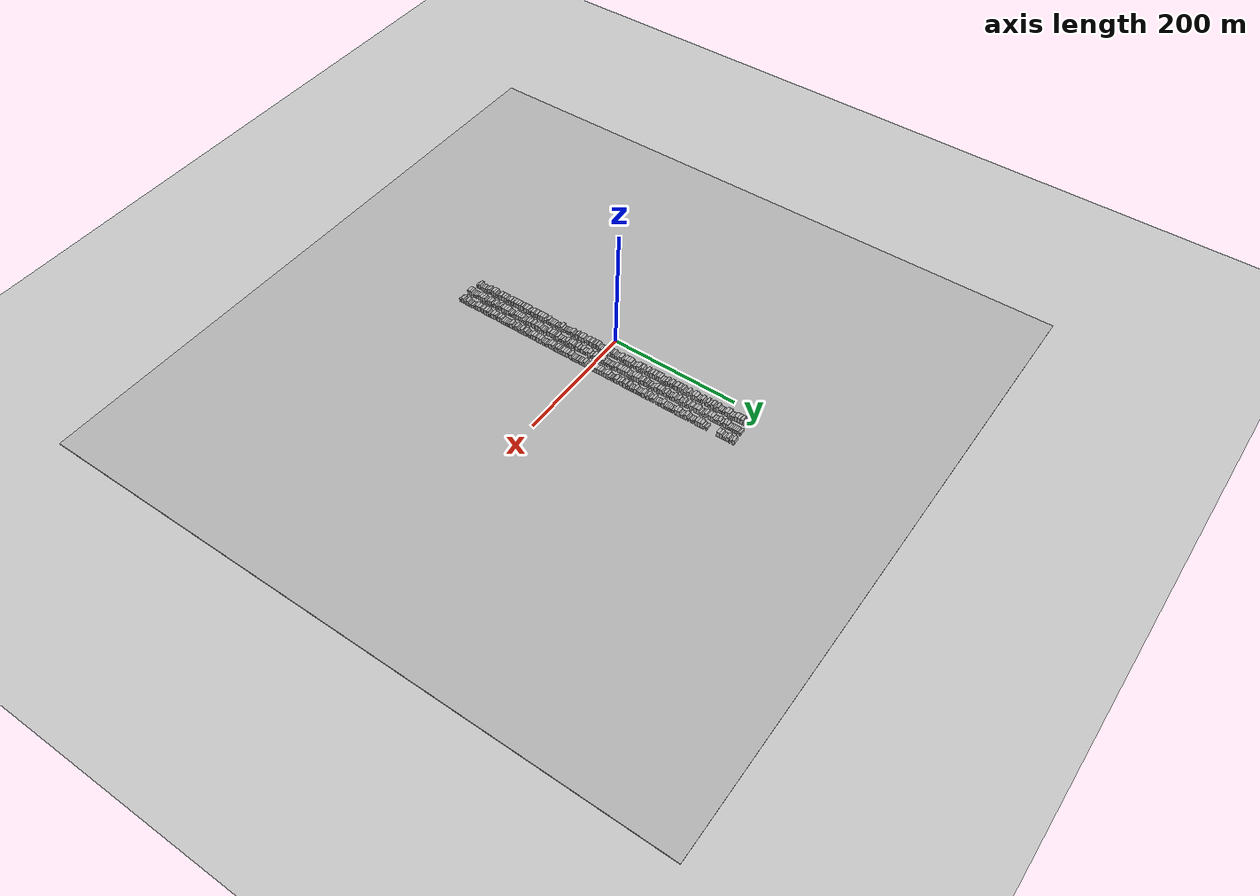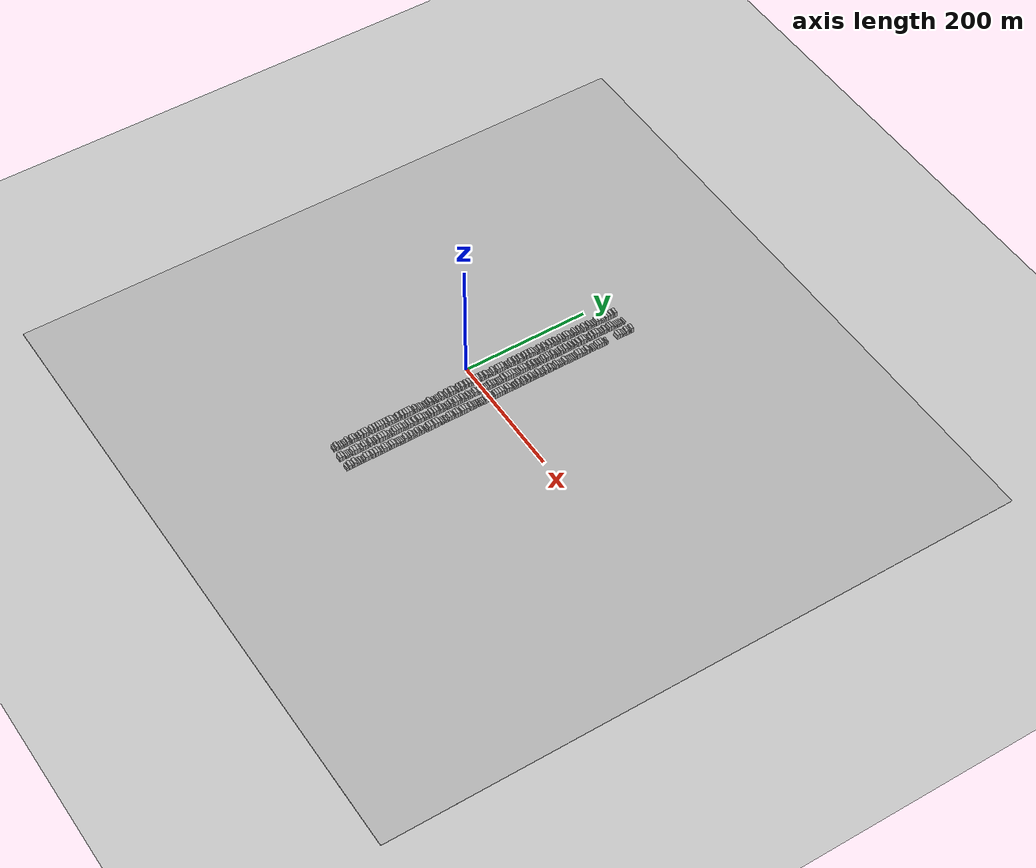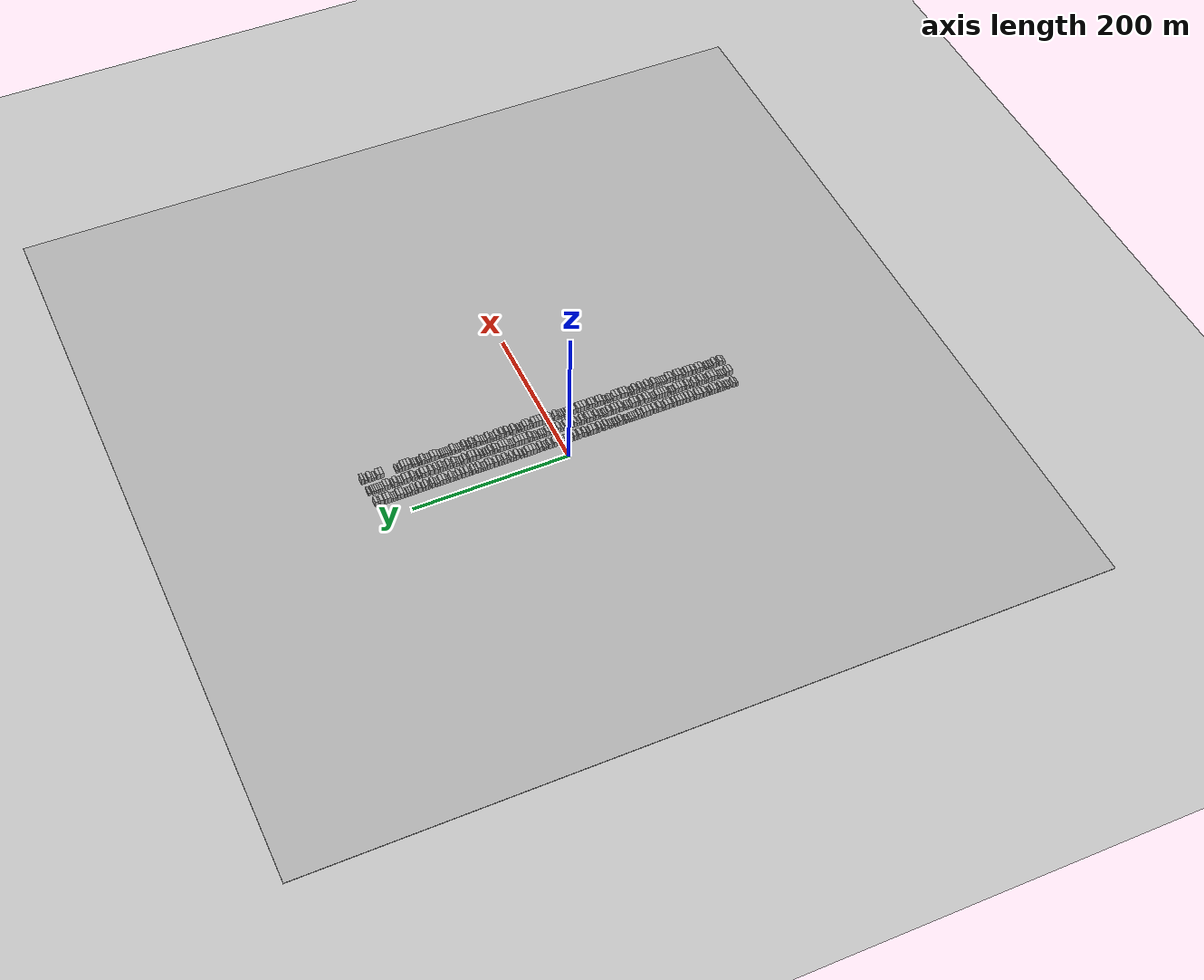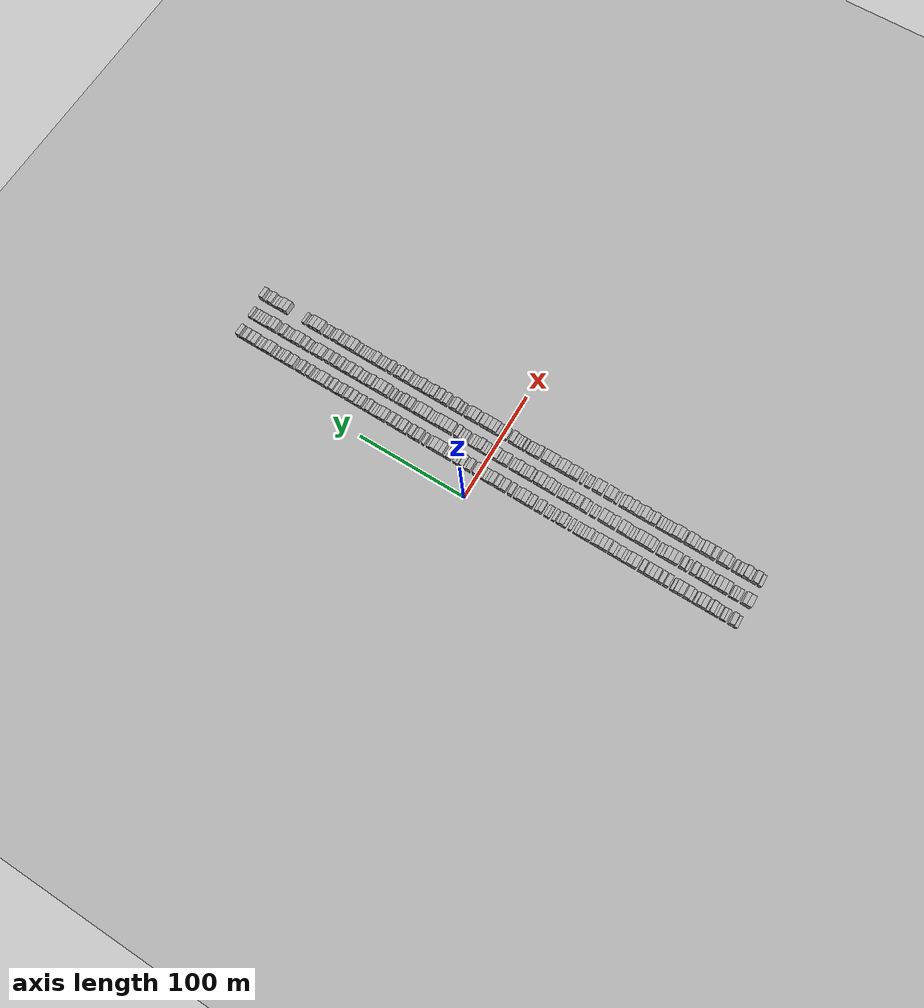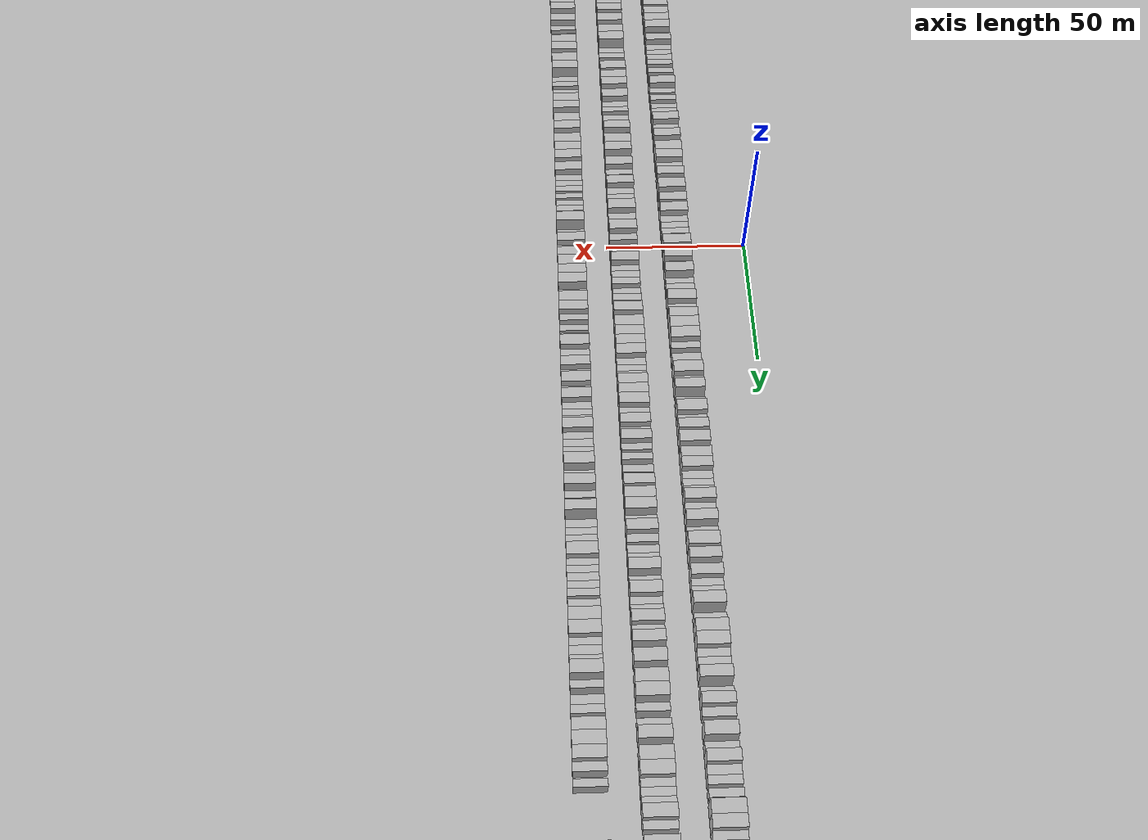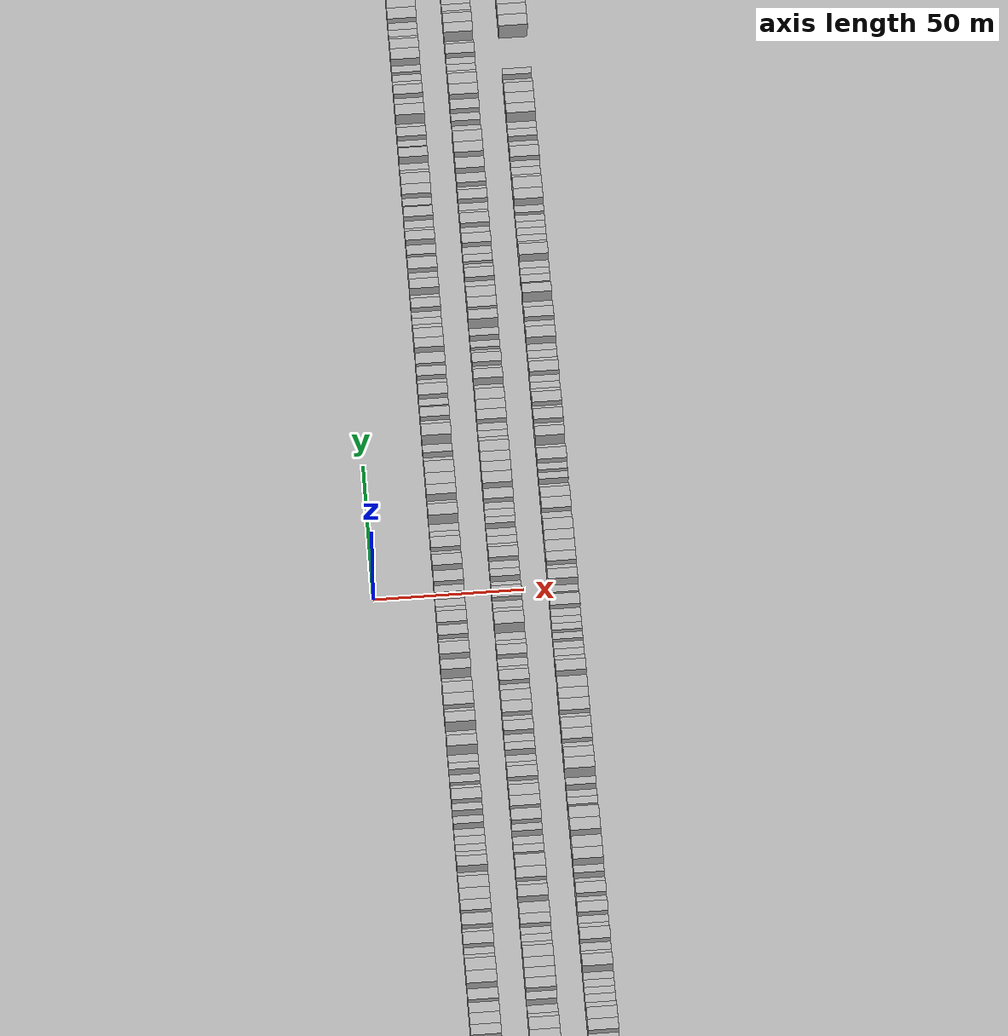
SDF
<?xml version="1.0" encoding="utf-8"?>

<sdf version="1.6">

   <world name="default">

      <gui fullscreen="0">

         <camera name="user_camera">

            <pose>-15 0 4.57585 0 0 0</pose>

            <view_controller>orbit</view_controller>

         </camera>

      </gui>

      <scene>

         <sky>

           <clouds>

             <speed>12</speed>

           </clouds>

         </sky>

         <ambient>0.4 0.4 0.4 1</ambient>

         <background>0.7 0.7 0.7 1</background>

         <shadows>1</shadows>

      </scene>

      <gravity>0 0 -9.8066</gravity>

      <magnetic_field>6e-06 2.3e-05 -4.2e-05</magnetic_field>

      <physics default="0" name="default_physics" type="ode">

         <ode>

            <solver>

               <type>quick</type>

               <iters>10</iters>

               <sor>1.0</sor>

               <use_dynamic_moi_rescaling>0</use_dynamic_moi_rescaling>

            </solver>

            <constraints>

               <cfm>0</cfm>

               <erp>0.2</erp>

               <contact_max_correcting_vel>100</contact_max_correcting_vel>

               <contact_surface_layer>0.001</contact_surface_layer>

            </constraints>

         </ode>

         <max_step_size>0.004</max_step_size>

         <real_time_factor>1</real_time_factor>

         <real_time_update_rate>250</real_time_update_rate>

      </physics>

      <light name="sun" type="directional">

         <cast_shadows>1</cast_shadows>

         <pose>0 0 10 0 0 0</pose>

         <diffuse>0.8 0.8 0.8 1</diffuse>

         <specular>0.2 0.2 0.2 1</specular>

         <attenuation>

            <range>1000</range>

            <constant>0.9</constant>

            <linear>0.01</linear>

            <quadratic>0.001</quadratic>

         </attenuation>

         <direction>-0.5 0.1 -0.9</direction>

      </light>

      <include>

         <name>ground_plane_1</name>

         <uri>model://HANNAS_ground_plane</uri>

         <pose>0 0 0  0 0 0</pose>

      </include>

      <include>

         <name>ground_plane_2</name>

         <uri>model://HANNAS_ground_plane</uri>

         <pose>100 0 0  0 0 0</pose>

      </include>

      <model name="building_1">

         <static>1</static>

         <pose frame="">25.0000 -232.7537 0 0.000000 0.000000 0.000000</pose>

         <link name="link">

            <pose frame="">0 0 3.00 0 0 0</pose>

            <collision name="collision">

               <geometry>

                  <box>

                     <size>10.0000 2.4925 6.0000</size>

                  </box>

               </geometry>

               <max_contacts>10</max_contacts>

               <surface>

                  <contact>

                     <ode/>

                  </contact>

                  <bounce/>

                  <friction>

                     <torsional>

                        <ode/>

                     </torsional>

                     <ode/>

                  </friction>

               </surface>

            </collision>

            <visual name="visual">

               <cast_shadows>0</cast_shadows>

               <geometry>

                  <box>

                     <size>10.0000 2.4925 6.0000</size>

                  </box>

               </geometry>

               <material>

                  <script>

                     <uri>model://HANNAS_wall/materials/scripts</uri>

                     <uri>model://HANNAS_wall/materials/textures</uri>

                     <name>vrc/HANNAS_wall</name>

                  </script>

               </material>

            </visual>

            <self_collide>0</self_collide>

            <enable_wind>0</enable_wind>

            <kinematic>0</kinematic>

         </link>

      </model>

      <model name="building_2">

         <static>1</static>

         <pose frame="">25.0000 -228.5154 0 0.000000 0.000000 0.000000</pose>

         <link name="link">

            <pose frame="">0 0 4.50 0 0 0</pose>

            <collision name="collision">

               <geometry>

                  <box>

                     <size>10.0000 3.9841 9.0000</size>

                  </box>

               </geometry>

               <max_contacts>10</max_contacts>

               <surface>

                  <contact>

                     <ode/>

                  </contact>

                  <bounce/>

                  <friction>

                     <torsional>

                        <ode/>

                     </torsional>

                     <ode/>

                  </friction>

               </surface>

            </collision>

            <visual name="visual">

               <cast_shadows>0</cast_shadows>

               <geometry>

                  <box>

                     <size>10.0000 3.9841 9.0000</size>

                  </box>

               </geometry>

               <material>

                  <script>

                     <uri>model://HANNAS_wall/materials/scripts</uri>

                     <uri>model://HANNAS_wall/materials/textures</uri>

                     <name>vrc/HANNAS_wall</name>

                  </script>

               </material>

            </visual>

            <self_collide>0</self_collide>

            <enable_wind>0</enable_wind>

            <kinematic>0</kinematic>

         </link>

      </model>

      <model name="building_3">

         <static>1</static>

         <pose frame="">25.0000 -223.2661 0 0.000000 0.000000 0.000000</pose>

         <link name="link">

            <pose frame="">0 0 3.00 0 0 0</pose>

            <collision name="collision">

               <geometry>

                  <box>

                     <size>10.0000 2.5146 6.0000</size>

                  </box>

               </geometry>

               <max_contacts>10</max_contacts>

               <surface>

                  <contact>

                     <ode/>

                  </contact>

                  <bounce/>

                  <friction>

                     <torsional>

                        <ode/>

                     </torsional>

                     <ode/>

                  </friction>

               </surface>

            </collision>

            <visual name="visual">

               <cast_shadows>0</cast_shadows>

               <geometry>

                  <box>

                     <size>10.0000 2.5146 6.0000</size>

                  </box>

               </geometry>

               <material>

                  <script>

                     <uri>model://HANNAS_wall/materials/scripts</uri>

                     <uri>model://HANNAS_wall/materials/textures</uri>

                     <name>vrc/HANNAS_wall</name>

                  </script>

               </material>

            </visual>

            <self_collide>0</self_collide>

            <enable_wind>0</enable_wind>

            <kinematic>0</kinematic>

         </link>

      </model>

      <model name="building_4">

         <static>1</static>

         <pose frame="">25.0000 -220.5553 0 0.000000 0.000000 0.000000</pose>

         <link name="link">

            <pose frame="">0 0 3.00 0 0 0</pose>

            <collision name="collision">

               <geometry>

                  <box>

                     <size>10.0000 2.9072 6.0000</size>

                  </box>

               </geometry>

               <max_contacts>10</max_contacts>

               <surface>

                  <contact>

                     <ode/>

                  </contact>

                  <bounce/>

                  <friction>

                     <torsional>

                        <ode/>

                     </torsional>

                     <ode/>

                  </friction>

               </surface>

            </collision>

            <visual name="visual">

               <cast_shadows>0</cast_shadows>

               <geometry>

                  <box>

                     <size>10.0000 2.9072 6.0000</size>

                  </box>

               </geometry>

               <material>

                  <script>

                     <uri>model://HANNAS_wall/materials/scripts</uri>

                     <uri>model://HANNAS_wall/materials/textures</uri>

                     <name>vrc/HANNAS_wall</name>

                  </script>

               </material>

            </visual>

            <self_collide>0</self_collide>

            <enable_wind>0</enable_wind>

            <kinematic>0</kinematic>

         </link>

      </model>

      <model name="building_5">

         <static>1</static>

         <pose frame="">25.0000 -216.8551 0 0.000000 0.000000 0.000000</pose>

         <link name="link">

            <pose frame="">0 0 3.00 0 0 0</pose>

            <collision name="collision">

               <geometry>

                  <box>

                     <size>10.0000 2.4931 6.0000</size>

                  </box>

               </geometry>

               <max_contacts>10</max_contacts>

               <surface>

                  <contact>

                     <ode/>

                  </contact>

                  <bounce/>

                  <friction>

                     <torsional>

                        <ode/>

                     </torsional>

                     <ode/>

                  </friction>

               </surface>

            </collision>

            <visual name="visual">

               <cast_shadows>0</cast_shadows>

               <geometry>

                  <box>

                     <size>10.0000 2.4931 6.0000</size>

                  </box>

               </geometry>

               <material>

                  <script>

                     <uri>model://HANNAS_wall/materials/scripts</uri>

                     <uri>model://HANNAS_wall/materials/textures</uri>

                     <name>vrc/HANNAS_wall</name>

                  </script>

               </material>

            </visual>

            <self_collide>0</self_collide>

            <enable_wind>0</enable_wind>

            <kinematic>0</kinematic>

         </link>

      </model>

      <model name="building_6">

         <static>1</static>

         <pose frame="">25.0000 -214.2833 0 0.000000 0.000000 0.000000</pose>

         <link name="link">

            <pose frame="">0 0 3.00 0 0 0</pose>

            <collision name="collision">

               <geometry>

                  <box>

                     <size>10.0000 2.6505 6.0000</size>

                  </box>

               </geometry>

               <max_contacts>10</max_contacts>

               <surface>

                  <contact>

                     <ode/>

                  </contact>

                  <bounce/>

                  <friction>

                     <torsional>

                        <ode/>

                     </torsional>

                     <ode/>

                  </friction>

               </surface>

            </collision>

            <visual name="visual">

               <cast_shadows>0</cast_shadows>

               <geometry>

                  <box>

                     <size>10.0000 2.6505 6.0000</size>

                  </box>

               </geometry>

               <material>

                  <script>

                     <uri>model://HANNAS_wall/materials/scripts</uri>

                     <uri>model://HANNAS_wall/materials/textures</uri>

                     <name>vrc/HANNAS_wall</name>

                  </script>

               </material>

            </visual>

            <self_collide>0</self_collide>

            <enable_wind>0</enable_wind>

            <kinematic>0</kinematic>

         </link>

      </model>

      <model name="building_7">

         <static>1</static>

         <pose frame="">25.0000 -211.0979 0 0.000000 0.000000 0.000000</pose>

         <link name="link">

            <pose frame="">0 0 4.50 0 0 0</pose>

            <collision name="collision">

               <geometry>

                  <box>

                     <size>10.0000 3.7204 9.0000</size>

                  </box>

               </geometry>

               <max_contacts>10</max_contacts>

               <surface>

                  <contact>

                     <ode/>

                  </contact>

                  <bounce/>

                  <friction>

                     <torsional>

                        <ode/>

                     </torsional>

                     <ode/>

                  </friction>

               </surface>

            </collision>

            <visual name="visual">

               <cast_shadows>0</cast_shadows>

               <geometry>

                  <box>

                     <size>10.0000 3.7204 9.0000</size>

                  </box>

               </geometry>

               <material>

                  <script>

                     <uri>model://HANNAS_wall/materials/scripts</uri>

                     <uri>model://HANNAS_wall/materials/textures</uri>

                     <name>vrc/HANNAS_wall</name>

                  </script>

               </material>

            </visual>

            <self_collide>0</self_collide>

            <enable_wind>0</enable_wind>

            <kinematic>0</kinematic>

         </link>

      </model>

      <model name="building_8">

         <static>1</static>

         <pose frame="">25.0000 -207.9885 0 0.000000 0.000000 0.000000</pose>

         <link name="link">

            <pose frame="">0 0 3.00 0 0 0</pose>

            <collision name="collision">

               <geometry>

                  <box>

                     <size>10.0000 2.4984 6.0000</size>

                  </box>

               </geometry>

               <max_contacts>10</max_contacts>

               <surface>

                  <contact>

                     <ode/>

                  </contact>

                  <bounce/>

                  <friction>

                     <torsional>

                        <ode/>

                     </torsional>

                     <ode/>

                  </friction>

               </surface>

            </collision>

            <visual name="visual">

               <cast_shadows>0</cast_shadows>

               <geometry>

                  <box>

                     <size>10.0000 2.4984 6.0000</size>

                  </box>

               </geometry>

               <material>

                  <script>

                     <uri>model://HANNAS_wall/materials/scripts</uri>

                     <uri>model://HANNAS_wall/materials/textures</uri>

                     <name>vrc/HANNAS_wall</name>

                  </script>

               </material>

            </visual>

            <self_collide>0</self_collide>

            <enable_wind>0</enable_wind>

            <kinematic>0</kinematic>

         </link>

      </model>

      <model name="building_9">

         <static>1</static>

         <pose frame="">25.0000 -203.7251 0 0.000000 0.000000 0.000000</pose>

         <link name="link">

            <pose frame="">0 0 4.50 0 0 0</pose>

            <collision name="collision">

               <geometry>

                  <box>

                     <size>10.0000 4.0283 9.0000</size>

                  </box>

               </geometry>

               <max_contacts>10</max_contacts>

               <surface>

                  <contact>

                     <ode/>

                  </contact>

                  <bounce/>

                  <friction>

                     <torsional>

                        <ode/>

                     </torsional>

                     <ode/>

                  </friction>

               </surface>

            </collision>

            <visual name="visual">

               <cast_shadows>0</cast_shadows>

               <geometry>

                  <box>

                     <size>10.0000 4.0283 9.0000</size>

                  </box>

               </geometry>

               <material>

                  <script>

                     <uri>model://HANNAS_wall/materials/scripts</uri>

                     <uri>model://HANNAS_wall/materials/textures</uri>

                     <name>vrc/HANNAS_wall</name>

                  </script>

               </material>

            </visual>

            <self_collide>0</self_collide>

            <enable_wind>0</enable_wind>

            <kinematic>0</kinematic>

         </link>

      </model>

      <model name="building_10">

         <static>1</static>

         <pose frame="">25.0000 -199.9079 0 0.000000 0.000000 0.000000</pose>

         <link name="link">

            <pose frame="">0 0 4.50 0 0 0</pose>

            <collision name="collision">

               <geometry>

                  <box>

                     <size>10.0000 3.6059 9.0000</size>

                  </box>

               </geometry>

               <max_contacts>10</max_contacts>

               <surface>

                  <contact>

                     <ode/>

                  </contact>

                  <bounce/>

                  <friction>

                     <torsional>

                        <ode/>

                     </torsional>

                     <ode/>

                  </friction>

               </surface>

            </collision>

            <visual name="visual">

               <cast_shadows>0</cast_shadows>

               <geometry>

                  <box>

                     <size>10.0000 3.6059 9.0000</size>

                  </box>

               </geometry>

               <material>

                  <script>

                     <uri>model://HANNAS_wall/materials/scripts</uri>

                     <uri>model://HANNAS_wall/materials/textures</uri>

                     <name>vrc/HANNAS_wall</name>

                  </script>

               </material>

            </visual>

            <self_collide>0</self_collide>

            <enable_wind>0</enable_wind>

            <kinematic>0</kinematic>

         </link>

      </model>

      <model name="building_11">

         <static>1</static>

         <pose frame="">25.0000 -196.8338 0 0.000000 0.000000 0.000000</pose>

         <link name="link">

            <pose frame="">0 0 3.00 0 0 0</pose>

            <collision name="collision">

               <geometry>

                  <box>

                     <size>10.0000 2.5424 6.0000</size>

                  </box>

               </geometry>

               <max_contacts>10</max_contacts>

               <surface>

                  <contact>

                     <ode/>

                  </contact>

                  <bounce/>

                  <friction>

                     <torsional>

                        <ode/>

                     </torsional>

                     <ode/>

                  </friction>

               </surface>

            </collision>

            <visual name="visual">

               <cast_shadows>0</cast_shadows>

               <geometry>

                  <box>

                     <size>10.0000 2.5424 6.0000</size>

                  </box>

               </geometry>

               <material>

                  <script>

                     <uri>model://HANNAS_wall/materials/scripts</uri>

                     <uri>model://HANNAS_wall/materials/textures</uri>

                     <name>vrc/HANNAS_wall</name>

                  </script>

               </material>

            </visual>

            <self_collide>0</self_collide>

            <enable_wind>0</enable_wind>

            <kinematic>0</kinematic>

         </link>

      </model>

      <model name="building_12">

         <static>1</static>

         <pose frame="">25.0000 -193.0721 0 0.000000 0.000000 0.000000</pose>

         <link name="link">

            <pose frame="">0 0 3.00 0 0 0</pose>

            <collision name="collision">

               <geometry>

                  <box>

                     <size>10.0000 2.9810 6.0000</size>

                  </box>

               </geometry>

               <max_contacts>10</max_contacts>

               <surface>

                  <contact>

                     <ode/>

                  </contact>

                  <bounce/>

                  <friction>

                     <torsional>

                        <ode/>

                     </torsional>

                     <ode/>

                  </friction>

               </surface>

            </collision>

            <visual name="visual">

               <cast_shadows>0</cast_shadows>

               <geometry>

                  <box>

                     <size>10.0000 2.9810 6.0000</size>

                  </box>

               </geometry>

               <material>

                  <script>

                     <uri>model://HANNAS_wall/materials/scripts</uri>

                     <uri>model://HANNAS_wall/materials/textures</uri>

                     <name>vrc/HANNAS_wall</name>

                  </script>

               </material>

            </visual>

            <self_collide>0</self_collide>

            <enable_wind>0</enable_wind>

            <kinematic>0</kinematic>

         </link>

      </model>

      <model name="building_13">

         <static>1</static>

         <pose frame="">25.0000 -189.4063 0 0.000000 0.000000 0.000000</pose>

         <link name="link">

            <pose frame="">0 0 4.50 0 0 0</pose>

            <collision name="collision">

               <geometry>

                  <box>

                     <size>10.0000 4.3505 9.0000</size>

                  </box>

               </geometry>

               <max_contacts>10</max_contacts>

               <surface>

                  <contact>

                     <ode/>

                  </contact>

                  <bounce/>

                  <friction>

                     <torsional>

                        <ode/>

                     </torsional>

                     <ode/>

                  </friction>

               </surface>

            </collision>

            <visual name="visual">

               <cast_shadows>0</cast_shadows>

               <geometry>

                  <box>

                     <size>10.0000 4.3505 9.0000</size>

                  </box>

               </geometry>

               <material>

                  <script>

                     <uri>model://HANNAS_wall/materials/scripts</uri>

                     <uri>model://HANNAS_wall/materials/textures</uri>

                     <name>vrc/HANNAS_wall</name>

                  </script>

               </material>

            </visual>

            <self_collide>0</self_collide>

            <enable_wind>0</enable_wind>

            <kinematic>0</kinematic>

         </link>

      </model>

      <model name="building_14">

         <static>1</static>

         <pose frame="">25.0000 -184.1041 0 0.000000 0.000000 0.000000</pose>

         <link name="link">

            <pose frame="">0 0 4.50 0 0 0</pose>

            <collision name="collision">

               <geometry>

                  <box>

                     <size>10.0000 4.2540 9.0000</size>

                  </box>

               </geometry>

               <max_contacts>10</max_contacts>

               <surface>

                  <contact>

                     <ode/>

                  </contact>

                  <bounce/>

                  <friction>

                     <torsional>

                        <ode/>

                     </torsional>

                     <ode/>

                  </friction>

               </surface>

            </collision>

            <visual name="visual">

               <cast_shadows>0</cast_shadows>

               <geometry>

                  <box>

                     <size>10.0000 4.2540 9.0000</size>

                  </box>

               </geometry>

               <material>

                  <script>

                     <uri>model://HANNAS_wall/materials/scripts</uri>

                     <uri>model://HANNAS_wall/materials/textures</uri>

                     <name>vrc/HANNAS_wall</name>

                  </script>

               </material>

            </visual>

            <self_collide>0</self_collide>

            <enable_wind>0</enable_wind>

            <kinematic>0</kinematic>

         </link>

      </model>

      <model name="building_15">

         <static>1</static>

         <pose frame="">25.0000 -180.0002 0 0.000000 0.000000 0.000000</pose>

         <link name="link">

            <pose frame="">0 0 4.50 0 0 0</pose>

            <collision name="collision">

               <geometry>

                  <box>

                     <size>10.0000 3.9536 9.0000</size>

                  </box>

               </geometry>

               <max_contacts>10</max_contacts>

               <surface>

                  <contact>

                     <ode/>

                  </contact>

                  <bounce/>

                  <friction>

                     <torsional>

                        <ode/>

                     </torsional>

                     <ode/>

                  </friction>

               </surface>

            </collision>

            <visual name="visual">

               <cast_shadows>0</cast_shadows>

               <geometry>

                  <box>

                     <size>10.0000 3.9536 9.0000</size>

                  </box>

               </geometry>

               <material>

                  <script>

                     <uri>model://HANNAS_wall/materials/scripts</uri>

                     <uri>model://HANNAS_wall/materials/textures</uri>

                     <name>vrc/HANNAS_wall</name>

                  </script>

               </material>

            </visual>

            <self_collide>0</self_collide>

            <enable_wind>0</enable_wind>

            <kinematic>0</kinematic>

         </link>

      </model>

      <model name="building_16">

         <static>1</static>

         <pose frame="">25.0000 -176.7750 0 0.000000 0.000000 0.000000</pose>

         <link name="link">

            <pose frame="">0 0 3.00 0 0 0</pose>

            <collision name="collision">

               <geometry>

                  <box>

                     <size>10.0000 2.4969 6.0000</size>

                  </box>

               </geometry>

               <max_contacts>10</max_contacts>

               <surface>

                  <contact>

                     <ode/>

                  </contact>

                  <bounce/>

                  <friction>

                     <torsional>

                        <ode/>

                     </torsional>

                     <ode/>

                  </friction>

               </surface>

            </collision>

            <visual name="visual">

               <cast_shadows>0</cast_shadows>

               <geometry>

                  <box>

                     <size>10.0000 2.4969 6.0000</size>

                  </box>

               </geometry>

               <material>

                  <script>

                     <uri>model://HANNAS_wall/materials/scripts</uri>

                     <uri>model://HANNAS_wall/materials/textures</uri>

                     <name>vrc/HANNAS_wall</name>

                  </script>

               </material>

            </visual>

            <self_collide>0</self_collide>

            <enable_wind>0</enable_wind>

            <kinematic>0</kinematic>

         </link>

      </model>

      <model name="building_17">

         <static>1</static>

         <pose frame="">25.0000 -171.4529 0 0.000000 0.000000 0.000000</pose>

         <link name="link">

            <pose frame="">0 0 4.50 0 0 0</pose>

            <collision name="collision">

               <geometry>

                  <box>

                     <size>10.0000 4.1472 9.0000</size>

                  </box>

               </geometry>

               <max_contacts>10</max_contacts>

               <surface>

                  <contact>

                     <ode/>

                  </contact>

                  <bounce/>

                  <friction>

                     <torsional>

                        <ode/>

                     </torsional>

                     <ode/>

                  </friction>

               </surface>

            </collision>

            <visual name="visual">

               <cast_shadows>0</cast_shadows>

               <geometry>

                  <box>

                     <size>10.0000 4.1472 9.0000</size>

                  </box>

               </geometry>

               <material>

                  <script>

                     <uri>model://HANNAS_wall/materials/scripts</uri>

                     <uri>model://HANNAS_wall/materials/textures</uri>

                     <name>vrc/HANNAS_wall</name>

                  </script>

               </material>

            </visual>

            <self_collide>0</self_collide>

            <enable_wind>0</enable_wind>

            <kinematic>0</kinematic>

         </link>

      </model>

      <model name="building_18">

         <static>1</static>

         <pose frame="">25.0000 -166.4618 0 0.000000 0.000000 0.000000</pose>

         <link name="link">

            <pose frame="">0 0 4.50 0 0 0</pose>

            <collision name="collision">

               <geometry>

                  <box>

                     <size>10.0000 3.8350 9.0000</size>

                  </box>

               </geometry>

               <max_contacts>10</max_contacts>

               <surface>

                  <contact>

                     <ode/>

                  </contact>

                  <bounce/>

                  <friction>

                     <torsional>

                        <ode/>

                     </torsional>

                     <ode/>

                  </friction>

               </surface>

            </collision>

            <visual name="visual">

               <cast_shadows>0</cast_shadows>

               <geometry>

                  <box>

                     <size>10.0000 3.8350 9.0000</size>

                  </box>

               </geometry>

               <material>

                  <script>

                     <uri>model://HANNAS_wall/materials/scripts</uri>

                     <uri>model://HANNAS_wall/materials/textures</uri>

                     <name>vrc/HANNAS_wall</name>

                  </script>

               </material>

            </visual>

            <self_collide>0</self_collide>

            <enable_wind>0</enable_wind>

            <kinematic>0</kinematic>

         </link>

      </model>

      <model name="building_19">

         <static>1</static>

         <pose frame="">25.0000 -161.6839 0 0.000000 0.000000 0.000000</pose>

         <link name="link">

            <pose frame="">0 0 4.50 0 0 0</pose>

            <collision name="collision">

               <geometry>

                  <box>

                     <size>10.0000 3.7208 9.0000</size>

                  </box>

               </geometry>

               <max_contacts>10</max_contacts>

               <surface>

                  <contact>

                     <ode/>

                  </contact>

                  <bounce/>

                  <friction>

                     <torsional>

                        <ode/>

                     </torsional>

                     <ode/>

                  </friction>

               </surface>

            </collision>

            <visual name="visual">

               <cast_shadows>0</cast_shadows>

               <geometry>

                  <box>

                     <size>10.0000 3.7208 9.0000</size>

                  </box>

               </geometry>

               <material>

                  <script>

                     <uri>model://HANNAS_wall/materials/scripts</uri>

                     <uri>model://HANNAS_wall/materials/textures</uri>

                     <name>vrc/HANNAS_wall</name>

                  </script>

               </material>

            </visual>

            <self_collide>0</self_collide>

            <enable_wind>0</enable_wind>

            <kinematic>0</kinematic>

         </link>

      </model>

      <model name="building_20">

         <static>1</static>

         <pose frame="">25.0000 -157.7794 0 0.000000 0.000000 0.000000</pose>

         <link name="link">

            <pose frame="">0 0 4.50 0 0 0</pose>

            <collision name="collision">

               <geometry>

                  <box>

                     <size>10.0000 4.0881 9.0000</size>

                  </box>

               </geometry>

               <max_contacts>10</max_contacts>

               <surface>

                  <contact>

                     <ode/>

                  </contact>

                  <bounce/>

                  <friction>

                     <torsional>

                        <ode/>

                     </torsional>

                     <ode/>

                  </friction>

               </surface>

            </collision>

            <visual name="visual">

               <cast_shadows>0</cast_shadows>

               <geometry>

                  <box>

                     <size>10.0000 4.0881 9.0000</size>

                  </box>

               </geometry>

               <material>

                  <script>

                     <uri>model://HANNAS_wall/materials/scripts</uri>

                     <uri>model://HANNAS_wall/materials/textures</uri>

                     <name>vrc/HANNAS_wall</name>

                  </script>

               </material>

            </visual>

            <self_collide>0</self_collide>

            <enable_wind>0</enable_wind>

            <kinematic>0</kinematic>

         </link>

      </model>

      <model name="building_21">

         <static>1</static>

         <pose frame="">25.0000 -153.9046 0 0.000000 0.000000 0.000000</pose>

         <link name="link">

            <pose frame="">0 0 4.50 0 0 0</pose>

            <collision name="collision">

               <geometry>

                  <box>

                     <size>10.0000 3.6616 9.0000</size>

                  </box>

               </geometry>

               <max_contacts>10</max_contacts>

               <surface>

                  <contact>

                     <ode/>

                  </contact>

                  <bounce/>

                  <friction>

                     <torsional>

                        <ode/>

                     </torsional>

                     <ode/>

                  </friction>

               </surface>

            </collision>

            <visual name="visual">

               <cast_shadows>0</cast_shadows>

               <geometry>

                  <box>

                     <size>10.0000 3.6616 9.0000</size>

                  </box>

               </geometry>

               <material>

                  <script>

                     <uri>model://HANNAS_wall/materials/scripts</uri>

                     <uri>model://HANNAS_wall/materials/textures</uri>

                     <name>vrc/HANNAS_wall</name>

                  </script>

               </material>

            </visual>

            <self_collide>0</self_collide>

            <enable_wind>0</enable_wind>

            <kinematic>0</kinematic>

         </link>

      </model>

      <model name="building_22">

         <static>1</static>

         <pose frame="">25.0000 -149.1466 0 0.000000 0.000000 0.000000</pose>

         <link name="link">

            <pose frame="">0 0 4.50 0 0 0</pose>

            <collision name="collision">

               <geometry>

                  <box>

                     <size>10.0000 3.8543 9.0000</size>

                  </box>

               </geometry>

               <max_contacts>10</max_contacts>

               <surface>

                  <contact>

                     <ode/>

                  </contact>

                  <bounce/>

                  <friction>

                     <torsional>

                        <ode/>

                     </torsional>

                     <ode/>

                  </friction>

               </surface>

            </collision>

            <visual name="visual">

               <cast_shadows>0</cast_shadows>

               <geometry>

                  <box>

                     <size>10.0000 3.8543 9.0000</size>

                  </box>

               </geometry>

               <material>

                  <script>

                     <uri>model://HANNAS_wall/materials/scripts</uri>

                     <uri>model://HANNAS_wall/materials/textures</uri>

                     <name>vrc/HANNAS_wall</name>

                  </script>

               </material>

            </visual>

            <self_collide>0</self_collide>

            <enable_wind>0</enable_wind>

            <kinematic>0</kinematic>

         </link>

      </model>

      <model name="building_23">

         <static>1</static>

         <pose frame="">25.0000 -142.9909 0 0.000000 0.000000 0.000000</pose>

         <link name="link">

            <pose frame="">0 0 4.50 0 0 0</pose>

            <collision name="collision">

               <geometry>

                  <box>

                     <size>10.0000 4.4572 9.0000</size>

                  </box>

               </geometry>

               <max_contacts>10</max_contacts>

               <surface>

                  <contact>

                     <ode/>

                  </contact>

                  <bounce/>

                  <friction>

                     <torsional>

                        <ode/>

                     </torsional>

                     <ode/>

                  </friction>

               </surface>

            </collision>

            <visual name="visual">

               <cast_shadows>0</cast_shadows>

               <geometry>

                  <box>

                     <size>10.0000 4.4572 9.0000</size>

                  </box>

               </geometry>

               <material>

                  <script>

                     <uri>model://HANNAS_wall/materials/scripts</uri>

                     <uri>model://HANNAS_wall/materials/textures</uri>

                     <name>vrc/HANNAS_wall</name>

                  </script>

               </material>

            </visual>

            <self_collide>0</self_collide>

            <enable_wind>0</enable_wind>

            <kinematic>0</kinematic>

         </link>

      </model>

      <model name="building_24">

         <static>1</static>

         <pose frame="">25.0000 -138.5390 0 0.000000 0.000000 0.000000</pose>

         <link name="link">

            <pose frame="">0 0 4.50 0 0 0</pose>

            <collision name="collision">

               <geometry>

                  <box>

                     <size>10.0000 4.4466 9.0000</size>

                  </box>

               </geometry>

               <max_contacts>10</max_contacts>

               <surface>

                  <contact>

                     <ode/>

                  </contact>

                  <bounce/>

                  <friction>

                     <torsional>

                        <ode/>

                     </torsional>

                     <ode/>

                  </friction>

               </surface>

            </collision>

            <visual name="visual">

               <cast_shadows>0</cast_shadows>

               <geometry>

                  <box>

                     <size>10.0000 4.4466 9.0000</size>

                  </box>

               </geometry>

               <material>

                  <script>

                     <uri>model://HANNAS_wall/materials/scripts</uri>

                     <uri>model://HANNAS_wall/materials/textures</uri>

                     <name>vrc/HANNAS_wall</name>

                  </script>

               </material>

            </visual>

            <self_collide>0</self_collide>

            <enable_wind>0</enable_wind>

            <kinematic>0</kinematic>

         </link>

      </model>

      <model name="building_25">

         <static>1</static>

         <pose frame="">25.0000 -135.0715 0 0.000000 0.000000 0.000000</pose>

         <link name="link">

            <pose frame="">0 0 3.00 0 0 0</pose>

            <collision name="collision">

               <geometry>

                  <box>

                     <size>10.0000 2.4883 6.0000</size>

                  </box>

               </geometry>

               <max_contacts>10</max_contacts>

               <surface>

                  <contact>

                     <ode/>

                  </contact>

                  <bounce/>

                  <friction>

                     <torsional>

                        <ode/>

                     </torsional>

                     <ode/>

                  </friction>

               </surface>

            </collision>

            <visual name="visual">

               <cast_shadows>0</cast_shadows>

               <geometry>

                  <box>

                     <size>10.0000 2.4883 6.0000</size>

                  </box>

               </geometry>

               <material>

                  <script>

                     <uri>model://HANNAS_wall/materials/scripts</uri>

                     <uri>model://HANNAS_wall/materials/textures</uri>

                     <name>vrc/HANNAS_wall</name>

                  </script>

               </material>

            </visual>

            <self_collide>0</self_collide>

            <enable_wind>0</enable_wind>

            <kinematic>0</kinematic>

         </link>

      </model>

      <model name="building_26">

         <static>1</static>

         <pose frame="">25.0000 -132.5944 0 0.000000 0.000000 0.000000</pose>

         <link name="link">

            <pose frame="">0 0 3.00 0 0 0</pose>

            <collision name="collision">

               <geometry>

                  <box>

                     <size>10.0000 2.4660 6.0000</size>

                  </box>

               </geometry>

               <max_contacts>10</max_contacts>

               <surface>

                  <contact>

                     <ode/>

                  </contact>

                  <bounce/>

                  <friction>

                     <torsional>

                        <ode/>

                     </torsional>

                     <ode/>

                  </friction>

               </surface>

            </collision>

            <visual name="visual">

               <cast_shadows>0</cast_shadows>

               <geometry>

                  <box>

                     <size>10.0000 2.4660 6.0000</size>

                  </box>

               </geometry>

               <material>

                  <script>

                     <uri>model://HANNAS_wall/materials/scripts</uri>

                     <uri>model://HANNAS_wall/materials/textures</uri>

                     <name>vrc/HANNAS_wall</name>

                  </script>

               </material>

            </visual>

            <self_collide>0</self_collide>

            <enable_wind>0</enable_wind>

            <kinematic>0</kinematic>

         </link>

      </model>

      <model name="building_27">

         <static>1</static>

         <pose frame="">25.0000 -129.1966 0 0.000000 0.000000 0.000000</pose>

         <link name="link">

            <pose frame="">0 0 4.50 0 0 0</pose>

            <collision name="collision">

               <geometry>

                  <box>

                     <size>10.0000 4.3295 9.0000</size>

                  </box>

               </geometry>

               <max_contacts>10</max_contacts>

               <surface>

                  <contact>

                     <ode/>

                  </contact>

                  <bounce/>

                  <friction>

                     <torsional>

                        <ode/>

                     </torsional>

                     <ode/>

                  </friction>

               </surface>

            </collision>

            <visual name="visual">

               <cast_shadows>0</cast_shadows>

               <geometry>

                  <box>

                     <size>10.0000 4.3295 9.0000</size>

                  </box>

               </geometry>

               <material>

                  <script>

                     <uri>model://HANNAS_wall/materials/scripts</uri>

                     <uri>model://HANNAS_wall/materials/textures</uri>

                     <name>vrc/HANNAS_wall</name>

                  </script>

               </material>

            </visual>

            <self_collide>0</self_collide>

            <enable_wind>0</enable_wind>

            <kinematic>0</kinematic>

         </link>

      </model>

      <model name="building_28">

         <static>1</static>

         <pose frame="">25.0000 -125.7980 0 0.000000 0.000000 0.000000</pose>

         <link name="link">

            <pose frame="">0 0 3.00 0 0 0</pose>

            <collision name="collision">

               <geometry>

                  <box>

                     <size>10.0000 2.4677 6.0000</size>

                  </box>

               </geometry>

               <max_contacts>10</max_contacts>

               <surface>

                  <contact>

                     <ode/>

                  </contact>

                  <bounce/>

                  <friction>

                     <torsional>

                        <ode/>

                     </torsional>

                     <ode/>

                  </friction>

               </surface>

            </collision>

            <visual name="visual">

               <cast_shadows>0</cast_shadows>

               <geometry>

                  <box>

                     <size>10.0000 2.4677 6.0000</size>

                  </box>

               </geometry>

               <material>

                  <script>

                     <uri>model://HANNAS_wall/materials/scripts</uri>

                     <uri>model://HANNAS_wall/materials/textures</uri>

                     <name>vrc/HANNAS_wall</name>

                  </script>

               </material>

            </visual>

            <self_collide>0</self_collide>

            <enable_wind>0</enable_wind>

            <kinematic>0</kinematic>

         </link>

      </model>

      <model name="building_29">

         <static>1</static>

         <pose frame="">25.0000 -122.4533 0 0.000000 0.000000 0.000000</pose>

         <link name="link">

            <pose frame="">0 0 4.50 0 0 0</pose>

            <collision name="collision">

               <geometry>

                  <box>

                     <size>10.0000 4.2217 9.0000</size>

                  </box>

               </geometry>

               <max_contacts>10</max_contacts>

               <surface>

                  <contact>

                     <ode/>

                  </contact>

                  <bounce/>

                  <friction>

                     <torsional>

                        <ode/>

                     </torsional>

                     <ode/>

                  </friction>

               </surface>

            </collision>

            <visual name="visual">

               <cast_shadows>0</cast_shadows>

               <geometry>

                  <box>

                     <size>10.0000 4.2217 9.0000</size>

                  </box>

               </geometry>

               <material>

                  <script>

                     <uri>model://HANNAS_wall/materials/scripts</uri>

                     <uri>model://HANNAS_wall/materials/textures</uri>

                     <name>vrc/HANNAS_wall</name>

                  </script>

               </material>

            </visual>

            <self_collide>0</self_collide>

            <enable_wind>0</enable_wind>

            <kinematic>0</kinematic>

         </link>

      </model>

      <model name="building_30">

         <static>1</static>

         <pose frame="">25.0000 -117.4191 0 0.000000 0.000000 0.000000</pose>

         <link name="link">

            <pose frame="">0 0 4.50 0 0 0</pose>

            <collision name="collision">

               <geometry>

                  <box>

                     <size>10.0000 3.8467 9.0000</size>

                  </box>

               </geometry>

               <max_contacts>10</max_contacts>

               <surface>

                  <contact>

                     <ode/>

                  </contact>

                  <bounce/>

                  <friction>

                     <torsional>

                        <ode/>

                     </torsional>

                     <ode/>

                  </friction>

               </surface>

            </collision>

            <visual name="visual">

               <cast_shadows>0</cast_shadows>

               <geometry>

                  <box>

                     <size>10.0000 3.8467 9.0000</size>

                  </box>

               </geometry>

               <material>

                  <script>

                     <uri>model://HANNAS_wall/materials/scripts</uri>

                     <uri>model://HANNAS_wall/materials/textures</uri>

                     <name>vrc/HANNAS_wall</name>

                  </script>

               </material>

            </visual>

            <self_collide>0</self_collide>

            <enable_wind>0</enable_wind>

            <kinematic>0</kinematic>

         </link>

      </model>

      <model name="building_31">

         <static>1</static>

         <pose frame="">25.0000 -113.3922 0 0.000000 0.000000 0.000000</pose>

         <link name="link">

            <pose frame="">0 0 4.50 0 0 0</pose>

            <collision name="collision">

               <geometry>

                  <box>

                     <size>10.0000 4.2071 9.0000</size>

                  </box>

               </geometry>

               <max_contacts>10</max_contacts>

               <surface>

                  <contact>

                     <ode/>

                  </contact>

                  <bounce/>

                  <friction>

                     <torsional>

                        <ode/>

                     </torsional>

                     <ode/>

                  </friction>

               </surface>

            </collision>

            <visual name="visual">

               <cast_shadows>0</cast_shadows>

               <geometry>

                  <box>

                     <size>10.0000 4.2071 9.0000</size>

                  </box>

               </geometry>

               <material>

                  <script>

                     <uri>model://HANNAS_wall/materials/scripts</uri>

                     <uri>model://HANNAS_wall/materials/textures</uri>

                     <name>vrc/HANNAS_wall</name>

                  </script>

               </material>

            </visual>

            <self_collide>0</self_collide>

            <enable_wind>0</enable_wind>

            <kinematic>0</kinematic>

         </link>

      </model>

      <model name="building_32">

         <static>1</static>

         <pose frame="">25.0000 -109.1621 0 0.000000 0.000000 0.000000</pose>

         <link name="link">

            <pose frame="">0 0 4.50 0 0 0</pose>

            <collision name="collision">

               <geometry>

                  <box>

                     <size>10.0000 4.2531 9.0000</size>

                  </box>

               </geometry>

               <max_contacts>10</max_contacts>

               <surface>

                  <contact>

                     <ode/>

                  </contact>

                  <bounce/>

                  <friction>

                     <torsional>

                        <ode/>

                     </torsional>

                     <ode/>

                  </friction>

               </surface>

            </collision>

            <visual name="visual">

               <cast_shadows>0</cast_shadows>

               <geometry>

                  <box>

                     <size>10.0000 4.2531 9.0000</size>

                  </box>

               </geometry>

               <material>

                  <script>

                     <uri>model://HANNAS_wall/materials/scripts</uri>

                     <uri>model://HANNAS_wall/materials/textures</uri>

                     <name>vrc/HANNAS_wall</name>

                  </script>

               </material>

            </visual>

            <self_collide>0</self_collide>

            <enable_wind>0</enable_wind>

            <kinematic>0</kinematic>

         </link>

      </model>

      <model name="building_33">

         <static>1</static>

         <pose frame="">25.0000 -105.7331 0 0.000000 0.000000 0.000000</pose>

         <link name="link">

            <pose frame="">0 0 3.00 0 0 0</pose>

            <collision name="collision">

               <geometry>

                  <box>

                     <size>10.0000 2.6048 6.0000</size>

                  </box>

               </geometry>

               <max_contacts>10</max_contacts>

               <surface>

                  <contact>

                     <ode/>

                  </contact>

                  <bounce/>

                  <friction>

                     <torsional>

                        <ode/>

                     </torsional>

                     <ode/>

                  </friction>

               </surface>

            </collision>

            <visual name="visual">

               <cast_shadows>0</cast_shadows>

               <geometry>

                  <box>

                     <size>10.0000 2.6048 6.0000</size>

                  </box>

               </geometry>

               <material>

                  <script>

                     <uri>model://HANNAS_wall/materials/scripts</uri>

                     <uri>model://HANNAS_wall/materials/textures</uri>

                     <name>vrc/HANNAS_wall</name>

                  </script>

               </material>

            </visual>

            <self_collide>0</self_collide>

            <enable_wind>0</enable_wind>

            <kinematic>0</kinematic>

         </link>

      </model>

      <model name="building_34">

         <static>1</static>

         <pose frame="">25.0000 -101.6226 0 0.000000 0.000000 0.000000</pose>

         <link name="link">

            <pose frame="">0 0 4.50 0 0 0</pose>

            <collision name="collision">

               <geometry>

                  <box>

                     <size>10.0000 3.6163 9.0000</size>

                  </box>

               </geometry>

               <max_contacts>10</max_contacts>

               <surface>

                  <contact>

                     <ode/>

                  </contact>

                  <bounce/>

                  <friction>

                     <torsional>

                        <ode/>

                     </torsional>

                     <ode/>

                  </friction>

               </surface>

            </collision>

            <visual name="visual">

               <cast_shadows>0</cast_shadows>

               <geometry>

                  <box>

                     <size>10.0000 3.6163 9.0000</size>

                  </box>

               </geometry>

               <material>

                  <script>

                     <uri>model://HANNAS_wall/materials/scripts</uri>

                     <uri>model://HANNAS_wall/materials/textures</uri>

                     <name>vrc/HANNAS_wall</name>

                  </script>

               </material>

            </visual>

            <self_collide>0</self_collide>

            <enable_wind>0</enable_wind>

            <kinematic>0</kinematic>

         </link>

      </model>

      <model name="building_35">

         <static>1</static>

         <pose frame="">25.0000 -98.3615 0 0.000000 0.000000 0.000000</pose>

         <link name="link">

            <pose frame="">0 0 3.00 0 0 0</pose>

            <collision name="collision">

               <geometry>

                  <box>

                     <size>10.0000 2.9057 6.0000</size>

                  </box>

               </geometry>

               <max_contacts>10</max_contacts>

               <surface>

                  <contact>

                     <ode/>

                  </contact>

                  <bounce/>

                  <friction>

                     <torsional>

                        <ode/>

                     </torsional>

                     <ode/>

                  </friction>

               </surface>

            </collision>

            <visual name="visual">

               <cast_shadows>0</cast_shadows>

               <geometry>

                  <box>

                     <size>10.0000 2.9057 6.0000</size>

                  </box>

               </geometry>

               <material>

                  <script>

                     <uri>model://HANNAS_wall/materials/scripts</uri>

                     <uri>model://HANNAS_wall/materials/textures</uri>

                     <name>vrc/HANNAS_wall</name>

                  </script>

               </material>

            </visual>

            <self_collide>0</self_collide>

            <enable_wind>0</enable_wind>

            <kinematic>0</kinematic>

         </link>

      </model>

      <model name="building_36">

         <static>1</static>

         <pose frame="">25.0000 -95.6596 0 0.000000 0.000000 0.000000</pose>

         <link name="link">

            <pose frame="">0 0 3.00 0 0 0</pose>

            <collision name="collision">

               <geometry>

                  <box>

                     <size>10.0000 2.4982 6.0000</size>

                  </box>

               </geometry>

               <max_contacts>10</max_contacts>

               <surface>

                  <contact>

                     <ode/>

                  </contact>

                  <bounce/>

                  <friction>

                     <torsional>

                        <ode/>

                     </torsional>

                     <ode/>

                  </friction>

               </surface>

            </collision>

            <visual name="visual">

               <cast_shadows>0</cast_shadows>

               <geometry>

                  <box>

                     <size>10.0000 2.4982 6.0000</size>

                  </box>

               </geometry>

               <material>

                  <script>

                     <uri>model://HANNAS_wall/materials/scripts</uri>

                     <uri>model://HANNAS_wall/materials/textures</uri>

                     <name>vrc/HANNAS_wall</name>

                  </script>

               </material>

            </visual>

            <self_collide>0</self_collide>

            <enable_wind>0</enable_wind>

            <kinematic>0</kinematic>

         </link>

      </model>

      <model name="building_37">

         <static>1</static>

         <pose frame="">25.0000 -92.9173 0 0.000000 0.000000 0.000000</pose>

         <link name="link">

            <pose frame="">0 0 3.00 0 0 0</pose>

            <collision name="collision">

               <geometry>

                  <box>

                     <size>10.0000 2.9864 6.0000</size>

                  </box>

               </geometry>

               <max_contacts>10</max_contacts>

               <surface>

                  <contact>

                     <ode/>

                  </contact>

                  <bounce/>

                  <friction>

                     <torsional>

                        <ode/>

                     </torsional>

                     <ode/>

                  </friction>

               </surface>

            </collision>

            <visual name="visual">

               <cast_shadows>0</cast_shadows>

               <geometry>

                  <box>

                     <size>10.0000 2.9864 6.0000</size>

                  </box>

               </geometry>

               <material>

                  <script>

                     <uri>model://HANNAS_wall/materials/scripts</uri>

                     <uri>model://HANNAS_wall/materials/textures</uri>

                     <name>vrc/HANNAS_wall</name>

                  </script>

               </material>

            </visual>

            <self_collide>0</self_collide>

            <enable_wind>0</enable_wind>

            <kinematic>0</kinematic>

         </link>

      </model>

      <model name="building_38">

         <static>1</static>

         <pose frame="">25.0000 -90.1191 0 0.000000 0.000000 0.000000</pose>

         <link name="link">

            <pose frame="">0 0 3.00 0 0 0</pose>

            <collision name="collision">

               <geometry>

                  <box>

                     <size>10.0000 2.6099 6.0000</size>

                  </box>

               </geometry>

               <max_contacts>10</max_contacts>

               <surface>

                  <contact>

                     <ode/>

                  </contact>

                  <bounce/>

                  <friction>

                     <torsional>

                        <ode/>

                     </torsional>

                     <ode/>

                  </friction>

               </surface>

            </collision>

            <visual name="visual">

               <cast_shadows>0</cast_shadows>

               <geometry>

                  <box>

                     <size>10.0000 2.6099 6.0000</size>

                  </box>

               </geometry>

               <material>

                  <script>

                     <uri>model://HANNAS_wall/materials/scripts</uri>

                     <uri>model://HANNAS_wall/materials/textures</uri>

                     <name>vrc/HANNAS_wall</name>

                  </script>

               </material>

            </visual>

            <self_collide>0</self_collide>

            <enable_wind>0</enable_wind>

            <kinematic>0</kinematic>

         </link>

      </model>

      <model name="building_39">

         <static>1</static>

         <pose frame="">25.0000 -85.4486 0 0.000000 0.000000 0.000000</pose>

         <link name="link">

            <pose frame="">0 0 3.00 0 0 0</pose>

            <collision name="collision">

               <geometry>

                  <box>

                     <size>10.0000 2.7311 6.0000</size>

                  </box>

               </geometry>

               <max_contacts>10</max_contacts>

               <surface>

                  <contact>

                     <ode/>

                  </contact>

                  <bounce/>

                  <friction>

                     <torsional>

                        <ode/>

                     </torsional>

                     <ode/>

                  </friction>

               </surface>

            </collision>

            <visual name="visual">

               <cast_shadows>0</cast_shadows>

               <geometry>

                  <box>

                     <size>10.0000 2.7311 6.0000</size>

                  </box>

               </geometry>

               <material>

                  <script>

                     <uri>model://HANNAS_wall/materials/scripts</uri>

                     <uri>model://HANNAS_wall/materials/textures</uri>

                     <name>vrc/HANNAS_wall</name>

                  </script>

               </material>

            </visual>

            <self_collide>0</self_collide>

            <enable_wind>0</enable_wind>

            <kinematic>0</kinematic>

         </link>

      </model>

      <model name="building_40">

         <static>1</static>

         <pose frame="">25.0000 -80.7686 0 0.000000 0.000000 0.000000</pose>

         <link name="link">

            <pose frame="">0 0 3.00 0 0 0</pose>

            <collision name="collision">

               <geometry>

                  <box>

                     <size>10.0000 2.6290 6.0000</size>

                  </box>

               </geometry>

               <max_contacts>10</max_contacts>

               <surface>

                  <contact>

                     <ode/>

                  </contact>

                  <bounce/>

                  <friction>

                     <torsional>

                        <ode/>

                     </torsional>

                     <ode/>

                  </friction>

               </surface>

            </collision>

            <visual name="visual">

               <cast_shadows>0</cast_shadows>

               <geometry>

                  <box>

                     <size>10.0000 2.6290 6.0000</size>

                  </box>

               </geometry>

               <material>

                  <script>

                     <uri>model://HANNAS_wall/materials/scripts</uri>

                     <uri>model://HANNAS_wall/materials/textures</uri>

                     <name>vrc/HANNAS_wall</name>

                  </script>

               </material>

            </visual>

            <self_collide>0</self_collide>

            <enable_wind>0</enable_wind>

            <kinematic>0</kinematic>

         </link>

      </model>

      <model name="building_41">

         <static>1</static>

         <pose frame="">25.0000 -77.4401 0 0.000000 0.000000 0.000000</pose>

         <link name="link">

            <pose frame="">0 0 4.50 0 0 0</pose>

            <collision name="collision">

               <geometry>

                  <box>

                     <size>10.0000 4.0280 9.0000</size>

                  </box>

               </geometry>

               <max_contacts>10</max_contacts>

               <surface>

                  <contact>

                     <ode/>

                  </contact>

                  <bounce/>

                  <friction>

                     <torsional>

                        <ode/>

                     </torsional>

                     <ode/>

                  </friction>

               </surface>

            </collision>

            <visual name="visual">

               <cast_shadows>0</cast_shadows>

               <geometry>

                  <box>

                     <size>10.0000 4.0280 9.0000</size>

                  </box>

               </geometry>

               <material>

                  <script>

                     <uri>model://HANNAS_wall/materials/scripts</uri>

                     <uri>model://HANNAS_wall/materials/textures</uri>

                     <name>vrc/HANNAS_wall</name>

                  </script>

               </material>

            </visual>

            <self_collide>0</self_collide>

            <enable_wind>0</enable_wind>

            <kinematic>0</kinematic>

         </link>

      </model>

      <model name="building_42">

         <static>1</static>

         <pose frame="">25.0000 -74.1656 0 0.000000 0.000000 0.000000</pose>

         <link name="link">

            <pose frame="">0 0 3.00 0 0 0</pose>

            <collision name="collision">

               <geometry>

                  <box>

                     <size>10.0000 2.5212 6.0000</size>

                  </box>

               </geometry>

               <max_contacts>10</max_contacts>

               <surface>

                  <contact>

                     <ode/>

                  </contact>

                  <bounce/>

                  <friction>

                     <torsional>

                        <ode/>

                     </torsional>

                     <ode/>

                  </friction>

               </surface>

            </collision>

            <visual name="visual">

               <cast_shadows>0</cast_shadows>

               <geometry>

                  <box>

                     <size>10.0000 2.5212 6.0000</size>

                  </box>

               </geometry>

               <material>

                  <script>

                     <uri>model://HANNAS_wall/materials/scripts</uri>

                     <uri>model://HANNAS_wall/materials/textures</uri>

                     <name>vrc/HANNAS_wall</name>

                  </script>

               </material>

            </visual>

            <self_collide>0</self_collide>

            <enable_wind>0</enable_wind>

            <kinematic>0</kinematic>

         </link>

      </model>

      <model name="building_43">

         <static>1</static>

         <pose frame="">25.0000 -70.4947 0 0.000000 0.000000 0.000000</pose>

         <link name="link">

            <pose frame="">0 0 3.00 0 0 0</pose>

            <collision name="collision">

               <geometry>

                  <box>

                     <size>10.0000 2.8206 6.0000</size>

                  </box>

               </geometry>

               <max_contacts>10</max_contacts>

               <surface>

                  <contact>

                     <ode/>

                  </contact>

                  <bounce/>

                  <friction>

                     <torsional>

                        <ode/>

                     </torsional>

                     <ode/>

                  </friction>

               </surface>

            </collision>

            <visual name="visual">

               <cast_shadows>0</cast_shadows>

               <geometry>

                  <box>

                     <size>10.0000 2.8206 6.0000</size>

                  </box>

               </geometry>

               <material>

                  <script>

                     <uri>model://HANNAS_wall/materials/scripts</uri>

                     <uri>model://HANNAS_wall/materials/textures</uri>

                     <name>vrc/HANNAS_wall</name>

                  </script>

               </material>

            </visual>

            <self_collide>0</self_collide>

            <enable_wind>0</enable_wind>

            <kinematic>0</kinematic>

         </link>

      </model>

      <model name="building_44">

         <static>1</static>

         <pose frame="">25.0000 -65.8738 0 0.000000 0.000000 0.000000</pose>

         <link name="link">

            <pose frame="">0 0 3.00 0 0 0</pose>

            <collision name="collision">

               <geometry>

                  <box>

                     <size>10.0000 2.4212 6.0000</size>

                  </box>

               </geometry>

               <max_contacts>10</max_contacts>

               <surface>

                  <contact>

                     <ode/>

                  </contact>

                  <bounce/>

                  <friction>

                     <torsional>

                        <ode/>

                     </torsional>

                     <ode/>

                  </friction>

               </surface>

            </collision>

            <visual name="visual">

               <cast_shadows>0</cast_shadows>

               <geometry>

                  <box>

                     <size>10.0000 2.4212 6.0000</size>

                  </box>

               </geometry>

               <material>

                  <script>

                     <uri>model://HANNAS_wall/materials/scripts</uri>

                     <uri>model://HANNAS_wall/materials/textures</uri>

                     <name>vrc/HANNAS_wall</name>

                  </script>

               </material>

            </visual>

            <self_collide>0</self_collide>

            <enable_wind>0</enable_wind>

            <kinematic>0</kinematic>

         </link>

      </model>

      <model name="building_45">

         <static>1</static>

         <pose frame="">25.0000 -63.2611 0 0.000000 0.000000 0.000000</pose>

         <link name="link">

            <pose frame="">0 0 3.00 0 0 0</pose>

            <collision name="collision">

               <geometry>

                  <box>

                     <size>10.0000 2.8042 6.0000</size>

                  </box>

               </geometry>

               <max_contacts>10</max_contacts>

               <surface>

                  <contact>

                     <ode/>

                  </contact>

                  <bounce/>

                  <friction>

                     <torsional>

                        <ode/>

                     </torsional>

                     <ode/>

                  </friction>

               </surface>

            </collision>

            <visual name="visual">

               <cast_shadows>0</cast_shadows>

               <geometry>

                  <box>

                     <size>10.0000 2.8042 6.0000</size>

                  </box>

               </geometry>

               <material>

                  <script>

                     <uri>model://HANNAS_wall/materials/scripts</uri>

                     <uri>model://HANNAS_wall/materials/textures</uri>

                     <name>vrc/HANNAS_wall</name>

                  </script>

               </material>

            </visual>

            <self_collide>0</self_collide>

            <enable_wind>0</enable_wind>

            <kinematic>0</kinematic>

         </link>

      </model>

      <model name="building_46">

         <static>1</static>

         <pose frame="">25.0000 -57.9192 0 0.000000 0.000000 0.000000</pose>

         <link name="link">

            <pose frame="">0 0 4.50 0 0 0</pose>

            <collision name="collision">

               <geometry>

                  <box>

                     <size>10.0000 3.8795 9.0000</size>

                  </box>

               </geometry>

               <max_contacts>10</max_contacts>

               <surface>

                  <contact>

                     <ode/>

                  </contact>

                  <bounce/>

                  <friction>

                     <torsional>

                        <ode/>

                     </torsional>

                     <ode/>

                  </friction>

               </surface>

            </collision>

            <visual name="visual">

               <cast_shadows>0</cast_shadows>

               <geometry>

                  <box>

                     <size>10.0000 3.8795 9.0000</size>

                  </box>

               </geometry>

               <material>

                  <script>

                     <uri>model://HANNAS_wall/materials/scripts</uri>

                     <uri>model://HANNAS_wall/materials/textures</uri>

                     <name>vrc/HANNAS_wall</name>

                  </script>

               </material>

            </visual>

            <self_collide>0</self_collide>

            <enable_wind>0</enable_wind>

            <kinematic>0</kinematic>

         </link>

      </model>

      <model name="building_47">

         <static>1</static>

         <pose frame="">25.0000 -54.5918 0 0.000000 0.000000 0.000000</pose>

         <link name="link">

            <pose frame="">0 0 3.00 0 0 0</pose>

            <collision name="collision">

               <geometry>

                  <box>

                     <size>10.0000 2.7754 6.0000</size>

                  </box>

               </geometry>

               <max_contacts>10</max_contacts>

               <surface>

                  <contact>

                     <ode/>

                  </contact>

                  <bounce/>

                  <friction>

                     <torsional>

                        <ode/>

                     </torsional>

                     <ode/>

                  </friction>

               </surface>

            </collision>

            <visual name="visual">

               <cast_shadows>0</cast_shadows>

               <geometry>

                  <box>

                     <size>10.0000 2.7754 6.0000</size>

                  </box>

               </geometry>

               <material>

                  <script>

                     <uri>model://HANNAS_wall/materials/scripts</uri>

                     <uri>model://HANNAS_wall/materials/textures</uri>

                     <name>vrc/HANNAS_wall</name>

                  </script>

               </material>

            </visual>

            <self_collide>0</self_collide>

            <enable_wind>0</enable_wind>

            <kinematic>0</kinematic>

         </link>

      </model>

      <model name="building_48">

         <static>1</static>

         <pose frame="">25.0000 -49.3145 0 0.000000 0.000000 0.000000</pose>

         <link name="link">

            <pose frame="">0 0 4.50 0 0 0</pose>

            <collision name="collision">

               <geometry>

                  <box>

                     <size>10.0000 3.7791 9.0000</size>

                  </box>

               </geometry>

               <max_contacts>10</max_contacts>

               <surface>

                  <contact>

                     <ode/>

                  </contact>

                  <bounce/>

                  <friction>

                     <torsional>

                        <ode/>

                     </torsional>

                     <ode/>

                  </friction>

               </surface>

            </collision>

            <visual name="visual">

               <cast_shadows>0</cast_shadows>

               <geometry>

                  <box>

                     <size>10.0000 3.7791 9.0000</size>

                  </box>

               </geometry>

               <material>

                  <script>

                     <uri>model://HANNAS_wall/materials/scripts</uri>

                     <uri>model://HANNAS_wall/materials/textures</uri>

                     <name>vrc/HANNAS_wall</name>

                  </script>

               </material>

            </visual>

            <self_collide>0</self_collide>

            <enable_wind>0</enable_wind>

            <kinematic>0</kinematic>

         </link>

      </model>

      <model name="building_49">

         <static>1</static>

         <pose frame="">25.0000 -46.1671 0 0.000000 0.000000 0.000000</pose>

         <link name="link">

            <pose frame="">0 0 3.00 0 0 0</pose>

            <collision name="collision">

               <geometry>

                  <box>

                     <size>10.0000 2.5156 6.0000</size>

                  </box>

               </geometry>

               <max_contacts>10</max_contacts>

               <surface>

                  <contact>

                     <ode/>

                  </contact>

                  <bounce/>

                  <friction>

                     <torsional>

                        <ode/>

                     </torsional>

                     <ode/>

                  </friction>

               </surface>

            </collision>

            <visual name="visual">

               <cast_shadows>0</cast_shadows>

               <geometry>

                  <box>

                     <size>10.0000 2.5156 6.0000</size>

                  </box>

               </geometry>

               <material>

                  <script>

                     <uri>model://HANNAS_wall/materials/scripts</uri>

                     <uri>model://HANNAS_wall/materials/textures</uri>

                     <name>vrc/HANNAS_wall</name>

                  </script>

               </material>

            </visual>

            <self_collide>0</self_collide>

            <enable_wind>0</enable_wind>

            <kinematic>0</kinematic>

         </link>

      </model>

      <model name="building_50">

         <static>1</static>

         <pose frame="">25.0000 -42.7216 0 0.000000 0.000000 0.000000</pose>

         <link name="link">

            <pose frame="">0 0 4.50 0 0 0</pose>

            <collision name="collision">

               <geometry>

                  <box>

                     <size>10.0000 4.3754 9.0000</size>

                  </box>

               </geometry>

               <max_contacts>10</max_contacts>

               <surface>

                  <contact>

                     <ode/>

                  </contact>

                  <bounce/>

                  <friction>

                     <torsional>

                        <ode/>

                     </torsional>

                     <ode/>

                  </friction>

               </surface>

            </collision>

            <visual name="visual">

               <cast_shadows>0</cast_shadows>

               <geometry>

                  <box>

                     <size>10.0000 4.3754 9.0000</size>

                  </box>

               </geometry>

               <material>

                  <script>

                     <uri>model://HANNAS_wall/materials/scripts</uri>

                     <uri>model://HANNAS_wall/materials/textures</uri>

                     <name>vrc/HANNAS_wall</name>

                  </script>

               </material>

            </visual>

            <self_collide>0</self_collide>

            <enable_wind>0</enable_wind>

            <kinematic>0</kinematic>

         </link>

      </model>

      <model name="building_51">

         <static>1</static>

         <pose frame="">25.0000 -38.4709 0 0.000000 0.000000 0.000000</pose>

         <link name="link">

            <pose frame="">0 0 4.50 0 0 0</pose>

            <collision name="collision">

               <geometry>

                  <box>

                     <size>10.0000 4.1260 9.0000</size>

                  </box>

               </geometry>

               <max_contacts>10</max_contacts>

               <surface>

                  <contact>

                     <ode/>

                  </contact>

                  <bounce/>

                  <friction>

                     <torsional>

                        <ode/>

                     </torsional>

                     <ode/>

                  </friction>

               </surface>

            </collision>

            <visual name="visual">

               <cast_shadows>0</cast_shadows>

               <geometry>

                  <box>

                     <size>10.0000 4.1260 9.0000</size>

                  </box>

               </geometry>

               <material>

                  <script>

                     <uri>model://HANNAS_wall/materials/scripts</uri>

                     <uri>model://HANNAS_wall/materials/textures</uri>

                     <name>vrc/HANNAS_wall</name>

                  </script>

               </material>

            </visual>

            <self_collide>0</self_collide>

            <enable_wind>0</enable_wind>

            <kinematic>0</kinematic>

         </link>

      </model>

      <model name="building_52">

         <static>1</static>

         <pose frame="">25.0000 -35.1156 0 0.000000 0.000000 0.000000</pose>

         <link name="link">

            <pose frame="">0 0 3.00 0 0 0</pose>

            <collision name="collision">

               <geometry>

                  <box>

                     <size>10.0000 2.5847 6.0000</size>

                  </box>

               </geometry>

               <max_contacts>10</max_contacts>

               <surface>

                  <contact>

                     <ode/>

                  </contact>

                  <bounce/>

                  <friction>

                     <torsional>

                        <ode/>

                     </torsional>

                     <ode/>

                  </friction>

               </surface>

            </collision>

            <visual name="visual">

               <cast_shadows>0</cast_shadows>

               <geometry>

                  <box>

                     <size>10.0000 2.5847 6.0000</size>

                  </box>

               </geometry>

               <material>

                  <script>

                     <uri>model://HANNAS_wall/materials/scripts</uri>

                     <uri>model://HANNAS_wall/materials/textures</uri>

                     <name>vrc/HANNAS_wall</name>

                  </script>

               </material>

            </visual>

            <self_collide>0</self_collide>

            <enable_wind>0</enable_wind>

            <kinematic>0</kinematic>

         </link>

      </model>

      <model name="building_53">

         <static>1</static>

         <pose frame="">25.0000 -29.9718 0 0.000000 0.000000 0.000000</pose>

         <link name="link">

            <pose frame="">0 0 4.50 0 0 0</pose>

            <collision name="collision">

               <geometry>

                  <box>

                     <size>10.0000 3.7028 9.0000</size>

                  </box>

               </geometry>

               <max_contacts>10</max_contacts>

               <surface>

                  <contact>

                     <ode/>

                  </contact>

                  <bounce/>

                  <friction>

                     <torsional>

                        <ode/>

                     </torsional>

                     <ode/>

                  </friction>

               </surface>

            </collision>

            <visual name="visual">

               <cast_shadows>0</cast_shadows>

               <geometry>

                  <box>

                     <size>10.0000 3.7028 9.0000</size>

                  </box>

               </geometry>

               <material>

                  <script>

                     <uri>model://HANNAS_wall/materials/scripts</uri>

                     <uri>model://HANNAS_wall/materials/textures</uri>

                     <name>vrc/HANNAS_wall</name>

                  </script>

               </material>

            </visual>

            <self_collide>0</self_collide>

            <enable_wind>0</enable_wind>

            <kinematic>0</kinematic>

         </link>

      </model>

      <model name="building_54">

         <static>1</static>

         <pose frame="">25.0000 -23.8751 0 0.000000 0.000000 0.000000</pose>

         <link name="link">

            <pose frame="">0 0 4.50 0 0 0</pose>

            <collision name="collision">

               <geometry>

                  <box>

                     <size>10.0000 4.4907 9.0000</size>

                  </box>

               </geometry>

               <max_contacts>10</max_contacts>

               <surface>

                  <contact>

                     <ode/>

                  </contact>

                  <bounce/>

                  <friction>

                     <torsional>

                        <ode/>

                     </torsional>

                     <ode/>

                  </friction>

               </surface>

            </collision>

            <visual name="visual">

               <cast_shadows>0</cast_shadows>

               <geometry>

                  <box>

                     <size>10.0000 4.4907 9.0000</size>

                  </box>

               </geometry>

               <material>

                  <script>

                     <uri>model://HANNAS_wall/materials/scripts</uri>

                     <uri>model://HANNAS_wall/materials/textures</uri>

                     <name>vrc/HANNAS_wall</name>

                  </script>

               </material>

            </visual>

            <self_collide>0</self_collide>

            <enable_wind>0</enable_wind>

            <kinematic>0</kinematic>

         </link>

      </model>

      <model name="building_55">

         <static>1</static>

         <pose frame="">25.0000 -20.3982 0 0.000000 0.000000 0.000000</pose>

         <link name="link">

            <pose frame="">0 0 3.00 0 0 0</pose>

            <collision name="collision">

               <geometry>

                  <box>

                     <size>10.0000 2.4630 6.0000</size>

                  </box>

               </geometry>

               <max_contacts>10</max_contacts>

               <surface>

                  <contact>

                     <ode/>

                  </contact>

                  <bounce/>

                  <friction>

                     <torsional>

                        <ode/>

                     </torsional>

                     <ode/>

                  </friction>

               </surface>

            </collision>

            <visual name="visual">

               <cast_shadows>0</cast_shadows>

               <geometry>

                  <box>

                     <size>10.0000 2.4630 6.0000</size>

                  </box>

               </geometry>

               <material>

                  <script>

                     <uri>model://HANNAS_wall/materials/scripts</uri>

                     <uri>model://HANNAS_wall/materials/textures</uri>

                     <name>vrc/HANNAS_wall</name>

                  </script>

               </material>

            </visual>

            <self_collide>0</self_collide>

            <enable_wind>0</enable_wind>

            <kinematic>0</kinematic>

         </link>

      </model>

      <model name="building_56">

         <static>1</static>

         <pose frame="">25.0000 -17.3053 0 0.000000 0.000000 0.000000</pose>

         <link name="link">

            <pose frame="">0 0 4.50 0 0 0</pose>

            <collision name="collision">

               <geometry>

                  <box>

                     <size>10.0000 3.7229 9.0000</size>

                  </box>

               </geometry>

               <max_contacts>10</max_contacts>

               <surface>

                  <contact>

                     <ode/>

                  </contact>

                  <bounce/>

                  <friction>

                     <torsional>

                        <ode/>

                     </torsional>

                     <ode/>

                  </friction>

               </surface>

            </collision>

            <visual name="visual">

               <cast_shadows>0</cast_shadows>

               <geometry>

                  <box>

                     <size>10.0000 3.7229 9.0000</size>

                  </box>

               </geometry>

               <material>

                  <script>

                     <uri>model://HANNAS_wall/materials/scripts</uri>

                     <uri>model://HANNAS_wall/materials/textures</uri>

                     <name>vrc/HANNAS_wall</name>

                  </script>

               </material>

            </visual>

            <self_collide>0</self_collide>

            <enable_wind>0</enable_wind>

            <kinematic>0</kinematic>

         </link>

      </model>

      <model name="building_57">

         <static>1</static>

         <pose frame="">25.0000 -12.3346 0 0.000000 0.000000 0.000000</pose>

         <link name="link">

            <pose frame="">0 0 4.50 0 0 0</pose>

            <collision name="collision">

               <geometry>

                  <box>

                     <size>10.0000 4.2184 9.0000</size>

                  </box>

               </geometry>

               <max_contacts>10</max_contacts>

               <surface>

                  <contact>

                     <ode/>

                  </contact>

                  <bounce/>

                  <friction>

                     <torsional>

                        <ode/>

                     </torsional>

                     <ode/>

                  </friction>

               </surface>

            </collision>

            <visual name="visual">

               <cast_shadows>0</cast_shadows>

               <geometry>

                  <box>

                     <size>10.0000 4.2184 9.0000</size>

                  </box>

               </geometry>

               <material>

                  <script>

                     <uri>model://HANNAS_wall/materials/scripts</uri>

                     <uri>model://HANNAS_wall/materials/textures</uri>

                     <name>vrc/HANNAS_wall</name>

                  </script>

               </material>

            </visual>

            <self_collide>0</self_collide>

            <enable_wind>0</enable_wind>

            <kinematic>0</kinematic>

         </link>

      </model>

      <model name="building_58">

         <static>1</static>

         <pose frame="">25.0000 -8.7328 0 0.000000 0.000000 0.000000</pose>

         <link name="link">

            <pose frame="">0 0 3.00 0 0 0</pose>

            <collision name="collision">

               <geometry>

                  <box>

                     <size>10.0000 2.9853 6.0000</size>

                  </box>

               </geometry>

               <max_contacts>10</max_contacts>

               <surface>

                  <contact>

                     <ode/>

                  </contact>

                  <bounce/>

                  <friction>

                     <torsional>

                        <ode/>

                     </torsional>

                     <ode/>

                  </friction>

               </surface>

            </collision>

            <visual name="visual">

               <cast_shadows>0</cast_shadows>

               <geometry>

                  <box>

                     <size>10.0000 2.9853 6.0000</size>

                  </box>

               </geometry>

               <material>

                  <script>

                     <uri>model://HANNAS_wall/materials/scripts</uri>

                     <uri>model://HANNAS_wall/materials/textures</uri>

                     <name>vrc/HANNAS_wall</name>

                  </script>

               </material>

            </visual>

            <self_collide>0</self_collide>

            <enable_wind>0</enable_wind>

            <kinematic>0</kinematic>

         </link>

      </model>

      <model name="building_59">

         <static>1</static>

         <pose frame="">25.0000 -5.8702 0 0.000000 0.000000 0.000000</pose>

         <link name="link">

            <pose frame="">0 0 3.00 0 0 0</pose>

            <collision name="collision">

               <geometry>

                  <box>

                     <size>10.0000 2.7400 6.0000</size>

                  </box>

               </geometry>

               <max_contacts>10</max_contacts>

               <surface>

                  <contact>

                     <ode/>

                  </contact>

                  <bounce/>

                  <friction>

                     <torsional>

                        <ode/>

                     </torsional>

                     <ode/>

                  </friction>

               </surface>

            </collision>

            <visual name="visual">

               <cast_shadows>0</cast_shadows>

               <geometry>

                  <box>

                     <size>10.0000 2.7400 6.0000</size>

                  </box>

               </geometry>

               <material>

                  <script>

                     <uri>model://HANNAS_wall/materials/scripts</uri>

                     <uri>model://HANNAS_wall/materials/textures</uri>

                     <name>vrc/HANNAS_wall</name>

                  </script>

               </material>

            </visual>

            <self_collide>0</self_collide>

            <enable_wind>0</enable_wind>

            <kinematic>0</kinematic>

         </link>

      </model>

      <model name="building_60">

         <static>1</static>

         <pose frame="">25.0000 -3.1860 0 0.000000 0.000000 0.000000</pose>

         <link name="link">

            <pose frame="">0 0 3.00 0 0 0</pose>

            <collision name="collision">

               <geometry>

                  <box>

                     <size>10.0000 2.6282 6.0000</size>

                  </box>

               </geometry>

               <max_contacts>10</max_contacts>

               <surface>

                  <contact>

                     <ode/>

                  </contact>

                  <bounce/>

                  <friction>

                     <torsional>

                        <ode/>

                     </torsional>

                     <ode/>

                  </friction>

               </surface>

            </collision>

            <visual name="visual">

               <cast_shadows>0</cast_shadows>

               <geometry>

                  <box>

                     <size>10.0000 2.6282 6.0000</size>

                  </box>

               </geometry>

               <material>

                  <script>

                     <uri>model://HANNAS_wall/materials/scripts</uri>

                     <uri>model://HANNAS_wall/materials/textures</uri>

                     <name>vrc/HANNAS_wall</name>

                  </script>

               </material>

            </visual>

            <self_collide>0</self_collide>

            <enable_wind>0</enable_wind>

            <kinematic>0</kinematic>

         </link>

      </model>

      <model name="building_61">

         <static>1</static>

         <pose frame="">25.0000 -0.5667 0 0.000000 0.000000 0.000000</pose>

         <link name="link">

            <pose frame="">0 0 3.00 0 0 0</pose>

            <collision name="collision">

               <geometry>

                  <box>

                     <size>10.0000 2.6105 6.0000</size>

                  </box>

               </geometry>

               <max_contacts>10</max_contacts>

               <surface>

                  <contact>

                     <ode/>

                  </contact>

                  <bounce/>

                  <friction>

                     <torsional>

                        <ode/>

                     </torsional>

                     <ode/>

                  </friction>

               </surface>

            </collision>

            <visual name="visual">

               <cast_shadows>0</cast_shadows>

               <geometry>

                  <box>

                     <size>10.0000 2.6105 6.0000</size>

                  </box>

               </geometry>

               <material>

                  <script>

                     <uri>model://HANNAS_wall/materials/scripts</uri>

                     <uri>model://HANNAS_wall/materials/textures</uri>

                     <name>vrc/HANNAS_wall</name>

                  </script>

               </material>

            </visual>

            <self_collide>0</self_collide>

            <enable_wind>0</enable_wind>

            <kinematic>0</kinematic>

         </link>

      </model>

      <model name="building_62">

         <static>1</static>

         <pose frame="">25.0000 2.7764 0 0.000000 0.000000 0.000000</pose>

         <link name="link">

            <pose frame="">0 0 4.50 0 0 0</pose>

            <collision name="collision">

               <geometry>

                  <box>

                     <size>10.0000 4.0758 9.0000</size>

                  </box>

               </geometry>

               <max_contacts>10</max_contacts>

               <surface>

                  <contact>

                     <ode/>

                  </contact>

                  <bounce/>

                  <friction>

                     <torsional>

                        <ode/>

                     </torsional>

                     <ode/>

                  </friction>

               </surface>

            </collision>

            <visual name="visual">

               <cast_shadows>0</cast_shadows>

               <geometry>

                  <box>

                     <size>10.0000 4.0758 9.0000</size>

                  </box>

               </geometry>

               <material>

                  <script>

                     <uri>model://HANNAS_wall/materials/scripts</uri>

                     <uri>model://HANNAS_wall/materials/textures</uri>

                     <name>vrc/HANNAS_wall</name>

                  </script>

               </material>

            </visual>

            <self_collide>0</self_collide>

            <enable_wind>0</enable_wind>

            <kinematic>0</kinematic>

         </link>

      </model>

      <model name="building_63">

         <static>1</static>

         <pose frame="">25.0000 8.8655 0 0.000000 0.000000 0.000000</pose>

         <link name="link">

            <pose frame="">0 0 4.50 0 0 0</pose>

            <collision name="collision">

               <geometry>

                  <box>

                     <size>10.0000 4.1023 9.0000</size>

                  </box>

               </geometry>

               <max_contacts>10</max_contacts>

               <surface>

                  <contact>

                     <ode/>

                  </contact>

                  <bounce/>

                  <friction>

                     <torsional>

                        <ode/>

                     </torsional>

                     <ode/>

                  </friction>

               </surface>

            </collision>

            <visual name="visual">

               <cast_shadows>0</cast_shadows>

               <geometry>

                  <box>

                     <size>10.0000 4.1023 9.0000</size>

                  </box>

               </geometry>

               <material>

                  <script>

                     <uri>model://HANNAS_wall/materials/scripts</uri>

                     <uri>model://HANNAS_wall/materials/textures</uri>

                     <name>vrc/HANNAS_wall</name>

                  </script>

               </material>

            </visual>

            <self_collide>0</self_collide>

            <enable_wind>0</enable_wind>

            <kinematic>0</kinematic>

         </link>

      </model>

      <model name="building_64">

         <static>1</static>

         <pose frame="">25.0000 12.1791 0 0.000000 0.000000 0.000000</pose>

         <link name="link">

            <pose frame="">0 0 3.00 0 0 0</pose>

            <collision name="collision">

               <geometry>

                  <box>

                     <size>10.0000 2.5248 6.0000</size>

                  </box>

               </geometry>

               <max_contacts>10</max_contacts>

               <surface>

                  <contact>

                     <ode/>

                  </contact>

                  <bounce/>

                  <friction>

                     <torsional>

                        <ode/>

                     </torsional>

                     <ode/>

                  </friction>

               </surface>

            </collision>

            <visual name="visual">

               <cast_shadows>0</cast_shadows>

               <geometry>

                  <box>

                     <size>10.0000 2.5248 6.0000</size>

                  </box>

               </geometry>

               <material>

                  <script>

                     <uri>model://HANNAS_wall/materials/scripts</uri>

                     <uri>model://HANNAS_wall/materials/textures</uri>

                     <name>vrc/HANNAS_wall</name>

                  </script>

               </material>

            </visual>

            <self_collide>0</self_collide>

            <enable_wind>0</enable_wind>

            <kinematic>0</kinematic>

         </link>

      </model>

      <model name="building_65">

         <static>1</static>

         <pose frame="">25.0000 15.4568 0 0.000000 0.000000 0.000000</pose>

         <link name="link">

            <pose frame="">0 0 4.50 0 0 0</pose>

            <collision name="collision">

               <geometry>

                  <box>

                     <size>10.0000 4.0306 9.0000</size>

                  </box>

               </geometry>

               <max_contacts>10</max_contacts>

               <surface>

                  <contact>

                     <ode/>

                  </contact>

                  <bounce/>

                  <friction>

                     <torsional>

                        <ode/>

                     </torsional>

                     <ode/>

                  </friction>

               </surface>

            </collision>

            <visual name="visual">

               <cast_shadows>0</cast_shadows>

               <geometry>

                  <box>

                     <size>10.0000 4.0306 9.0000</size>

                  </box>

               </geometry>

               <material>

                  <script>

                     <uri>model://HANNAS_wall/materials/scripts</uri>

                     <uri>model://HANNAS_wall/materials/textures</uri>

                     <name>vrc/HANNAS_wall</name>

                  </script>

               </material>

            </visual>

            <self_collide>0</self_collide>

            <enable_wind>0</enable_wind>

            <kinematic>0</kinematic>

         </link>

      </model>

      <model name="building_66">

         <static>1</static>

         <pose frame="">25.0000 19.6749 0 0.000000 0.000000 0.000000</pose>

         <link name="link">

            <pose frame="">0 0 3.00 0 0 0</pose>

            <collision name="collision">

               <geometry>

                  <box>

                     <size>10.0000 2.4056 6.0000</size>

                  </box>

               </geometry>

               <max_contacts>10</max_contacts>

               <surface>

                  <contact>

                     <ode/>

                  </contact>

                  <bounce/>

                  <friction>

                     <torsional>

                        <ode/>

                     </torsional>

                     <ode/>

                  </friction>

               </surface>

            </collision>

            <visual name="visual">

               <cast_shadows>0</cast_shadows>

               <geometry>

                  <box>

                     <size>10.0000 2.4056 6.0000</size>

                  </box>

               </geometry>

               <material>

                  <script>

                     <uri>model://HANNAS_wall/materials/scripts</uri>

                     <uri>model://HANNAS_wall/materials/textures</uri>

                     <name>vrc/HANNAS_wall</name>

                  </script>

               </material>

            </visual>

            <self_collide>0</self_collide>

            <enable_wind>0</enable_wind>

            <kinematic>0</kinematic>

         </link>

      </model>

      <model name="building_67">

         <static>1</static>

         <pose frame="">25.0000 22.2227 0 0.000000 0.000000 0.000000</pose>

         <link name="link">

            <pose frame="">0 0 3.00 0 0 0</pose>

            <collision name="collision">

               <geometry>

                  <box>

                     <size>10.0000 2.6901 6.0000</size>

                  </box>

               </geometry>

               <max_contacts>10</max_contacts>

               <surface>

                  <contact>

                     <ode/>

                  </contact>

                  <bounce/>

                  <friction>

                     <torsional>

                        <ode/>

                     </torsional>

                     <ode/>

                  </friction>

               </surface>

            </collision>

            <visual name="visual">

               <cast_shadows>0</cast_shadows>

               <geometry>

                  <box>

                     <size>10.0000 2.6901 6.0000</size>

                  </box>

               </geometry>

               <material>

                  <script>

                     <uri>model://HANNAS_wall/materials/scripts</uri>

                     <uri>model://HANNAS_wall/materials/textures</uri>

                     <name>vrc/HANNAS_wall</name>

                  </script>

               </material>

            </visual>

            <self_collide>0</self_collide>

            <enable_wind>0</enable_wind>

            <kinematic>0</kinematic>

         </link>

      </model>

      <model name="building_68">

         <static>1</static>

         <pose frame="">25.0000 27.7084 0 0.000000 0.000000 0.000000</pose>

         <link name="link">

            <pose frame="">0 0 4.50 0 0 0</pose>

            <collision name="collision">

               <geometry>

                  <box>

                     <size>10.0000 4.2813 9.0000</size>

                  </box>

               </geometry>

               <max_contacts>10</max_contacts>

               <surface>

                  <contact>

                     <ode/>

                  </contact>

                  <bounce/>

                  <friction>

                     <torsional>

                        <ode/>

                     </torsional>

                     <ode/>

                  </friction>

               </surface>

            </collision>

            <visual name="visual">

               <cast_shadows>0</cast_shadows>

               <geometry>

                  <box>

                     <size>10.0000 4.2813 9.0000</size>

                  </box>

               </geometry>

               <material>

                  <script>

                     <uri>model://HANNAS_wall/materials/scripts</uri>

                     <uri>model://HANNAS_wall/materials/textures</uri>

                     <name>vrc/HANNAS_wall</name>

                  </script>

               </material>

            </visual>

            <self_collide>0</self_collide>

            <enable_wind>0</enable_wind>

            <kinematic>0</kinematic>

         </link>

      </model>

      <model name="building_69">

         <static>1</static>

         <pose frame="">25.0000 31.0957 0 0.000000 0.000000 0.000000</pose>

         <link name="link">

            <pose frame="">0 0 3.00 0 0 0</pose>

            <collision name="collision">

               <geometry>

                  <box>

                     <size>10.0000 2.4934 6.0000</size>

                  </box>

               </geometry>

               <max_contacts>10</max_contacts>

               <surface>

                  <contact>

                     <ode/>

                  </contact>

                  <bounce/>

                  <friction>

                     <torsional>

                        <ode/>

                     </torsional>

                     <ode/>

                  </friction>

               </surface>

            </collision>

            <visual name="visual">

               <cast_shadows>0</cast_shadows>

               <geometry>

                  <box>

                     <size>10.0000 2.4934 6.0000</size>

                  </box>

               </geometry>

               <material>

                  <script>

                     <uri>model://HANNAS_wall/materials/scripts</uri>

                     <uri>model://HANNAS_wall/materials/textures</uri>

                     <name>vrc/HANNAS_wall</name>

                  </script>

               </material>

            </visual>

            <self_collide>0</self_collide>

            <enable_wind>0</enable_wind>

            <kinematic>0</kinematic>

         </link>

      </model>

      <model name="building_70">

         <static>1</static>

         <pose frame="">25.0000 35.2474 0 0.000000 0.000000 0.000000</pose>

         <link name="link">

            <pose frame="">0 0 4.50 0 0 0</pose>

            <collision name="collision">

               <geometry>

                  <box>

                     <size>10.0000 3.8100 9.0000</size>

                  </box>

               </geometry>

               <max_contacts>10</max_contacts>

               <surface>

                  <contact>

                     <ode/>

                  </contact>

                  <bounce/>

                  <friction>

                     <torsional>

                        <ode/>

                     </torsional>

                     <ode/>

                  </friction>

               </surface>

            </collision>

            <visual name="visual">

               <cast_shadows>0</cast_shadows>

               <geometry>

                  <box>

                     <size>10.0000 3.8100 9.0000</size>

                  </box>

               </geometry>

               <material>

                  <script>

                     <uri>model://HANNAS_wall/materials/scripts</uri>

                     <uri>model://HANNAS_wall/materials/textures</uri>

                     <name>vrc/HANNAS_wall</name>

                  </script>

               </material>

            </visual>

            <self_collide>0</self_collide>

            <enable_wind>0</enable_wind>

            <kinematic>0</kinematic>

         </link>

      </model>

      <model name="building_71">

         <static>1</static>

         <pose frame="">25.0000 39.3459 0 0.000000 0.000000 0.000000</pose>

         <link name="link">

            <pose frame="">0 0 4.50 0 0 0</pose>

            <collision name="collision">

               <geometry>

                  <box>

                     <size>10.0000 4.3869 9.0000</size>

                  </box>

               </geometry>

               <max_contacts>10</max_contacts>

               <surface>

                  <contact>

                     <ode/>

                  </contact>

                  <bounce/>

                  <friction>

                     <torsional>

                        <ode/>

                     </torsional>

                     <ode/>

                  </friction>

               </surface>

            </collision>

            <visual name="visual">

               <cast_shadows>0</cast_shadows>

               <geometry>

                  <box>

                     <size>10.0000 4.3869 9.0000</size>

                  </box>

               </geometry>

               <material>

                  <script>

                     <uri>model://HANNAS_wall/materials/scripts</uri>

                     <uri>model://HANNAS_wall/materials/textures</uri>

                     <name>vrc/HANNAS_wall</name>

                  </script>

               </material>

            </visual>

            <self_collide>0</self_collide>

            <enable_wind>0</enable_wind>

            <kinematic>0</kinematic>

         </link>

      </model>

      <model name="building_72">

         <static>1</static>

         <pose frame="">25.0000 43.7689 0 0.000000 0.000000 0.000000</pose>

         <link name="link">

            <pose frame="">0 0 4.50 0 0 0</pose>

            <collision name="collision">

               <geometry>

                  <box>

                     <size>10.0000 4.4592 9.0000</size>

                  </box>

               </geometry>

               <max_contacts>10</max_contacts>

               <surface>

                  <contact>

                     <ode/>

                  </contact>

                  <bounce/>

                  <friction>

                     <torsional>

                        <ode/>

                     </torsional>

                     <ode/>

                  </friction>

               </surface>

            </collision>

            <visual name="visual">

               <cast_shadows>0</cast_shadows>

               <geometry>

                  <box>

                     <size>10.0000 4.4592 9.0000</size>

                  </box>

               </geometry>

               <material>

                  <script>

                     <uri>model://HANNAS_wall/materials/scripts</uri>

                     <uri>model://HANNAS_wall/materials/textures</uri>

                     <name>vrc/HANNAS_wall</name>

                  </script>

               </material>

            </visual>

            <self_collide>0</self_collide>

            <enable_wind>0</enable_wind>

            <kinematic>0</kinematic>

         </link>

      </model>

      <model name="building_73">

         <static>1</static>

         <pose frame="">25.0000 47.3515 0 0.000000 0.000000 0.000000</pose>

         <link name="link">

            <pose frame="">0 0 3.00 0 0 0</pose>

            <collision name="collision">

               <geometry>

                  <box>

                     <size>10.0000 2.7061 6.0000</size>

                  </box>

               </geometry>

               <max_contacts>10</max_contacts>

               <surface>

                  <contact>

                     <ode/>

                  </contact>

                  <bounce/>

                  <friction>

                     <torsional>

                        <ode/>

                     </torsional>

                     <ode/>

                  </friction>

               </surface>

            </collision>

            <visual name="visual">

               <cast_shadows>0</cast_shadows>

               <geometry>

                  <box>

                     <size>10.0000 2.7061 6.0000</size>

                  </box>

               </geometry>

               <material>

                  <script>

                     <uri>model://HANNAS_wall/materials/scripts</uri>

                     <uri>model://HANNAS_wall/materials/textures</uri>

                     <name>vrc/HANNAS_wall</name>

                  </script>

               </material>

            </visual>

            <self_collide>0</self_collide>

            <enable_wind>0</enable_wind>

            <kinematic>0</kinematic>

         </link>

      </model>

      <model name="building_74">

         <static>1</static>

         <pose frame="">25.0000 52.1998 0 0.000000 0.000000 0.000000</pose>

         <link name="link">

            <pose frame="">0 0 3.00 0 0 0</pose>

            <collision name="collision">

               <geometry>

                  <box>

                     <size>10.0000 2.9904 6.0000</size>

                  </box>

               </geometry>

               <max_contacts>10</max_contacts>

               <surface>

                  <contact>

                     <ode/>

                  </contact>

                  <bounce/>

                  <friction>

                     <torsional>

                        <ode/>

                     </torsional>

                     <ode/>

                  </friction>

               </surface>

            </collision>

            <visual name="visual">

               <cast_shadows>0</cast_shadows>

               <geometry>

                  <box>

                     <size>10.0000 2.9904 6.0000</size>

                  </box>

               </geometry>

               <material>

                  <script>

                     <uri>model://HANNAS_wall/materials/scripts</uri>

                     <uri>model://HANNAS_wall/materials/textures</uri>

                     <name>vrc/HANNAS_wall</name>

                  </script>

               </material>

            </visual>

            <self_collide>0</self_collide>

            <enable_wind>0</enable_wind>

            <kinematic>0</kinematic>

         </link>

      </model>

      <model name="building_75">

         <static>1</static>

         <pose frame="">25.0000 57.8810 0 0.000000 0.000000 0.000000</pose>

         <link name="link">

            <pose frame="">0 0 4.50 0 0 0</pose>

            <collision name="collision">

               <geometry>

                  <box>

                     <size>10.0000 4.3721 9.0000</size>

                  </box>

               </geometry>

               <max_contacts>10</max_contacts>

               <surface>

                  <contact>

                     <ode/>

                  </contact>

                  <bounce/>

                  <friction>

                     <torsional>

                        <ode/>

                     </torsional>

                     <ode/>

                  </friction>

               </surface>

            </collision>

            <visual name="visual">

               <cast_shadows>0</cast_shadows>

               <geometry>

                  <box>

                     <size>10.0000 4.3721 9.0000</size>

                  </box>

               </geometry>

               <material>

                  <script>

                     <uri>model://HANNAS_wall/materials/scripts</uri>

                     <uri>model://HANNAS_wall/materials/textures</uri>

                     <name>vrc/HANNAS_wall</name>

                  </script>

               </material>

            </visual>

            <self_collide>0</self_collide>

            <enable_wind>0</enable_wind>

            <kinematic>0</kinematic>

         </link>

      </model>

      <model name="building_76">

         <static>1</static>

         <pose frame="">25.0000 61.4075 0 0.000000 0.000000 0.000000</pose>

         <link name="link">

            <pose frame="">0 0 3.00 0 0 0</pose>

            <collision name="collision">

               <geometry>

                  <box>

                     <size>10.0000 2.6810 6.0000</size>

                  </box>

               </geometry>

               <max_contacts>10</max_contacts>

               <surface>

                  <contact>

                     <ode/>

                  </contact>

                  <bounce/>

                  <friction>

                     <torsional>

                        <ode/>

                     </torsional>

                     <ode/>

                  </friction>

               </surface>

            </collision>

            <visual name="visual">

               <cast_shadows>0</cast_shadows>

               <geometry>

                  <box>

                     <size>10.0000 2.6810 6.0000</size>

                  </box>

               </geometry>

               <material>

                  <script>

                     <uri>model://HANNAS_wall/materials/scripts</uri>

                     <uri>model://HANNAS_wall/materials/textures</uri>

                     <name>vrc/HANNAS_wall</name>

                  </script>

               </material>

            </visual>

            <self_collide>0</self_collide>

            <enable_wind>0</enable_wind>

            <kinematic>0</kinematic>

         </link>

      </model>

      <model name="building_77">

         <static>1</static>

         <pose frame="">25.0000 64.5982 0 0.000000 0.000000 0.000000</pose>

         <link name="link">

            <pose frame="">0 0 4.50 0 0 0</pose>

            <collision name="collision">

               <geometry>

                  <box>

                     <size>10.0000 3.7004 9.0000</size>

                  </box>

               </geometry>

               <max_contacts>10</max_contacts>

               <surface>

                  <contact>

                     <ode/>

                  </contact>

                  <bounce/>

                  <friction>

                     <torsional>

                        <ode/>

                     </torsional>

                     <ode/>

                  </friction>

               </surface>

            </collision>

            <visual name="visual">

               <cast_shadows>0</cast_shadows>

               <geometry>

                  <box>

                     <size>10.0000 3.7004 9.0000</size>

                  </box>

               </geometry>

               <material>

                  <script>

                     <uri>model://HANNAS_wall/materials/scripts</uri>

                     <uri>model://HANNAS_wall/materials/textures</uri>

                     <name>vrc/HANNAS_wall</name>

                  </script>

               </material>

            </visual>

            <self_collide>0</self_collide>

            <enable_wind>0</enable_wind>

            <kinematic>0</kinematic>

         </link>

      </model>

      <model name="building_78">

         <static>1</static>

         <pose frame="">25.0000 69.7777 0 0.000000 0.000000 0.000000</pose>

         <link name="link">

            <pose frame="">0 0 3.00 0 0 0</pose>

            <collision name="collision">

               <geometry>

                  <box>

                     <size>10.0000 2.6587 6.0000</size>

                  </box>

               </geometry>

               <max_contacts>10</max_contacts>

               <surface>

                  <contact>

                     <ode/>

                  </contact>

                  <bounce/>

                  <friction>

                     <torsional>

                        <ode/>

                     </torsional>

                     <ode/>

                  </friction>

               </surface>

            </collision>

            <visual name="visual">

               <cast_shadows>0</cast_shadows>

               <geometry>

                  <box>

                     <size>10.0000 2.6587 6.0000</size>

                  </box>

               </geometry>

               <material>

                  <script>

                     <uri>model://HANNAS_wall/materials/scripts</uri>

                     <uri>model://HANNAS_wall/materials/textures</uri>

                     <name>vrc/HANNAS_wall</name>

                  </script>

               </material>

            </visual>

            <self_collide>0</self_collide>

            <enable_wind>0</enable_wind>

            <kinematic>0</kinematic>

         </link>

      </model>

      <model name="building_79">

         <static>1</static>

         <pose frame="">25.0000 73.2680 0 0.000000 0.000000 0.000000</pose>

         <link name="link">

            <pose frame="">0 0 4.50 0 0 0</pose>

            <collision name="collision">

               <geometry>

                  <box>

                     <size>10.0000 4.3219 9.0000</size>

                  </box>

               </geometry>

               <max_contacts>10</max_contacts>

               <surface>

                  <contact>

                     <ode/>

                  </contact>

                  <bounce/>

                  <friction>

                     <torsional>

                        <ode/>

                     </torsional>

                     <ode/>

                  </friction>

               </surface>

            </collision>

            <visual name="visual">

               <cast_shadows>0</cast_shadows>

               <geometry>

                  <box>

                     <size>10.0000 4.3219 9.0000</size>

                  </box>

               </geometry>

               <material>

                  <script>

                     <uri>model://HANNAS_wall/materials/scripts</uri>

                     <uri>model://HANNAS_wall/materials/textures</uri>

                     <name>vrc/HANNAS_wall</name>

                  </script>

               </material>

            </visual>

            <self_collide>0</self_collide>

            <enable_wind>0</enable_wind>

            <kinematic>0</kinematic>

         </link>

      </model>

      <model name="building_80">

         <static>1</static>

         <pose frame="">25.0000 76.9229 0 0.000000 0.000000 0.000000</pose>

         <link name="link">

            <pose frame="">0 0 3.00 0 0 0</pose>

            <collision name="collision">

               <geometry>

                  <box>

                     <size>10.0000 2.9879 6.0000</size>

                  </box>

               </geometry>

               <max_contacts>10</max_contacts>

               <surface>

                  <contact>

                     <ode/>

                  </contact>

                  <bounce/>

                  <friction>

                     <torsional>

                        <ode/>

                     </torsional>

                     <ode/>

                  </friction>

               </surface>

            </collision>

            <visual name="visual">

               <cast_shadows>0</cast_shadows>

               <geometry>

                  <box>

                     <size>10.0000 2.9879 6.0000</size>

                  </box>

               </geometry>

               <material>

                  <script>

                     <uri>model://HANNAS_wall/materials/scripts</uri>

                     <uri>model://HANNAS_wall/materials/textures</uri>

                     <name>vrc/HANNAS_wall</name>

                  </script>

               </material>

            </visual>

            <self_collide>0</self_collide>

            <enable_wind>0</enable_wind>

            <kinematic>0</kinematic>

         </link>

      </model>

      <model name="building_81">

         <static>1</static>

         <pose frame="">25.0000 80.2235 0 0.000000 0.000000 0.000000</pose>

         <link name="link">

            <pose frame="">0 0 4.50 0 0 0</pose>

            <collision name="collision">

               <geometry>

                  <box>

                     <size>10.0000 3.6132 9.0000</size>

                  </box>

               </geometry>

               <max_contacts>10</max_contacts>

               <surface>

                  <contact>

                     <ode/>

                  </contact>

                  <bounce/>

                  <friction>

                     <torsional>

                        <ode/>

                     </torsional>

                     <ode/>

                  </friction>

               </surface>

            </collision>

            <visual name="visual">

               <cast_shadows>0</cast_shadows>

               <geometry>

                  <box>

                     <size>10.0000 3.6132 9.0000</size>

                  </box>

               </geometry>

               <material>

                  <script>

                     <uri>model://HANNAS_wall/materials/scripts</uri>

                     <uri>model://HANNAS_wall/materials/textures</uri>

                     <name>vrc/HANNAS_wall</name>

                  </script>

               </material>

            </visual>

            <self_collide>0</self_collide>

            <enable_wind>0</enable_wind>

            <kinematic>0</kinematic>

         </link>

      </model>

      <model name="building_82">

         <static>1</static>

         <pose frame="">25.0000 85.1153 0 0.000000 0.000000 0.000000</pose>

         <link name="link">

            <pose frame="">0 0 4.50 0 0 0</pose>

            <collision name="collision">

               <geometry>

                  <box>

                     <size>10.0000 4.1705 9.0000</size>

                  </box>

               </geometry>

               <max_contacts>10</max_contacts>

               <surface>

                  <contact>

                     <ode/>

                  </contact>

                  <bounce/>

                  <friction>

                     <torsional>

                        <ode/>

                     </torsional>

                     <ode/>

                  </friction>

               </surface>

            </collision>

            <visual name="visual">

               <cast_shadows>0</cast_shadows>

               <geometry>

                  <box>

                     <size>10.0000 4.1705 9.0000</size>

                  </box>

               </geometry>

               <material>

                  <script>

                     <uri>model://HANNAS_wall/materials/scripts</uri>

                     <uri>model://HANNAS_wall/materials/textures</uri>

                     <name>vrc/HANNAS_wall</name>

                  </script>

               </material>

            </visual>

            <self_collide>0</self_collide>

            <enable_wind>0</enable_wind>

            <kinematic>0</kinematic>

         </link>

      </model>

      <model name="building_83">

         <static>1</static>

         <pose frame="">25.0000 91.0517 0 0.000000 0.000000 0.000000</pose>

         <link name="link">

            <pose frame="">0 0 4.50 0 0 0</pose>

            <collision name="collision">

               <geometry>

                  <box>

                     <size>10.0000 3.7021 9.0000</size>

                  </box>

               </geometry>

               <max_contacts>10</max_contacts>

               <surface>

                  <contact>

                     <ode/>

                  </contact>

                  <bounce/>

                  <friction>

                     <torsional>

                        <ode/>

                     </torsional>

                     <ode/>

                  </friction>

               </surface>

            </collision>

            <visual name="visual">

               <cast_shadows>0</cast_shadows>

               <geometry>

                  <box>

                     <size>10.0000 3.7021 9.0000</size>

                  </box>

               </geometry>

               <material>

                  <script>

                     <uri>model://HANNAS_wall/materials/scripts</uri>

                     <uri>model://HANNAS_wall/materials/textures</uri>

                     <name>vrc/HANNAS_wall</name>

                  </script>

               </material>

            </visual>

            <self_collide>0</self_collide>

            <enable_wind>0</enable_wind>

            <kinematic>0</kinematic>

         </link>

      </model>

      <model name="building_84">

         <static>1</static>

         <pose frame="">25.0000 94.7912 0 0.000000 0.000000 0.000000</pose>

         <link name="link">

            <pose frame="">0 0 4.50 0 0 0</pose>

            <collision name="collision">

               <geometry>

                  <box>

                     <size>10.0000 3.7769 9.0000</size>

                  </box>

               </geometry>

               <max_contacts>10</max_contacts>

               <surface>

                  <contact>

                     <ode/>

                  </contact>

                  <bounce/>

                  <friction>

                     <torsional>

                        <ode/>

                     </torsional>

                     <ode/>

                  </friction>

               </surface>

            </collision>

            <visual name="visual">

               <cast_shadows>0</cast_shadows>

               <geometry>

                  <box>

                     <size>10.0000 3.7769 9.0000</size>

                  </box>

               </geometry>

               <material>

                  <script>

                     <uri>model://HANNAS_wall/materials/scripts</uri>

                     <uri>model://HANNAS_wall/materials/textures</uri>

                     <name>vrc/HANNAS_wall</name>

                  </script>

               </material>

            </visual>

            <self_collide>0</self_collide>

            <enable_wind>0</enable_wind>

            <kinematic>0</kinematic>

         </link>

      </model>

      <model name="building_85">

         <static>1</static>

         <pose frame="">25.0000 98.1392 0 0.000000 0.000000 0.000000</pose>

         <link name="link">

            <pose frame="">0 0 3.00 0 0 0</pose>

            <collision name="collision">

               <geometry>

                  <box>

                     <size>10.0000 2.9192 6.0000</size>

                  </box>

               </geometry>

               <max_contacts>10</max_contacts>

               <surface>

                  <contact>

                     <ode/>

                  </contact>

                  <bounce/>

                  <friction>

                     <torsional>

                        <ode/>

                     </torsional>

                     <ode/>

                  </friction>

               </surface>

            </collision>

            <visual name="visual">

               <cast_shadows>0</cast_shadows>

               <geometry>

                  <box>

                     <size>10.0000 2.9192 6.0000</size>

                  </box>

               </geometry>

               <material>

                  <script>

                     <uri>model://HANNAS_wall/materials/scripts</uri>

                     <uri>model://HANNAS_wall/materials/textures</uri>

                     <name>vrc/HANNAS_wall</name>

                  </script>

               </material>

            </visual>

            <self_collide>0</self_collide>

            <enable_wind>0</enable_wind>

            <kinematic>0</kinematic>

         </link>

      </model>

      <model name="building_86">

         <static>1</static>

         <pose frame="">25.0000 100.8425 0 0.000000 0.000000 0.000000</pose>

         <link name="link">

            <pose frame="">0 0 3.00 0 0 0</pose>

            <collision name="collision">

               <geometry>

                  <box>

                     <size>10.0000 2.4873 6.0000</size>

                  </box>

               </geometry>

               <max_contacts>10</max_contacts>

               <surface>

                  <contact>

                     <ode/>

                  </contact>

                  <bounce/>

                  <friction>

                     <torsional>

                        <ode/>

                     </torsional>

                     <ode/>

                  </friction>

               </surface>

            </collision>

            <visual name="visual">

               <cast_shadows>0</cast_shadows>

               <geometry>

                  <box>

                     <size>10.0000 2.4873 6.0000</size>

                  </box>

               </geometry>

               <material>

                  <script>

                     <uri>model://HANNAS_wall/materials/scripts</uri>

                     <uri>model://HANNAS_wall/materials/textures</uri>

                     <name>vrc/HANNAS_wall</name>

                  </script>

               </material>

            </visual>

            <self_collide>0</self_collide>

            <enable_wind>0</enable_wind>

            <kinematic>0</kinematic>

         </link>

      </model>

      <model name="building_87">

         <static>1</static>

         <pose frame="">25.0000 103.2883 0 0.000000 0.000000 0.000000</pose>

         <link name="link">

            <pose frame="">0 0 3.00 0 0 0</pose>

            <collision name="collision">

               <geometry>

                  <box>

                     <size>10.0000 2.4044 6.0000</size>

                  </box>

               </geometry>

               <max_contacts>10</max_contacts>

               <surface>

                  <contact>

                     <ode/>

                  </contact>

                  <bounce/>

                  <friction>

                     <torsional>

                        <ode/>

                     </torsional>

                     <ode/>

                  </friction>

               </surface>

            </collision>

            <visual name="visual">

               <cast_shadows>0</cast_shadows>

               <geometry>

                  <box>

                     <size>10.0000 2.4044 6.0000</size>

                  </box>

               </geometry>

               <material>

                  <script>

                     <uri>model://HANNAS_wall/materials/scripts</uri>

                     <uri>model://HANNAS_wall/materials/textures</uri>

                     <name>vrc/HANNAS_wall</name>

                  </script>

               </material>

            </visual>

            <self_collide>0</self_collide>

            <enable_wind>0</enable_wind>

            <kinematic>0</kinematic>

         </link>

      </model>

      <model name="building_88">

         <static>1</static>

         <pose frame="">25.0000 106.3602 0 0.000000 0.000000 0.000000</pose>

         <link name="link">

            <pose frame="">0 0 4.50 0 0 0</pose>

            <collision name="collision">

               <geometry>

                  <box>

                     <size>10.0000 3.7394 9.0000</size>

                  </box>

               </geometry>

               <max_contacts>10</max_contacts>

               <surface>

                  <contact>

                     <ode/>

                  </contact>

                  <bounce/>

                  <friction>

                     <torsional>

                        <ode/>

                     </torsional>

                     <ode/>

                  </friction>

               </surface>

            </collision>

            <visual name="visual">

               <cast_shadows>0</cast_shadows>

               <geometry>

                  <box>

                     <size>10.0000 3.7394 9.0000</size>

                  </box>

               </geometry>

               <material>

                  <script>

                     <uri>model://HANNAS_wall/materials/scripts</uri>

                     <uri>model://HANNAS_wall/materials/textures</uri>

                     <name>vrc/HANNAS_wall</name>

                  </script>

               </material>

            </visual>

            <self_collide>0</self_collide>

            <enable_wind>0</enable_wind>

            <kinematic>0</kinematic>

         </link>

      </model>

      <model name="building_89">

         <static>1</static>

         <pose frame="">25.0000 109.6116 0 0.000000 0.000000 0.000000</pose>

         <link name="link">

            <pose frame="">0 0 3.00 0 0 0</pose>

            <collision name="collision">

               <geometry>

                  <box>

                     <size>10.0000 2.7633 6.0000</size>

                  </box>

               </geometry>

               <max_contacts>10</max_contacts>

               <surface>

                  <contact>

                     <ode/>

                  </contact>

                  <bounce/>

                  <friction>

                     <torsional>

                        <ode/>

                     </torsional>

                     <ode/>

                  </friction>

               </surface>

            </collision>

            <visual name="visual">

               <cast_shadows>0</cast_shadows>

               <geometry>

                  <box>

                     <size>10.0000 2.7633 6.0000</size>

                  </box>

               </geometry>

               <material>

                  <script>

                     <uri>model://HANNAS_wall/materials/scripts</uri>

                     <uri>model://HANNAS_wall/materials/textures</uri>

                     <name>vrc/HANNAS_wall</name>

                  </script>

               </material>

            </visual>

            <self_collide>0</self_collide>

            <enable_wind>0</enable_wind>

            <kinematic>0</kinematic>

         </link>

      </model>

      <model name="building_90">

         <static>1</static>

         <pose frame="">25.0000 113.8682 0 0.000000 0.000000 0.000000</pose>

         <link name="link">

            <pose frame="">0 0 4.50 0 0 0</pose>

            <collision name="collision">

               <geometry>

                  <box>

                     <size>10.0000 3.7500 9.0000</size>

                  </box>

               </geometry>

               <max_contacts>10</max_contacts>

               <surface>

                  <contact>

                     <ode/>

                  </contact>

                  <bounce/>

                  <friction>

                     <torsional>

                        <ode/>

                     </torsional>

                     <ode/>

                  </friction>

               </surface>

            </collision>

            <visual name="visual">

               <cast_shadows>0</cast_shadows>

               <geometry>

                  <box>

                     <size>10.0000 3.7500 9.0000</size>

                  </box>

               </geometry>

               <material>

                  <script>

                     <uri>model://HANNAS_wall/materials/scripts</uri>

                     <uri>model://HANNAS_wall/materials/textures</uri>

                     <name>vrc/HANNAS_wall</name>

                  </script>

               </material>

            </visual>

            <self_collide>0</self_collide>

            <enable_wind>0</enable_wind>

            <kinematic>0</kinematic>

         </link>

      </model>

      <model name="building_91">

         <static>1</static>

         <pose frame="">25.0000 118.1881 0 0.000000 0.000000 0.000000</pose>

         <link name="link">

            <pose frame="">0 0 3.00 0 0 0</pose>

            <collision name="collision">

               <geometry>

                  <box>

                     <size>10.0000 2.8897 6.0000</size>

                  </box>

               </geometry>

               <max_contacts>10</max_contacts>

               <surface>

                  <contact>

                     <ode/>

                  </contact>

                  <bounce/>

                  <friction>

                     <torsional>

                        <ode/>

                     </torsional>

                     <ode/>

                  </friction>

               </surface>

            </collision>

            <visual name="visual">

               <cast_shadows>0</cast_shadows>

               <geometry>

                  <box>

                     <size>10.0000 2.8897 6.0000</size>

                  </box>

               </geometry>

               <material>

                  <script>

                     <uri>model://HANNAS_wall/materials/scripts</uri>

                     <uri>model://HANNAS_wall/materials/textures</uri>

                     <name>vrc/HANNAS_wall</name>

                  </script>

               </material>

            </visual>

            <self_collide>0</self_collide>

            <enable_wind>0</enable_wind>

            <kinematic>0</kinematic>

         </link>

      </model>

      <model name="building_92">

         <static>1</static>

         <pose frame="">25.0000 121.8545 0 0.000000 0.000000 0.000000</pose>

         <link name="link">

            <pose frame="">0 0 4.50 0 0 0</pose>

            <collision name="collision">

               <geometry>

                  <box>

                     <size>10.0000 4.4433 9.0000</size>

                  </box>

               </geometry>

               <max_contacts>10</max_contacts>

               <surface>

                  <contact>

                     <ode/>

                  </contact>

                  <bounce/>

                  <friction>

                     <torsional>

                        <ode/>

                     </torsional>

                     <ode/>

                  </friction>

               </surface>

            </collision>

            <visual name="visual">

               <cast_shadows>0</cast_shadows>

               <geometry>

                  <box>

                     <size>10.0000 4.4433 9.0000</size>

                  </box>

               </geometry>

               <material>

                  <script>

                     <uri>model://HANNAS_wall/materials/scripts</uri>

                     <uri>model://HANNAS_wall/materials/textures</uri>

                     <name>vrc/HANNAS_wall</name>

                  </script>

               </material>

            </visual>

            <self_collide>0</self_collide>

            <enable_wind>0</enable_wind>

            <kinematic>0</kinematic>

         </link>

      </model>

      <model name="building_93">

         <static>1</static>

         <pose frame="">25.0000 126.9048 0 0.000000 0.000000 0.000000</pose>

         <link name="link">

            <pose frame="">0 0 4.50 0 0 0</pose>

            <collision name="collision">

               <geometry>

                  <box>

                     <size>10.0000 3.6571 9.0000</size>

                  </box>

               </geometry>

               <max_contacts>10</max_contacts>

               <surface>

                  <contact>

                     <ode/>

                  </contact>

                  <bounce/>

                  <friction>

                     <torsional>

                        <ode/>

                     </torsional>

                     <ode/>

                  </friction>

               </surface>

            </collision>

            <visual name="visual">

               <cast_shadows>0</cast_shadows>

               <geometry>

                  <box>

                     <size>10.0000 3.6571 9.0000</size>

                  </box>

               </geometry>

               <material>

                  <script>

                     <uri>model://HANNAS_wall/materials/scripts</uri>

                     <uri>model://HANNAS_wall/materials/textures</uri>

                     <name>vrc/HANNAS_wall</name>

                  </script>

               </material>

            </visual>

            <self_collide>0</self_collide>

            <enable_wind>0</enable_wind>

            <kinematic>0</kinematic>

         </link>

      </model>

      <model name="building_94">

         <static>1</static>

         <pose frame="">25.0000 132.5407 0 0.000000 0.000000 0.000000</pose>

         <link name="link">

            <pose frame="">0 0 4.50 0 0 0</pose>

            <collision name="collision">

               <geometry>

                  <box>

                     <size>10.0000 3.6147 9.0000</size>

                  </box>

               </geometry>

               <max_contacts>10</max_contacts>

               <surface>

                  <contact>

                     <ode/>

                  </contact>

                  <bounce/>

                  <friction>

                     <torsional>

                        <ode/>

                     </torsional>

                     <ode/>

                  </friction>

               </surface>

            </collision>

            <visual name="visual">

               <cast_shadows>0</cast_shadows>

               <geometry>

                  <box>

                     <size>10.0000 3.6147 9.0000</size>

                  </box>

               </geometry>

               <material>

                  <script>

                     <uri>model://HANNAS_wall/materials/scripts</uri>

                     <uri>model://HANNAS_wall/materials/textures</uri>

                     <name>vrc/HANNAS_wall</name>

                  </script>

               </material>

            </visual>

            <self_collide>0</self_collide>

            <enable_wind>0</enable_wind>

            <kinematic>0</kinematic>

         </link>

      </model>

      <model name="building_95">

         <static>1</static>

         <pose frame="">25.0000 135.6192 0 0.000000 0.000000 0.000000</pose>

         <link name="link">

            <pose frame="">0 0 3.00 0 0 0</pose>

            <collision name="collision">

               <geometry>

                  <box>

                     <size>10.0000 2.5423 6.0000</size>

                  </box>

               </geometry>

               <max_contacts>10</max_contacts>

               <surface>

                  <contact>

                     <ode/>

                  </contact>

                  <bounce/>

                  <friction>

                     <torsional>

                        <ode/>

                     </torsional>

                     <ode/>

                  </friction>

               </surface>

            </collision>

            <visual name="visual">

               <cast_shadows>0</cast_shadows>

               <geometry>

                  <box>

                     <size>10.0000 2.5423 6.0000</size>

                  </box>

               </geometry>

               <material>

                  <script>

                     <uri>model://HANNAS_wall/materials/scripts</uri>

                     <uri>model://HANNAS_wall/materials/textures</uri>

                     <name>vrc/HANNAS_wall</name>

                  </script>

               </material>

            </visual>

            <self_collide>0</self_collide>

            <enable_wind>0</enable_wind>

            <kinematic>0</kinematic>

         </link>

      </model>

      <model name="building_96">

         <static>1</static>

         <pose frame="">25.0000 138.3678 0 0.000000 0.000000 0.000000</pose>

         <link name="link">

            <pose frame="">0 0 3.00 0 0 0</pose>

            <collision name="collision">

               <geometry>

                  <box>

                     <size>10.0000 2.9550 6.0000</size>

                  </box>

               </geometry>

               <max_contacts>10</max_contacts>

               <surface>

                  <contact>

                     <ode/>

                  </contact>

                  <bounce/>

                  <friction>

                     <torsional>

                        <ode/>

                     </torsional>

                     <ode/>

                  </friction>

               </surface>

            </collision>

            <visual name="visual">

               <cast_shadows>0</cast_shadows>

               <geometry>

                  <box>

                     <size>10.0000 2.9550 6.0000</size>

                  </box>

               </geometry>

               <material>

                  <script>

                     <uri>model://HANNAS_wall/materials/scripts</uri>

                     <uri>model://HANNAS_wall/materials/textures</uri>

                     <name>vrc/HANNAS_wall</name>

                  </script>

               </material>

            </visual>

            <self_collide>0</self_collide>

            <enable_wind>0</enable_wind>

            <kinematic>0</kinematic>

         </link>

      </model>

      <model name="building_97">

         <static>1</static>

         <pose frame="">25.0000 141.7847 0 0.000000 0.000000 0.000000</pose>

         <link name="link">

            <pose frame="">0 0 4.50 0 0 0</pose>

            <collision name="collision">

               <geometry>

                  <box>

                     <size>10.0000 3.8787 9.0000</size>

                  </box>

               </geometry>

               <max_contacts>10</max_contacts>

               <surface>

                  <contact>

                     <ode/>

                  </contact>

                  <bounce/>

                  <friction>

                     <torsional>

                        <ode/>

                     </torsional>

                     <ode/>

                  </friction>

               </surface>

            </collision>

            <visual name="visual">

               <cast_shadows>0</cast_shadows>

               <geometry>

                  <box>

                     <size>10.0000 3.8787 9.0000</size>

                  </box>

               </geometry>

               <material>

                  <script>

                     <uri>model://HANNAS_wall/materials/scripts</uri>

                     <uri>model://HANNAS_wall/materials/textures</uri>

                     <name>vrc/HANNAS_wall</name>

                  </script>

               </material>

            </visual>

            <self_collide>0</self_collide>

            <enable_wind>0</enable_wind>

            <kinematic>0</kinematic>

         </link>

      </model>

      <model name="building_98">

         <static>1</static>

         <pose frame="">25.0000 147.2015 0 0.000000 0.000000 0.000000</pose>

         <link name="link">

            <pose frame="">0 0 3.00 0 0 0</pose>

            <collision name="collision">

               <geometry>

                  <box>

                     <size>10.0000 2.9551 6.0000</size>

                  </box>

               </geometry>

               <max_contacts>10</max_contacts>

               <surface>

                  <contact>

                     <ode/>

                  </contact>

                  <bounce/>

                  <friction>

                     <torsional>

                        <ode/>

                     </torsional>

                     <ode/>

                  </friction>

               </surface>

            </collision>

            <visual name="visual">

               <cast_shadows>0</cast_shadows>

               <geometry>

                  <box>

                     <size>10.0000 2.9551 6.0000</size>

                  </box>

               </geometry>

               <material>

                  <script>

                     <uri>model://HANNAS_wall/materials/scripts</uri>

                     <uri>model://HANNAS_wall/materials/textures</uri>

                     <name>vrc/HANNAS_wall</name>

                  </script>

               </material>

            </visual>

            <self_collide>0</self_collide>

            <enable_wind>0</enable_wind>

            <kinematic>0</kinematic>

         </link>

      </model>

      <model name="building_99">

         <static>1</static>

         <pose frame="">25.0000 150.6705 0 0.000000 0.000000 0.000000</pose>

         <link name="link">

            <pose frame="">0 0 4.50 0 0 0</pose>

            <collision name="collision">

               <geometry>

                  <box>

                     <size>10.0000 3.9829 9.0000</size>

                  </box>

               </geometry>

               <max_contacts>10</max_contacts>

               <surface>

                  <contact>

                     <ode/>

                  </contact>

                  <bounce/>

                  <friction>

                     <torsional>

                        <ode/>

                     </torsional>

                     <ode/>

                  </friction>

               </surface>

            </collision>

            <visual name="visual">

               <cast_shadows>0</cast_shadows>

               <geometry>

                  <box>

                     <size>10.0000 3.9829 9.0000</size>

                  </box>

               </geometry>

               <material>

                  <script>

                     <uri>model://HANNAS_wall/materials/scripts</uri>

                     <uri>model://HANNAS_wall/materials/textures</uri>

                     <name>vrc/HANNAS_wall</name>

                  </script>

               </material>

            </visual>

            <self_collide>0</self_collide>

            <enable_wind>0</enable_wind>

            <kinematic>0</kinematic>

         </link>

      </model>

      <model name="building_100">

         <static>1</static>

         <pose frame="">25.0000 154.8168 0 0.000000 0.000000 0.000000</pose>

         <link name="link">

            <pose frame="">0 0 4.50 0 0 0</pose>

            <collision name="collision">

               <geometry>

                  <box>

                     <size>10.0000 4.3096 9.0000</size>

                  </box>

               </geometry>

               <max_contacts>10</max_contacts>

               <surface>

                  <contact>

                     <ode/>

                  </contact>

                  <bounce/>

                  <friction>

                     <torsional>

                        <ode/>

                     </torsional>

                     <ode/>

                  </friction>

               </surface>

            </collision>

            <visual name="visual">

               <cast_shadows>0</cast_shadows>

               <geometry>

                  <box>

                     <size>10.0000 4.3096 9.0000</size>

                  </box>

               </geometry>

               <material>

                  <script>

                     <uri>model://HANNAS_wall/materials/scripts</uri>

                     <uri>model://HANNAS_wall/materials/textures</uri>

                     <name>vrc/HANNAS_wall</name>

                  </script>

               </material>

            </visual>

            <self_collide>0</self_collide>

            <enable_wind>0</enable_wind>

            <kinematic>0</kinematic>

         </link>

      </model>

      <model name="building_101">

         <static>1</static>

         <pose frame="">25.0000 158.3298 0 0.000000 0.000000 0.000000</pose>

         <link name="link">

            <pose frame="">0 0 3.00 0 0 0</pose>

            <collision name="collision">

               <geometry>

                  <box>

                     <size>10.0000 2.7165 6.0000</size>

                  </box>

               </geometry>

               <max_contacts>10</max_contacts>

               <surface>

                  <contact>

                     <ode/>

                  </contact>

                  <bounce/>

                  <friction>

                     <torsional>

                        <ode/>

                     </torsional>

                     <ode/>

                  </friction>

               </surface>

            </collision>

            <visual name="visual">

               <cast_shadows>0</cast_shadows>

               <geometry>

                  <box>

                     <size>10.0000 2.7165 6.0000</size>

                  </box>

               </geometry>

               <material>

                  <script>

                     <uri>model://HANNAS_wall/materials/scripts</uri>

                     <uri>model://HANNAS_wall/materials/textures</uri>

                     <name>vrc/HANNAS_wall</name>

                  </script>

               </material>

            </visual>

            <self_collide>0</self_collide>

            <enable_wind>0</enable_wind>

            <kinematic>0</kinematic>

         </link>

      </model>

      <model name="building_102">

         <static>1</static>

         <pose frame="">25.0000 160.9540 0 0.000000 0.000000 0.000000</pose>

         <link name="link">

            <pose frame="">0 0 3.00 0 0 0</pose>

            <collision name="collision">

               <geometry>

                  <box>

                     <size>10.0000 2.5319 6.0000</size>

                  </box>

               </geometry>

               <max_contacts>10</max_contacts>

               <surface>

                  <contact>

                     <ode/>

                  </contact>

                  <bounce/>

                  <friction>

                     <torsional>

                        <ode/>

                     </torsional>

                     <ode/>

                  </friction>

               </surface>

            </collision>

            <visual name="visual">

               <cast_shadows>0</cast_shadows>

               <geometry>

                  <box>

                     <size>10.0000 2.5319 6.0000</size>

                  </box>

               </geometry>

               <material>

                  <script>

                     <uri>model://HANNAS_wall/materials/scripts</uri>

                     <uri>model://HANNAS_wall/materials/textures</uri>

                     <name>vrc/HANNAS_wall</name>

                  </script>

               </material>

            </visual>

            <self_collide>0</self_collide>

            <enable_wind>0</enable_wind>

            <kinematic>0</kinematic>

         </link>

      </model>

      <model name="building_103">

         <static>1</static>

         <pose frame="">25.0000 165.0510 0 0.000000 0.000000 0.000000</pose>

         <link name="link">

            <pose frame="">0 0 4.50 0 0 0</pose>

            <collision name="collision">

               <geometry>

                  <box>

                     <size>10.0000 3.6620 9.0000</size>

                  </box>

               </geometry>

               <max_contacts>10</max_contacts>

               <surface>

                  <contact>

                     <ode/>

                  </contact>

                  <bounce/>

                  <friction>

                     <torsional>

                        <ode/>

                     </torsional>

                     <ode/>

                  </friction>

               </surface>

            </collision>

            <visual name="visual">

               <cast_shadows>0</cast_shadows>

               <geometry>

                  <box>

                     <size>10.0000 3.6620 9.0000</size>

                  </box>

               </geometry>

               <material>

                  <script>

                     <uri>model://HANNAS_wall/materials/scripts</uri>

                     <uri>model://HANNAS_wall/materials/textures</uri>

                     <name>vrc/HANNAS_wall</name>

                  </script>

               </material>

            </visual>

            <self_collide>0</self_collide>

            <enable_wind>0</enable_wind>

            <kinematic>0</kinematic>

         </link>

      </model>

      <model name="building_104">

         <static>1</static>

         <pose frame="">25.0000 170.1098 0 0.000000 0.000000 0.000000</pose>

         <link name="link">

            <pose frame="">0 0 3.00 0 0 0</pose>

            <collision name="collision">

               <geometry>

                  <box>

                     <size>10.0000 2.4556 6.0000</size>

                  </box>

               </geometry>

               <max_contacts>10</max_contacts>

               <surface>

                  <contact>

                     <ode/>

                  </contact>

                  <bounce/>

                  <friction>

                     <torsional>

                        <ode/>

                     </torsional>

                     <ode/>

                  </friction>

               </surface>

            </collision>

            <visual name="visual">

               <cast_shadows>0</cast_shadows>

               <geometry>

                  <box>

                     <size>10.0000 2.4556 6.0000</size>

                  </box>

               </geometry>

               <material>

                  <script>

                     <uri>model://HANNAS_wall/materials/scripts</uri>

                     <uri>model://HANNAS_wall/materials/textures</uri>

                     <name>vrc/HANNAS_wall</name>

                  </script>

               </material>

            </visual>

            <self_collide>0</self_collide>

            <enable_wind>0</enable_wind>

            <kinematic>0</kinematic>

         </link>

      </model>

      <model name="building_105">

         <static>1</static>

         <pose frame="">25.0000 173.1422 0 0.000000 0.000000 0.000000</pose>

         <link name="link">

            <pose frame="">0 0 4.50 0 0 0</pose>

            <collision name="collision">

               <geometry>

                  <box>

                     <size>10.0000 3.6090 9.0000</size>

                  </box>

               </geometry>

               <max_contacts>10</max_contacts>

               <surface>

                  <contact>

                     <ode/>

                  </contact>

                  <bounce/>

                  <friction>

                     <torsional>

                        <ode/>

                     </torsional>

                     <ode/>

                  </friction>

               </surface>

            </collision>

            <visual name="visual">

               <cast_shadows>0</cast_shadows>

               <geometry>

                  <box>

                     <size>10.0000 3.6090 9.0000</size>

                  </box>

               </geometry>

               <material>

                  <script>

                     <uri>model://HANNAS_wall/materials/scripts</uri>

                     <uri>model://HANNAS_wall/materials/textures</uri>

                     <name>vrc/HANNAS_wall</name>

                  </script>

               </material>

            </visual>

            <self_collide>0</self_collide>

            <enable_wind>0</enable_wind>

            <kinematic>0</kinematic>

         </link>

      </model>

      <model name="building_106">

         <static>1</static>

         <pose frame="">25.0000 176.4100 0 0.000000 0.000000 0.000000</pose>

         <link name="link">

            <pose frame="">0 0 3.00 0 0 0</pose>

            <collision name="collision">

               <geometry>

                  <box>

                     <size>10.0000 2.9267 6.0000</size>

                  </box>

               </geometry>

               <max_contacts>10</max_contacts>

               <surface>

                  <contact>

                     <ode/>

                  </contact>

                  <bounce/>

                  <friction>

                     <torsional>

                        <ode/>

                     </torsional>

                     <ode/>

                  </friction>

               </surface>

            </collision>

            <visual name="visual">

               <cast_shadows>0</cast_shadows>

               <geometry>

                  <box>

                     <size>10.0000 2.9267 6.0000</size>

                  </box>

               </geometry>

               <material>

                  <script>

                     <uri>model://HANNAS_wall/materials/scripts</uri>

                     <uri>model://HANNAS_wall/materials/textures</uri>

                     <name>vrc/HANNAS_wall</name>

                  </script>

               </material>

            </visual>

            <self_collide>0</self_collide>

            <enable_wind>0</enable_wind>

            <kinematic>0</kinematic>

         </link>

      </model>

      <model name="building_107">

         <static>1</static>

         <pose frame="">25.0000 181.9964 0 0.000000 0.000000 0.000000</pose>

         <link name="link">

            <pose frame="">0 0 4.50 0 0 0</pose>

            <collision name="collision">

               <geometry>

                  <box>

                     <size>10.0000 4.2461 9.0000</size>

                  </box>

               </geometry>

               <max_contacts>10</max_contacts>

               <surface>

                  <contact>

                     <ode/>

                  </contact>

                  <bounce/>

                  <friction>

                     <torsional>

                        <ode/>

                     </torsional>

                     <ode/>

                  </friction>

               </surface>

            </collision>

            <visual name="visual">

               <cast_shadows>0</cast_shadows>

               <geometry>

                  <box>

                     <size>10.0000 4.2461 9.0000</size>

                  </box>

               </geometry>

               <material>

                  <script>

                     <uri>model://HANNAS_wall/materials/scripts</uri>

                     <uri>model://HANNAS_wall/materials/textures</uri>

                     <name>vrc/HANNAS_wall</name>

                  </script>

               </material>

            </visual>

            <self_collide>0</self_collide>

            <enable_wind>0</enable_wind>

            <kinematic>0</kinematic>

         </link>

      </model>

      <model name="building_108">

         <static>1</static>

         <pose frame="">25.0000 186.6032 0 0.000000 0.000000 0.000000</pose>

         <link name="link">

            <pose frame="">0 0 3.00 0 0 0</pose>

            <collision name="collision">

               <geometry>

                  <box>

                     <size>10.0000 2.9675 6.0000</size>

                  </box>

               </geometry>

               <max_contacts>10</max_contacts>

               <surface>

                  <contact>

                     <ode/>

                  </contact>

                  <bounce/>

                  <friction>

                     <torsional>

                        <ode/>

                     </torsional>

                     <ode/>

                  </friction>

               </surface>

            </collision>

            <visual name="visual">

               <cast_shadows>0</cast_shadows>

               <geometry>

                  <box>

                     <size>10.0000 2.9675 6.0000</size>

                  </box>

               </geometry>

               <material>

                  <script>

                     <uri>model://HANNAS_wall/materials/scripts</uri>

                     <uri>model://HANNAS_wall/materials/textures</uri>

                     <name>vrc/HANNAS_wall</name>

                  </script>

               </material>

            </visual>

            <self_collide>0</self_collide>

            <enable_wind>0</enable_wind>

            <kinematic>0</kinematic>

         </link>

      </model>

      <model name="building_109">

         <static>1</static>

         <pose frame="">25.0000 189.9168 0 0.000000 0.000000 0.000000</pose>

         <link name="link">

            <pose frame="">0 0 4.50 0 0 0</pose>

            <collision name="collision">

               <geometry>

                  <box>

                     <size>10.0000 3.6596 9.0000</size>

                  </box>

               </geometry>

               <max_contacts>10</max_contacts>

               <surface>

                  <contact>

                     <ode/>

                  </contact>

                  <bounce/>

                  <friction>

                     <torsional>

                        <ode/>

                     </torsional>

                     <ode/>

                  </friction>

               </surface>

            </collision>

            <visual name="visual">

               <cast_shadows>0</cast_shadows>

               <geometry>

                  <box>

                     <size>10.0000 3.6596 9.0000</size>

                  </box>

               </geometry>

               <material>

                  <script>

                     <uri>model://HANNAS_wall/materials/scripts</uri>

                     <uri>model://HANNAS_wall/materials/textures</uri>

                     <name>vrc/HANNAS_wall</name>

                  </script>

               </material>

            </visual>

            <self_collide>0</self_collide>

            <enable_wind>0</enable_wind>

            <kinematic>0</kinematic>

         </link>

      </model>

      <model name="building_110">

         <static>1</static>

         <pose frame="">25.0000 193.2281 0 0.000000 0.000000 0.000000</pose>

         <link name="link">

            <pose frame="">0 0 3.00 0 0 0</pose>

            <collision name="collision">

               <geometry>

                  <box>

                     <size>10.0000 2.9630 6.0000</size>

                  </box>

               </geometry>

               <max_contacts>10</max_contacts>

               <surface>

                  <contact>

                     <ode/>

                  </contact>

                  <bounce/>

                  <friction>

                     <torsional>

                        <ode/>

                     </torsional>

                     <ode/>

                  </friction>

               </surface>

            </collision>

            <visual name="visual">

               <cast_shadows>0</cast_shadows>

               <geometry>

                  <box>

                     <size>10.0000 2.9630 6.0000</size>

                  </box>

               </geometry>

               <material>

                  <script>

                     <uri>model://HANNAS_wall/materials/scripts</uri>

                     <uri>model://HANNAS_wall/materials/textures</uri>

                     <name>vrc/HANNAS_wall</name>

                  </script>

               </material>

            </visual>

            <self_collide>0</self_collide>

            <enable_wind>0</enable_wind>

            <kinematic>0</kinematic>

         </link>

      </model>

      <model name="building_111">

         <static>1</static>

         <pose frame="">25.0000 196.0429 0 0.000000 0.000000 0.000000</pose>

         <link name="link">

            <pose frame="">0 0 3.00 0 0 0</pose>

            <collision name="collision">

               <geometry>

                  <box>

                     <size>10.0000 2.6667 6.0000</size>

                  </box>

               </geometry>

               <max_contacts>10</max_contacts>

               <surface>

                  <contact>

                     <ode/>

                  </contact>

                  <bounce/>

                  <friction>

                     <torsional>

                        <ode/>

                     </torsional>

                     <ode/>

                  </friction>

               </surface>

            </collision>

            <visual name="visual">

               <cast_shadows>0</cast_shadows>

               <geometry>

                  <box>

                     <size>10.0000 2.6667 6.0000</size>

                  </box>

               </geometry>

               <material>

                  <script>

                     <uri>model://HANNAS_wall/materials/scripts</uri>

                     <uri>model://HANNAS_wall/materials/textures</uri>

                     <name>vrc/HANNAS_wall</name>

                  </script>

               </material>

            </visual>

            <self_collide>0</self_collide>

            <enable_wind>0</enable_wind>

            <kinematic>0</kinematic>

         </link>

      </model>

      <model name="building_112">

         <static>1</static>

         <pose frame="">25.0000 199.6709 0 0.000000 0.000000 0.000000</pose>

         <link name="link">

            <pose frame="">0 0 3.00 0 0 0</pose>

            <collision name="collision">

               <geometry>

                  <box>

                     <size>10.0000 2.5892 6.0000</size>

                  </box>

               </geometry>

               <max_contacts>10</max_contacts>

               <surface>

                  <contact>

                     <ode/>

                  </contact>

                  <bounce/>

                  <friction>

                     <torsional>

                        <ode/>

                     </torsional>

                     <ode/>

                  </friction>

               </surface>

            </collision>

            <visual name="visual">

               <cast_shadows>0</cast_shadows>

               <geometry>

                  <box>

                     <size>10.0000 2.5892 6.0000</size>

                  </box>

               </geometry>

               <material>

                  <script>

                     <uri>model://HANNAS_wall/materials/scripts</uri>

                     <uri>model://HANNAS_wall/materials/textures</uri>

                     <name>vrc/HANNAS_wall</name>

                  </script>

               </material>

            </visual>

            <self_collide>0</self_collide>

            <enable_wind>0</enable_wind>

            <kinematic>0</kinematic>

         </link>

      </model>

      <model name="building_113">

         <static>1</static>

         <pose frame="">25.0000 204.0919 0 0.000000 0.000000 0.000000</pose>

         <link name="link">

            <pose frame="">0 0 4.50 0 0 0</pose>

            <collision name="collision">

               <geometry>

                  <box>

                     <size>10.0000 4.2529 9.0000</size>

                  </box>

               </geometry>

               <max_contacts>10</max_contacts>

               <surface>

                  <contact>

                     <ode/>

                  </contact>

                  <bounce/>

                  <friction>

                     <torsional>

                        <ode/>

                     </torsional>

                     <ode/>

                  </friction>

               </surface>

            </collision>

            <visual name="visual">

               <cast_shadows>0</cast_shadows>

               <geometry>

                  <box>

                     <size>10.0000 4.2529 9.0000</size>

                  </box>

               </geometry>

               <material>

                  <script>

                     <uri>model://HANNAS_wall/materials/scripts</uri>

                     <uri>model://HANNAS_wall/materials/textures</uri>

                     <name>vrc/HANNAS_wall</name>

                  </script>

               </material>

            </visual>

            <self_collide>0</self_collide>

            <enable_wind>0</enable_wind>

            <kinematic>0</kinematic>

         </link>

      </model>

      <model name="building_114">

         <static>1</static>

         <pose frame="">25.0000 208.1643 0 0.000000 0.000000 0.000000</pose>

         <link name="link">

            <pose frame="">0 0 4.50 0 0 0</pose>

            <collision name="collision">

               <geometry>

                  <box>

                     <size>10.0000 3.8919 9.0000</size>

                  </box>

               </geometry>

               <max_contacts>10</max_contacts>

               <surface>

                  <contact>

                     <ode/>

                  </contact>

                  <bounce/>

                  <friction>

                     <torsional>

                        <ode/>

                     </torsional>

                     <ode/>

                  </friction>

               </surface>

            </collision>

            <visual name="visual">

               <cast_shadows>0</cast_shadows>

               <geometry>

                  <box>

                     <size>10.0000 3.8919 9.0000</size>

                  </box>

               </geometry>

               <material>

                  <script>

                     <uri>model://HANNAS_wall/materials/scripts</uri>

                     <uri>model://HANNAS_wall/materials/textures</uri>

                     <name>vrc/HANNAS_wall</name>

                  </script>

               </material>

            </visual>

            <self_collide>0</self_collide>

            <enable_wind>0</enable_wind>

            <kinematic>0</kinematic>

         </link>

      </model>

      <model name="building_115">

         <static>1</static>

         <pose frame="">25.0000 211.3711 0 0.000000 0.000000 0.000000</pose>

         <link name="link">

            <pose frame="">0 0 3.00 0 0 0</pose>

            <collision name="collision">

               <geometry>

                  <box>

                     <size>10.0000 2.5217 6.0000</size>

                  </box>

               </geometry>

               <max_contacts>10</max_contacts>

               <surface>

                  <contact>

                     <ode/>

                  </contact>

                  <bounce/>

                  <friction>

                     <torsional>

                        <ode/>

                     </torsional>

                     <ode/>

                  </friction>

               </surface>

            </collision>

            <visual name="visual">

               <cast_shadows>0</cast_shadows>

               <geometry>

                  <box>

                     <size>10.0000 2.5217 6.0000</size>

                  </box>

               </geometry>

               <material>

                  <script>

                     <uri>model://HANNAS_wall/materials/scripts</uri>

                     <uri>model://HANNAS_wall/materials/textures</uri>

                     <name>vrc/HANNAS_wall</name>

                  </script>

               </material>

            </visual>

            <self_collide>0</self_collide>

            <enable_wind>0</enable_wind>

            <kinematic>0</kinematic>

         </link>

      </model>

      <model name="building_116">

         <static>1</static>

         <pose frame="">25.0000 213.9885 0 0.000000 0.000000 0.000000</pose>

         <link name="link">

            <pose frame="">0 0 3.00 0 0 0</pose>

            <collision name="collision">

               <geometry>

                  <box>

                     <size>10.0000 2.7131 6.0000</size>

                  </box>

               </geometry>

               <max_contacts>10</max_contacts>

               <surface>

                  <contact>

                     <ode/>

                  </contact>

                  <bounce/>

                  <friction>

                     <torsional>

                        <ode/>

                     </torsional>

                     <ode/>

                  </friction>

               </surface>

            </collision>

            <visual name="visual">

               <cast_shadows>0</cast_shadows>

               <geometry>

                  <box>

                     <size>10.0000 2.7131 6.0000</size>

                  </box>

               </geometry>

               <material>

                  <script>

                     <uri>model://HANNAS_wall/materials/scripts</uri>

                     <uri>model://HANNAS_wall/materials/textures</uri>

                     <name>vrc/HANNAS_wall</name>

                  </script>

               </material>

            </visual>

            <self_collide>0</self_collide>

            <enable_wind>0</enable_wind>

            <kinematic>0</kinematic>

         </link>

      </model>

      <model name="building_117">

         <static>1</static>

         <pose frame="">25.0000 216.7431 0 0.000000 0.000000 0.000000</pose>

         <link name="link">

            <pose frame="">0 0 3.00 0 0 0</pose>

            <collision name="collision">

               <geometry>

                  <box>

                     <size>10.0000 2.7962 6.0000</size>

                  </box>

               </geometry>

               <max_contacts>10</max_contacts>

               <surface>

                  <contact>

                     <ode/>

                  </contact>

                  <bounce/>

                  <friction>

                     <torsional>

                        <ode/>

                     </torsional>

                     <ode/>

                  </friction>

               </surface>

            </collision>

            <visual name="visual">

               <cast_shadows>0</cast_shadows>

               <geometry>

                  <box>

                     <size>10.0000 2.7962 6.0000</size>

                  </box>

               </geometry>

               <material>

                  <script>

                     <uri>model://HANNAS_wall/materials/scripts</uri>

                     <uri>model://HANNAS_wall/materials/textures</uri>

                     <name>vrc/HANNAS_wall</name>

                  </script>

               </material>

            </visual>

            <self_collide>0</self_collide>

            <enable_wind>0</enable_wind>

            <kinematic>0</kinematic>

         </link>

      </model>

      <model name="building_118">

         <static>1</static>

         <pose frame="">25.0000 220.3142 0 0.000000 0.000000 0.000000</pose>

         <link name="link">

            <pose frame="">0 0 4.50 0 0 0</pose>

            <collision name="collision">

               <geometry>

                  <box>

                     <size>10.0000 4.3459 9.0000</size>

                  </box>

               </geometry>

               <max_contacts>10</max_contacts>

               <surface>

                  <contact>

                     <ode/>

                  </contact>

                  <bounce/>

                  <friction>

                     <torsional>

                        <ode/>

                     </torsional>

                     <ode/>

                  </friction>

               </surface>

            </collision>

            <visual name="visual">

               <cast_shadows>0</cast_shadows>

               <geometry>

                  <box>

                     <size>10.0000 4.3459 9.0000</size>

                  </box>

               </geometry>

               <material>

                  <script>

                     <uri>model://HANNAS_wall/materials/scripts</uri>

                     <uri>model://HANNAS_wall/materials/textures</uri>

                     <name>vrc/HANNAS_wall</name>

                  </script>

               </material>

            </visual>

            <self_collide>0</self_collide>

            <enable_wind>0</enable_wind>

            <kinematic>0</kinematic>

         </link>

      </model>

      <model name="building_119">

         <static>1</static>

         <pose frame="">25.0000 224.3192 0 0.000000 0.000000 0.000000</pose>

         <link name="link">

            <pose frame="">0 0 4.50 0 0 0</pose>

            <collision name="collision">

               <geometry>

                  <box>

                     <size>10.0000 3.6641 9.0000</size>

                  </box>

               </geometry>

               <max_contacts>10</max_contacts>

               <surface>

                  <contact>

                     <ode/>

                  </contact>

                  <bounce/>

                  <friction>

                     <torsional>

                        <ode/>

                     </torsional>

                     <ode/>

                  </friction>

               </surface>

            </collision>

            <visual name="visual">

               <cast_shadows>0</cast_shadows>

               <geometry>

                  <box>

                     <size>10.0000 3.6641 9.0000</size>

                  </box>

               </geometry>

               <material>

                  <script>

                     <uri>model://HANNAS_wall/materials/scripts</uri>

                     <uri>model://HANNAS_wall/materials/textures</uri>

                     <name>vrc/HANNAS_wall</name>

                  </script>

               </material>

            </visual>

            <self_collide>0</self_collide>

            <enable_wind>0</enable_wind>

            <kinematic>0</kinematic>

         </link>

      </model>

      <model name="building_120">

         <static>1</static>

         <pose frame="">25.0000 229.2079 0 0.000000 0.000000 0.000000</pose>

         <link name="link">

            <pose frame="">0 0 4.50 0 0 0</pose>

            <collision name="collision">

               <geometry>

                  <box>

                     <size>10.0000 4.1132 9.0000</size>

                  </box>

               </geometry>

               <max_contacts>10</max_contacts>

               <surface>

                  <contact>

                     <ode/>

                  </contact>

                  <bounce/>

                  <friction>

                     <torsional>

                        <ode/>

                     </torsional>

                     <ode/>

                  </friction>

               </surface>

            </collision>

            <visual name="visual">

               <cast_shadows>0</cast_shadows>

               <geometry>

                  <box>

                     <size>10.0000 4.1132 9.0000</size>

                  </box>

               </geometry>

               <material>

                  <script>

                     <uri>model://HANNAS_wall/materials/scripts</uri>

                     <uri>model://HANNAS_wall/materials/textures</uri>

                     <name>vrc/HANNAS_wall</name>

                  </script>

               </material>

            </visual>

            <self_collide>0</self_collide>

            <enable_wind>0</enable_wind>

            <kinematic>0</kinematic>

         </link>

      </model>

      <model name="building_121">

         <static>1</static>

         <pose frame="">25.0000 232.5116 0 0.000000 0.000000 0.000000</pose>

         <link name="link">

            <pose frame="">0 0 3.00 0 0 0</pose>

            <collision name="collision">

               <geometry>

                  <box>

                     <size>10.0000 2.4943 6.0000</size>

                  </box>

               </geometry>

               <max_contacts>10</max_contacts>

               <surface>

                  <contact>

                     <ode/>

                  </contact>

                  <bounce/>

                  <friction>

                     <torsional>

                        <ode/>

                     </torsional>

                     <ode/>

                  </friction>

               </surface>

            </collision>

            <visual name="visual">

               <cast_shadows>0</cast_shadows>

               <geometry>

                  <box>

                     <size>10.0000 2.4943 6.0000</size>

                  </box>

               </geometry>

               <material>

                  <script>

                     <uri>model://HANNAS_wall/materials/scripts</uri>

                     <uri>model://HANNAS_wall/materials/textures</uri>

                     <name>vrc/HANNAS_wall</name>

                  </script>

               </material>

            </visual>

            <self_collide>0</self_collide>

            <enable_wind>0</enable_wind>

            <kinematic>0</kinematic>

         </link>

      </model>

      <model name="building_122">

         <static>1</static>

         <pose frame="">25.0000 235.7272 0 0.000000 0.000000 0.000000</pose>

         <link name="link">

            <pose frame="">0 0 4.50 0 0 0</pose>

            <collision name="collision">

               <geometry>

                  <box>

                     <size>10.0000 3.9369 9.0000</size>

                  </box>

               </geometry>

               <max_contacts>10</max_contacts>

               <surface>

                  <contact>

                     <ode/>

                  </contact>

                  <bounce/>

                  <friction>

                     <torsional>

                        <ode/>

                     </torsional>

                     <ode/>

                  </friction>

               </surface>

            </collision>

            <visual name="visual">

               <cast_shadows>0</cast_shadows>

               <geometry>

                  <box>

                     <size>10.0000 3.9369 9.0000</size>

                  </box>

               </geometry>

               <material>

                  <script>

                     <uri>model://HANNAS_wall/materials/scripts</uri>

                     <uri>model://HANNAS_wall/materials/textures</uri>

                     <name>vrc/HANNAS_wall</name>

                  </script>

               </material>

            </visual>

            <self_collide>0</self_collide>

            <enable_wind>0</enable_wind>

            <kinematic>0</kinematic>

         </link>

      </model>

      <model name="building_123">

         <static>1</static>

         <pose frame="">44.0000 -233.7821 0 0.000000 0.000000 0.000000</pose>

         <link name="link">

            <pose frame="">0 0 4.50 0 0 0</pose>

            <collision name="collision">

               <geometry>

                  <box>

                     <size>10.0000 4.4358 9.0000</size>

                  </box>

               </geometry>

               <max_contacts>10</max_contacts>

               <surface>

                  <contact>

                     <ode/>

                  </contact>

                  <bounce/>

                  <friction>

                     <torsional>

                        <ode/>

                     </torsional>

                     <ode/>

                  </friction>

               </surface>

            </collision>

            <visual name="visual">

               <cast_shadows>0</cast_shadows>

               <geometry>

                  <box>

                     <size>10.0000 4.4358 9.0000</size>

                  </box>

               </geometry>

               <material>

                  <script>

                     <uri>model://HANNAS_wall/materials/scripts</uri>

                     <uri>model://HANNAS_wall/materials/textures</uri>

                     <name>vrc/HANNAS_wall</name>

                  </script>

               </material>

            </visual>

            <self_collide>0</self_collide>

            <enable_wind>0</enable_wind>

            <kinematic>0</kinematic>

         </link>

      </model>

      <model name="building_124">

         <static>1</static>

         <pose frame="">44.0000 -229.7190 0 0.000000 0.000000 0.000000</pose>

         <link name="link">

            <pose frame="">0 0 4.50 0 0 0</pose>

            <collision name="collision">

               <geometry>

                  <box>

                     <size>10.0000 3.6904 9.0000</size>

                  </box>

               </geometry>

               <max_contacts>10</max_contacts>

               <surface>

                  <contact>

                     <ode/>

                  </contact>

                  <bounce/>

                  <friction>

                     <torsional>

                        <ode/>

                     </torsional>

                     <ode/>

                  </friction>

               </surface>

            </collision>

            <visual name="visual">

               <cast_shadows>0</cast_shadows>

               <geometry>

                  <box>

                     <size>10.0000 3.6904 9.0000</size>

                  </box>

               </geometry>

               <material>

                  <script>

                     <uri>model://HANNAS_wall/materials/scripts</uri>

                     <uri>model://HANNAS_wall/materials/textures</uri>

                     <name>vrc/HANNAS_wall</name>

                  </script>

               </material>

            </visual>

            <self_collide>0</self_collide>

            <enable_wind>0</enable_wind>

            <kinematic>0</kinematic>

         </link>

      </model>

      <model name="building_125">

         <static>1</static>

         <pose frame="">44.0000 -224.3954 0 0.000000 0.000000 0.000000</pose>

         <link name="link">

            <pose frame="">0 0 3.00 0 0 0</pose>

            <collision name="collision">

               <geometry>

                  <box>

                     <size>10.0000 2.9570 6.0000</size>

                  </box>

               </geometry>

               <max_contacts>10</max_contacts>

               <surface>

                  <contact>

                     <ode/>

                  </contact>

                  <bounce/>

                  <friction>

                     <torsional>

                        <ode/>

                     </torsional>

                     <ode/>

                  </friction>

               </surface>

            </collision>

            <visual name="visual">

               <cast_shadows>0</cast_shadows>

               <geometry>

                  <box>

                     <size>10.0000 2.9570 6.0000</size>

                  </box>

               </geometry>

               <material>

                  <script>

                     <uri>model://HANNAS_wall/materials/scripts</uri>

                     <uri>model://HANNAS_wall/materials/textures</uri>

                     <name>vrc/HANNAS_wall</name>

                  </script>

               </material>

            </visual>

            <self_collide>0</self_collide>

            <enable_wind>0</enable_wind>

            <kinematic>0</kinematic>

         </link>

      </model>

      <model name="building_126">

         <static>1</static>

         <pose frame="">44.0000 -221.6216 0 0.000000 0.000000 0.000000</pose>

         <link name="link">

            <pose frame="">0 0 3.00 0 0 0</pose>

            <collision name="collision">

               <geometry>

                  <box>

                     <size>10.0000 2.5906 6.0000</size>

                  </box>

               </geometry>

               <max_contacts>10</max_contacts>

               <surface>

                  <contact>

                     <ode/>

                  </contact>

                  <bounce/>

                  <friction>

                     <torsional>

                        <ode/>

                     </torsional>

                     <ode/>

                  </friction>

               </surface>

            </collision>

            <visual name="visual">

               <cast_shadows>0</cast_shadows>

               <geometry>

                  <box>

                     <size>10.0000 2.5906 6.0000</size>

                  </box>

               </geometry>

               <material>

                  <script>

                     <uri>model://HANNAS_wall/materials/scripts</uri>

                     <uri>model://HANNAS_wall/materials/textures</uri>

                     <name>vrc/HANNAS_wall</name>

                  </script>

               </material>

            </visual>

            <self_collide>0</self_collide>

            <enable_wind>0</enable_wind>

            <kinematic>0</kinematic>

         </link>

      </model>

      <model name="building_127">

         <static>1</static>

         <pose frame="">44.0000 -219.0608 0 0.000000 0.000000 0.000000</pose>

         <link name="link">

            <pose frame="">0 0 3.00 0 0 0</pose>

            <collision name="collision">

               <geometry>

                  <box>

                     <size>10.0000 2.5308 6.0000</size>

                  </box>

               </geometry>

               <max_contacts>10</max_contacts>

               <surface>

                  <contact>

                     <ode/>

                  </contact>

                  <bounce/>

                  <friction>

                     <torsional>

                        <ode/>

                     </torsional>

                     <ode/>

                  </friction>

               </surface>

            </collision>

            <visual name="visual">

               <cast_shadows>0</cast_shadows>

               <geometry>

                  <box>

                     <size>10.0000 2.5308 6.0000</size>

                  </box>

               </geometry>

               <material>

                  <script>

                     <uri>model://HANNAS_wall/materials/scripts</uri>

                     <uri>model://HANNAS_wall/materials/textures</uri>

                     <name>vrc/HANNAS_wall</name>

                  </script>

               </material>

            </visual>

            <self_collide>0</self_collide>

            <enable_wind>0</enable_wind>

            <kinematic>0</kinematic>

         </link>

      </model>

      <model name="building_128">

         <static>1</static>

         <pose frame="">44.0000 -213.9238 0 0.000000 0.000000 0.000000</pose>

         <link name="link">

            <pose frame="">0 0 4.50 0 0 0</pose>

            <collision name="collision">

               <geometry>

                  <box>

                     <size>10.0000 3.7433 9.0000</size>

                  </box>

               </geometry>

               <max_contacts>10</max_contacts>

               <surface>

                  <contact>

                     <ode/>

                  </contact>

                  <bounce/>

                  <friction>

                     <torsional>

                        <ode/>

                     </torsional>

                     <ode/>

                  </friction>

               </surface>

            </collision>

            <visual name="visual">

               <cast_shadows>0</cast_shadows>

               <geometry>

                  <box>

                     <size>10.0000 3.7433 9.0000</size>

                  </box>

               </geometry>

               <material>

                  <script>

                     <uri>model://HANNAS_wall/materials/scripts</uri>

                     <uri>model://HANNAS_wall/materials/textures</uri>

                     <name>vrc/HANNAS_wall</name>

                  </script>

               </material>

            </visual>

            <self_collide>0</self_collide>

            <enable_wind>0</enable_wind>

            <kinematic>0</kinematic>

         </link>

      </model>

      <model name="building_129">

         <static>1</static>

         <pose frame="">44.0000 -209.8385 0 0.000000 0.000000 0.000000</pose>

         <link name="link">

            <pose frame="">0 0 4.50 0 0 0</pose>

            <collision name="collision">

               <geometry>

                  <box>

                     <size>10.0000 4.4273 9.0000</size>

                  </box>

               </geometry>

               <max_contacts>10</max_contacts>

               <surface>

                  <contact>

                     <ode/>

                  </contact>

                  <bounce/>

                  <friction>

                     <torsional>

                        <ode/>

                     </torsional>

                     <ode/>

                  </friction>

               </surface>

            </collision>

            <visual name="visual">

               <cast_shadows>0</cast_shadows>

               <geometry>

                  <box>

                     <size>10.0000 4.4273 9.0000</size>

                  </box>

               </geometry>

               <material>

                  <script>

                     <uri>model://HANNAS_wall/materials/scripts</uri>

                     <uri>model://HANNAS_wall/materials/textures</uri>

                     <name>vrc/HANNAS_wall</name>

                  </script>

               </material>

            </visual>

            <self_collide>0</self_collide>

            <enable_wind>0</enable_wind>

            <kinematic>0</kinematic>

         </link>

      </model>

      <model name="building_130">

         <static>1</static>

         <pose frame="">44.0000 -205.5929 0 0.000000 0.000000 0.000000</pose>

         <link name="link">

            <pose frame="">0 0 4.50 0 0 0</pose>

            <collision name="collision">

               <geometry>

                  <box>

                     <size>10.0000 4.0639 9.0000</size>

                  </box>

               </geometry>

               <max_contacts>10</max_contacts>

               <surface>

                  <contact>

                     <ode/>

                  </contact>

                  <bounce/>

                  <friction>

                     <torsional>

                        <ode/>

                     </torsional>

                     <ode/>

                  </friction>

               </surface>

            </collision>

            <visual name="visual">

               <cast_shadows>0</cast_shadows>

               <geometry>

                  <box>

                     <size>10.0000 4.0639 9.0000</size>

                  </box>

               </geometry>

               <material>

                  <script>

                     <uri>model://HANNAS_wall/materials/scripts</uri>

                     <uri>model://HANNAS_wall/materials/textures</uri>

                     <name>vrc/HANNAS_wall</name>

                  </script>

               </material>

            </visual>

            <self_collide>0</self_collide>

            <enable_wind>0</enable_wind>

            <kinematic>0</kinematic>

         </link>

      </model>

      <model name="building_131">

         <static>1</static>

         <pose frame="">44.0000 -202.3468 0 0.000000 0.000000 0.000000</pose>

         <link name="link">

            <pose frame="">0 0 3.00 0 0 0</pose>

            <collision name="collision">

               <geometry>

                  <box>

                     <size>10.0000 2.4283 6.0000</size>

                  </box>

               </geometry>

               <max_contacts>10</max_contacts>

               <surface>

                  <contact>

                     <ode/>

                  </contact>

                  <bounce/>

                  <friction>

                     <torsional>

                        <ode/>

                     </torsional>

                     <ode/>

                  </friction>

               </surface>

            </collision>

            <visual name="visual">

               <cast_shadows>0</cast_shadows>

               <geometry>

                  <box>

                     <size>10.0000 2.4283 6.0000</size>

                  </box>

               </geometry>

               <material>

                  <script>

                     <uri>model://HANNAS_wall/materials/scripts</uri>

                     <uri>model://HANNAS_wall/materials/textures</uri>

                     <name>vrc/HANNAS_wall</name>

                  </script>

               </material>

            </visual>

            <self_collide>0</self_collide>

            <enable_wind>0</enable_wind>

            <kinematic>0</kinematic>

         </link>

      </model>

      <model name="building_132">

         <static>1</static>

         <pose frame="">44.0000 -199.6904 0 0.000000 0.000000 0.000000</pose>

         <link name="link">

            <pose frame="">0 0 3.00 0 0 0</pose>

            <collision name="collision">

               <geometry>

                  <box>

                     <size>10.0000 2.8846 6.0000</size>

                  </box>

               </geometry>

               <max_contacts>10</max_contacts>

               <surface>

                  <contact>

                     <ode/>

                  </contact>

                  <bounce/>

                  <friction>

                     <torsional>

                        <ode/>

                     </torsional>

                     <ode/>

                  </friction>

               </surface>

            </collision>

            <visual name="visual">

               <cast_shadows>0</cast_shadows>

               <geometry>

                  <box>

                     <size>10.0000 2.8846 6.0000</size>

                  </box>

               </geometry>

               <material>

                  <script>

                     <uri>model://HANNAS_wall/materials/scripts</uri>

                     <uri>model://HANNAS_wall/materials/textures</uri>

                     <name>vrc/HANNAS_wall</name>

                  </script>

               </material>

            </visual>

            <self_collide>0</self_collide>

            <enable_wind>0</enable_wind>

            <kinematic>0</kinematic>

         </link>

      </model>

      <model name="building_133">

         <static>1</static>

         <pose frame="">44.0000 -196.4060 0 0.000000 0.000000 0.000000</pose>

         <link name="link">

            <pose frame="">0 0 4.50 0 0 0</pose>

            <collision name="collision">

               <geometry>

                  <box>

                     <size>10.0000 3.6841 9.0000</size>

                  </box>

               </geometry>

               <max_contacts>10</max_contacts>

               <surface>

                  <contact>

                     <ode/>

                  </contact>

                  <bounce/>

                  <friction>

                     <torsional>

                        <ode/>

                     </torsional>

                     <ode/>

                  </friction>

               </surface>

            </collision>

            <visual name="visual">

               <cast_shadows>0</cast_shadows>

               <geometry>

                  <box>

                     <size>10.0000 3.6841 9.0000</size>

                  </box>

               </geometry>

               <material>

                  <script>

                     <uri>model://HANNAS_wall/materials/scripts</uri>

                     <uri>model://HANNAS_wall/materials/textures</uri>

                     <name>vrc/HANNAS_wall</name>

                  </script>

               </material>

            </visual>

            <self_collide>0</self_collide>

            <enable_wind>0</enable_wind>

            <kinematic>0</kinematic>

         </link>

      </model>

      <model name="building_134">

         <static>1</static>

         <pose frame="">44.0000 -192.7086 0 0.000000 0.000000 0.000000</pose>

         <link name="link">

            <pose frame="">0 0 4.50 0 0 0</pose>

            <collision name="collision">

               <geometry>

                  <box>

                     <size>10.0000 3.7106 9.0000</size>

                  </box>

               </geometry>

               <max_contacts>10</max_contacts>

               <surface>

                  <contact>

                     <ode/>

                  </contact>

                  <bounce/>

                  <friction>

                     <torsional>

                        <ode/>

                     </torsional>

                     <ode/>

                  </friction>

               </surface>

            </collision>

            <visual name="visual">

               <cast_shadows>0</cast_shadows>

               <geometry>

                  <box>

                     <size>10.0000 3.7106 9.0000</size>

                  </box>

               </geometry>

               <material>

                  <script>

                     <uri>model://HANNAS_wall/materials/scripts</uri>

                     <uri>model://HANNAS_wall/materials/textures</uri>

                     <name>vrc/HANNAS_wall</name>

                  </script>

               </material>

            </visual>

            <self_collide>0</self_collide>

            <enable_wind>0</enable_wind>

            <kinematic>0</kinematic>

         </link>

      </model>

      <model name="building_135">

         <static>1</static>

         <pose frame="">44.0000 -189.5579 0 0.000000 0.000000 0.000000</pose>

         <link name="link">

            <pose frame="">0 0 3.00 0 0 0</pose>

            <collision name="collision">

               <geometry>

                  <box>

                     <size>10.0000 2.5909 6.0000</size>

                  </box>

               </geometry>

               <max_contacts>10</max_contacts>

               <surface>

                  <contact>

                     <ode/>

                  </contact>

                  <bounce/>

                  <friction>

                     <torsional>

                        <ode/>

                     </torsional>

                     <ode/>

                  </friction>

               </surface>

            </collision>

            <visual name="visual">

               <cast_shadows>0</cast_shadows>

               <geometry>

                  <box>

                     <size>10.0000 2.5909 6.0000</size>

                  </box>

               </geometry>

               <material>

                  <script>

                     <uri>model://HANNAS_wall/materials/scripts</uri>

                     <uri>model://HANNAS_wall/materials/textures</uri>

                     <name>vrc/HANNAS_wall</name>

                  </script>

               </material>

            </visual>

            <self_collide>0</self_collide>

            <enable_wind>0</enable_wind>

            <kinematic>0</kinematic>

         </link>

      </model>

      <model name="building_136">

         <static>1</static>

         <pose frame="">44.0000 -185.1332 0 0.000000 0.000000 0.000000</pose>

         <link name="link">

            <pose frame="">0 0 4.50 0 0 0</pose>

            <collision name="collision">

               <geometry>

                  <box>

                     <size>10.0000 4.2585 9.0000</size>

                  </box>

               </geometry>

               <max_contacts>10</max_contacts>

               <surface>

                  <contact>

                     <ode/>

                  </contact>

                  <bounce/>

                  <friction>

                     <torsional>

                        <ode/>

                     </torsional>

                     <ode/>

                  </friction>

               </surface>

            </collision>

            <visual name="visual">

               <cast_shadows>0</cast_shadows>

               <geometry>

                  <box>

                     <size>10.0000 4.2585 9.0000</size>

                  </box>

               </geometry>

               <material>

                  <script>

                     <uri>model://HANNAS_wall/materials/scripts</uri>

                     <uri>model://HANNAS_wall/materials/textures</uri>

                     <name>vrc/HANNAS_wall</name>

                  </script>

               </material>

            </visual>

            <self_collide>0</self_collide>

            <enable_wind>0</enable_wind>

            <kinematic>0</kinematic>

         </link>

      </model>

      <model name="building_137">

         <static>1</static>

         <pose frame="">44.0000 -179.7246 0 0.000000 0.000000 0.000000</pose>

         <link name="link">

            <pose frame="">0 0 3.00 0 0 0</pose>

            <collision name="collision">

               <geometry>

                  <box>

                     <size>10.0000 2.5585 6.0000</size>

                  </box>

               </geometry>

               <max_contacts>10</max_contacts>

               <surface>

                  <contact>

                     <ode/>

                  </contact>

                  <bounce/>

                  <friction>

                     <torsional>

                        <ode/>

                     </torsional>

                     <ode/>

                  </friction>

               </surface>

            </collision>

            <visual name="visual">

               <cast_shadows>0</cast_shadows>

               <geometry>

                  <box>

                     <size>10.0000 2.5585 6.0000</size>

                  </box>

               </geometry>

               <material>

                  <script>

                     <uri>model://HANNAS_wall/materials/scripts</uri>

                     <uri>model://HANNAS_wall/materials/textures</uri>

                     <name>vrc/HANNAS_wall</name>

                  </script>

               </material>

            </visual>

            <self_collide>0</self_collide>

            <enable_wind>0</enable_wind>

            <kinematic>0</kinematic>

         </link>

      </model>

      <model name="building_138">

         <static>1</static>

         <pose frame="">44.0000 -175.5444 0 0.000000 0.000000 0.000000</pose>

         <link name="link">

            <pose frame="">0 0 4.50 0 0 0</pose>

            <collision name="collision">

               <geometry>

                  <box>

                     <size>10.0000 3.8019 9.0000</size>

                  </box>

               </geometry>

               <max_contacts>10</max_contacts>

               <surface>

                  <contact>

                     <ode/>

                  </contact>

                  <bounce/>

                  <friction>

                     <torsional>

                        <ode/>

                     </torsional>

                     <ode/>

                  </friction>

               </surface>

            </collision>

            <visual name="visual">

               <cast_shadows>0</cast_shadows>

               <geometry>

                  <box>

                     <size>10.0000 3.8019 9.0000</size>

                  </box>

               </geometry>

               <material>

                  <script>

                     <uri>model://HANNAS_wall/materials/scripts</uri>

                     <uri>model://HANNAS_wall/materials/textures</uri>

                     <name>vrc/HANNAS_wall</name>

                  </script>

               </material>

            </visual>

            <self_collide>0</self_collide>

            <enable_wind>0</enable_wind>

            <kinematic>0</kinematic>

         </link>

      </model>

      <model name="building_139">

         <static>1</static>

         <pose frame="">44.0000 -169.4896 0 0.000000 0.000000 0.000000</pose>

         <link name="link">

            <pose frame="">0 0 4.50 0 0 0</pose>

            <collision name="collision">

               <geometry>

                  <box>

                     <size>10.0000 4.3079 9.0000</size>

                  </box>

               </geometry>

               <max_contacts>10</max_contacts>

               <surface>

                  <contact>

                     <ode/>

                  </contact>

                  <bounce/>

                  <friction>

                     <torsional>

                        <ode/>

                     </torsional>

                     <ode/>

                  </friction>

               </surface>

            </collision>

            <visual name="visual">

               <cast_shadows>0</cast_shadows>

               <geometry>

                  <box>

                     <size>10.0000 4.3079 9.0000</size>

                  </box>

               </geometry>

               <material>

                  <script>

                     <uri>model://HANNAS_wall/materials/scripts</uri>

                     <uri>model://HANNAS_wall/materials/textures</uri>

                     <name>vrc/HANNAS_wall</name>

                  </script>

               </material>

            </visual>

            <self_collide>0</self_collide>

            <enable_wind>0</enable_wind>

            <kinematic>0</kinematic>

         </link>

      </model>

      <model name="building_140">

         <static>1</static>

         <pose frame="">44.0000 -165.2100 0 0.000000 0.000000 0.000000</pose>

         <link name="link">

            <pose frame="">0 0 4.50 0 0 0</pose>

            <collision name="collision">

               <geometry>

                  <box>

                     <size>10.0000 4.2513 9.0000</size>

                  </box>

               </geometry>

               <max_contacts>10</max_contacts>

               <surface>

                  <contact>

                     <ode/>

                  </contact>

                  <bounce/>

                  <friction>

                     <torsional>

                        <ode/>

                     </torsional>

                     <ode/>

                  </friction>

               </surface>

            </collision>

            <visual name="visual">

               <cast_shadows>0</cast_shadows>

               <geometry>

                  <box>

                     <size>10.0000 4.2513 9.0000</size>

                  </box>

               </geometry>

               <material>

                  <script>

                     <uri>model://HANNAS_wall/materials/scripts</uri>

                     <uri>model://HANNAS_wall/materials/textures</uri>

                     <name>vrc/HANNAS_wall</name>

                  </script>

               </material>

            </visual>

            <self_collide>0</self_collide>

            <enable_wind>0</enable_wind>

            <kinematic>0</kinematic>

         </link>

      </model>

      <model name="building_141">

         <static>1</static>

         <pose frame="">44.0000 -160.8977 0 0.000000 0.000000 0.000000</pose>

         <link name="link">

            <pose frame="">0 0 4.50 0 0 0</pose>

            <collision name="collision">

               <geometry>

                  <box>

                     <size>10.0000 4.3733 9.0000</size>

                  </box>

               </geometry>

               <max_contacts>10</max_contacts>

               <surface>

                  <contact>

                     <ode/>

                  </contact>

                  <bounce/>

                  <friction>

                     <torsional>

                        <ode/>

                     </torsional>

                     <ode/>

                  </friction>

               </surface>

            </collision>

            <visual name="visual">

               <cast_shadows>0</cast_shadows>

               <geometry>

                  <box>

                     <size>10.0000 4.3733 9.0000</size>

                  </box>

               </geometry>

               <material>

                  <script>

                     <uri>model://HANNAS_wall/materials/scripts</uri>

                     <uri>model://HANNAS_wall/materials/textures</uri>

                     <name>vrc/HANNAS_wall</name>

                  </script>

               </material>

            </visual>

            <self_collide>0</self_collide>

            <enable_wind>0</enable_wind>

            <kinematic>0</kinematic>

         </link>

      </model>

      <model name="building_142">

         <static>1</static>

         <pose frame="">44.0000 -157.4275 0 0.000000 0.000000 0.000000</pose>

         <link name="link">

            <pose frame="">0 0 3.00 0 0 0</pose>

            <collision name="collision">

               <geometry>

                  <box>

                     <size>10.0000 2.5669 6.0000</size>

                  </box>

               </geometry>

               <max_contacts>10</max_contacts>

               <surface>

                  <contact>

                     <ode/>

                  </contact>

                  <bounce/>

                  <friction>

                     <torsional>

                        <ode/>

                     </torsional>

                     <ode/>

                  </friction>

               </surface>

            </collision>

            <visual name="visual">

               <cast_shadows>0</cast_shadows>

               <geometry>

                  <box>

                     <size>10.0000 2.5669 6.0000</size>

                  </box>

               </geometry>

               <material>

                  <script>

                     <uri>model://HANNAS_wall/materials/scripts</uri>

                     <uri>model://HANNAS_wall/materials/textures</uri>

                     <name>vrc/HANNAS_wall</name>

                  </script>

               </material>

            </visual>

            <self_collide>0</self_collide>

            <enable_wind>0</enable_wind>

            <kinematic>0</kinematic>

         </link>

      </model>

      <model name="building_143">

         <static>1</static>

         <pose frame="">44.0000 -154.7033 0 0.000000 0.000000 0.000000</pose>

         <link name="link">

            <pose frame="">0 0 3.00 0 0 0</pose>

            <collision name="collision">

               <geometry>

                  <box>

                     <size>10.0000 2.8816 6.0000</size>

                  </box>

               </geometry>

               <max_contacts>10</max_contacts>

               <surface>

                  <contact>

                     <ode/>

                  </contact>

                  <bounce/>

                  <friction>

                     <torsional>

                        <ode/>

                     </torsional>

                     <ode/>

                  </friction>

               </surface>

            </collision>

            <visual name="visual">

               <cast_shadows>0</cast_shadows>

               <geometry>

                  <box>

                     <size>10.0000 2.8816 6.0000</size>

                  </box>

               </geometry>

               <material>

                  <script>

                     <uri>model://HANNAS_wall/materials/scripts</uri>

                     <uri>model://HANNAS_wall/materials/textures</uri>

                     <name>vrc/HANNAS_wall</name>

                  </script>

               </material>

            </visual>

            <self_collide>0</self_collide>

            <enable_wind>0</enable_wind>

            <kinematic>0</kinematic>

         </link>

      </model>

      <model name="building_144">

         <static>1</static>

         <pose frame="">44.0000 -149.8450 0 0.000000 0.000000 0.000000</pose>

         <link name="link">

            <pose frame="">0 0 3.00 0 0 0</pose>

            <collision name="collision">

               <geometry>

                  <box>

                     <size>10.0000 2.8351 6.0000</size>

                  </box>

               </geometry>

               <max_contacts>10</max_contacts>

               <surface>

                  <contact>

                     <ode/>

                  </contact>

                  <bounce/>

                  <friction>

                     <torsional>

                        <ode/>

                     </torsional>

                     <ode/>

                  </friction>

               </surface>

            </collision>

            <visual name="visual">

               <cast_shadows>0</cast_shadows>

               <geometry>

                  <box>

                     <size>10.0000 2.8351 6.0000</size>

                  </box>

               </geometry>

               <material>

                  <script>

                     <uri>model://HANNAS_wall/materials/scripts</uri>

                     <uri>model://HANNAS_wall/materials/textures</uri>

                     <name>vrc/HANNAS_wall</name>

                  </script>

               </material>

            </visual>

            <self_collide>0</self_collide>

            <enable_wind>0</enable_wind>

            <kinematic>0</kinematic>

         </link>

      </model>

      <model name="building_145">

         <static>1</static>

         <pose frame="">44.0000 -146.5747 0 0.000000 0.000000 0.000000</pose>

         <link name="link">

            <pose frame="">0 0 4.50 0 0 0</pose>

            <collision name="collision">

               <geometry>

                  <box>

                     <size>10.0000 3.7054 9.0000</size>

                  </box>

               </geometry>

               <max_contacts>10</max_contacts>

               <surface>

                  <contact>

                     <ode/>

                  </contact>

                  <bounce/>

                  <friction>

                     <torsional>

                        <ode/>

                     </torsional>

                     <ode/>

                  </friction>

               </surface>

            </collision>

            <visual name="visual">

               <cast_shadows>0</cast_shadows>

               <geometry>

                  <box>

                     <size>10.0000 3.7054 9.0000</size>

                  </box>

               </geometry>

               <material>

                  <script>

                     <uri>model://HANNAS_wall/materials/scripts</uri>

                     <uri>model://HANNAS_wall/materials/textures</uri>

                     <name>vrc/HANNAS_wall</name>

                  </script>

               </material>

            </visual>

            <self_collide>0</self_collide>

            <enable_wind>0</enable_wind>

            <kinematic>0</kinematic>

         </link>

      </model>

      <model name="building_146">

         <static>1</static>

         <pose frame="">44.0000 -142.9186 0 0.000000 0.000000 0.000000</pose>

         <link name="link">

            <pose frame="">0 0 4.50 0 0 0</pose>

            <collision name="collision">

               <geometry>

                  <box>

                     <size>10.0000 3.6069 9.0000</size>

                  </box>

               </geometry>

               <max_contacts>10</max_contacts>

               <surface>

                  <contact>

                     <ode/>

                  </contact>

                  <bounce/>

                  <friction>

                     <torsional>

                        <ode/>

                     </torsional>

                     <ode/>

                  </friction>

               </surface>

            </collision>

            <visual name="visual">

               <cast_shadows>0</cast_shadows>

               <geometry>

                  <box>

                     <size>10.0000 3.6069 9.0000</size>

                  </box>

               </geometry>

               <material>

                  <script>

                     <uri>model://HANNAS_wall/materials/scripts</uri>

                     <uri>model://HANNAS_wall/materials/textures</uri>

                     <name>vrc/HANNAS_wall</name>

                  </script>

               </material>

            </visual>

            <self_collide>0</self_collide>

            <enable_wind>0</enable_wind>

            <kinematic>0</kinematic>

         </link>

      </model>

      <model name="building_147">

         <static>1</static>

         <pose frame="">44.0000 -139.2673 0 0.000000 0.000000 0.000000</pose>

         <link name="link">

            <pose frame="">0 0 4.50 0 0 0</pose>

            <collision name="collision">

               <geometry>

                  <box>

                     <size>10.0000 3.6957 9.0000</size>

                  </box>

               </geometry>

               <max_contacts>10</max_contacts>

               <surface>

                  <contact>

                     <ode/>

                  </contact>

                  <bounce/>

                  <friction>

                     <torsional>

                        <ode/>

                     </torsional>

                     <ode/>

                  </friction>

               </surface>

            </collision>

            <visual name="visual">

               <cast_shadows>0</cast_shadows>

               <geometry>

                  <box>

                     <size>10.0000 3.6957 9.0000</size>

                  </box>

               </geometry>

               <material>

                  <script>

                     <uri>model://HANNAS_wall/materials/scripts</uri>

                     <uri>model://HANNAS_wall/materials/textures</uri>

                     <name>vrc/HANNAS_wall</name>

                  </script>

               </material>

            </visual>

            <self_collide>0</self_collide>

            <enable_wind>0</enable_wind>

            <kinematic>0</kinematic>

         </link>

      </model>

      <model name="building_148">

         <static>1</static>

         <pose frame="">44.0000 -135.3502 0 0.000000 0.000000 0.000000</pose>

         <link name="link">

            <pose frame="">0 0 4.50 0 0 0</pose>

            <collision name="collision">

               <geometry>

                  <box>

                     <size>10.0000 4.1385 9.0000</size>

                  </box>

               </geometry>

               <max_contacts>10</max_contacts>

               <surface>

                  <contact>

                     <ode/>

                  </contact>

                  <bounce/>

                  <friction>

                     <torsional>

                        <ode/>

                     </torsional>

                     <ode/>

                  </friction>

               </surface>

            </collision>

            <visual name="visual">

               <cast_shadows>0</cast_shadows>

               <geometry>

                  <box>

                     <size>10.0000 4.1385 9.0000</size>

                  </box>

               </geometry>

               <material>

                  <script>

                     <uri>model://HANNAS_wall/materials/scripts</uri>

                     <uri>model://HANNAS_wall/materials/textures</uri>

                     <name>vrc/HANNAS_wall</name>

                  </script>

               </material>

            </visual>

            <self_collide>0</self_collide>

            <enable_wind>0</enable_wind>

            <kinematic>0</kinematic>

         </link>

      </model>

      <model name="building_149">

         <static>1</static>

         <pose frame="">44.0000 -132.0215 0 0.000000 0.000000 0.000000</pose>

         <link name="link">

            <pose frame="">0 0 3.00 0 0 0</pose>

            <collision name="collision">

               <geometry>

                  <box>

                     <size>10.0000 2.5189 6.0000</size>

                  </box>

               </geometry>

               <max_contacts>10</max_contacts>

               <surface>

                  <contact>

                     <ode/>

                  </contact>

                  <bounce/>

                  <friction>

                     <torsional>

                        <ode/>

                     </torsional>

                     <ode/>

                  </friction>

               </surface>

            </collision>

            <visual name="visual">

               <cast_shadows>0</cast_shadows>

               <geometry>

                  <box>

                     <size>10.0000 2.5189 6.0000</size>

                  </box>

               </geometry>

               <material>

                  <script>

                     <uri>model://HANNAS_wall/materials/scripts</uri>

                     <uri>model://HANNAS_wall/materials/textures</uri>

                     <name>vrc/HANNAS_wall</name>

                  </script>

               </material>

            </visual>

            <self_collide>0</self_collide>

            <enable_wind>0</enable_wind>

            <kinematic>0</kinematic>

         </link>

      </model>

      <model name="building_150">

         <static>1</static>

         <pose frame="">44.0000 -129.4367 0 0.000000 0.000000 0.000000</pose>

         <link name="link">

            <pose frame="">0 0 3.00 0 0 0</pose>

            <collision name="collision">

               <geometry>

                  <box>

                     <size>10.0000 2.6507 6.0000</size>

                  </box>

               </geometry>

               <max_contacts>10</max_contacts>

               <surface>

                  <contact>

                     <ode/>

                  </contact>

                  <bounce/>

                  <friction>

                     <torsional>

                        <ode/>

                     </torsional>

                     <ode/>

                  </friction>

               </surface>

            </collision>

            <visual name="visual">

               <cast_shadows>0</cast_shadows>

               <geometry>

                  <box>

                     <size>10.0000 2.6507 6.0000</size>

                  </box>

               </geometry>

               <material>

                  <script>

                     <uri>model://HANNAS_wall/materials/scripts</uri>

                     <uri>model://HANNAS_wall/materials/textures</uri>

                     <name>vrc/HANNAS_wall</name>

                  </script>

               </material>

            </visual>

            <self_collide>0</self_collide>

            <enable_wind>0</enable_wind>

            <kinematic>0</kinematic>

         </link>

      </model>

      <model name="building_151">

         <static>1</static>

         <pose frame="">44.0000 -126.8342 0 0.000000 0.000000 0.000000</pose>

         <link name="link">

            <pose frame="">0 0 3.00 0 0 0</pose>

            <collision name="collision">

               <geometry>

                  <box>

                     <size>10.0000 2.5543 6.0000</size>

                  </box>

               </geometry>

               <max_contacts>10</max_contacts>

               <surface>

                  <contact>

                     <ode/>

                  </contact>

                  <bounce/>

                  <friction>

                     <torsional>

                        <ode/>

                     </torsional>

                     <ode/>

                  </friction>

               </surface>

            </collision>

            <visual name="visual">

               <cast_shadows>0</cast_shadows>

               <geometry>

                  <box>

                     <size>10.0000 2.5543 6.0000</size>

                  </box>

               </geometry>

               <material>

                  <script>

                     <uri>model://HANNAS_wall/materials/scripts</uri>

                     <uri>model://HANNAS_wall/materials/textures</uri>

                     <name>vrc/HANNAS_wall</name>

                  </script>

               </material>

            </visual>

            <self_collide>0</self_collide>

            <enable_wind>0</enable_wind>

            <kinematic>0</kinematic>

         </link>

      </model>

      <model name="building_152">

         <static>1</static>

         <pose frame="">44.0000 -123.7245 0 0.000000 0.000000 0.000000</pose>

         <link name="link">

            <pose frame="">0 0 4.50 0 0 0</pose>

            <collision name="collision">

               <geometry>

                  <box>

                     <size>10.0000 3.6650 9.0000</size>

                  </box>

               </geometry>

               <max_contacts>10</max_contacts>

               <surface>

                  <contact>

                     <ode/>

                  </contact>

                  <bounce/>

                  <friction>

                     <torsional>

                        <ode/>

                     </torsional>

                     <ode/>

                  </friction>

               </surface>

            </collision>

            <visual name="visual">

               <cast_shadows>0</cast_shadows>

               <geometry>

                  <box>

                     <size>10.0000 3.6650 9.0000</size>

                  </box>

               </geometry>

               <material>

                  <script>

                     <uri>model://HANNAS_wall/materials/scripts</uri>

                     <uri>model://HANNAS_wall/materials/textures</uri>

                     <name>vrc/HANNAS_wall</name>

                  </script>

               </material>

            </visual>

            <self_collide>0</self_collide>

            <enable_wind>0</enable_wind>

            <kinematic>0</kinematic>

         </link>

      </model>

      <model name="building_153">

         <static>1</static>

         <pose frame="">44.0000 -119.8804 0 0.000000 0.000000 0.000000</pose>

         <link name="link">

            <pose frame="">0 0 4.50 0 0 0</pose>

            <collision name="collision">

               <geometry>

                  <box>

                     <size>10.0000 4.0232 9.0000</size>

                  </box>

               </geometry>

               <max_contacts>10</max_contacts>

               <surface>

                  <contact>

                     <ode/>

                  </contact>

                  <bounce/>

                  <friction>

                     <torsional>

                        <ode/>

                     </torsional>

                     <ode/>

                  </friction>

               </surface>

            </collision>

            <visual name="visual">

               <cast_shadows>0</cast_shadows>

               <geometry>

                  <box>

                     <size>10.0000 4.0232 9.0000</size>

                  </box>

               </geometry>

               <material>

                  <script>

                     <uri>model://HANNAS_wall/materials/scripts</uri>

                     <uri>model://HANNAS_wall/materials/textures</uri>

                     <name>vrc/HANNAS_wall</name>

                  </script>

               </material>

            </visual>

            <self_collide>0</self_collide>

            <enable_wind>0</enable_wind>

            <kinematic>0</kinematic>

         </link>

      </model>

      <model name="building_154">

         <static>1</static>

         <pose frame="">44.0000 -113.7887 0 0.000000 0.000000 0.000000</pose>

         <link name="link">

            <pose frame="">0 0 4.50 0 0 0</pose>

            <collision name="collision">

               <geometry>

                  <box>

                     <size>10.0000 4.1601 9.0000</size>

                  </box>

               </geometry>

               <max_contacts>10</max_contacts>

               <surface>

                  <contact>

                     <ode/>

                  </contact>

                  <bounce/>

                  <friction>

                     <torsional>

                        <ode/>

                     </torsional>

                     <ode/>

                  </friction>

               </surface>

            </collision>

            <visual name="visual">

               <cast_shadows>0</cast_shadows>

               <geometry>

                  <box>

                     <size>10.0000 4.1601 9.0000</size>

                  </box>

               </geometry>

               <material>

                  <script>

                     <uri>model://HANNAS_wall/materials/scripts</uri>

                     <uri>model://HANNAS_wall/materials/textures</uri>

                     <name>vrc/HANNAS_wall</name>

                  </script>

               </material>

            </visual>

            <self_collide>0</self_collide>

            <enable_wind>0</enable_wind>

            <kinematic>0</kinematic>

         </link>

      </model>

      <model name="building_155">

         <static>1</static>

         <pose frame="">44.0000 -110.4009 0 0.000000 0.000000 0.000000</pose>

         <link name="link">

            <pose frame="">0 0 3.00 0 0 0</pose>

            <collision name="collision">

               <geometry>

                  <box>

                     <size>10.0000 2.6155 6.0000</size>

                  </box>

               </geometry>

               <max_contacts>10</max_contacts>

               <surface>

                  <contact>

                     <ode/>

                  </contact>

                  <bounce/>

                  <friction>

                     <torsional>

                        <ode/>

                     </torsional>

                     <ode/>

                  </friction>

               </surface>

            </collision>

            <visual name="visual">

               <cast_shadows>0</cast_shadows>

               <geometry>

                  <box>

                     <size>10.0000 2.6155 6.0000</size>

                  </box>

               </geometry>

               <material>

                  <script>

                     <uri>model://HANNAS_wall/materials/scripts</uri>

                     <uri>model://HANNAS_wall/materials/textures</uri>

                     <name>vrc/HANNAS_wall</name>

                  </script>

               </material>

            </visual>

            <self_collide>0</self_collide>

            <enable_wind>0</enable_wind>

            <kinematic>0</kinematic>

         </link>

      </model>

      <model name="building_156">

         <static>1</static>

         <pose frame="">44.0000 -107.1032 0 0.000000 0.000000 0.000000</pose>

         <link name="link">

            <pose frame="">0 0 4.50 0 0 0</pose>

            <collision name="collision">

               <geometry>

                  <box>

                     <size>10.0000 3.9799 9.0000</size>

                  </box>

               </geometry>

               <max_contacts>10</max_contacts>

               <surface>

                  <contact>

                     <ode/>

                  </contact>

                  <bounce/>

                  <friction>

                     <torsional>

                        <ode/>

                     </torsional>

                     <ode/>

                  </friction>

               </surface>

            </collision>

            <visual name="visual">

               <cast_shadows>0</cast_shadows>

               <geometry>

                  <box>

                     <size>10.0000 3.9799 9.0000</size>

                  </box>

               </geometry>

               <material>

                  <script>

                     <uri>model://HANNAS_wall/materials/scripts</uri>

                     <uri>model://HANNAS_wall/materials/textures</uri>

                     <name>vrc/HANNAS_wall</name>

                  </script>

               </material>

            </visual>

            <self_collide>0</self_collide>

            <enable_wind>0</enable_wind>

            <kinematic>0</kinematic>

         </link>

      </model>

      <model name="building_157">

         <static>1</static>

         <pose frame="">44.0000 -102.8934 0 0.000000 0.000000 0.000000</pose>

         <link name="link">

            <pose frame="">0 0 4.50 0 0 0</pose>

            <collision name="collision">

               <geometry>

                  <box>

                     <size>10.0000 4.4398 9.0000</size>

                  </box>

               </geometry>

               <max_contacts>10</max_contacts>

               <surface>

                  <contact>

                     <ode/>

                  </contact>

                  <bounce/>

                  <friction>

                     <torsional>

                        <ode/>

                     </torsional>

                     <ode/>

                  </friction>

               </surface>

            </collision>

            <visual name="visual">

               <cast_shadows>0</cast_shadows>

               <geometry>

                  <box>

                     <size>10.0000 4.4398 9.0000</size>

                  </box>

               </geometry>

               <material>

                  <script>

                     <uri>model://HANNAS_wall/materials/scripts</uri>

                     <uri>model://HANNAS_wall/materials/textures</uri>

                     <name>vrc/HANNAS_wall</name>

                  </script>

               </material>

            </visual>

            <self_collide>0</self_collide>

            <enable_wind>0</enable_wind>

            <kinematic>0</kinematic>

         </link>

      </model>

      <model name="building_158">

         <static>1</static>

         <pose frame="">44.0000 -97.2598 0 0.000000 0.000000 0.000000</pose>

         <link name="link">

            <pose frame="">0 0 3.00 0 0 0</pose>

            <collision name="collision">

               <geometry>

                  <box>

                     <size>10.0000 2.8273 6.0000</size>

                  </box>

               </geometry>

               <max_contacts>10</max_contacts>

               <surface>

                  <contact>

                     <ode/>

                  </contact>

                  <bounce/>

                  <friction>

                     <torsional>

                        <ode/>

                     </torsional>

                     <ode/>

                  </friction>

               </surface>

            </collision>

            <visual name="visual">

               <cast_shadows>0</cast_shadows>

               <geometry>

                  <box>

                     <size>10.0000 2.8273 6.0000</size>

                  </box>

               </geometry>

               <material>

                  <script>

                     <uri>model://HANNAS_wall/materials/scripts</uri>

                     <uri>model://HANNAS_wall/materials/textures</uri>

                     <name>vrc/HANNAS_wall</name>

                  </script>

               </material>

            </visual>

            <self_collide>0</self_collide>

            <enable_wind>0</enable_wind>

            <kinematic>0</kinematic>

         </link>

      </model>

      <model name="building_159">

         <static>1</static>

         <pose frame="">44.0000 -94.3902 0 0.000000 0.000000 0.000000</pose>

         <link name="link">

            <pose frame="">0 0 3.00 0 0 0</pose>

            <collision name="collision">

               <geometry>

                  <box>

                     <size>10.0000 2.9119 6.0000</size>

                  </box>

               </geometry>

               <max_contacts>10</max_contacts>

               <surface>

                  <contact>

                     <ode/>

                  </contact>

                  <bounce/>

                  <friction>

                     <torsional>

                        <ode/>

                     </torsional>

                     <ode/>

                  </friction>

               </surface>

            </collision>

            <visual name="visual">

               <cast_shadows>0</cast_shadows>

               <geometry>

                  <box>

                     <size>10.0000 2.9119 6.0000</size>

                  </box>

               </geometry>

               <material>

                  <script>

                     <uri>model://HANNAS_wall/materials/scripts</uri>

                     <uri>model://HANNAS_wall/materials/textures</uri>

                     <name>vrc/HANNAS_wall</name>

                  </script>

               </material>

            </visual>

            <self_collide>0</self_collide>

            <enable_wind>0</enable_wind>

            <kinematic>0</kinematic>

         </link>

      </model>

      <model name="building_160">

         <static>1</static>

         <pose frame="">44.0000 -89.6149 0 0.000000 0.000000 0.000000</pose>

         <link name="link">

            <pose frame="">0 0 3.00 0 0 0</pose>

            <collision name="collision">

               <geometry>

                  <box>

                     <size>10.0000 2.6387 6.0000</size>

                  </box>

               </geometry>

               <max_contacts>10</max_contacts>

               <surface>

                  <contact>

                     <ode/>

                  </contact>

                  <bounce/>

                  <friction>

                     <torsional>

                        <ode/>

                     </torsional>

                     <ode/>

                  </friction>

               </surface>

            </collision>

            <visual name="visual">

               <cast_shadows>0</cast_shadows>

               <geometry>

                  <box>

                     <size>10.0000 2.6387 6.0000</size>

                  </box>

               </geometry>

               <material>

                  <script>

                     <uri>model://HANNAS_wall/materials/scripts</uri>

                     <uri>model://HANNAS_wall/materials/textures</uri>

                     <name>vrc/HANNAS_wall</name>

                  </script>

               </material>

            </visual>

            <self_collide>0</self_collide>

            <enable_wind>0</enable_wind>

            <kinematic>0</kinematic>

         </link>

      </model>

      <model name="building_161">

         <static>1</static>

         <pose frame="">44.0000 -86.2224 0 0.000000 0.000000 0.000000</pose>

         <link name="link">

            <pose frame="">0 0 4.50 0 0 0</pose>

            <collision name="collision">

               <geometry>

                  <box>

                     <size>10.0000 4.1462 9.0000</size>

                  </box>

               </geometry>

               <max_contacts>10</max_contacts>

               <surface>

                  <contact>

                     <ode/>

                  </contact>

                  <bounce/>

                  <friction>

                     <torsional>

                        <ode/>

                     </torsional>

                     <ode/>

                  </friction>

               </surface>

            </collision>

            <visual name="visual">

               <cast_shadows>0</cast_shadows>

               <geometry>

                  <box>

                     <size>10.0000 4.1462 9.0000</size>

                  </box>

               </geometry>

               <material>

                  <script>

                     <uri>model://HANNAS_wall/materials/scripts</uri>

                     <uri>model://HANNAS_wall/materials/textures</uri>

                     <name>vrc/HANNAS_wall</name>

                  </script>

               </material>

            </visual>

            <self_collide>0</self_collide>

            <enable_wind>0</enable_wind>

            <kinematic>0</kinematic>

         </link>

      </model>

      <model name="building_162">

         <static>1</static>

         <pose frame="">44.0000 -81.2729 0 0.000000 0.000000 0.000000</pose>

         <link name="link">

            <pose frame="">0 0 4.50 0 0 0</pose>

            <collision name="collision">

               <geometry>

                  <box>

                     <size>10.0000 3.7529 9.0000</size>

                  </box>

               </geometry>

               <max_contacts>10</max_contacts>

               <surface>

                  <contact>

                     <ode/>

                  </contact>

                  <bounce/>

                  <friction>

                     <torsional>

                        <ode/>

                     </torsional>

                     <ode/>

                  </friction>

               </surface>

            </collision>

            <visual name="visual">

               <cast_shadows>0</cast_shadows>

               <geometry>

                  <box>

                     <size>10.0000 3.7529 9.0000</size>

                  </box>

               </geometry>

               <material>

                  <script>

                     <uri>model://HANNAS_wall/materials/scripts</uri>

                     <uri>model://HANNAS_wall/materials/textures</uri>

                     <name>vrc/HANNAS_wall</name>

                  </script>

               </material>

            </visual>

            <self_collide>0</self_collide>

            <enable_wind>0</enable_wind>

            <kinematic>0</kinematic>

         </link>

      </model>

      <model name="building_163">

         <static>1</static>

         <pose frame="">44.0000 -77.4085 0 0.000000 0.000000 0.000000</pose>

         <link name="link">

            <pose frame="">0 0 4.50 0 0 0</pose>

            <collision name="collision">

               <geometry>

                  <box>

                     <size>10.0000 3.9760 9.0000</size>

                  </box>

               </geometry>

               <max_contacts>10</max_contacts>

               <surface>

                  <contact>

                     <ode/>

                  </contact>

                  <bounce/>

                  <friction>

                     <torsional>

                        <ode/>

                     </torsional>

                     <ode/>

                  </friction>

               </surface>

            </collision>

            <visual name="visual">

               <cast_shadows>0</cast_shadows>

               <geometry>

                  <box>

                     <size>10.0000 3.9760 9.0000</size>

                  </box>

               </geometry>

               <material>

                  <script>

                     <uri>model://HANNAS_wall/materials/scripts</uri>

                     <uri>model://HANNAS_wall/materials/textures</uri>

                     <name>vrc/HANNAS_wall</name>

                  </script>

               </material>

            </visual>

            <self_collide>0</self_collide>

            <enable_wind>0</enable_wind>

            <kinematic>0</kinematic>

         </link>

      </model>

      <model name="building_164">

         <static>1</static>

         <pose frame="">44.0000 -74.0968 0 0.000000 0.000000 0.000000</pose>

         <link name="link">

            <pose frame="">0 0 3.00 0 0 0</pose>

            <collision name="collision">

               <geometry>

                  <box>

                     <size>10.0000 2.6475 6.0000</size>

                  </box>

               </geometry>

               <max_contacts>10</max_contacts>

               <surface>

                  <contact>

                     <ode/>

                  </contact>

                  <bounce/>

                  <friction>

                     <torsional>

                        <ode/>

                     </torsional>

                     <ode/>

                  </friction>

               </surface>

            </collision>

            <visual name="visual">

               <cast_shadows>0</cast_shadows>

               <geometry>

                  <box>

                     <size>10.0000 2.6475 6.0000</size>

                  </box>

               </geometry>

               <material>

                  <script>

                     <uri>model://HANNAS_wall/materials/scripts</uri>

                     <uri>model://HANNAS_wall/materials/textures</uri>

                     <name>vrc/HANNAS_wall</name>

                  </script>

               </material>

            </visual>

            <self_collide>0</self_collide>

            <enable_wind>0</enable_wind>

            <kinematic>0</kinematic>

         </link>

      </model>

      <model name="building_165">

         <static>1</static>

         <pose frame="">44.0000 -70.7334 0 0.000000 0.000000 0.000000</pose>

         <link name="link">

            <pose frame="">0 0 4.50 0 0 0</pose>

            <collision name="collision">

               <geometry>

                  <box>

                     <size>10.0000 4.0792 9.0000</size>

                  </box>

               </geometry>

               <max_contacts>10</max_contacts>

               <surface>

                  <contact>

                     <ode/>

                  </contact>

                  <bounce/>

                  <friction>

                     <torsional>

                        <ode/>

                     </torsional>

                     <ode/>

                  </friction>

               </surface>

            </collision>

            <visual name="visual">

               <cast_shadows>0</cast_shadows>

               <geometry>

                  <box>

                     <size>10.0000 4.0792 9.0000</size>

                  </box>

               </geometry>

               <material>

                  <script>

                     <uri>model://HANNAS_wall/materials/scripts</uri>

                     <uri>model://HANNAS_wall/materials/textures</uri>

                     <name>vrc/HANNAS_wall</name>

                  </script>

               </material>

            </visual>

            <self_collide>0</self_collide>

            <enable_wind>0</enable_wind>

            <kinematic>0</kinematic>

         </link>

      </model>

      <model name="building_166">

         <static>1</static>

         <pose frame="">44.0000 -67.3080 0 0.000000 0.000000 0.000000</pose>

         <link name="link">

            <pose frame="">0 0 3.00 0 0 0</pose>

            <collision name="collision">

               <geometry>

                  <box>

                     <size>10.0000 2.7715 6.0000</size>

                  </box>

               </geometry>

               <max_contacts>10</max_contacts>

               <surface>

                  <contact>

                     <ode/>

                  </contact>

                  <bounce/>

                  <friction>

                     <torsional>

                        <ode/>

                     </torsional>

                     <ode/>

                  </friction>

               </surface>

            </collision>

            <visual name="visual">

               <cast_shadows>0</cast_shadows>

               <geometry>

                  <box>

                     <size>10.0000 2.7715 6.0000</size>

                  </box>

               </geometry>

               <material>

                  <script>

                     <uri>model://HANNAS_wall/materials/scripts</uri>

                     <uri>model://HANNAS_wall/materials/textures</uri>

                     <name>vrc/HANNAS_wall</name>

                  </script>

               </material>

            </visual>

            <self_collide>0</self_collide>

            <enable_wind>0</enable_wind>

            <kinematic>0</kinematic>

         </link>

      </model>

      <model name="building_167">

         <static>1</static>

         <pose frame="">44.0000 -64.6648 0 0.000000 0.000000 0.000000</pose>

         <link name="link">

            <pose frame="">0 0 3.00 0 0 0</pose>

            <collision name="collision">

               <geometry>

                  <box>

                     <size>10.0000 2.5149 6.0000</size>

                  </box>

               </geometry>

               <max_contacts>10</max_contacts>

               <surface>

                  <contact>

                     <ode/>

                  </contact>

                  <bounce/>

                  <friction>

                     <torsional>

                        <ode/>

                     </torsional>

                     <ode/>

                  </friction>

               </surface>

            </collision>

            <visual name="visual">

               <cast_shadows>0</cast_shadows>

               <geometry>

                  <box>

                     <size>10.0000 2.5149 6.0000</size>

                  </box>

               </geometry>

               <material>

                  <script>

                     <uri>model://HANNAS_wall/materials/scripts</uri>

                     <uri>model://HANNAS_wall/materials/textures</uri>

                     <name>vrc/HANNAS_wall</name>

                  </script>

               </material>

            </visual>

            <self_collide>0</self_collide>

            <enable_wind>0</enable_wind>

            <kinematic>0</kinematic>

         </link>

      </model>

      <model name="building_168">

         <static>1</static>

         <pose frame="">44.0000 -60.0041 0 0.000000 0.000000 0.000000</pose>

         <link name="link">

            <pose frame="">0 0 3.00 0 0 0</pose>

            <collision name="collision">

               <geometry>

                  <box>

                     <size>10.0000 2.8065 6.0000</size>

                  </box>

               </geometry>

               <max_contacts>10</max_contacts>

               <surface>

                  <contact>

                     <ode/>

                  </contact>

                  <bounce/>

                  <friction>

                     <torsional>

                        <ode/>

                     </torsional>

                     <ode/>

                  </friction>

               </surface>

            </collision>

            <visual name="visual">

               <cast_shadows>0</cast_shadows>

               <geometry>

                  <box>

                     <size>10.0000 2.8065 6.0000</size>

                  </box>

               </geometry>

               <material>

                  <script>

                     <uri>model://HANNAS_wall/materials/scripts</uri>

                     <uri>model://HANNAS_wall/materials/textures</uri>

                     <name>vrc/HANNAS_wall</name>

                  </script>

               </material>

            </visual>

            <self_collide>0</self_collide>

            <enable_wind>0</enable_wind>

            <kinematic>0</kinematic>

         </link>

      </model>

      <model name="building_169">

         <static>1</static>

         <pose frame="">44.0000 -57.1997 0 0.000000 0.000000 0.000000</pose>

         <link name="link">

            <pose frame="">0 0 3.00 0 0 0</pose>

            <collision name="collision">

               <geometry>

                  <box>

                     <size>10.0000 2.8023 6.0000</size>

                  </box>

               </geometry>

               <max_contacts>10</max_contacts>

               <surface>

                  <contact>

                     <ode/>

                  </contact>

                  <bounce/>

                  <friction>

                     <torsional>

                        <ode/>

                     </torsional>

                     <ode/>

                  </friction>

               </surface>

            </collision>

            <visual name="visual">

               <cast_shadows>0</cast_shadows>

               <geometry>

                  <box>

                     <size>10.0000 2.8023 6.0000</size>

                  </box>

               </geometry>

               <material>

                  <script>

                     <uri>model://HANNAS_wall/materials/scripts</uri>

                     <uri>model://HANNAS_wall/materials/textures</uri>

                     <name>vrc/HANNAS_wall</name>

                  </script>

               </material>

            </visual>

            <self_collide>0</self_collide>

            <enable_wind>0</enable_wind>

            <kinematic>0</kinematic>

         </link>

      </model>

      <model name="building_170">

         <static>1</static>

         <pose frame="">44.0000 -53.9188 0 0.000000 0.000000 0.000000</pose>

         <link name="link">

            <pose frame="">0 0 4.50 0 0 0</pose>

            <collision name="collision">

               <geometry>

                  <box>

                     <size>10.0000 3.7595 9.0000</size>

                  </box>

               </geometry>

               <max_contacts>10</max_contacts>

               <surface>

                  <contact>

                     <ode/>

                  </contact>

                  <bounce/>

                  <friction>

                     <torsional>

                        <ode/>

                     </torsional>

                     <ode/>

                  </friction>

               </surface>

            </collision>

            <visual name="visual">

               <cast_shadows>0</cast_shadows>

               <geometry>

                  <box>

                     <size>10.0000 3.7595 9.0000</size>

                  </box>

               </geometry>

               <material>

                  <script>

                     <uri>model://HANNAS_wall/materials/scripts</uri>

                     <uri>model://HANNAS_wall/materials/textures</uri>

                     <name>vrc/HANNAS_wall</name>

                  </script>

               </material>

            </visual>

            <self_collide>0</self_collide>

            <enable_wind>0</enable_wind>

            <kinematic>0</kinematic>

         </link>

      </model>

      <model name="building_171">

         <static>1</static>

         <pose frame="">44.0000 -50.5417 0 0.000000 0.000000 0.000000</pose>

         <link name="link">

            <pose frame="">0 0 3.00 0 0 0</pose>

            <collision name="collision">

               <geometry>

                  <box>

                     <size>10.0000 2.9947 6.0000</size>

                  </box>

               </geometry>

               <max_contacts>10</max_contacts>

               <surface>

                  <contact>

                     <ode/>

                  </contact>

                  <bounce/>

                  <friction>

                     <torsional>

                        <ode/>

                     </torsional>

                     <ode/>

                  </friction>

               </surface>

            </collision>

            <visual name="visual">

               <cast_shadows>0</cast_shadows>

               <geometry>

                  <box>

                     <size>10.0000 2.9947 6.0000</size>

                  </box>

               </geometry>

               <material>

                  <script>

                     <uri>model://HANNAS_wall/materials/scripts</uri>

                     <uri>model://HANNAS_wall/materials/textures</uri>

                     <name>vrc/HANNAS_wall</name>

                  </script>

               </material>

            </visual>

            <self_collide>0</self_collide>

            <enable_wind>0</enable_wind>

            <kinematic>0</kinematic>

         </link>

      </model>

      <model name="building_172">

         <static>1</static>

         <pose frame="">44.0000 -46.9150 0 0.000000 0.000000 0.000000</pose>

         <link name="link">

            <pose frame="">0 0 4.50 0 0 0</pose>

            <collision name="collision">

               <geometry>

                  <box>

                     <size>10.0000 4.2586 9.0000</size>

                  </box>

               </geometry>

               <max_contacts>10</max_contacts>

               <surface>

                  <contact>

                     <ode/>

                  </contact>

                  <bounce/>

                  <friction>

                     <torsional>

                        <ode/>

                     </torsional>

                     <ode/>

                  </friction>

               </surface>

            </collision>

            <visual name="visual">

               <cast_shadows>0</cast_shadows>

               <geometry>

                  <box>

                     <size>10.0000 4.2586 9.0000</size>

                  </box>

               </geometry>

               <material>

                  <script>

                     <uri>model://HANNAS_wall/materials/scripts</uri>

                     <uri>model://HANNAS_wall/materials/textures</uri>

                     <name>vrc/HANNAS_wall</name>

                  </script>

               </material>

            </visual>

            <self_collide>0</self_collide>

            <enable_wind>0</enable_wind>

            <kinematic>0</kinematic>

         </link>

      </model>

      <model name="building_173">

         <static>1</static>

         <pose frame="">44.0000 -42.8309 0 0.000000 0.000000 0.000000</pose>

         <link name="link">

            <pose frame="">0 0 4.50 0 0 0</pose>

            <collision name="collision">

               <geometry>

                  <box>

                     <size>10.0000 3.9097 9.0000</size>

                  </box>

               </geometry>

               <max_contacts>10</max_contacts>

               <surface>

                  <contact>

                     <ode/>

                  </contact>

                  <bounce/>

                  <friction>

                     <torsional>

                        <ode/>

                     </torsional>

                     <ode/>

                  </friction>

               </surface>

            </collision>

            <visual name="visual">

               <cast_shadows>0</cast_shadows>

               <geometry>

                  <box>

                     <size>10.0000 3.9097 9.0000</size>

                  </box>

               </geometry>

               <material>

                  <script>

                     <uri>model://HANNAS_wall/materials/scripts</uri>

                     <uri>model://HANNAS_wall/materials/textures</uri>

                     <name>vrc/HANNAS_wall</name>

                  </script>

               </material>

            </visual>

            <self_collide>0</self_collide>

            <enable_wind>0</enable_wind>

            <kinematic>0</kinematic>

         </link>

      </model>

      <model name="building_174">

         <static>1</static>

         <pose frame="">44.0000 -38.6258 0 0.000000 0.000000 0.000000</pose>

         <link name="link">

            <pose frame="">0 0 3.00 0 0 0</pose>

            <collision name="collision">

               <geometry>

                  <box>

                     <size>10.0000 2.5004 6.0000</size>

                  </box>

               </geometry>

               <max_contacts>10</max_contacts>

               <surface>

                  <contact>

                     <ode/>

                  </contact>

                  <bounce/>

                  <friction>

                     <torsional>

                        <ode/>

                     </torsional>

                     <ode/>

                  </friction>

               </surface>

            </collision>

            <visual name="visual">

               <cast_shadows>0</cast_shadows>

               <geometry>

                  <box>

                     <size>10.0000 2.5004 6.0000</size>

                  </box>

               </geometry>

               <material>

                  <script>

                     <uri>model://HANNAS_wall/materials/scripts</uri>

                     <uri>model://HANNAS_wall/materials/textures</uri>

                     <name>vrc/HANNAS_wall</name>

                  </script>

               </material>

            </visual>

            <self_collide>0</self_collide>

            <enable_wind>0</enable_wind>

            <kinematic>0</kinematic>

         </link>

      </model>

      <model name="building_175">

         <static>1</static>

         <pose frame="">44.0000 -35.3883 0 0.000000 0.000000 0.000000</pose>

         <link name="link">

            <pose frame="">0 0 4.50 0 0 0</pose>

            <collision name="collision">

               <geometry>

                  <box>

                     <size>10.0000 3.9746 9.0000</size>

                  </box>

               </geometry>

               <max_contacts>10</max_contacts>

               <surface>

                  <contact>

                     <ode/>

                  </contact>

                  <bounce/>

                  <friction>

                     <torsional>

                        <ode/>

                     </torsional>

                     <ode/>

                  </friction>

               </surface>

            </collision>

            <visual name="visual">

               <cast_shadows>0</cast_shadows>

               <geometry>

                  <box>

                     <size>10.0000 3.9746 9.0000</size>

                  </box>

               </geometry>

               <material>

                  <script>

                     <uri>model://HANNAS_wall/materials/scripts</uri>

                     <uri>model://HANNAS_wall/materials/textures</uri>

                     <name>vrc/HANNAS_wall</name>

                  </script>

               </material>

            </visual>

            <self_collide>0</self_collide>

            <enable_wind>0</enable_wind>

            <kinematic>0</kinematic>

         </link>

      </model>

      <model name="building_176">

         <static>1</static>

         <pose frame="">44.0000 -32.1208 0 0.000000 0.000000 0.000000</pose>

         <link name="link">

            <pose frame="">0 0 3.00 0 0 0</pose>

            <collision name="collision">

               <geometry>

                  <box>

                     <size>10.0000 2.5604 6.0000</size>

                  </box>

               </geometry>

               <max_contacts>10</max_contacts>

               <surface>

                  <contact>

                     <ode/>

                  </contact>

                  <bounce/>

                  <friction>

                     <torsional>

                        <ode/>

                     </torsional>

                     <ode/>

                  </friction>

               </surface>

            </collision>

            <visual name="visual">

               <cast_shadows>0</cast_shadows>

               <geometry>

                  <box>

                     <size>10.0000 2.5604 6.0000</size>

                  </box>

               </geometry>

               <material>

                  <script>

                     <uri>model://HANNAS_wall/materials/scripts</uri>

                     <uri>model://HANNAS_wall/materials/textures</uri>

                     <name>vrc/HANNAS_wall</name>

                  </script>

               </material>

            </visual>

            <self_collide>0</self_collide>

            <enable_wind>0</enable_wind>

            <kinematic>0</kinematic>

         </link>

      </model>

      <model name="building_177">

         <static>1</static>

         <pose frame="">44.0000 -29.3573 0 0.000000 0.000000 0.000000</pose>

         <link name="link">

            <pose frame="">0 0 3.00 0 0 0</pose>

            <collision name="collision">

               <geometry>

                  <box>

                     <size>10.0000 2.9667 6.0000</size>

                  </box>

               </geometry>

               <max_contacts>10</max_contacts>

               <surface>

                  <contact>

                     <ode/>

                  </contact>

                  <bounce/>

                  <friction>

                     <torsional>

                        <ode/>

                     </torsional>

                     <ode/>

                  </friction>

               </surface>

            </collision>

            <visual name="visual">

               <cast_shadows>0</cast_shadows>

               <geometry>

                  <box>

                     <size>10.0000 2.9667 6.0000</size>

                  </box>

               </geometry>

               <material>

                  <script>

                     <uri>model://HANNAS_wall/materials/scripts</uri>

                     <uri>model://HANNAS_wall/materials/textures</uri>

                     <name>vrc/HANNAS_wall</name>

                  </script>

               </material>

            </visual>

            <self_collide>0</self_collide>

            <enable_wind>0</enable_wind>

            <kinematic>0</kinematic>

         </link>

      </model>

      <model name="building_178">

         <static>1</static>

         <pose frame="">44.0000 -26.0195 0 0.000000 0.000000 0.000000</pose>

         <link name="link">

            <pose frame="">0 0 4.50 0 0 0</pose>

            <collision name="collision">

               <geometry>

                  <box>

                     <size>10.0000 3.7088 9.0000</size>

                  </box>

               </geometry>

               <max_contacts>10</max_contacts>

               <surface>

                  <contact>

                     <ode/>

                  </contact>

                  <bounce/>

                  <friction>

                     <torsional>

                        <ode/>

                     </torsional>

                     <ode/>

                  </friction>

               </surface>

            </collision>

            <visual name="visual">

               <cast_shadows>0</cast_shadows>

               <geometry>

                  <box>

                     <size>10.0000 3.7088 9.0000</size>

                  </box>

               </geometry>

               <material>

                  <script>

                     <uri>model://HANNAS_wall/materials/scripts</uri>

                     <uri>model://HANNAS_wall/materials/textures</uri>

                     <name>vrc/HANNAS_wall</name>

                  </script>

               </material>

            </visual>

            <self_collide>0</self_collide>

            <enable_wind>0</enable_wind>

            <kinematic>0</kinematic>

         </link>

      </model>

      <model name="building_179">

         <static>1</static>

         <pose frame="">44.0000 -22.6777 0 0.000000 0.000000 0.000000</pose>

         <link name="link">

            <pose frame="">0 0 3.00 0 0 0</pose>

            <collision name="collision">

               <geometry>

                  <box>

                     <size>10.0000 2.9748 6.0000</size>

                  </box>

               </geometry>

               <max_contacts>10</max_contacts>

               <surface>

                  <contact>

                     <ode/>

                  </contact>

                  <bounce/>

                  <friction>

                     <torsional>

                        <ode/>

                     </torsional>

                     <ode/>

                  </friction>

               </surface>

            </collision>

            <visual name="visual">

               <cast_shadows>0</cast_shadows>

               <geometry>

                  <box>

                     <size>10.0000 2.9748 6.0000</size>

                  </box>

               </geometry>

               <material>

                  <script>

                     <uri>model://HANNAS_wall/materials/scripts</uri>

                     <uri>model://HANNAS_wall/materials/textures</uri>

                     <name>vrc/HANNAS_wall</name>

                  </script>

               </material>

            </visual>

            <self_collide>0</self_collide>

            <enable_wind>0</enable_wind>

            <kinematic>0</kinematic>

         </link>

      </model>

      <model name="building_180">

         <static>1</static>

         <pose frame="">44.0000 -19.8198 0 0.000000 0.000000 0.000000</pose>

         <link name="link">

            <pose frame="">0 0 3.00 0 0 0</pose>

            <collision name="collision">

               <geometry>

                  <box>

                     <size>10.0000 2.7412 6.0000</size>

                  </box>

               </geometry>

               <max_contacts>10</max_contacts>

               <surface>

                  <contact>

                     <ode/>

                  </contact>

                  <bounce/>

                  <friction>

                     <torsional>

                        <ode/>

                     </torsional>

                     <ode/>

                  </friction>

               </surface>

            </collision>

            <visual name="visual">

               <cast_shadows>0</cast_shadows>

               <geometry>

                  <box>

                     <size>10.0000 2.7412 6.0000</size>

                  </box>

               </geometry>

               <material>

                  <script>

                     <uri>model://HANNAS_wall/materials/scripts</uri>

                     <uri>model://HANNAS_wall/materials/textures</uri>

                     <name>vrc/HANNAS_wall</name>

                  </script>

               </material>

            </visual>

            <self_collide>0</self_collide>

            <enable_wind>0</enable_wind>

            <kinematic>0</kinematic>

         </link>

      </model>

      <model name="building_181">

         <static>1</static>

         <pose frame="">44.0000 -14.2108 0 0.000000 0.000000 0.000000</pose>

         <link name="link">

            <pose frame="">0 0 4.50 0 0 0</pose>

            <collision name="collision">

               <geometry>

                  <box>

                     <size>10.0000 4.4768 9.0000</size>

                  </box>

               </geometry>

               <max_contacts>10</max_contacts>

               <surface>

                  <contact>

                     <ode/>

                  </contact>

                  <bounce/>

                  <friction>

                     <torsional>

                        <ode/>

                     </torsional>

                     <ode/>

                  </friction>

               </surface>

            </collision>

            <visual name="visual">

               <cast_shadows>0</cast_shadows>

               <geometry>

                  <box>

                     <size>10.0000 4.4768 9.0000</size>

                  </box>

               </geometry>

               <material>

                  <script>

                     <uri>model://HANNAS_wall/materials/scripts</uri>

                     <uri>model://HANNAS_wall/materials/textures</uri>

                     <name>vrc/HANNAS_wall</name>

                  </script>

               </material>

            </visual>

            <self_collide>0</self_collide>

            <enable_wind>0</enable_wind>

            <kinematic>0</kinematic>

         </link>

      </model>

      <model name="building_182">

         <static>1</static>

         <pose frame="">44.0000 -10.5837 0 0.000000 0.000000 0.000000</pose>

         <link name="link">

            <pose frame="">0 0 3.00 0 0 0</pose>

            <collision name="collision">

               <geometry>

                  <box>

                     <size>10.0000 2.7774 6.0000</size>

                  </box>

               </geometry>

               <max_contacts>10</max_contacts>

               <surface>

                  <contact>

                     <ode/>

                  </contact>

                  <bounce/>

                  <friction>

                     <torsional>

                        <ode/>

                     </torsional>

                     <ode/>

                  </friction>

               </surface>

            </collision>

            <visual name="visual">

               <cast_shadows>0</cast_shadows>

               <geometry>

                  <box>

                     <size>10.0000 2.7774 6.0000</size>

                  </box>

               </geometry>

               <material>

                  <script>

                     <uri>model://HANNAS_wall/materials/scripts</uri>

                     <uri>model://HANNAS_wall/materials/textures</uri>

                     <name>vrc/HANNAS_wall</name>

                  </script>

               </material>

            </visual>

            <self_collide>0</self_collide>

            <enable_wind>0</enable_wind>

            <kinematic>0</kinematic>

         </link>

      </model>

      <model name="building_183">

         <static>1</static>

         <pose frame="">44.0000 -7.8961 0 0.000000 0.000000 0.000000</pose>

         <link name="link">

            <pose frame="">0 0 3.00 0 0 0</pose>

            <collision name="collision">

               <geometry>

                  <box>

                     <size>10.0000 2.5979 6.0000</size>

                  </box>

               </geometry>

               <max_contacts>10</max_contacts>

               <surface>

                  <contact>

                     <ode/>

                  </contact>

                  <bounce/>

                  <friction>

                     <torsional>

                        <ode/>

                     </torsional>

                     <ode/>

                  </friction>

               </surface>

            </collision>

            <visual name="visual">

               <cast_shadows>0</cast_shadows>

               <geometry>

                  <box>

                     <size>10.0000 2.5979 6.0000</size>

                  </box>

               </geometry>

               <material>

                  <script>

                     <uri>model://HANNAS_wall/materials/scripts</uri>

                     <uri>model://HANNAS_wall/materials/textures</uri>

                     <name>vrc/HANNAS_wall</name>

                  </script>

               </material>

            </visual>

            <self_collide>0</self_collide>

            <enable_wind>0</enable_wind>

            <kinematic>0</kinematic>

         </link>

      </model>

      <model name="building_184">

         <static>1</static>

         <pose frame="">44.0000 -4.4448 0 0.000000 0.000000 0.000000</pose>

         <link name="link">

            <pose frame="">0 0 4.50 0 0 0</pose>

            <collision name="collision">

               <geometry>

                  <box>

                     <size>10.0000 4.3047 9.0000</size>

                  </box>

               </geometry>

               <max_contacts>10</max_contacts>

               <surface>

                  <contact>

                     <ode/>

                  </contact>

                  <bounce/>

                  <friction>

                     <torsional>

                        <ode/>

                     </torsional>

                     <ode/>

                  </friction>

               </surface>

            </collision>

            <visual name="visual">

               <cast_shadows>0</cast_shadows>

               <geometry>

                  <box>

                     <size>10.0000 4.3047 9.0000</size>

                  </box>

               </geometry>

               <material>

                  <script>

                     <uri>model://HANNAS_wall/materials/scripts</uri>

                     <uri>model://HANNAS_wall/materials/textures</uri>

                     <name>vrc/HANNAS_wall</name>

                  </script>

               </material>

            </visual>

            <self_collide>0</self_collide>

            <enable_wind>0</enable_wind>

            <kinematic>0</kinematic>

         </link>

      </model>

      <model name="building_185">

         <static>1</static>

         <pose frame="">44.0000 -0.8266 0 0.000000 0.000000 0.000000</pose>

         <link name="link">

            <pose frame="">0 0 3.00 0 0 0</pose>

            <collision name="collision">

               <geometry>

                  <box>

                     <size>10.0000 2.9317 6.0000</size>

                  </box>

               </geometry>

               <max_contacts>10</max_contacts>

               <surface>

                  <contact>

                     <ode/>

                  </contact>

                  <bounce/>

                  <friction>

                     <torsional>

                        <ode/>

                     </torsional>

                     <ode/>

                  </friction>

               </surface>

            </collision>

            <visual name="visual">

               <cast_shadows>0</cast_shadows>

               <geometry>

                  <box>

                     <size>10.0000 2.9317 6.0000</size>

                  </box>

               </geometry>

               <material>

                  <script>

                     <uri>model://HANNAS_wall/materials/scripts</uri>

                     <uri>model://HANNAS_wall/materials/textures</uri>

                     <name>vrc/HANNAS_wall</name>

                  </script>

               </material>

            </visual>

            <self_collide>0</self_collide>

            <enable_wind>0</enable_wind>

            <kinematic>0</kinematic>

         </link>

      </model>

      <model name="building_186">

         <static>1</static>

         <pose frame="">44.0000 4.0510 0 0.000000 0.000000 0.000000</pose>

         <link name="link">

            <pose frame="">0 0 3.00 0 0 0</pose>

            <collision name="collision">

               <geometry>

                  <box>

                     <size>10.0000 2.8235 6.0000</size>

                  </box>

               </geometry>

               <max_contacts>10</max_contacts>

               <surface>

                  <contact>

                     <ode/>

                  </contact>

                  <bounce/>

                  <friction>

                     <torsional>

                        <ode/>

                     </torsional>

                     <ode/>

                  </friction>

               </surface>

            </collision>

            <visual name="visual">

               <cast_shadows>0</cast_shadows>

               <geometry>

                  <box>

                     <size>10.0000 2.8235 6.0000</size>

                  </box>

               </geometry>

               <material>

                  <script>

                     <uri>model://HANNAS_wall/materials/scripts</uri>

                     <uri>model://HANNAS_wall/materials/textures</uri>

                     <name>vrc/HANNAS_wall</name>

                  </script>

               </material>

            </visual>

            <self_collide>0</self_collide>

            <enable_wind>0</enable_wind>

            <kinematic>0</kinematic>

         </link>

      </model>

      <model name="building_187">

         <static>1</static>

         <pose frame="">44.0000 6.8663 0 0.000000 0.000000 0.000000</pose>

         <link name="link">

            <pose frame="">0 0 3.00 0 0 0</pose>

            <collision name="collision">

               <geometry>

                  <box>

                     <size>10.0000 2.8071 6.0000</size>

                  </box>

               </geometry>

               <max_contacts>10</max_contacts>

               <surface>

                  <contact>

                     <ode/>

                  </contact>

                  <bounce/>

                  <friction>

                     <torsional>

                        <ode/>

                     </torsional>

                     <ode/>

                  </friction>

               </surface>

            </collision>

            <visual name="visual">

               <cast_shadows>0</cast_shadows>

               <geometry>

                  <box>

                     <size>10.0000 2.8071 6.0000</size>

                  </box>

               </geometry>

               <material>

                  <script>

                     <uri>model://HANNAS_wall/materials/scripts</uri>

                     <uri>model://HANNAS_wall/materials/textures</uri>

                     <name>vrc/HANNAS_wall</name>

                  </script>

               </material>

            </visual>

            <self_collide>0</self_collide>

            <enable_wind>0</enable_wind>

            <kinematic>0</kinematic>

         </link>

      </model>

      <model name="building_188">

         <static>1</static>

         <pose frame="">44.0000 10.2616 0 0.000000 0.000000 0.000000</pose>

         <link name="link">

            <pose frame="">0 0 4.50 0 0 0</pose>

            <collision name="collision">

               <geometry>

                  <box>

                     <size>10.0000 3.9836 9.0000</size>

                  </box>

               </geometry>

               <max_contacts>10</max_contacts>

               <surface>

                  <contact>

                     <ode/>

                  </contact>

                  <bounce/>

                  <friction>

                     <torsional>

                        <ode/>

                     </torsional>

                     <ode/>

                  </friction>

               </surface>

            </collision>

            <visual name="visual">

               <cast_shadows>0</cast_shadows>

               <geometry>

                  <box>

                     <size>10.0000 3.9836 9.0000</size>

                  </box>

               </geometry>

               <material>

                  <script>

                     <uri>model://HANNAS_wall/materials/scripts</uri>

                     <uri>model://HANNAS_wall/materials/textures</uri>

                     <name>vrc/HANNAS_wall</name>

                  </script>

               </material>

            </visual>

            <self_collide>0</self_collide>

            <enable_wind>0</enable_wind>

            <kinematic>0</kinematic>

         </link>

      </model>

      <model name="building_189">

         <static>1</static>

         <pose frame="">44.0000 13.5170 0 0.000000 0.000000 0.000000</pose>

         <link name="link">

            <pose frame="">0 0 3.00 0 0 0</pose>

            <collision name="collision">

               <geometry>

                  <box>

                     <size>10.0000 2.5271 6.0000</size>

                  </box>

               </geometry>

               <max_contacts>10</max_contacts>

               <surface>

                  <contact>

                     <ode/>

                  </contact>

                  <bounce/>

                  <friction>

                     <torsional>

                        <ode/>

                     </torsional>

                     <ode/>

                  </friction>

               </surface>

            </collision>

            <visual name="visual">

               <cast_shadows>0</cast_shadows>

               <geometry>

                  <box>

                     <size>10.0000 2.5271 6.0000</size>

                  </box>

               </geometry>

               <material>

                  <script>

                     <uri>model://HANNAS_wall/materials/scripts</uri>

                     <uri>model://HANNAS_wall/materials/textures</uri>

                     <name>vrc/HANNAS_wall</name>

                  </script>

               </material>

            </visual>

            <self_collide>0</self_collide>

            <enable_wind>0</enable_wind>

            <kinematic>0</kinematic>

         </link>

      </model>

      <model name="building_190">

         <static>1</static>

         <pose frame="">44.0000 16.2181 0 0.000000 0.000000 0.000000</pose>

         <link name="link">

            <pose frame="">0 0 3.00 0 0 0</pose>

            <collision name="collision">

               <geometry>

                  <box>

                     <size>10.0000 2.8750 6.0000</size>

                  </box>

               </geometry>

               <max_contacts>10</max_contacts>

               <surface>

                  <contact>

                     <ode/>

                  </contact>

                  <bounce/>

                  <friction>

                     <torsional>

                        <ode/>

                     </torsional>

                     <ode/>

                  </friction>

               </surface>

            </collision>

            <visual name="visual">

               <cast_shadows>0</cast_shadows>

               <geometry>

                  <box>

                     <size>10.0000 2.8750 6.0000</size>

                  </box>

               </geometry>

               <material>

                  <script>

                     <uri>model://HANNAS_wall/materials/scripts</uri>

                     <uri>model://HANNAS_wall/materials/textures</uri>

                     <name>vrc/HANNAS_wall</name>

                  </script>

               </material>

            </visual>

            <self_collide>0</self_collide>

            <enable_wind>0</enable_wind>

            <kinematic>0</kinematic>

         </link>

      </model>

      <model name="building_191">

         <static>1</static>

         <pose frame="">44.0000 19.0745 0 0.000000 0.000000 0.000000</pose>

         <link name="link">

            <pose frame="">0 0 3.00 0 0 0</pose>

            <collision name="collision">

               <geometry>

                  <box>

                     <size>10.0000 2.8378 6.0000</size>

                  </box>

               </geometry>

               <max_contacts>10</max_contacts>

               <surface>

                  <contact>

                     <ode/>

                  </contact>

                  <bounce/>

                  <friction>

                     <torsional>

                        <ode/>

                     </torsional>

                     <ode/>

                  </friction>

               </surface>

            </collision>

            <visual name="visual">

               <cast_shadows>0</cast_shadows>

               <geometry>

                  <box>

                     <size>10.0000 2.8378 6.0000</size>

                  </box>

               </geometry>

               <material>

                  <script>

                     <uri>model://HANNAS_wall/materials/scripts</uri>

                     <uri>model://HANNAS_wall/materials/textures</uri>

                     <name>vrc/HANNAS_wall</name>

                  </script>

               </material>

            </visual>

            <self_collide>0</self_collide>

            <enable_wind>0</enable_wind>

            <kinematic>0</kinematic>

         </link>

      </model>

      <model name="building_192">

         <static>1</static>

         <pose frame="">44.0000 23.7093 0 0.000000 0.000000 0.000000</pose>

         <link name="link">

            <pose frame="">0 0 3.00 0 0 0</pose>

            <collision name="collision">

               <geometry>

                  <box>

                     <size>10.0000 2.4318 6.0000</size>

                  </box>

               </geometry>

               <max_contacts>10</max_contacts>

               <surface>

                  <contact>

                     <ode/>

                  </contact>

                  <bounce/>

                  <friction>

                     <torsional>

                        <ode/>

                     </torsional>

                     <ode/>

                  </friction>

               </surface>

            </collision>

            <visual name="visual">

               <cast_shadows>0</cast_shadows>

               <geometry>

                  <box>

                     <size>10.0000 2.4318 6.0000</size>

                  </box>

               </geometry>

               <material>

                  <script>

                     <uri>model://HANNAS_wall/materials/scripts</uri>

                     <uri>model://HANNAS_wall/materials/textures</uri>

                     <name>vrc/HANNAS_wall</name>

                  </script>

               </material>

            </visual>

            <self_collide>0</self_collide>

            <enable_wind>0</enable_wind>

            <kinematic>0</kinematic>

         </link>

      </model>

      <model name="building_193">

         <static>1</static>

         <pose frame="">44.0000 26.3381 0 0.000000 0.000000 0.000000</pose>

         <link name="link">

            <pose frame="">0 0 3.00 0 0 0</pose>

            <collision name="collision">

               <geometry>

                  <box>

                     <size>10.0000 2.8258 6.0000</size>

                  </box>

               </geometry>

               <max_contacts>10</max_contacts>

               <surface>

                  <contact>

                     <ode/>

                  </contact>

                  <bounce/>

                  <friction>

                     <torsional>

                        <ode/>

                     </torsional>

                     <ode/>

                  </friction>

               </surface>

            </collision>

            <visual name="visual">

               <cast_shadows>0</cast_shadows>

               <geometry>

                  <box>

                     <size>10.0000 2.8258 6.0000</size>

                  </box>

               </geometry>

               <material>

                  <script>

                     <uri>model://HANNAS_wall/materials/scripts</uri>

                     <uri>model://HANNAS_wall/materials/textures</uri>

                     <name>vrc/HANNAS_wall</name>

                  </script>

               </material>

            </visual>

            <self_collide>0</self_collide>

            <enable_wind>0</enable_wind>

            <kinematic>0</kinematic>

         </link>

      </model>

      <model name="building_194">

         <static>1</static>

         <pose frame="">44.0000 29.0210 0 0.000000 0.000000 0.000000</pose>

         <link name="link">

            <pose frame="">0 0 3.00 0 0 0</pose>

            <collision name="collision">

               <geometry>

                  <box>

                     <size>10.0000 2.5401 6.0000</size>

                  </box>

               </geometry>

               <max_contacts>10</max_contacts>

               <surface>

                  <contact>

                     <ode/>

                  </contact>

                  <bounce/>

                  <friction>

                     <torsional>

                        <ode/>

                     </torsional>

                     <ode/>

                  </friction>

               </surface>

            </collision>

            <visual name="visual">

               <cast_shadows>0</cast_shadows>

               <geometry>

                  <box>

                     <size>10.0000 2.5401 6.0000</size>

                  </box>

               </geometry>

               <material>

                  <script>

                     <uri>model://HANNAS_wall/materials/scripts</uri>

                     <uri>model://HANNAS_wall/materials/textures</uri>

                     <name>vrc/HANNAS_wall</name>

                  </script>

               </material>

            </visual>

            <self_collide>0</self_collide>

            <enable_wind>0</enable_wind>

            <kinematic>0</kinematic>

         </link>

      </model>

      <model name="building_195">

         <static>1</static>

         <pose frame="">44.0000 32.2441 0 0.000000 0.000000 0.000000</pose>

         <link name="link">

            <pose frame="">0 0 4.50 0 0 0</pose>

            <collision name="collision">

               <geometry>

                  <box>

                     <size>10.0000 3.9061 9.0000</size>

                  </box>

               </geometry>

               <max_contacts>10</max_contacts>

               <surface>

                  <contact>

                     <ode/>

                  </contact>

                  <bounce/>

                  <friction>

                     <torsional>

                        <ode/>

                     </torsional>

                     <ode/>

                  </friction>

               </surface>

            </collision>

            <visual name="visual">

               <cast_shadows>0</cast_shadows>

               <geometry>

                  <box>

                     <size>10.0000 3.9061 9.0000</size>

                  </box>

               </geometry>

               <material>

                  <script>

                     <uri>model://HANNAS_wall/materials/scripts</uri>

                     <uri>model://HANNAS_wall/materials/textures</uri>

                     <name>vrc/HANNAS_wall</name>

                  </script>

               </material>

            </visual>

            <self_collide>0</self_collide>

            <enable_wind>0</enable_wind>

            <kinematic>0</kinematic>

         </link>

      </model>

      <model name="building_196">

         <static>1</static>

         <pose frame="">44.0000 38.3375 0 0.000000 0.000000 0.000000</pose>

         <link name="link">

            <pose frame="">0 0 4.50 0 0 0</pose>

            <collision name="collision">

               <geometry>

                  <box>

                     <size>10.0000 4.2806 9.0000</size>

                  </box>

               </geometry>

               <max_contacts>10</max_contacts>

               <surface>

                  <contact>

                     <ode/>

                  </contact>

                  <bounce/>

                  <friction>

                     <torsional>

                        <ode/>

                     </torsional>

                     <ode/>

                  </friction>

               </surface>

            </collision>

            <visual name="visual">

               <cast_shadows>0</cast_shadows>

               <geometry>

                  <box>

                     <size>10.0000 4.2806 9.0000</size>

                  </box>

               </geometry>

               <material>

                  <script>

                     <uri>model://HANNAS_wall/materials/scripts</uri>

                     <uri>model://HANNAS_wall/materials/textures</uri>

                     <name>vrc/HANNAS_wall</name>

                  </script>

               </material>

            </visual>

            <self_collide>0</self_collide>

            <enable_wind>0</enable_wind>

            <kinematic>0</kinematic>

         </link>

      </model>

      <model name="building_197">

         <static>1</static>

         <pose frame="">44.0000 42.4011 0 0.000000 0.000000 0.000000</pose>

         <link name="link">

            <pose frame="">0 0 4.50 0 0 0</pose>

            <collision name="collision">

               <geometry>

                  <box>

                     <size>10.0000 3.8466 9.0000</size>

                  </box>

               </geometry>

               <max_contacts>10</max_contacts>

               <surface>

                  <contact>

                     <ode/>

                  </contact>

                  <bounce/>

                  <friction>

                     <torsional>

                        <ode/>

                     </torsional>

                     <ode/>

                  </friction>

               </surface>

            </collision>

            <visual name="visual">

               <cast_shadows>0</cast_shadows>

               <geometry>

                  <box>

                     <size>10.0000 3.8466 9.0000</size>

                  </box>

               </geometry>

               <material>

                  <script>

                     <uri>model://HANNAS_wall/materials/scripts</uri>

                     <uri>model://HANNAS_wall/materials/textures</uri>

                     <name>vrc/HANNAS_wall</name>

                  </script>

               </material>

            </visual>

            <self_collide>0</self_collide>

            <enable_wind>0</enable_wind>

            <kinematic>0</kinematic>

         </link>

      </model>

      <model name="building_198">

         <static>1</static>

         <pose frame="">44.0000 46.2321 0 0.000000 0.000000 0.000000</pose>

         <link name="link">

            <pose frame="">0 0 4.50 0 0 0</pose>

            <collision name="collision">

               <geometry>

                  <box>

                     <size>10.0000 3.8154 9.0000</size>

                  </box>

               </geometry>

               <max_contacts>10</max_contacts>

               <surface>

                  <contact>

                     <ode/>

                  </contact>

                  <bounce/>

                  <friction>

                     <torsional>

                        <ode/>

                     </torsional>

                     <ode/>

                  </friction>

               </surface>

            </collision>

            <visual name="visual">

               <cast_shadows>0</cast_shadows>

               <geometry>

                  <box>

                     <size>10.0000 3.8154 9.0000</size>

                  </box>

               </geometry>

               <material>

                  <script>

                     <uri>model://HANNAS_wall/materials/scripts</uri>

                     <uri>model://HANNAS_wall/materials/textures</uri>

                     <name>vrc/HANNAS_wall</name>

                  </script>

               </material>

            </visual>

            <self_collide>0</self_collide>

            <enable_wind>0</enable_wind>

            <kinematic>0</kinematic>

         </link>

      </model>

      <model name="building_199">

         <static>1</static>

         <pose frame="">44.0000 50.1903 0 0.000000 0.000000 0.000000</pose>

         <link name="link">

            <pose frame="">0 0 4.50 0 0 0</pose>

            <collision name="collision">

               <geometry>

                  <box>

                     <size>10.0000 4.1008 9.0000</size>

                  </box>

               </geometry>

               <max_contacts>10</max_contacts>

               <surface>

                  <contact>

                     <ode/>

                  </contact>

                  <bounce/>

                  <friction>

                     <torsional>

                        <ode/>

                     </torsional>

                     <ode/>

                  </friction>

               </surface>

            </collision>

            <visual name="visual">

               <cast_shadows>0</cast_shadows>

               <geometry>

                  <box>

                     <size>10.0000 4.1008 9.0000</size>

                  </box>

               </geometry>

               <material>

                  <script>

                     <uri>model://HANNAS_wall/materials/scripts</uri>

                     <uri>model://HANNAS_wall/materials/textures</uri>

                     <name>vrc/HANNAS_wall</name>

                  </script>

               </material>

            </visual>

            <self_collide>0</self_collide>

            <enable_wind>0</enable_wind>

            <kinematic>0</kinematic>

         </link>

      </model>

      <model name="building_200">

         <static>1</static>

         <pose frame="">44.0000 53.6527 0 0.000000 0.000000 0.000000</pose>

         <link name="link">

            <pose frame="">0 0 3.00 0 0 0</pose>

            <collision name="collision">

               <geometry>

                  <box>

                     <size>10.0000 2.8241 6.0000</size>

                  </box>

               </geometry>

               <max_contacts>10</max_contacts>

               <surface>

                  <contact>

                     <ode/>

                  </contact>

                  <bounce/>

                  <friction>

                     <torsional>

                        <ode/>

                     </torsional>

                     <ode/>

                  </friction>

               </surface>

            </collision>

            <visual name="visual">

               <cast_shadows>0</cast_shadows>

               <geometry>

                  <box>

                     <size>10.0000 2.8241 6.0000</size>

                  </box>

               </geometry>

               <material>

                  <script>

                     <uri>model://HANNAS_wall/materials/scripts</uri>

                     <uri>model://HANNAS_wall/materials/textures</uri>

                     <name>vrc/HANNAS_wall</name>

                  </script>

               </material>

            </visual>

            <self_collide>0</self_collide>

            <enable_wind>0</enable_wind>

            <kinematic>0</kinematic>

         </link>

      </model>

      <model name="building_201">

         <static>1</static>

         <pose frame="">44.0000 56.2952 0 0.000000 0.000000 0.000000</pose>

         <link name="link">

            <pose frame="">0 0 3.00 0 0 0</pose>

            <collision name="collision">

               <geometry>

                  <box>

                     <size>10.0000 2.4609 6.0000</size>

                  </box>

               </geometry>

               <max_contacts>10</max_contacts>

               <surface>

                  <contact>

                     <ode/>

                  </contact>

                  <bounce/>

                  <friction>

                     <torsional>

                        <ode/>

                     </torsional>

                     <ode/>

                  </friction>

               </surface>

            </collision>

            <visual name="visual">

               <cast_shadows>0</cast_shadows>

               <geometry>

                  <box>

                     <size>10.0000 2.4609 6.0000</size>

                  </box>

               </geometry>

               <material>

                  <script>

                     <uri>model://HANNAS_wall/materials/scripts</uri>

                     <uri>model://HANNAS_wall/materials/textures</uri>

                     <name>vrc/HANNAS_wall</name>

                  </script>

               </material>

            </visual>

            <self_collide>0</self_collide>

            <enable_wind>0</enable_wind>

            <kinematic>0</kinematic>

         </link>

      </model>

      <model name="building_202">

         <static>1</static>

         <pose frame="">44.0000 58.9181 0 0.000000 0.000000 0.000000</pose>

         <link name="link">

            <pose frame="">0 0 3.00 0 0 0</pose>

            <collision name="collision">

               <geometry>

                  <box>

                     <size>10.0000 2.7849 6.0000</size>

                  </box>

               </geometry>

               <max_contacts>10</max_contacts>

               <surface>

                  <contact>

                     <ode/>

                  </contact>

                  <bounce/>

                  <friction>

                     <torsional>

                        <ode/>

                     </torsional>

                     <ode/>

                  </friction>

               </surface>

            </collision>

            <visual name="visual">

               <cast_shadows>0</cast_shadows>

               <geometry>

                  <box>

                     <size>10.0000 2.7849 6.0000</size>

                  </box>

               </geometry>

               <material>

                  <script>

                     <uri>model://HANNAS_wall/materials/scripts</uri>

                     <uri>model://HANNAS_wall/materials/textures</uri>

                     <name>vrc/HANNAS_wall</name>

                  </script>

               </material>

            </visual>

            <self_collide>0</self_collide>

            <enable_wind>0</enable_wind>

            <kinematic>0</kinematic>

         </link>

      </model>

      <model name="building_203">

         <static>1</static>

         <pose frame="">44.0000 62.2452 0 0.000000 0.000000 0.000000</pose>

         <link name="link">

            <pose frame="">0 0 4.50 0 0 0</pose>

            <collision name="collision">

               <geometry>

                  <box>

                     <size>10.0000 3.8692 9.0000</size>

                  </box>

               </geometry>

               <max_contacts>10</max_contacts>

               <surface>

                  <contact>

                     <ode/>

                  </contact>

                  <bounce/>

                  <friction>

                     <torsional>

                        <ode/>

                     </torsional>

                     <ode/>

                  </friction>

               </surface>

            </collision>

            <visual name="visual">

               <cast_shadows>0</cast_shadows>

               <geometry>

                  <box>

                     <size>10.0000 3.8692 9.0000</size>

                  </box>

               </geometry>

               <material>

                  <script>

                     <uri>model://HANNAS_wall/materials/scripts</uri>

                     <uri>model://HANNAS_wall/materials/textures</uri>

                     <name>vrc/HANNAS_wall</name>

                  </script>

               </material>

            </visual>

            <self_collide>0</self_collide>

            <enable_wind>0</enable_wind>

            <kinematic>0</kinematic>

         </link>

      </model>

      <model name="building_204">

         <static>1</static>

         <pose frame="">44.0000 66.0478 0 0.000000 0.000000 0.000000</pose>

         <link name="link">

            <pose frame="">0 0 4.50 0 0 0</pose>

            <collision name="collision">

               <geometry>

                  <box>

                     <size>10.0000 3.7361 9.0000</size>

                  </box>

               </geometry>

               <max_contacts>10</max_contacts>

               <surface>

                  <contact>

                     <ode/>

                  </contact>

                  <bounce/>

                  <friction>

                     <torsional>

                        <ode/>

                     </torsional>

                     <ode/>

                  </friction>

               </surface>

            </collision>

            <visual name="visual">

               <cast_shadows>0</cast_shadows>

               <geometry>

                  <box>

                     <size>10.0000 3.7361 9.0000</size>

                  </box>

               </geometry>

               <material>

                  <script>

                     <uri>model://HANNAS_wall/materials/scripts</uri>

                     <uri>model://HANNAS_wall/materials/textures</uri>

                     <name>vrc/HANNAS_wall</name>

                  </script>

               </material>

            </visual>

            <self_collide>0</self_collide>

            <enable_wind>0</enable_wind>

            <kinematic>0</kinematic>

         </link>

      </model>

      <model name="building_205">

         <static>1</static>

         <pose frame="">44.0000 69.9916 0 0.000000 0.000000 0.000000</pose>

         <link name="link">

            <pose frame="">0 0 4.50 0 0 0</pose>

            <collision name="collision">

               <geometry>

                  <box>

                     <size>10.0000 4.1514 9.0000</size>

                  </box>

               </geometry>

               <max_contacts>10</max_contacts>

               <surface>

                  <contact>

                     <ode/>

                  </contact>

                  <bounce/>

                  <friction>

                     <torsional>

                        <ode/>

                     </torsional>

                     <ode/>

                  </friction>

               </surface>

            </collision>

            <visual name="visual">

               <cast_shadows>0</cast_shadows>

               <geometry>

                  <box>

                     <size>10.0000 4.1514 9.0000</size>

                  </box>

               </geometry>

               <material>

                  <script>

                     <uri>model://HANNAS_wall/materials/scripts</uri>

                     <uri>model://HANNAS_wall/materials/textures</uri>

                     <name>vrc/HANNAS_wall</name>

                  </script>

               </material>

            </visual>

            <self_collide>0</self_collide>

            <enable_wind>0</enable_wind>

            <kinematic>0</kinematic>

         </link>

      </model>

      <model name="building_206">

         <static>1</static>

         <pose frame="">44.0000 73.5142 0 0.000000 0.000000 0.000000</pose>

         <link name="link">

            <pose frame="">0 0 3.00 0 0 0</pose>

            <collision name="collision">

               <geometry>

                  <box>

                     <size>10.0000 2.8937 6.0000</size>

                  </box>

               </geometry>

               <max_contacts>10</max_contacts>

               <surface>

                  <contact>

                     <ode/>

                  </contact>

                  <bounce/>

                  <friction>

                     <torsional>

                        <ode/>

                     </torsional>

                     <ode/>

                  </friction>

               </surface>

            </collision>

            <visual name="visual">

               <cast_shadows>0</cast_shadows>

               <geometry>

                  <box>

                     <size>10.0000 2.8937 6.0000</size>

                  </box>

               </geometry>

               <material>

                  <script>

                     <uri>model://HANNAS_wall/materials/scripts</uri>

                     <uri>model://HANNAS_wall/materials/textures</uri>

                     <name>vrc/HANNAS_wall</name>

                  </script>

               </material>

            </visual>

            <self_collide>0</self_collide>

            <enable_wind>0</enable_wind>

            <kinematic>0</kinematic>

         </link>

      </model>

      <model name="building_207">

         <static>1</static>

         <pose frame="">44.0000 77.7868 0 0.000000 0.000000 0.000000</pose>

         <link name="link">

            <pose frame="">0 0 4.50 0 0 0</pose>

            <collision name="collision">

               <geometry>

                  <box>

                     <size>10.0000 3.6514 9.0000</size>

                  </box>

               </geometry>

               <max_contacts>10</max_contacts>

               <surface>

                  <contact>

                     <ode/>

                  </contact>

                  <bounce/>

                  <friction>

                     <torsional>

                        <ode/>

                     </torsional>

                     <ode/>

                  </friction>

               </surface>

            </collision>

            <visual name="visual">

               <cast_shadows>0</cast_shadows>

               <geometry>

                  <box>

                     <size>10.0000 3.6514 9.0000</size>

                  </box>

               </geometry>

               <material>

                  <script>

                     <uri>model://HANNAS_wall/materials/scripts</uri>

                     <uri>model://HANNAS_wall/materials/textures</uri>

                     <name>vrc/HANNAS_wall</name>

                  </script>

               </material>

            </visual>

            <self_collide>0</self_collide>

            <enable_wind>0</enable_wind>

            <kinematic>0</kinematic>

         </link>

      </model>

      <model name="building_208">

         <static>1</static>

         <pose frame="">44.0000 80.8867 0 0.000000 0.000000 0.000000</pose>

         <link name="link">

            <pose frame="">0 0 3.00 0 0 0</pose>

            <collision name="collision">

               <geometry>

                  <box>

                     <size>10.0000 2.5484 6.0000</size>

                  </box>

               </geometry>

               <max_contacts>10</max_contacts>

               <surface>

                  <contact>

                     <ode/>

                  </contact>

                  <bounce/>

                  <friction>

                     <torsional>

                        <ode/>

                     </torsional>

                     <ode/>

                  </friction>

               </surface>

            </collision>

            <visual name="visual">

               <cast_shadows>0</cast_shadows>

               <geometry>

                  <box>

                     <size>10.0000 2.5484 6.0000</size>

                  </box>

               </geometry>

               <material>

                  <script>

                     <uri>model://HANNAS_wall/materials/scripts</uri>

                     <uri>model://HANNAS_wall/materials/textures</uri>

                     <name>vrc/HANNAS_wall</name>

                  </script>

               </material>

            </visual>

            <self_collide>0</self_collide>

            <enable_wind>0</enable_wind>

            <kinematic>0</kinematic>

         </link>

      </model>

      <model name="building_209">

         <static>1</static>

         <pose frame="">44.0000 83.9842 0 0.000000 0.000000 0.000000</pose>

         <link name="link">

            <pose frame="">0 0 4.50 0 0 0</pose>

            <collision name="collision">

               <geometry>

                  <box>

                     <size>10.0000 3.6467 9.0000</size>

                  </box>

               </geometry>

               <max_contacts>10</max_contacts>

               <surface>

                  <contact>

                     <ode/>

                  </contact>

                  <bounce/>

                  <friction>

                     <torsional>

                        <ode/>

                     </torsional>

                     <ode/>

                  </friction>

               </surface>

            </collision>

            <visual name="visual">

               <cast_shadows>0</cast_shadows>

               <geometry>

                  <box>

                     <size>10.0000 3.6467 9.0000</size>

                  </box>

               </geometry>

               <material>

                  <script>

                     <uri>model://HANNAS_wall/materials/scripts</uri>

                     <uri>model://HANNAS_wall/materials/textures</uri>

                     <name>vrc/HANNAS_wall</name>

                  </script>

               </material>

            </visual>

            <self_collide>0</self_collide>

            <enable_wind>0</enable_wind>

            <kinematic>0</kinematic>

         </link>

      </model>

      <model name="building_210">

         <static>1</static>

         <pose frame="">44.0000 87.0691 0 0.000000 0.000000 0.000000</pose>

         <link name="link">

            <pose frame="">0 0 3.00 0 0 0</pose>

            <collision name="collision">

               <geometry>

                  <box>

                     <size>10.0000 2.5231 6.0000</size>

                  </box>

               </geometry>

               <max_contacts>10</max_contacts>

               <surface>

                  <contact>

                     <ode/>

                  </contact>

                  <bounce/>

                  <friction>

                     <torsional>

                        <ode/>

                     </torsional>

                     <ode/>

                  </friction>

               </surface>

            </collision>

            <visual name="visual">

               <cast_shadows>0</cast_shadows>

               <geometry>

                  <box>

                     <size>10.0000 2.5231 6.0000</size>

                  </box>

               </geometry>

               <material>

                  <script>

                     <uri>model://HANNAS_wall/materials/scripts</uri>

                     <uri>model://HANNAS_wall/materials/textures</uri>

                     <name>vrc/HANNAS_wall</name>

                  </script>

               </material>

            </visual>

            <self_collide>0</self_collide>

            <enable_wind>0</enable_wind>

            <kinematic>0</kinematic>

         </link>

      </model>

      <model name="building_211">

         <static>1</static>

         <pose frame="">44.0000 90.6035 0 0.000000 0.000000 0.000000</pose>

         <link name="link">

            <pose frame="">0 0 3.00 0 0 0</pose>

            <collision name="collision">

               <geometry>

                  <box>

                     <size>10.0000 2.5456 6.0000</size>

                  </box>

               </geometry>

               <max_contacts>10</max_contacts>

               <surface>

                  <contact>

                     <ode/>

                  </contact>

                  <bounce/>

                  <friction>

                     <torsional>

                        <ode/>

                     </torsional>

                     <ode/>

                  </friction>

               </surface>

            </collision>

            <visual name="visual">

               <cast_shadows>0</cast_shadows>

               <geometry>

                  <box>

                     <size>10.0000 2.5456 6.0000</size>

                  </box>

               </geometry>

               <material>

                  <script>

                     <uri>model://HANNAS_wall/materials/scripts</uri>

                     <uri>model://HANNAS_wall/materials/textures</uri>

                     <name>vrc/HANNAS_wall</name>

                  </script>

               </material>

            </visual>

            <self_collide>0</self_collide>

            <enable_wind>0</enable_wind>

            <kinematic>0</kinematic>

         </link>

      </model>

      <model name="building_212">

         <static>1</static>

         <pose frame="">44.0000 95.2691 0 0.000000 0.000000 0.000000</pose>

         <link name="link">

            <pose frame="">0 0 3.00 0 0 0</pose>

            <collision name="collision">

               <geometry>

                  <box>

                     <size>10.0000 2.7858 6.0000</size>

                  </box>

               </geometry>

               <max_contacts>10</max_contacts>

               <surface>

                  <contact>

                     <ode/>

                  </contact>

                  <bounce/>

                  <friction>

                     <torsional>

                        <ode/>

                     </torsional>

                     <ode/>

                  </friction>

               </surface>

            </collision>

            <visual name="visual">

               <cast_shadows>0</cast_shadows>

               <geometry>

                  <box>

                     <size>10.0000 2.7858 6.0000</size>

                  </box>

               </geometry>

               <material>

                  <script>

                     <uri>model://HANNAS_wall/materials/scripts</uri>

                     <uri>model://HANNAS_wall/materials/textures</uri>

                     <name>vrc/HANNAS_wall</name>

                  </script>

               </material>

            </visual>

            <self_collide>0</self_collide>

            <enable_wind>0</enable_wind>

            <kinematic>0</kinematic>

         </link>

      </model>

      <model name="building_213">

         <static>1</static>

         <pose frame="">44.0000 100.4918 0 0.000000 0.000000 0.000000</pose>

         <link name="link">

            <pose frame="">0 0 4.50 0 0 0</pose>

            <collision name="collision">

               <geometry>

                  <box>

                     <size>10.0000 3.6594 9.0000</size>

                  </box>

               </geometry>

               <max_contacts>10</max_contacts>

               <surface>

                  <contact>

                     <ode/>

                  </contact>

                  <bounce/>

                  <friction>

                     <torsional>

                        <ode/>

                     </torsional>

                     <ode/>

                  </friction>

               </surface>

            </collision>

            <visual name="visual">

               <cast_shadows>0</cast_shadows>

               <geometry>

                  <box>

                     <size>10.0000 3.6594 9.0000</size>

                  </box>

               </geometry>

               <material>

                  <script>

                     <uri>model://HANNAS_wall/materials/scripts</uri>

                     <uri>model://HANNAS_wall/materials/textures</uri>

                     <name>vrc/HANNAS_wall</name>

                  </script>

               </material>

            </visual>

            <self_collide>0</self_collide>

            <enable_wind>0</enable_wind>

            <kinematic>0</kinematic>

         </link>

      </model>

      <model name="building_214">

         <static>1</static>

         <pose frame="">44.0000 105.2656 0 0.000000 0.000000 0.000000</pose>

         <link name="link">

            <pose frame="">0 0 4.50 0 0 0</pose>

            <collision name="collision">

               <geometry>

                  <box>

                     <size>10.0000 3.8883 9.0000</size>

                  </box>

               </geometry>

               <max_contacts>10</max_contacts>

               <surface>

                  <contact>

                     <ode/>

                  </contact>

                  <bounce/>

                  <friction>

                     <torsional>

                        <ode/>

                     </torsional>

                     <ode/>

                  </friction>

               </surface>

            </collision>

            <visual name="visual">

               <cast_shadows>0</cast_shadows>

               <geometry>

                  <box>

                     <size>10.0000 3.8883 9.0000</size>

                  </box>

               </geometry>

               <material>

                  <script>

                     <uri>model://HANNAS_wall/materials/scripts</uri>

                     <uri>model://HANNAS_wall/materials/textures</uri>

                     <name>vrc/HANNAS_wall</name>

                  </script>

               </material>

            </visual>

            <self_collide>0</self_collide>

            <enable_wind>0</enable_wind>

            <kinematic>0</kinematic>

         </link>

      </model>

      <model name="building_215">

         <static>1</static>

         <pose frame="">44.0000 109.2151 0 0.000000 0.000000 0.000000</pose>

         <link name="link">

            <pose frame="">0 0 4.50 0 0 0</pose>

            <collision name="collision">

               <geometry>

                  <box>

                     <size>10.0000 4.0106 9.0000</size>

                  </box>

               </geometry>

               <max_contacts>10</max_contacts>

               <surface>

                  <contact>

                     <ode/>

                  </contact>

                  <bounce/>

                  <friction>

                     <torsional>

                        <ode/>

                     </torsional>

                     <ode/>

                  </friction>

               </surface>

            </collision>

            <visual name="visual">

               <cast_shadows>0</cast_shadows>

               <geometry>

                  <box>

                     <size>10.0000 4.0106 9.0000</size>

                  </box>

               </geometry>

               <material>

                  <script>

                     <uri>model://HANNAS_wall/materials/scripts</uri>

                     <uri>model://HANNAS_wall/materials/textures</uri>

                     <name>vrc/HANNAS_wall</name>

                  </script>

               </material>

            </visual>

            <self_collide>0</self_collide>

            <enable_wind>0</enable_wind>

            <kinematic>0</kinematic>

         </link>

      </model>

      <model name="building_216">

         <static>1</static>

         <pose frame="">44.0000 113.5336 0 0.000000 0.000000 0.000000</pose>

         <link name="link">

            <pose frame="">0 0 3.00 0 0 0</pose>

            <collision name="collision">

               <geometry>

                  <box>

                     <size>10.0000 2.6264 6.0000</size>

                  </box>

               </geometry>

               <max_contacts>10</max_contacts>

               <surface>

                  <contact>

                     <ode/>

                  </contact>

                  <bounce/>

                  <friction>

                     <torsional>

                        <ode/>

                     </torsional>

                     <ode/>

                  </friction>

               </surface>

            </collision>

            <visual name="visual">

               <cast_shadows>0</cast_shadows>

               <geometry>

                  <box>

                     <size>10.0000 2.6264 6.0000</size>

                  </box>

               </geometry>

               <material>

                  <script>

                     <uri>model://HANNAS_wall/materials/scripts</uri>

                     <uri>model://HANNAS_wall/materials/textures</uri>

                     <name>vrc/HANNAS_wall</name>

                  </script>

               </material>

            </visual>

            <self_collide>0</self_collide>

            <enable_wind>0</enable_wind>

            <kinematic>0</kinematic>

         </link>

      </model>

      <model name="building_217">

         <static>1</static>

         <pose frame="">44.0000 116.7589 0 0.000000 0.000000 0.000000</pose>

         <link name="link">

            <pose frame="">0 0 4.50 0 0 0</pose>

            <collision name="collision">

               <geometry>

                  <box>

                     <size>10.0000 3.8242 9.0000</size>

                  </box>

               </geometry>

               <max_contacts>10</max_contacts>

               <surface>

                  <contact>

                     <ode/>

                  </contact>

                  <bounce/>

                  <friction>

                     <torsional>

                        <ode/>

                     </torsional>

                     <ode/>

                  </friction>

               </surface>

            </collision>

            <visual name="visual">

               <cast_shadows>0</cast_shadows>

               <geometry>

                  <box>

                     <size>10.0000 3.8242 9.0000</size>

                  </box>

               </geometry>

               <material>

                  <script>

                     <uri>model://HANNAS_wall/materials/scripts</uri>

                     <uri>model://HANNAS_wall/materials/textures</uri>

                     <name>vrc/HANNAS_wall</name>

                  </script>

               </material>

            </visual>

            <self_collide>0</self_collide>

            <enable_wind>0</enable_wind>

            <kinematic>0</kinematic>

         </link>

      </model>

      <model name="building_218">

         <static>1</static>

         <pose frame="">44.0000 120.1202 0 0.000000 0.000000 0.000000</pose>

         <link name="link">

            <pose frame="">0 0 3.00 0 0 0</pose>

            <collision name="collision">

               <geometry>

                  <box>

                     <size>10.0000 2.8983 6.0000</size>

                  </box>

               </geometry>

               <max_contacts>10</max_contacts>

               <surface>

                  <contact>

                     <ode/>

                  </contact>

                  <bounce/>

                  <friction>

                     <torsional>

                        <ode/>

                     </torsional>

                     <ode/>

                  </friction>

               </surface>

            </collision>

            <visual name="visual">

               <cast_shadows>0</cast_shadows>

               <geometry>

                  <box>

                     <size>10.0000 2.8983 6.0000</size>

                  </box>

               </geometry>

               <material>

                  <script>

                     <uri>model://HANNAS_wall/materials/scripts</uri>

                     <uri>model://HANNAS_wall/materials/textures</uri>

                     <name>vrc/HANNAS_wall</name>

                  </script>

               </material>

            </visual>

            <self_collide>0</self_collide>

            <enable_wind>0</enable_wind>

            <kinematic>0</kinematic>

         </link>

      </model>

      <model name="building_219">

         <static>1</static>

         <pose frame="">44.0000 123.9410 0 0.000000 0.000000 0.000000</pose>

         <link name="link">

            <pose frame="">0 0 3.00 0 0 0</pose>

            <collision name="collision">

               <geometry>

                  <box>

                     <size>10.0000 2.7435 6.0000</size>

                  </box>

               </geometry>

               <max_contacts>10</max_contacts>

               <surface>

                  <contact>

                     <ode/>

                  </contact>

                  <bounce/>

                  <friction>

                     <torsional>

                        <ode/>

                     </torsional>

                     <ode/>

                  </friction>

               </surface>

            </collision>

            <visual name="visual">

               <cast_shadows>0</cast_shadows>

               <geometry>

                  <box>

                     <size>10.0000 2.7435 6.0000</size>

                  </box>

               </geometry>

               <material>

                  <script>

                     <uri>model://HANNAS_wall/materials/scripts</uri>

                     <uri>model://HANNAS_wall/materials/textures</uri>

                     <name>vrc/HANNAS_wall</name>

                  </script>

               </material>

            </visual>

            <self_collide>0</self_collide>

            <enable_wind>0</enable_wind>

            <kinematic>0</kinematic>

         </link>

      </model>

      <model name="building_220">

         <static>1</static>

         <pose frame="">44.0000 126.7557 0 0.000000 0.000000 0.000000</pose>

         <link name="link">

            <pose frame="">0 0 3.00 0 0 0</pose>

            <collision name="collision">

               <geometry>

                  <box>

                     <size>10.0000 2.8858 6.0000</size>

                  </box>

               </geometry>

               <max_contacts>10</max_contacts>

               <surface>

                  <contact>

                     <ode/>

                  </contact>

                  <bounce/>

                  <friction>

                     <torsional>

                        <ode/>

                     </torsional>

                     <ode/>

                  </friction>

               </surface>

            </collision>

            <visual name="visual">

               <cast_shadows>0</cast_shadows>

               <geometry>

                  <box>

                     <size>10.0000 2.8858 6.0000</size>

                  </box>

               </geometry>

               <material>

                  <script>

                     <uri>model://HANNAS_wall/materials/scripts</uri>

                     <uri>model://HANNAS_wall/materials/textures</uri>

                     <name>vrc/HANNAS_wall</name>

                  </script>

               </material>

            </visual>

            <self_collide>0</self_collide>

            <enable_wind>0</enable_wind>

            <kinematic>0</kinematic>

         </link>

      </model>

      <model name="building_221">

         <static>1</static>

         <pose frame="">44.0000 130.1122 0 0.000000 0.000000 0.000000</pose>

         <link name="link">

            <pose frame="">0 0 4.50 0 0 0</pose>

            <collision name="collision">

               <geometry>

                  <box>

                     <size>10.0000 3.8272 9.0000</size>

                  </box>

               </geometry>

               <max_contacts>10</max_contacts>

               <surface>

                  <contact>

                     <ode/>

                  </contact>

                  <bounce/>

                  <friction>

                     <torsional>

                        <ode/>

                     </torsional>

                     <ode/>

                  </friction>

               </surface>

            </collision>

            <visual name="visual">

               <cast_shadows>0</cast_shadows>

               <geometry>

                  <box>

                     <size>10.0000 3.8272 9.0000</size>

                  </box>

               </geometry>

               <material>

                  <script>

                     <uri>model://HANNAS_wall/materials/scripts</uri>

                     <uri>model://HANNAS_wall/materials/textures</uri>

                     <name>vrc/HANNAS_wall</name>

                  </script>

               </material>

            </visual>

            <self_collide>0</self_collide>

            <enable_wind>0</enable_wind>

            <kinematic>0</kinematic>

         </link>

      </model>

      <model name="building_222">

         <static>1</static>

         <pose frame="">44.0000 134.4414 0 0.000000 0.000000 0.000000</pose>

         <link name="link">

            <pose frame="">0 0 3.00 0 0 0</pose>

            <collision name="collision">

               <geometry>

                  <box>

                     <size>10.0000 2.8314 6.0000</size>

                  </box>

               </geometry>

               <max_contacts>10</max_contacts>

               <surface>

                  <contact>

                     <ode/>

                  </contact>

                  <bounce/>

                  <friction>

                     <torsional>

                        <ode/>

                     </torsional>

                     <ode/>

                  </friction>

               </surface>

            </collision>

            <visual name="visual">

               <cast_shadows>0</cast_shadows>

               <geometry>

                  <box>

                     <size>10.0000 2.8314 6.0000</size>

                  </box>

               </geometry>

               <material>

                  <script>

                     <uri>model://HANNAS_wall/materials/scripts</uri>

                     <uri>model://HANNAS_wall/materials/textures</uri>

                     <name>vrc/HANNAS_wall</name>

                  </script>

               </material>

            </visual>

            <self_collide>0</self_collide>

            <enable_wind>0</enable_wind>

            <kinematic>0</kinematic>

         </link>

      </model>

      <model name="building_223">

         <static>1</static>

         <pose frame="">44.0000 137.8896 0 0.000000 0.000000 0.000000</pose>

         <link name="link">

            <pose frame="">0 0 4.50 0 0 0</pose>

            <collision name="collision">

               <geometry>

                  <box>

                     <size>10.0000 4.0649 9.0000</size>

                  </box>

               </geometry>

               <max_contacts>10</max_contacts>

               <surface>

                  <contact>

                     <ode/>

                  </contact>

                  <bounce/>

                  <friction>

                     <torsional>

                        <ode/>

                     </torsional>

                     <ode/>

                  </friction>

               </surface>

            </collision>

            <visual name="visual">

               <cast_shadows>0</cast_shadows>

               <geometry>

                  <box>

                     <size>10.0000 4.0649 9.0000</size>

                  </box>

               </geometry>

               <material>

                  <script>

                     <uri>model://HANNAS_wall/materials/scripts</uri>

                     <uri>model://HANNAS_wall/materials/textures</uri>

                     <name>vrc/HANNAS_wall</name>

                  </script>

               </material>

            </visual>

            <self_collide>0</self_collide>

            <enable_wind>0</enable_wind>

            <kinematic>0</kinematic>

         </link>

      </model>

      <model name="building_224">

         <static>1</static>

         <pose frame="">44.0000 141.1917 0 0.000000 0.000000 0.000000</pose>

         <link name="link">

            <pose frame="">0 0 3.00 0 0 0</pose>

            <collision name="collision">

               <geometry>

                  <box>

                     <size>10.0000 2.5394 6.0000</size>

                  </box>

               </geometry>

               <max_contacts>10</max_contacts>

               <surface>

                  <contact>

                     <ode/>

                  </contact>

                  <bounce/>

                  <friction>

                     <torsional>

                        <ode/>

                     </torsional>

                     <ode/>

                  </friction>

               </surface>

            </collision>

            <visual name="visual">

               <cast_shadows>0</cast_shadows>

               <geometry>

                  <box>

                     <size>10.0000 2.5394 6.0000</size>

                  </box>

               </geometry>

               <material>

                  <script>

                     <uri>model://HANNAS_wall/materials/scripts</uri>

                     <uri>model://HANNAS_wall/materials/textures</uri>

                     <name>vrc/HANNAS_wall</name>

                  </script>

               </material>

            </visual>

            <self_collide>0</self_collide>

            <enable_wind>0</enable_wind>

            <kinematic>0</kinematic>

         </link>

      </model>

      <model name="building_225">

         <static>1</static>

         <pose frame="">44.0000 143.8627 0 0.000000 0.000000 0.000000</pose>

         <link name="link">

            <pose frame="">0 0 3.00 0 0 0</pose>

            <collision name="collision">

               <geometry>

                  <box>

                     <size>10.0000 2.8025 6.0000</size>

                  </box>

               </geometry>

               <max_contacts>10</max_contacts>

               <surface>

                  <contact>

                     <ode/>

                  </contact>

                  <bounce/>

                  <friction>

                     <torsional>

                        <ode/>

                     </torsional>

                     <ode/>

                  </friction>

               </surface>

            </collision>

            <visual name="visual">

               <cast_shadows>0</cast_shadows>

               <geometry>

                  <box>

                     <size>10.0000 2.8025 6.0000</size>

                  </box>

               </geometry>

               <material>

                  <script>

                     <uri>model://HANNAS_wall/materials/scripts</uri>

                     <uri>model://HANNAS_wall/materials/textures</uri>

                     <name>vrc/HANNAS_wall</name>

                  </script>

               </material>

            </visual>

            <self_collide>0</self_collide>

            <enable_wind>0</enable_wind>

            <kinematic>0</kinematic>

         </link>

      </model>

      <model name="building_226">

         <static>1</static>

         <pose frame="">44.0000 147.1320 0 0.000000 0.000000 0.000000</pose>

         <link name="link">

            <pose frame="">0 0 4.50 0 0 0</pose>

            <collision name="collision">

               <geometry>

                  <box>

                     <size>10.0000 3.7362 9.0000</size>

                  </box>

               </geometry>

               <max_contacts>10</max_contacts>

               <surface>

                  <contact>

                     <ode/>

                  </contact>

                  <bounce/>

                  <friction>

                     <torsional>

                        <ode/>

                     </torsional>

                     <ode/>

                  </friction>

               </surface>

            </collision>

            <visual name="visual">

               <cast_shadows>0</cast_shadows>

               <geometry>

                  <box>

                     <size>10.0000 3.7362 9.0000</size>

                  </box>

               </geometry>

               <material>

                  <script>

                     <uri>model://HANNAS_wall/materials/scripts</uri>

                     <uri>model://HANNAS_wall/materials/textures</uri>

                     <name>vrc/HANNAS_wall</name>

                  </script>

               </material>

            </visual>

            <self_collide>0</self_collide>

            <enable_wind>0</enable_wind>

            <kinematic>0</kinematic>

         </link>

      </model>

      <model name="building_227">

         <static>1</static>

         <pose frame="">44.0000 150.3725 0 0.000000 0.000000 0.000000</pose>

         <link name="link">

            <pose frame="">0 0 3.00 0 0 0</pose>

            <collision name="collision">

               <geometry>

                  <box>

                     <size>10.0000 2.7446 6.0000</size>

                  </box>

               </geometry>

               <max_contacts>10</max_contacts>

               <surface>

                  <contact>

                     <ode/>

                  </contact>

                  <bounce/>

                  <friction>

                     <torsional>

                        <ode/>

                     </torsional>

                     <ode/>

                  </friction>

               </surface>

            </collision>

            <visual name="visual">

               <cast_shadows>0</cast_shadows>

               <geometry>

                  <box>

                     <size>10.0000 2.7446 6.0000</size>

                  </box>

               </geometry>

               <material>

                  <script>

                     <uri>model://HANNAS_wall/materials/scripts</uri>

                     <uri>model://HANNAS_wall/materials/textures</uri>

                     <name>vrc/HANNAS_wall</name>

                  </script>

               </material>

            </visual>

            <self_collide>0</self_collide>

            <enable_wind>0</enable_wind>

            <kinematic>0</kinematic>

         </link>

      </model>

      <model name="building_228">

         <static>1</static>

         <pose frame="">44.0000 153.5638 0 0.000000 0.000000 0.000000</pose>

         <link name="link">

            <pose frame="">0 0 4.50 0 0 0</pose>

            <collision name="collision">

               <geometry>

                  <box>

                     <size>10.0000 3.6380 9.0000</size>

                  </box>

               </geometry>

               <max_contacts>10</max_contacts>

               <surface>

                  <contact>

                     <ode/>

                  </contact>

                  <bounce/>

                  <friction>

                     <torsional>

                        <ode/>

                     </torsional>

                     <ode/>

                  </friction>

               </surface>

            </collision>

            <visual name="visual">

               <cast_shadows>0</cast_shadows>

               <geometry>

                  <box>

                     <size>10.0000 3.6380 9.0000</size>

                  </box>

               </geometry>

               <material>

                  <script>

                     <uri>model://HANNAS_wall/materials/scripts</uri>

                     <uri>model://HANNAS_wall/materials/textures</uri>

                     <name>vrc/HANNAS_wall</name>

                  </script>

               </material>

            </visual>

            <self_collide>0</self_collide>

            <enable_wind>0</enable_wind>

            <kinematic>0</kinematic>

         </link>

      </model>

      <model name="building_229">

         <static>1</static>

         <pose frame="">44.0000 159.5245 0 0.000000 0.000000 0.000000</pose>

         <link name="link">

            <pose frame="">0 0 4.50 0 0 0</pose>

            <collision name="collision">

               <geometry>

                  <box>

                     <size>10.0000 4.2834 9.0000</size>

                  </box>

               </geometry>

               <max_contacts>10</max_contacts>

               <surface>

                  <contact>

                     <ode/>

                  </contact>

                  <bounce/>

                  <friction>

                     <torsional>

                        <ode/>

                     </torsional>

                     <ode/>

                  </friction>

               </surface>

            </collision>

            <visual name="visual">

               <cast_shadows>0</cast_shadows>

               <geometry>

                  <box>

                     <size>10.0000 4.2834 9.0000</size>

                  </box>

               </geometry>

               <material>

                  <script>

                     <uri>model://HANNAS_wall/materials/scripts</uri>

                     <uri>model://HANNAS_wall/materials/textures</uri>

                     <name>vrc/HANNAS_wall</name>

                  </script>

               </material>

            </visual>

            <self_collide>0</self_collide>

            <enable_wind>0</enable_wind>

            <kinematic>0</kinematic>

         </link>

      </model>

      <model name="building_230">

         <static>1</static>

         <pose frame="">44.0000 165.7416 0 0.000000 0.000000 0.000000</pose>

         <link name="link">

            <pose frame="">0 0 4.50 0 0 0</pose>

            <collision name="collision">

               <geometry>

                  <box>

                     <size>10.0000 4.1507 9.0000</size>

                  </box>

               </geometry>

               <max_contacts>10</max_contacts>

               <surface>

                  <contact>

                     <ode/>

                  </contact>

                  <bounce/>

                  <friction>

                     <torsional>

                        <ode/>

                     </torsional>

                     <ode/>

                  </friction>

               </surface>

            </collision>

            <visual name="visual">

               <cast_shadows>0</cast_shadows>

               <geometry>

                  <box>

                     <size>10.0000 4.1507 9.0000</size>

                  </box>

               </geometry>

               <material>

                  <script>

                     <uri>model://HANNAS_wall/materials/scripts</uri>

                     <uri>model://HANNAS_wall/materials/textures</uri>

                     <name>vrc/HANNAS_wall</name>

                  </script>

               </material>

            </visual>

            <self_collide>0</self_collide>

            <enable_wind>0</enable_wind>

            <kinematic>0</kinematic>

         </link>

      </model>

      <model name="building_231">

         <static>1</static>

         <pose frame="">44.0000 169.9679 0 0.000000 0.000000 0.000000</pose>

         <link name="link">

            <pose frame="">0 0 4.50 0 0 0</pose>

            <collision name="collision">

               <geometry>

                  <box>

                     <size>10.0000 4.3020 9.0000</size>

                  </box>

               </geometry>

               <max_contacts>10</max_contacts>

               <surface>

                  <contact>

                     <ode/>

                  </contact>

                  <bounce/>

                  <friction>

                     <torsional>

                        <ode/>

                     </torsional>

                     <ode/>

                  </friction>

               </surface>

            </collision>

            <visual name="visual">

               <cast_shadows>0</cast_shadows>

               <geometry>

                  <box>

                     <size>10.0000 4.3020 9.0000</size>

                  </box>

               </geometry>

               <material>

                  <script>

                     <uri>model://HANNAS_wall/materials/scripts</uri>

                     <uri>model://HANNAS_wall/materials/textures</uri>

                     <name>vrc/HANNAS_wall</name>

                  </script>

               </material>

            </visual>

            <self_collide>0</self_collide>

            <enable_wind>0</enable_wind>

            <kinematic>0</kinematic>

         </link>

      </model>

      <model name="building_232">

         <static>1</static>

         <pose frame="">44.0000 174.4288 0 0.000000 0.000000 0.000000</pose>

         <link name="link">

            <pose frame="">0 0 3.00 0 0 0</pose>

            <collision name="collision">

               <geometry>

                  <box>

                     <size>10.0000 2.6199 6.0000</size>

                  </box>

               </geometry>

               <max_contacts>10</max_contacts>

               <surface>

                  <contact>

                     <ode/>

                  </contact>

                  <bounce/>

                  <friction>

                     <torsional>

                        <ode/>

                     </torsional>

                     <ode/>

                  </friction>

               </surface>

            </collision>

            <visual name="visual">

               <cast_shadows>0</cast_shadows>

               <geometry>

                  <box>

                     <size>10.0000 2.6199 6.0000</size>

                  </box>

               </geometry>

               <material>

                  <script>

                     <uri>model://HANNAS_wall/materials/scripts</uri>

                     <uri>model://HANNAS_wall/materials/textures</uri>

                     <name>vrc/HANNAS_wall</name>

                  </script>

               </material>

            </visual>

            <self_collide>0</self_collide>

            <enable_wind>0</enable_wind>

            <kinematic>0</kinematic>

         </link>

      </model>

      <model name="building_233">

         <static>1</static>

         <pose frame="">44.0000 179.2214 0 0.000000 0.000000 0.000000</pose>

         <link name="link">

            <pose frame="">0 0 3.00 0 0 0</pose>

            <collision name="collision">

               <geometry>

                  <box>

                     <size>10.0000 2.9653 6.0000</size>

                  </box>

               </geometry>

               <max_contacts>10</max_contacts>

               <surface>

                  <contact>

                     <ode/>

                  </contact>

                  <bounce/>

                  <friction>

                     <torsional>

                        <ode/>

                     </torsional>

                     <ode/>

                  </friction>

               </surface>

            </collision>

            <visual name="visual">

               <cast_shadows>0</cast_shadows>

               <geometry>

                  <box>

                     <size>10.0000 2.9653 6.0000</size>

                  </box>

               </geometry>

               <material>

                  <script>

                     <uri>model://HANNAS_wall/materials/scripts</uri>

                     <uri>model://HANNAS_wall/materials/textures</uri>

                     <name>vrc/HANNAS_wall</name>

                  </script>

               </material>

            </visual>

            <self_collide>0</self_collide>

            <enable_wind>0</enable_wind>

            <kinematic>0</kinematic>

         </link>

      </model>

      <model name="building_234">

         <static>1</static>

         <pose frame="">44.0000 182.6194 0 0.000000 0.000000 0.000000</pose>

         <link name="link">

            <pose frame="">0 0 4.50 0 0 0</pose>

            <collision name="collision">

               <geometry>

                  <box>

                     <size>10.0000 3.8306 9.0000</size>

                  </box>

               </geometry>

               <max_contacts>10</max_contacts>

               <surface>

                  <contact>

                     <ode/>

                  </contact>

                  <bounce/>

                  <friction>

                     <torsional>

                        <ode/>

                     </torsional>

                     <ode/>

                  </friction>

               </surface>

            </collision>

            <visual name="visual">

               <cast_shadows>0</cast_shadows>

               <geometry>

                  <box>

                     <size>10.0000 3.8306 9.0000</size>

                  </box>

               </geometry>

               <material>

                  <script>

                     <uri>model://HANNAS_wall/materials/scripts</uri>

                     <uri>model://HANNAS_wall/materials/textures</uri>

                     <name>vrc/HANNAS_wall</name>

                  </script>

               </material>

            </visual>

            <self_collide>0</self_collide>

            <enable_wind>0</enable_wind>

            <kinematic>0</kinematic>

         </link>

      </model>

      <model name="building_235">

         <static>1</static>

         <pose frame="">44.0000 188.6173 0 0.000000 0.000000 0.000000</pose>

         <link name="link">

            <pose frame="">0 0 4.50 0 0 0</pose>

            <collision name="collision">

               <geometry>

                  <box>

                     <size>10.0000 4.1652 9.0000</size>

                  </box>

               </geometry>

               <max_contacts>10</max_contacts>

               <surface>

                  <contact>

                     <ode/>

                  </contact>

                  <bounce/>

                  <friction>

                     <torsional>

                        <ode/>

                     </torsional>

                     <ode/>

                  </friction>

               </surface>

            </collision>

            <visual name="visual">

               <cast_shadows>0</cast_shadows>

               <geometry>

                  <box>

                     <size>10.0000 4.1652 9.0000</size>

                  </box>

               </geometry>

               <material>

                  <script>

                     <uri>model://HANNAS_wall/materials/scripts</uri>

                     <uri>model://HANNAS_wall/materials/textures</uri>

                     <name>vrc/HANNAS_wall</name>

                  </script>

               </material>

            </visual>

            <self_collide>0</self_collide>

            <enable_wind>0</enable_wind>

            <kinematic>0</kinematic>

         </link>

      </model>

      <model name="building_236">

         <static>1</static>

         <pose frame="">44.0000 192.8203 0 0.000000 0.000000 0.000000</pose>

         <link name="link">

            <pose frame="">0 0 4.50 0 0 0</pose>

            <collision name="collision">

               <geometry>

                  <box>

                     <size>10.0000 4.2407 9.0000</size>

                  </box>

               </geometry>

               <max_contacts>10</max_contacts>

               <surface>

                  <contact>

                     <ode/>

                  </contact>

                  <bounce/>

                  <friction>

                     <torsional>

                        <ode/>

                     </torsional>

                     <ode/>

                  </friction>

               </surface>

            </collision>

            <visual name="visual">

               <cast_shadows>0</cast_shadows>

               <geometry>

                  <box>

                     <size>10.0000 4.2407 9.0000</size>

                  </box>

               </geometry>

               <material>

                  <script>

                     <uri>model://HANNAS_wall/materials/scripts</uri>

                     <uri>model://HANNAS_wall/materials/textures</uri>

                     <name>vrc/HANNAS_wall</name>

                  </script>

               </material>

            </visual>

            <self_collide>0</self_collide>

            <enable_wind>0</enable_wind>

            <kinematic>0</kinematic>

         </link>

      </model>

      <model name="building_237">

         <static>1</static>

         <pose frame="">44.0000 196.2400 0 0.000000 0.000000 0.000000</pose>

         <link name="link">

            <pose frame="">0 0 3.00 0 0 0</pose>

            <collision name="collision">

               <geometry>

                  <box>

                     <size>10.0000 2.5988 6.0000</size>

                  </box>

               </geometry>

               <max_contacts>10</max_contacts>

               <surface>

                  <contact>

                     <ode/>

                  </contact>

                  <bounce/>

                  <friction>

                     <torsional>

                        <ode/>

                     </torsional>

                     <ode/>

                  </friction>

               </surface>

            </collision>

            <visual name="visual">

               <cast_shadows>0</cast_shadows>

               <geometry>

                  <box>

                     <size>10.0000 2.5988 6.0000</size>

                  </box>

               </geometry>

               <material>

                  <script>

                     <uri>model://HANNAS_wall/materials/scripts</uri>

                     <uri>model://HANNAS_wall/materials/textures</uri>

                     <name>vrc/HANNAS_wall</name>

                  </script>

               </material>

            </visual>

            <self_collide>0</self_collide>

            <enable_wind>0</enable_wind>

            <kinematic>0</kinematic>

         </link>

      </model>

      <model name="building_238">

         <static>1</static>

         <pose frame="">44.0000 198.8596 0 0.000000 0.000000 0.000000</pose>

         <link name="link">

            <pose frame="">0 0 3.00 0 0 0</pose>

            <collision name="collision">

               <geometry>

                  <box>

                     <size>10.0000 2.6403 6.0000</size>

                  </box>

               </geometry>

               <max_contacts>10</max_contacts>

               <surface>

                  <contact>

                     <ode/>

                  </contact>

                  <bounce/>

                  <friction>

                     <torsional>

                        <ode/>

                     </torsional>

                     <ode/>

                  </friction>

               </surface>

            </collision>

            <visual name="visual">

               <cast_shadows>0</cast_shadows>

               <geometry>

                  <box>

                     <size>10.0000 2.6403 6.0000</size>

                  </box>

               </geometry>

               <material>

                  <script>

                     <uri>model://HANNAS_wall/materials/scripts</uri>

                     <uri>model://HANNAS_wall/materials/textures</uri>

                     <name>vrc/HANNAS_wall</name>

                  </script>

               </material>

            </visual>

            <self_collide>0</self_collide>

            <enable_wind>0</enable_wind>

            <kinematic>0</kinematic>

         </link>

      </model>

      <model name="building_239">

         <static>1</static>

         <pose frame="">44.0000 201.4813 0 0.000000 0.000000 0.000000</pose>

         <link name="link">

            <pose frame="">0 0 3.00 0 0 0</pose>

            <collision name="collision">

               <geometry>

                  <box>

                     <size>10.0000 2.6031 6.0000</size>

                  </box>

               </geometry>

               <max_contacts>10</max_contacts>

               <surface>

                  <contact>

                     <ode/>

                  </contact>

                  <bounce/>

                  <friction>

                     <torsional>

                        <ode/>

                     </torsional>

                     <ode/>

                  </friction>

               </surface>

            </collision>

            <visual name="visual">

               <cast_shadows>0</cast_shadows>

               <geometry>

                  <box>

                     <size>10.0000 2.6031 6.0000</size>

                  </box>

               </geometry>

               <material>

                  <script>

                     <uri>model://HANNAS_wall/materials/scripts</uri>

                     <uri>model://HANNAS_wall/materials/textures</uri>

                     <name>vrc/HANNAS_wall</name>

                  </script>

               </material>

            </visual>

            <self_collide>0</self_collide>

            <enable_wind>0</enable_wind>

            <kinematic>0</kinematic>

         </link>

      </model>

      <model name="building_240">

         <static>1</static>

         <pose frame="">44.0000 204.7507 0 0.000000 0.000000 0.000000</pose>

         <link name="link">

            <pose frame="">0 0 4.50 0 0 0</pose>

            <collision name="collision">

               <geometry>

                  <box>

                     <size>10.0000 3.9356 9.0000</size>

                  </box>

               </geometry>

               <max_contacts>10</max_contacts>

               <surface>

                  <contact>

                     <ode/>

                  </contact>

                  <bounce/>

                  <friction>

                     <torsional>

                        <ode/>

                     </torsional>

                     <ode/>

                  </friction>

               </surface>

            </collision>

            <visual name="visual">

               <cast_shadows>0</cast_shadows>

               <geometry>

                  <box>

                     <size>10.0000 3.9356 9.0000</size>

                  </box>

               </geometry>

               <material>

                  <script>

                     <uri>model://HANNAS_wall/materials/scripts</uri>

                     <uri>model://HANNAS_wall/materials/textures</uri>

                     <name>vrc/HANNAS_wall</name>

                  </script>

               </material>

            </visual>

            <self_collide>0</self_collide>

            <enable_wind>0</enable_wind>

            <kinematic>0</kinematic>

         </link>

      </model>

      <model name="building_241">

         <static>1</static>

         <pose frame="">44.0000 208.0193 0 0.000000 0.000000 0.000000</pose>

         <link name="link">

            <pose frame="">0 0 3.00 0 0 0</pose>

            <collision name="collision">

               <geometry>

                  <box>

                     <size>10.0000 2.6017 6.0000</size>

                  </box>

               </geometry>

               <max_contacts>10</max_contacts>

               <surface>

                  <contact>

                     <ode/>

                  </contact>

                  <bounce/>

                  <friction>

                     <torsional>

                        <ode/>

                     </torsional>

                     <ode/>

                  </friction>

               </surface>

            </collision>

            <visual name="visual">

               <cast_shadows>0</cast_shadows>

               <geometry>

                  <box>

                     <size>10.0000 2.6017 6.0000</size>

                  </box>

               </geometry>

               <material>

                  <script>

                     <uri>model://HANNAS_wall/materials/scripts</uri>

                     <uri>model://HANNAS_wall/materials/textures</uri>

                     <name>vrc/HANNAS_wall</name>

                  </script>

               </material>

            </visual>

            <self_collide>0</self_collide>

            <enable_wind>0</enable_wind>

            <kinematic>0</kinematic>

         </link>

      </model>

      <model name="building_242">

         <static>1</static>

         <pose frame="">44.0000 213.2588 0 0.000000 0.000000 0.000000</pose>

         <link name="link">

            <pose frame="">0 0 4.50 0 0 0</pose>

            <collision name="collision">

               <geometry>

                  <box>

                     <size>10.0000 3.8773 9.0000</size>

                  </box>

               </geometry>

               <max_contacts>10</max_contacts>

               <surface>

                  <contact>

                     <ode/>

                  </contact>

                  <bounce/>

                  <friction>

                     <torsional>

                        <ode/>

                     </torsional>

                     <ode/>

                  </friction>

               </surface>

            </collision>

            <visual name="visual">

               <cast_shadows>0</cast_shadows>

               <geometry>

                  <box>

                     <size>10.0000 3.8773 9.0000</size>

                  </box>

               </geometry>

               <material>

                  <script>

                     <uri>model://HANNAS_wall/materials/scripts</uri>

                     <uri>model://HANNAS_wall/materials/textures</uri>

                     <name>vrc/HANNAS_wall</name>

                  </script>

               </material>

            </visual>

            <self_collide>0</self_collide>

            <enable_wind>0</enable_wind>

            <kinematic>0</kinematic>

         </link>

      </model>

      <model name="building_243">

         <static>1</static>

         <pose frame="">44.0000 217.1002 0 0.000000 0.000000 0.000000</pose>

         <link name="link">

            <pose frame="">0 0 4.50 0 0 0</pose>

            <collision name="collision">

               <geometry>

                  <box>

                     <size>10.0000 3.8054 9.0000</size>

                  </box>

               </geometry>

               <max_contacts>10</max_contacts>

               <surface>

                  <contact>

                     <ode/>

                  </contact>

                  <bounce/>

                  <friction>

                     <torsional>

                        <ode/>

                     </torsional>

                     <ode/>

                  </friction>

               </surface>

            </collision>

            <visual name="visual">

               <cast_shadows>0</cast_shadows>

               <geometry>

                  <box>

                     <size>10.0000 3.8054 9.0000</size>

                  </box>

               </geometry>

               <material>

                  <script>

                     <uri>model://HANNAS_wall/materials/scripts</uri>

                     <uri>model://HANNAS_wall/materials/textures</uri>

                     <name>vrc/HANNAS_wall</name>

                  </script>

               </material>

            </visual>

            <self_collide>0</self_collide>

            <enable_wind>0</enable_wind>

            <kinematic>0</kinematic>

         </link>

      </model>

      <model name="building_244">

         <static>1</static>

         <pose frame="">44.0000 220.2680 0 0.000000 0.000000 0.000000</pose>

         <link name="link">

            <pose frame="">0 0 3.00 0 0 0</pose>

            <collision name="collision">

               <geometry>

                  <box>

                     <size>10.0000 2.5302 6.0000</size>

                  </box>

               </geometry>

               <max_contacts>10</max_contacts>

               <surface>

                  <contact>

                     <ode/>

                  </contact>

                  <bounce/>

                  <friction>

                     <torsional>

                        <ode/>

                     </torsional>

                     <ode/>

                  </friction>

               </surface>

            </collision>

            <visual name="visual">

               <cast_shadows>0</cast_shadows>

               <geometry>

                  <box>

                     <size>10.0000 2.5302 6.0000</size>

                  </box>

               </geometry>

               <material>

                  <script>

                     <uri>model://HANNAS_wall/materials/scripts</uri>

                     <uri>model://HANNAS_wall/materials/textures</uri>

                     <name>vrc/HANNAS_wall</name>

                  </script>

               </material>

            </visual>

            <self_collide>0</self_collide>

            <enable_wind>0</enable_wind>

            <kinematic>0</kinematic>

         </link>

      </model>

      <model name="building_245">

         <static>1</static>

         <pose frame="">44.0000 222.8533 0 0.000000 0.000000 0.000000</pose>

         <link name="link">

            <pose frame="">0 0 3.00 0 0 0</pose>

            <collision name="collision">

               <geometry>

                  <box>

                     <size>10.0000 2.6404 6.0000</size>

                  </box>

               </geometry>

               <max_contacts>10</max_contacts>

               <surface>

                  <contact>

                     <ode/>

                  </contact>

                  <bounce/>

                  <friction>

                     <torsional>

                        <ode/>

                     </torsional>

                     <ode/>

                  </friction>

               </surface>

            </collision>

            <visual name="visual">

               <cast_shadows>0</cast_shadows>

               <geometry>

                  <box>

                     <size>10.0000 2.6404 6.0000</size>

                  </box>

               </geometry>

               <material>

                  <script>

                     <uri>model://HANNAS_wall/materials/scripts</uri>

                     <uri>model://HANNAS_wall/materials/textures</uri>

                     <name>vrc/HANNAS_wall</name>

                  </script>

               </material>

            </visual>

            <self_collide>0</self_collide>

            <enable_wind>0</enable_wind>

            <kinematic>0</kinematic>

         </link>

      </model>

      <model name="building_246">

         <static>1</static>

         <pose frame="">44.0000 225.3960 0 0.000000 0.000000 0.000000</pose>

         <link name="link">

            <pose frame="">0 0 3.00 0 0 0</pose>

            <collision name="collision">

               <geometry>

                  <box>

                     <size>10.0000 2.4448 6.0000</size>

                  </box>

               </geometry>

               <max_contacts>10</max_contacts>

               <surface>

                  <contact>

                     <ode/>

                  </contact>

                  <bounce/>

                  <friction>

                     <torsional>

                        <ode/>

                     </torsional>

                     <ode/>

                  </friction>

               </surface>

            </collision>

            <visual name="visual">

               <cast_shadows>0</cast_shadows>

               <geometry>

                  <box>

                     <size>10.0000 2.4448 6.0000</size>

                  </box>

               </geometry>

               <material>

                  <script>

                     <uri>model://HANNAS_wall/materials/scripts</uri>

                     <uri>model://HANNAS_wall/materials/textures</uri>

                     <name>vrc/HANNAS_wall</name>

                  </script>

               </material>

            </visual>

            <self_collide>0</self_collide>

            <enable_wind>0</enable_wind>

            <kinematic>0</kinematic>

         </link>

      </model>

      <model name="building_247">

         <static>1</static>

         <pose frame="">44.0000 227.9673 0 0.000000 0.000000 0.000000</pose>

         <link name="link">

            <pose frame="">0 0 3.00 0 0 0</pose>

            <collision name="collision">

               <geometry>

                  <box>

                     <size>10.0000 2.6977 6.0000</size>

                  </box>

               </geometry>

               <max_contacts>10</max_contacts>

               <surface>

                  <contact>

                     <ode/>

                  </contact>

                  <bounce/>

                  <friction>

                     <torsional>

                        <ode/>

                     </torsional>

                     <ode/>

                  </friction>

               </surface>

            </collision>

            <visual name="visual">

               <cast_shadows>0</cast_shadows>

               <geometry>

                  <box>

                     <size>10.0000 2.6977 6.0000</size>

                  </box>

               </geometry>

               <material>

                  <script>

                     <uri>model://HANNAS_wall/materials/scripts</uri>

                     <uri>model://HANNAS_wall/materials/textures</uri>

                     <name>vrc/HANNAS_wall</name>

                  </script>

               </material>

            </visual>

            <self_collide>0</self_collide>

            <enable_wind>0</enable_wind>

            <kinematic>0</kinematic>

         </link>

      </model>

      <model name="building_248">

         <static>1</static>

         <pose frame="">44.0000 230.6230 0 0.000000 0.000000 0.000000</pose>

         <link name="link">

            <pose frame="">0 0 3.00 0 0 0</pose>

            <collision name="collision">

               <geometry>

                  <box>

                     <size>10.0000 2.6138 6.0000</size>

                  </box>

               </geometry>

               <max_contacts>10</max_contacts>

               <surface>

                  <contact>

                     <ode/>

                  </contact>

                  <bounce/>

                  <friction>

                     <torsional>

                        <ode/>

                     </torsional>

                     <ode/>

                  </friction>

               </surface>

            </collision>

            <visual name="visual">

               <cast_shadows>0</cast_shadows>

               <geometry>

                  <box>

                     <size>10.0000 2.6138 6.0000</size>

                  </box>

               </geometry>

               <material>

                  <script>

                     <uri>model://HANNAS_wall/materials/scripts</uri>

                     <uri>model://HANNAS_wall/materials/textures</uri>

                     <name>vrc/HANNAS_wall</name>

                  </script>

               </material>

            </visual>

            <self_collide>0</self_collide>

            <enable_wind>0</enable_wind>

            <kinematic>0</kinematic>

         </link>

      </model>

      <model name="building_249">

         <static>1</static>

         <pose frame="">44.0000 233.2439 0 0.000000 0.000000 0.000000</pose>

         <link name="link">

            <pose frame="">0 0 3.00 0 0 0</pose>

            <collision name="collision">

               <geometry>

                  <box>

                     <size>10.0000 2.6280 6.0000</size>

                  </box>

               </geometry>

               <max_contacts>10</max_contacts>

               <surface>

                  <contact>

                     <ode/>

                  </contact>

                  <bounce/>

                  <friction>

                     <torsional>

                        <ode/>

                     </torsional>

                     <ode/>

                  </friction>

               </surface>

            </collision>

            <visual name="visual">

               <cast_shadows>0</cast_shadows>

               <geometry>

                  <box>

                     <size>10.0000 2.6280 6.0000</size>

                  </box>

               </geometry>

               <material>

                  <script>

                     <uri>model://HANNAS_wall/materials/scripts</uri>

                     <uri>model://HANNAS_wall/materials/textures</uri>

                     <name>vrc/HANNAS_wall</name>

                  </script>

               </material>

            </visual>

            <self_collide>0</self_collide>

            <enable_wind>0</enable_wind>

            <kinematic>0</kinematic>

         </link>

      </model>

      <model name="building_250">

         <static>1</static>

         <pose frame="">44.0000 237.8700 0 0.000000 0.000000 0.000000</pose>

         <link name="link">

            <pose frame="">0 0 3.00 0 0 0</pose>

            <collision name="collision">

               <geometry>

                  <box>

                     <size>10.0000 2.6243 6.0000</size>

                  </box>

               </geometry>

               <max_contacts>10</max_contacts>

               <surface>

                  <contact>

                     <ode/>

                  </contact>

                  <bounce/>

                  <friction>

                     <torsional>

                        <ode/>

                     </torsional>

                     <ode/>

                  </friction>

               </surface>

            </collision>

            <visual name="visual">

               <cast_shadows>0</cast_shadows>

               <geometry>

                  <box>

                     <size>10.0000 2.6243 6.0000</size>

                  </box>

               </geometry>

               <material>

                  <script>

                     <uri>model://HANNAS_wall/materials/scripts</uri>

                     <uri>model://HANNAS_wall/materials/textures</uri>

                     <name>vrc/HANNAS_wall</name>

                  </script>

               </material>

            </visual>

            <self_collide>0</self_collide>

            <enable_wind>0</enable_wind>

            <kinematic>0</kinematic>

         </link>

      </model>

      <model name="building_251">

         <static>1</static>

         <pose frame="">63.0000 -234.5047 0 0.000000 0.000000 0.000000</pose>

         <link name="link">

            <pose frame="">0 0 3.00 0 0 0</pose>

            <collision name="collision">

               <geometry>

                  <box>

                     <size>10.0000 2.9907 6.0000</size>

                  </box>

               </geometry>

               <max_contacts>10</max_contacts>

               <surface>

                  <contact>

                     <ode/>

                  </contact>

                  <bounce/>

                  <friction>

                     <torsional>

                        <ode/>

                     </torsional>

                     <ode/>

                  </friction>

               </surface>

            </collision>

            <visual name="visual">

               <cast_shadows>0</cast_shadows>

               <geometry>

                  <box>

                     <size>10.0000 2.9907 6.0000</size>

                  </box>

               </geometry>

               <material>

                  <script>

                     <uri>model://HANNAS_wall/materials/scripts</uri>

                     <uri>model://HANNAS_wall/materials/textures</uri>

                     <name>vrc/HANNAS_wall</name>

                  </script>

               </material>

            </visual>

            <self_collide>0</self_collide>

            <enable_wind>0</enable_wind>

            <kinematic>0</kinematic>

         </link>

      </model>

      <model name="building_252">

         <static>1</static>

         <pose frame="">63.0000 -229.8399 0 0.000000 0.000000 0.000000</pose>

         <link name="link">

            <pose frame="">0 0 4.50 0 0 0</pose>

            <collision name="collision">

               <geometry>

                  <box>

                     <size>10.0000 4.3389 9.0000</size>

                  </box>

               </geometry>

               <max_contacts>10</max_contacts>

               <surface>

                  <contact>

                     <ode/>

                  </contact>

                  <bounce/>

                  <friction>

                     <torsional>

                        <ode/>

                     </torsional>

                     <ode/>

                  </friction>

               </surface>

            </collision>

            <visual name="visual">

               <cast_shadows>0</cast_shadows>

               <geometry>

                  <box>

                     <size>10.0000 4.3389 9.0000</size>

                  </box>

               </geometry>

               <material>

                  <script>

                     <uri>model://HANNAS_wall/materials/scripts</uri>

                     <uri>model://HANNAS_wall/materials/textures</uri>

                     <name>vrc/HANNAS_wall</name>

                  </script>

               </material>

            </visual>

            <self_collide>0</self_collide>

            <enable_wind>0</enable_wind>

            <kinematic>0</kinematic>

         </link>

      </model>

      <model name="building_253">

         <static>1</static>

         <pose frame="">63.0000 -225.2068 0 0.000000 0.000000 0.000000</pose>

         <link name="link">

            <pose frame="">0 0 3.00 0 0 0</pose>

            <collision name="collision">

               <geometry>

                  <box>

                     <size>10.0000 2.9273 6.0000</size>

                  </box>

               </geometry>

               <max_contacts>10</max_contacts>

               <surface>

                  <contact>

                     <ode/>

                  </contact>

                  <bounce/>

                  <friction>

                     <torsional>

                        <ode/>

                     </torsional>

                     <ode/>

                  </friction>

               </surface>

            </collision>

            <visual name="visual">

               <cast_shadows>0</cast_shadows>

               <geometry>

                  <box>

                     <size>10.0000 2.9273 6.0000</size>

                  </box>

               </geometry>

               <material>

                  <script>

                     <uri>model://HANNAS_wall/materials/scripts</uri>

                     <uri>model://HANNAS_wall/materials/textures</uri>

                     <name>vrc/HANNAS_wall</name>

                  </script>

               </material>

            </visual>

            <self_collide>0</self_collide>

            <enable_wind>0</enable_wind>

            <kinematic>0</kinematic>

         </link>

      </model>

      <model name="building_254">

         <static>1</static>

         <pose frame="">63.0000 -221.5437 0 0.000000 0.000000 0.000000</pose>

         <link name="link">

            <pose frame="">0 0 4.50 0 0 0</pose>

            <collision name="collision">

               <geometry>

                  <box>

                     <size>10.0000 4.3991 9.0000</size>

                  </box>

               </geometry>

               <max_contacts>10</max_contacts>

               <surface>

                  <contact>

                     <ode/>

                  </contact>

                  <bounce/>

                  <friction>

                     <torsional>

                        <ode/>

                     </torsional>

                     <ode/>

                  </friction>

               </surface>

            </collision>

            <visual name="visual">

               <cast_shadows>0</cast_shadows>

               <geometry>

                  <box>

                     <size>10.0000 4.3991 9.0000</size>

                  </box>

               </geometry>

               <material>

                  <script>

                     <uri>model://HANNAS_wall/materials/scripts</uri>

                     <uri>model://HANNAS_wall/materials/textures</uri>

                     <name>vrc/HANNAS_wall</name>

                  </script>

               </material>

            </visual>

            <self_collide>0</self_collide>

            <enable_wind>0</enable_wind>

            <kinematic>0</kinematic>

         </link>

      </model>

      <model name="building_255">

         <static>1</static>

         <pose frame="">63.0000 -217.9619 0 0.000000 0.000000 0.000000</pose>

         <link name="link">

            <pose frame="">0 0 3.00 0 0 0</pose>

            <collision name="collision">

               <geometry>

                  <box>

                     <size>10.0000 2.7644 6.0000</size>

                  </box>

               </geometry>

               <max_contacts>10</max_contacts>

               <surface>

                  <contact>

                     <ode/>

                  </contact>

                  <bounce/>

                  <friction>

                     <torsional>

                        <ode/>

                     </torsional>

                     <ode/>

                  </friction>

               </surface>

            </collision>

            <visual name="visual">

               <cast_shadows>0</cast_shadows>

               <geometry>

                  <box>

                     <size>10.0000 2.7644 6.0000</size>

                  </box>

               </geometry>

               <material>

                  <script>

                     <uri>model://HANNAS_wall/materials/scripts</uri>

                     <uri>model://HANNAS_wall/materials/textures</uri>

                     <name>vrc/HANNAS_wall</name>

                  </script>

               </material>

            </visual>

            <self_collide>0</self_collide>

            <enable_wind>0</enable_wind>

            <kinematic>0</kinematic>

         </link>

      </model>

      <model name="building_256">

         <static>1</static>

         <pose frame="">63.0000 -215.3477 0 0.000000 0.000000 0.000000</pose>

         <link name="link">

            <pose frame="">0 0 3.00 0 0 0</pose>

            <collision name="collision">

               <geometry>

                  <box>

                     <size>10.0000 2.4641 6.0000</size>

                  </box>

               </geometry>

               <max_contacts>10</max_contacts>

               <surface>

                  <contact>

                     <ode/>

                  </contact>

                  <bounce/>

                  <friction>

                     <torsional>

                        <ode/>

                     </torsional>

                     <ode/>

                  </friction>

               </surface>

            </collision>

            <visual name="visual">

               <cast_shadows>0</cast_shadows>

               <geometry>

                  <box>

                     <size>10.0000 2.4641 6.0000</size>

                  </box>

               </geometry>

               <material>

                  <script>

                     <uri>model://HANNAS_wall/materials/scripts</uri>

                     <uri>model://HANNAS_wall/materials/textures</uri>

                     <name>vrc/HANNAS_wall</name>

                  </script>

               </material>

            </visual>

            <self_collide>0</self_collide>

            <enable_wind>0</enable_wind>

            <kinematic>0</kinematic>

         </link>

      </model>

      <model name="building_257">

         <static>1</static>

         <pose frame="">63.0000 -211.6910 0 0.000000 0.000000 0.000000</pose>

         <link name="link">

            <pose frame="">0 0 3.00 0 0 0</pose>

            <collision name="collision">

               <geometry>

                  <box>

                     <size>10.0000 2.8493 6.0000</size>

                  </box>

               </geometry>

               <max_contacts>10</max_contacts>

               <surface>

                  <contact>

                     <ode/>

                  </contact>

                  <bounce/>

                  <friction>

                     <torsional>

                        <ode/>

                     </torsional>

                     <ode/>

                  </friction>

               </surface>

            </collision>

            <visual name="visual">

               <cast_shadows>0</cast_shadows>

               <geometry>

                  <box>

                     <size>10.0000 2.8493 6.0000</size>

                  </box>

               </geometry>

               <material>

                  <script>

                     <uri>model://HANNAS_wall/materials/scripts</uri>

                     <uri>model://HANNAS_wall/materials/textures</uri>

                     <name>vrc/HANNAS_wall</name>

                  </script>

               </material>

            </visual>

            <self_collide>0</self_collide>

            <enable_wind>0</enable_wind>

            <kinematic>0</kinematic>

         </link>

      </model>

      <model name="building_258">

         <static>1</static>

         <pose frame="">63.0000 -206.9742 0 0.000000 0.000000 0.000000</pose>

         <link name="link">

            <pose frame="">0 0 3.00 0 0 0</pose>

            <collision name="collision">

               <geometry>

                  <box>

                     <size>10.0000 2.5844 6.0000</size>

                  </box>

               </geometry>

               <max_contacts>10</max_contacts>

               <surface>

                  <contact>

                     <ode/>

                  </contact>

                  <bounce/>

                  <friction>

                     <torsional>

                        <ode/>

                     </torsional>

                     <ode/>

                  </friction>

               </surface>

            </collision>

            <visual name="visual">

               <cast_shadows>0</cast_shadows>

               <geometry>

                  <box>

                     <size>10.0000 2.5844 6.0000</size>

                  </box>

               </geometry>

               <material>

                  <script>

                     <uri>model://HANNAS_wall/materials/scripts</uri>

                     <uri>model://HANNAS_wall/materials/textures</uri>

                     <name>vrc/HANNAS_wall</name>

                  </script>

               </material>

            </visual>

            <self_collide>0</self_collide>

            <enable_wind>0</enable_wind>

            <kinematic>0</kinematic>

         </link>

      </model>

      <model name="building_259">

         <static>1</static>

         <pose frame="">63.0000 -203.5331 0 0.000000 0.000000 0.000000</pose>

         <link name="link">

            <pose frame="">0 0 4.50 0 0 0</pose>

            <collision name="collision">

               <geometry>

                  <box>

                     <size>10.0000 4.2977 9.0000</size>

                  </box>

               </geometry>

               <max_contacts>10</max_contacts>

               <surface>

                  <contact>

                     <ode/>

                  </contact>

                  <bounce/>

                  <friction>

                     <torsional>

                        <ode/>

                     </torsional>

                     <ode/>

                  </friction>

               </surface>

            </collision>

            <visual name="visual">

               <cast_shadows>0</cast_shadows>

               <geometry>

                  <box>

                     <size>10.0000 4.2977 9.0000</size>

                  </box>

               </geometry>

               <material>

                  <script>

                     <uri>model://HANNAS_wall/materials/scripts</uri>

                     <uri>model://HANNAS_wall/materials/textures</uri>

                     <name>vrc/HANNAS_wall</name>

                  </script>

               </material>

            </visual>

            <self_collide>0</self_collide>

            <enable_wind>0</enable_wind>

            <kinematic>0</kinematic>

         </link>

      </model>

      <model name="building_260">

         <static>1</static>

         <pose frame="">63.0000 -199.2250 0 0.000000 0.000000 0.000000</pose>

         <link name="link">

            <pose frame="">0 0 4.50 0 0 0</pose>

            <collision name="collision">

               <geometry>

                  <box>

                     <size>10.0000 4.3184 9.0000</size>

                  </box>

               </geometry>

               <max_contacts>10</max_contacts>

               <surface>

                  <contact>

                     <ode/>

                  </contact>

                  <bounce/>

                  <friction>

                     <torsional>

                        <ode/>

                     </torsional>

                     <ode/>

                  </friction>

               </surface>

            </collision>

            <visual name="visual">

               <cast_shadows>0</cast_shadows>

               <geometry>

                  <box>

                     <size>10.0000 4.3184 9.0000</size>

                  </box>

               </geometry>

               <material>

                  <script>

                     <uri>model://HANNAS_wall/materials/scripts</uri>

                     <uri>model://HANNAS_wall/materials/textures</uri>

                     <name>vrc/HANNAS_wall</name>

                  </script>

               </material>

            </visual>

            <self_collide>0</self_collide>

            <enable_wind>0</enable_wind>

            <kinematic>0</kinematic>

         </link>

      </model>

      <model name="building_261">

         <static>1</static>

         <pose frame="">63.0000 -193.0500 0 0.000000 0.000000 0.000000</pose>

         <link name="link">

            <pose frame="">0 0 4.50 0 0 0</pose>

            <collision name="collision">

               <geometry>

                  <box>

                     <size>10.0000 4.0317 9.0000</size>

                  </box>

               </geometry>

               <max_contacts>10</max_contacts>

               <surface>

                  <contact>

                     <ode/>

                  </contact>

                  <bounce/>

                  <friction>

                     <torsional>

                        <ode/>

                     </torsional>

                     <ode/>

                  </friction>

               </surface>

            </collision>

            <visual name="visual">

               <cast_shadows>0</cast_shadows>

               <geometry>

                  <box>

                     <size>10.0000 4.0317 9.0000</size>

                  </box>

               </geometry>

               <material>

                  <script>

                     <uri>model://HANNAS_wall/materials/scripts</uri>

                     <uri>model://HANNAS_wall/materials/textures</uri>

                     <name>vrc/HANNAS_wall</name>

                  </script>

               </material>

            </visual>

            <self_collide>0</self_collide>

            <enable_wind>0</enable_wind>

            <kinematic>0</kinematic>

         </link>

      </model>

      <model name="building_262">

         <static>1</static>

         <pose frame="">63.0000 -187.8540 0 0.000000 0.000000 0.000000</pose>

         <link name="link">

            <pose frame="">0 0 4.50 0 0 0</pose>

            <collision name="collision">

               <geometry>

                  <box>

                     <size>10.0000 4.3604 9.0000</size>

                  </box>

               </geometry>

               <max_contacts>10</max_contacts>

               <surface>

                  <contact>

                     <ode/>

                  </contact>

                  <bounce/>

                  <friction>

                     <torsional>

                        <ode/>

                     </torsional>

                     <ode/>

                  </friction>

               </surface>

            </collision>

            <visual name="visual">

               <cast_shadows>0</cast_shadows>

               <geometry>

                  <box>

                     <size>10.0000 4.3604 9.0000</size>

                  </box>

               </geometry>

               <material>

                  <script>

                     <uri>model://HANNAS_wall/materials/scripts</uri>

                     <uri>model://HANNAS_wall/materials/textures</uri>

                     <name>vrc/HANNAS_wall</name>

                  </script>

               </material>

            </visual>

            <self_collide>0</self_collide>

            <enable_wind>0</enable_wind>

            <kinematic>0</kinematic>

         </link>

      </model>

      <model name="building_263">

         <static>1</static>

         <pose frame="">63.0000 -183.8641 0 0.000000 0.000000 0.000000</pose>

         <link name="link">

            <pose frame="">0 0 4.50 0 0 0</pose>

            <collision name="collision">

               <geometry>

                  <box>

                     <size>10.0000 3.6193 9.0000</size>

                  </box>

               </geometry>

               <max_contacts>10</max_contacts>

               <surface>

                  <contact>

                     <ode/>

                  </contact>

                  <bounce/>

                  <friction>

                     <torsional>

                        <ode/>

                     </torsional>

                     <ode/>

                  </friction>

               </surface>

            </collision>

            <visual name="visual">

               <cast_shadows>0</cast_shadows>

               <geometry>

                  <box>

                     <size>10.0000 3.6193 9.0000</size>

                  </box>

               </geometry>

               <material>

                  <script>

                     <uri>model://HANNAS_wall/materials/scripts</uri>

                     <uri>model://HANNAS_wall/materials/textures</uri>

                     <name>vrc/HANNAS_wall</name>

                  </script>

               </material>

            </visual>

            <self_collide>0</self_collide>

            <enable_wind>0</enable_wind>

            <kinematic>0</kinematic>

         </link>

      </model>

      <model name="building_264">

         <static>1</static>

         <pose frame="">63.0000 -180.6343 0 0.000000 0.000000 0.000000</pose>

         <link name="link">

            <pose frame="">0 0 3.00 0 0 0</pose>

            <collision name="collision">

               <geometry>

                  <box>

                     <size>10.0000 2.8404 6.0000</size>

                  </box>

               </geometry>

               <max_contacts>10</max_contacts>

               <surface>

                  <contact>

                     <ode/>

                  </contact>

                  <bounce/>

                  <friction>

                     <torsional>

                        <ode/>

                     </torsional>

                     <ode/>

                  </friction>

               </surface>

            </collision>

            <visual name="visual">

               <cast_shadows>0</cast_shadows>

               <geometry>

                  <box>

                     <size>10.0000 2.8404 6.0000</size>

                  </box>

               </geometry>

               <material>

                  <script>

                     <uri>model://HANNAS_wall/materials/scripts</uri>

                     <uri>model://HANNAS_wall/materials/textures</uri>

                     <name>vrc/HANNAS_wall</name>

                  </script>

               </material>

            </visual>

            <self_collide>0</self_collide>

            <enable_wind>0</enable_wind>

            <kinematic>0</kinematic>

         </link>

      </model>

      <model name="building_265">

         <static>1</static>

         <pose frame="">63.0000 -177.7908 0 0.000000 0.000000 0.000000</pose>

         <link name="link">

            <pose frame="">0 0 3.00 0 0 0</pose>

            <collision name="collision">

               <geometry>

                  <box>

                     <size>10.0000 2.8466 6.0000</size>

                  </box>

               </geometry>

               <max_contacts>10</max_contacts>

               <surface>

                  <contact>

                     <ode/>

                  </contact>

                  <bounce/>

                  <friction>

                     <torsional>

                        <ode/>

                     </torsional>

                     <ode/>

                  </friction>

               </surface>

            </collision>

            <visual name="visual">

               <cast_shadows>0</cast_shadows>

               <geometry>

                  <box>

                     <size>10.0000 2.8466 6.0000</size>

                  </box>

               </geometry>

               <material>

                  <script>

                     <uri>model://HANNAS_wall/materials/scripts</uri>

                     <uri>model://HANNAS_wall/materials/textures</uri>

                     <name>vrc/HANNAS_wall</name>

                  </script>

               </material>

            </visual>

            <self_collide>0</self_collide>

            <enable_wind>0</enable_wind>

            <kinematic>0</kinematic>

         </link>

      </model>

      <model name="building_266">

         <static>1</static>

         <pose frame="">63.0000 -174.3583 0 0.000000 0.000000 0.000000</pose>

         <link name="link">

            <pose frame="">0 0 4.50 0 0 0</pose>

            <collision name="collision">

               <geometry>

                  <box>

                     <size>10.0000 4.0184 9.0000</size>

                  </box>

               </geometry>

               <max_contacts>10</max_contacts>

               <surface>

                  <contact>

                     <ode/>

                  </contact>

                  <bounce/>

                  <friction>

                     <torsional>

                        <ode/>

                     </torsional>

                     <ode/>

                  </friction>

               </surface>

            </collision>

            <visual name="visual">

               <cast_shadows>0</cast_shadows>

               <geometry>

                  <box>

                     <size>10.0000 4.0184 9.0000</size>

                  </box>

               </geometry>

               <material>

                  <script>

                     <uri>model://HANNAS_wall/materials/scripts</uri>

                     <uri>model://HANNAS_wall/materials/textures</uri>

                     <name>vrc/HANNAS_wall</name>

                  </script>

               </material>

            </visual>

            <self_collide>0</self_collide>

            <enable_wind>0</enable_wind>

            <kinematic>0</kinematic>

         </link>

      </model>

      <model name="building_267">

         <static>1</static>

         <pose frame="">63.0000 -170.3568 0 0.000000 0.000000 0.000000</pose>

         <link name="link">

            <pose frame="">0 0 4.50 0 0 0</pose>

            <collision name="collision">

               <geometry>

                  <box>

                     <size>10.0000 3.9846 9.0000</size>

                  </box>

               </geometry>

               <max_contacts>10</max_contacts>

               <surface>

                  <contact>

                     <ode/>

                  </contact>

                  <bounce/>

                  <friction>

                     <torsional>

                        <ode/>

                     </torsional>

                     <ode/>

                  </friction>

               </surface>

            </collision>

            <visual name="visual">

               <cast_shadows>0</cast_shadows>

               <geometry>

                  <box>

                     <size>10.0000 3.9846 9.0000</size>

                  </box>

               </geometry>

               <material>

                  <script>

                     <uri>model://HANNAS_wall/materials/scripts</uri>

                     <uri>model://HANNAS_wall/materials/textures</uri>

                     <name>vrc/HANNAS_wall</name>

                  </script>

               </material>

            </visual>

            <self_collide>0</self_collide>

            <enable_wind>0</enable_wind>

            <kinematic>0</kinematic>

         </link>

      </model>

      <model name="building_268">

         <static>1</static>

         <pose frame="">63.0000 -166.0701 0 0.000000 0.000000 0.000000</pose>

         <link name="link">

            <pose frame="">0 0 3.00 0 0 0</pose>

            <collision name="collision">

               <geometry>

                  <box>

                     <size>10.0000 2.5887 6.0000</size>

                  </box>

               </geometry>

               <max_contacts>10</max_contacts>

               <surface>

                  <contact>

                     <ode/>

                  </contact>

                  <bounce/>

                  <friction>

                     <torsional>

                        <ode/>

                     </torsional>

                     <ode/>

                  </friction>

               </surface>

            </collision>

            <visual name="visual">

               <cast_shadows>0</cast_shadows>

               <geometry>

                  <box>

                     <size>10.0000 2.5887 6.0000</size>

                  </box>

               </geometry>

               <material>

                  <script>

                     <uri>model://HANNAS_wall/materials/scripts</uri>

                     <uri>model://HANNAS_wall/materials/textures</uri>

                     <name>vrc/HANNAS_wall</name>

                  </script>

               </material>

            </visual>

            <self_collide>0</self_collide>

            <enable_wind>0</enable_wind>

            <kinematic>0</kinematic>

         </link>

      </model>

      <model name="building_269">

         <static>1</static>

         <pose frame="">63.0000 -162.7900 0 0.000000 0.000000 0.000000</pose>

         <link name="link">

            <pose frame="">0 0 4.50 0 0 0</pose>

            <collision name="collision">

               <geometry>

                  <box>

                     <size>10.0000 3.9715 9.0000</size>

                  </box>

               </geometry>

               <max_contacts>10</max_contacts>

               <surface>

                  <contact>

                     <ode/>

                  </contact>

                  <bounce/>

                  <friction>

                     <torsional>

                        <ode/>

                     </torsional>

                     <ode/>

                  </friction>

               </surface>

            </collision>

            <visual name="visual">

               <cast_shadows>0</cast_shadows>

               <geometry>

                  <box>

                     <size>10.0000 3.9715 9.0000</size>

                  </box>

               </geometry>

               <material>

                  <script>

                     <uri>model://HANNAS_wall/materials/scripts</uri>

                     <uri>model://HANNAS_wall/materials/textures</uri>

                     <name>vrc/HANNAS_wall</name>

                  </script>

               </material>

            </visual>

            <self_collide>0</self_collide>

            <enable_wind>0</enable_wind>

            <kinematic>0</kinematic>

         </link>

      </model>

      <model name="building_270">

         <static>1</static>

         <pose frame="">63.0000 -158.6979 0 0.000000 0.000000 0.000000</pose>

         <link name="link">

            <pose frame="">0 0 4.50 0 0 0</pose>

            <collision name="collision">

               <geometry>

                  <box>

                     <size>10.0000 4.2129 9.0000</size>

                  </box>

               </geometry>

               <max_contacts>10</max_contacts>

               <surface>

                  <contact>

                     <ode/>

                  </contact>

                  <bounce/>

                  <friction>

                     <torsional>

                        <ode/>

                     </torsional>

                     <ode/>

                  </friction>

               </surface>

            </collision>

            <visual name="visual">

               <cast_shadows>0</cast_shadows>

               <geometry>

                  <box>

                     <size>10.0000 4.2129 9.0000</size>

                  </box>

               </geometry>

               <material>

                  <script>

                     <uri>model://HANNAS_wall/materials/scripts</uri>

                     <uri>model://HANNAS_wall/materials/textures</uri>

                     <name>vrc/HANNAS_wall</name>

                  </script>

               </material>

            </visual>

            <self_collide>0</self_collide>

            <enable_wind>0</enable_wind>

            <kinematic>0</kinematic>

         </link>

      </model>

      <model name="building_271">

         <static>1</static>

         <pose frame="">63.0000 -155.1437 0 0.000000 0.000000 0.000000</pose>

         <link name="link">

            <pose frame="">0 0 3.00 0 0 0</pose>

            <collision name="collision">

               <geometry>

                  <box>

                     <size>10.0000 2.8955 6.0000</size>

                  </box>

               </geometry>

               <max_contacts>10</max_contacts>

               <surface>

                  <contact>

                     <ode/>

                  </contact>

                  <bounce/>

                  <friction>

                     <torsional>

                        <ode/>

                     </torsional>

                     <ode/>

                  </friction>

               </surface>

            </collision>

            <visual name="visual">

               <cast_shadows>0</cast_shadows>

               <geometry>

                  <box>

                     <size>10.0000 2.8955 6.0000</size>

                  </box>

               </geometry>

               <material>

                  <script>

                     <uri>model://HANNAS_wall/materials/scripts</uri>

                     <uri>model://HANNAS_wall/materials/textures</uri>

                     <name>vrc/HANNAS_wall</name>

                  </script>

               </material>

            </visual>

            <self_collide>0</self_collide>

            <enable_wind>0</enable_wind>

            <kinematic>0</kinematic>

         </link>

      </model>

      <model name="building_272">

         <static>1</static>

         <pose frame="">63.0000 -152.2434 0 0.000000 0.000000 0.000000</pose>

         <link name="link">

            <pose frame="">0 0 3.00 0 0 0</pose>

            <collision name="collision">

               <geometry>

                  <box>

                     <size>10.0000 2.9052 6.0000</size>

                  </box>

               </geometry>

               <max_contacts>10</max_contacts>

               <surface>

                  <contact>

                     <ode/>

                  </contact>

                  <bounce/>

                  <friction>

                     <torsional>

                        <ode/>

                     </torsional>

                     <ode/>

                  </friction>

               </surface>

            </collision>

            <visual name="visual">

               <cast_shadows>0</cast_shadows>

               <geometry>

                  <box>

                     <size>10.0000 2.9052 6.0000</size>

                  </box>

               </geometry>

               <material>

                  <script>

                     <uri>model://HANNAS_wall/materials/scripts</uri>

                     <uri>model://HANNAS_wall/materials/textures</uri>

                     <name>vrc/HANNAS_wall</name>

                  </script>

               </material>

            </visual>

            <self_collide>0</self_collide>

            <enable_wind>0</enable_wind>

            <kinematic>0</kinematic>

         </link>

      </model>

      <model name="building_273">

         <static>1</static>

         <pose frame="">63.0000 -149.5623 0 0.000000 0.000000 0.000000</pose>

         <link name="link">

            <pose frame="">0 0 3.00 0 0 0</pose>

            <collision name="collision">

               <geometry>

                  <box>

                     <size>10.0000 2.4570 6.0000</size>

                  </box>

               </geometry>

               <max_contacts>10</max_contacts>

               <surface>

                  <contact>

                     <ode/>

                  </contact>

                  <bounce/>

                  <friction>

                     <torsional>

                        <ode/>

                     </torsional>

                     <ode/>

                  </friction>

               </surface>

            </collision>

            <visual name="visual">

               <cast_shadows>0</cast_shadows>

               <geometry>

                  <box>

                     <size>10.0000 2.4570 6.0000</size>

                  </box>

               </geometry>

               <material>

                  <script>

                     <uri>model://HANNAS_wall/materials/scripts</uri>

                     <uri>model://HANNAS_wall/materials/textures</uri>

                     <name>vrc/HANNAS_wall</name>

                  </script>

               </material>

            </visual>

            <self_collide>0</self_collide>

            <enable_wind>0</enable_wind>

            <kinematic>0</kinematic>

         </link>

      </model>

      <model name="building_274">

         <static>1</static>

         <pose frame="">63.0000 -146.9913 0 0.000000 0.000000 0.000000</pose>

         <link name="link">

            <pose frame="">0 0 3.00 0 0 0</pose>

            <collision name="collision">

               <geometry>

                  <box>

                     <size>10.0000 2.6850 6.0000</size>

                  </box>

               </geometry>

               <max_contacts>10</max_contacts>

               <surface>

                  <contact>

                     <ode/>

                  </contact>

                  <bounce/>

                  <friction>

                     <torsional>

                        <ode/>

                     </torsional>

                     <ode/>

                  </friction>

               </surface>

            </collision>

            <visual name="visual">

               <cast_shadows>0</cast_shadows>

               <geometry>

                  <box>

                     <size>10.0000 2.6850 6.0000</size>

                  </box>

               </geometry>

               <material>

                  <script>

                     <uri>model://HANNAS_wall/materials/scripts</uri>

                     <uri>model://HANNAS_wall/materials/textures</uri>

                     <name>vrc/HANNAS_wall</name>

                  </script>

               </material>

            </visual>

            <self_collide>0</self_collide>

            <enable_wind>0</enable_wind>

            <kinematic>0</kinematic>

         </link>

      </model>

      <model name="building_275">

         <static>1</static>

         <pose frame="">63.0000 -144.3361 0 0.000000 0.000000 0.000000</pose>

         <link name="link">

            <pose frame="">0 0 3.00 0 0 0</pose>

            <collision name="collision">

               <geometry>

                  <box>

                     <size>10.0000 2.6254 6.0000</size>

                  </box>

               </geometry>

               <max_contacts>10</max_contacts>

               <surface>

                  <contact>

                     <ode/>

                  </contact>

                  <bounce/>

                  <friction>

                     <torsional>

                        <ode/>

                     </torsional>

                     <ode/>

                  </friction>

               </surface>

            </collision>

            <visual name="visual">

               <cast_shadows>0</cast_shadows>

               <geometry>

                  <box>

                     <size>10.0000 2.6254 6.0000</size>

                  </box>

               </geometry>

               <material>

                  <script>

                     <uri>model://HANNAS_wall/materials/scripts</uri>

                     <uri>model://HANNAS_wall/materials/textures</uri>

                     <name>vrc/HANNAS_wall</name>

                  </script>

               </material>

            </visual>

            <self_collide>0</self_collide>

            <enable_wind>0</enable_wind>

            <kinematic>0</kinematic>

         </link>

      </model>

      <model name="building_276">

         <static>1</static>

         <pose frame="">63.0000 -139.9013 0 0.000000 0.000000 0.000000</pose>

         <link name="link">

            <pose frame="">0 0 4.50 0 0 0</pose>

            <collision name="collision">

               <geometry>

                  <box>

                     <size>10.0000 4.2442 9.0000</size>

                  </box>

               </geometry>

               <max_contacts>10</max_contacts>

               <surface>

                  <contact>

                     <ode/>

                  </contact>

                  <bounce/>

                  <friction>

                     <torsional>

                        <ode/>

                     </torsional>

                     <ode/>

                  </friction>

               </surface>

            </collision>

            <visual name="visual">

               <cast_shadows>0</cast_shadows>

               <geometry>

                  <box>

                     <size>10.0000 4.2442 9.0000</size>

                  </box>

               </geometry>

               <material>

                  <script>

                     <uri>model://HANNAS_wall/materials/scripts</uri>

                     <uri>model://HANNAS_wall/materials/textures</uri>

                     <name>vrc/HANNAS_wall</name>

                  </script>

               </material>

            </visual>

            <self_collide>0</self_collide>

            <enable_wind>0</enable_wind>

            <kinematic>0</kinematic>

         </link>

      </model>

      <model name="building_277">

         <static>1</static>

         <pose frame="">63.0000 -136.5740 0 0.000000 0.000000 0.000000</pose>

         <link name="link">

            <pose frame="">0 0 3.00 0 0 0</pose>

            <collision name="collision">

               <geometry>

                  <box>

                     <size>10.0000 2.4103 6.0000</size>

                  </box>

               </geometry>

               <max_contacts>10</max_contacts>

               <surface>

                  <contact>

                     <ode/>

                  </contact>

                  <bounce/>

                  <friction>

                     <torsional>

                        <ode/>

                     </torsional>

                     <ode/>

                  </friction>

               </surface>

            </collision>

            <visual name="visual">

               <cast_shadows>0</cast_shadows>

               <geometry>

                  <box>

                     <size>10.0000 2.4103 6.0000</size>

                  </box>

               </geometry>

               <material>

                  <script>

                     <uri>model://HANNAS_wall/materials/scripts</uri>

                     <uri>model://HANNAS_wall/materials/textures</uri>

                     <name>vrc/HANNAS_wall</name>

                  </script>

               </material>

            </visual>

            <self_collide>0</self_collide>

            <enable_wind>0</enable_wind>

            <kinematic>0</kinematic>

         </link>

      </model>

      <model name="building_278">

         <static>1</static>

         <pose frame="">63.0000 -133.9805 0 0.000000 0.000000 0.000000</pose>

         <link name="link">

            <pose frame="">0 0 3.00 0 0 0</pose>

            <collision name="collision">

               <geometry>

                  <box>

                     <size>10.0000 2.7767 6.0000</size>

                  </box>

               </geometry>

               <max_contacts>10</max_contacts>

               <surface>

                  <contact>

                     <ode/>

                  </contact>

                  <bounce/>

                  <friction>

                     <torsional>

                        <ode/>

                     </torsional>

                     <ode/>

                  </friction>

               </surface>

            </collision>

            <visual name="visual">

               <cast_shadows>0</cast_shadows>

               <geometry>

                  <box>

                     <size>10.0000 2.7767 6.0000</size>

                  </box>

               </geometry>

               <material>

                  <script>

                     <uri>model://HANNAS_wall/materials/scripts</uri>

                     <uri>model://HANNAS_wall/materials/textures</uri>

                     <name>vrc/HANNAS_wall</name>

                  </script>

               </material>

            </visual>

            <self_collide>0</self_collide>

            <enable_wind>0</enable_wind>

            <kinematic>0</kinematic>

         </link>

      </model>

      <model name="building_279">

         <static>1</static>

         <pose frame="">63.0000 -130.4479 0 0.000000 0.000000 0.000000</pose>

         <link name="link">

            <pose frame="">0 0 4.50 0 0 0</pose>

            <collision name="collision">

               <geometry>

                  <box>

                     <size>10.0000 4.2885 9.0000</size>

                  </box>

               </geometry>

               <max_contacts>10</max_contacts>

               <surface>

                  <contact>

                     <ode/>

                  </contact>

                  <bounce/>

                  <friction>

                     <torsional>

                        <ode/>

                     </torsional>

                     <ode/>

                  </friction>

               </surface>

            </collision>

            <visual name="visual">

               <cast_shadows>0</cast_shadows>

               <geometry>

                  <box>

                     <size>10.0000 4.2885 9.0000</size>

                  </box>

               </geometry>

               <material>

                  <script>

                     <uri>model://HANNAS_wall/materials/scripts</uri>

                     <uri>model://HANNAS_wall/materials/textures</uri>

                     <name>vrc/HANNAS_wall</name>

                  </script>

               </material>

            </visual>

            <self_collide>0</self_collide>

            <enable_wind>0</enable_wind>

            <kinematic>0</kinematic>

         </link>

      </model>

      <model name="building_280">

         <static>1</static>

         <pose frame="">63.0000 -126.9347 0 0.000000 0.000000 0.000000</pose>

         <link name="link">

            <pose frame="">0 0 3.00 0 0 0</pose>

            <collision name="collision">

               <geometry>

                  <box>

                     <size>10.0000 2.7380 6.0000</size>

                  </box>

               </geometry>

               <max_contacts>10</max_contacts>

               <surface>

                  <contact>

                     <ode/>

                  </contact>

                  <bounce/>

                  <friction>

                     <torsional>

                        <ode/>

                     </torsional>

                     <ode/>

                  </friction>

               </surface>

            </collision>

            <visual name="visual">

               <cast_shadows>0</cast_shadows>

               <geometry>

                  <box>

                     <size>10.0000 2.7380 6.0000</size>

                  </box>

               </geometry>

               <material>

                  <script>

                     <uri>model://HANNAS_wall/materials/scripts</uri>

                     <uri>model://HANNAS_wall/materials/textures</uri>

                     <name>vrc/HANNAS_wall</name>

                  </script>

               </material>

            </visual>

            <self_collide>0</self_collide>

            <enable_wind>0</enable_wind>

            <kinematic>0</kinematic>

         </link>

      </model>

      <model name="building_281">

         <static>1</static>

         <pose frame="">63.0000 -124.2241 0 0.000000 0.000000 0.000000</pose>

         <link name="link">

            <pose frame="">0 0 3.00 0 0 0</pose>

            <collision name="collision">

               <geometry>

                  <box>

                     <size>10.0000 2.6832 6.0000</size>

                  </box>

               </geometry>

               <max_contacts>10</max_contacts>

               <surface>

                  <contact>

                     <ode/>

                  </contact>

                  <bounce/>

                  <friction>

                     <torsional>

                        <ode/>

                     </torsional>

                     <ode/>

                  </friction>

               </surface>

            </collision>

            <visual name="visual">

               <cast_shadows>0</cast_shadows>

               <geometry>

                  <box>

                     <size>10.0000 2.6832 6.0000</size>

                  </box>

               </geometry>

               <material>

                  <script>

                     <uri>model://HANNAS_wall/materials/scripts</uri>

                     <uri>model://HANNAS_wall/materials/textures</uri>

                     <name>vrc/HANNAS_wall</name>

                  </script>

               </material>

            </visual>

            <self_collide>0</self_collide>

            <enable_wind>0</enable_wind>

            <kinematic>0</kinematic>

         </link>

      </model>

      <model name="building_282">

         <static>1</static>

         <pose frame="">63.0000 -120.9701 0 0.000000 0.000000 0.000000</pose>

         <link name="link">

            <pose frame="">0 0 4.50 0 0 0</pose>

            <collision name="collision">

               <geometry>

                  <box>

                     <size>10.0000 3.8248 9.0000</size>

                  </box>

               </geometry>

               <max_contacts>10</max_contacts>

               <surface>

                  <contact>

                     <ode/>

                  </contact>

                  <bounce/>

                  <friction>

                     <torsional>

                        <ode/>

                     </torsional>

                     <ode/>

                  </friction>

               </surface>

            </collision>

            <visual name="visual">

               <cast_shadows>0</cast_shadows>

               <geometry>

                  <box>

                     <size>10.0000 3.8248 9.0000</size>

                  </box>

               </geometry>

               <material>

                  <script>

                     <uri>model://HANNAS_wall/materials/scripts</uri>

                     <uri>model://HANNAS_wall/materials/textures</uri>

                     <name>vrc/HANNAS_wall</name>

                  </script>

               </material>

            </visual>

            <self_collide>0</self_collide>

            <enable_wind>0</enable_wind>

            <kinematic>0</kinematic>

         </link>

      </model>

      <model name="building_283">

         <static>1</static>

         <pose frame="">63.0000 -117.5723 0 0.000000 0.000000 0.000000</pose>

         <link name="link">

            <pose frame="">0 0 3.00 0 0 0</pose>

            <collision name="collision">

               <geometry>

                  <box>

                     <size>10.0000 2.9707 6.0000</size>

                  </box>

               </geometry>

               <max_contacts>10</max_contacts>

               <surface>

                  <contact>

                     <ode/>

                  </contact>

                  <bounce/>

                  <friction>

                     <torsional>

                        <ode/>

                     </torsional>

                     <ode/>

                  </friction>

               </surface>

            </collision>

            <visual name="visual">

               <cast_shadows>0</cast_shadows>

               <geometry>

                  <box>

                     <size>10.0000 2.9707 6.0000</size>

                  </box>

               </geometry>

               <material>

                  <script>

                     <uri>model://HANNAS_wall/materials/scripts</uri>

                     <uri>model://HANNAS_wall/materials/textures</uri>

                     <name>vrc/HANNAS_wall</name>

                  </script>

               </material>

            </visual>

            <self_collide>0</self_collide>

            <enable_wind>0</enable_wind>

            <kinematic>0</kinematic>

         </link>

      </model>

      <model name="building_284">

         <static>1</static>

         <pose frame="">63.0000 -114.1075 0 0.000000 0.000000 0.000000</pose>

         <link name="link">

            <pose frame="">0 0 4.50 0 0 0</pose>

            <collision name="collision">

               <geometry>

                  <box>

                     <size>10.0000 3.9590 9.0000</size>

                  </box>

               </geometry>

               <max_contacts>10</max_contacts>

               <surface>

                  <contact>

                     <ode/>

                  </contact>

                  <bounce/>

                  <friction>

                     <torsional>

                        <ode/>

                     </torsional>

                     <ode/>

                  </friction>

               </surface>

            </collision>

            <visual name="visual">

               <cast_shadows>0</cast_shadows>

               <geometry>

                  <box>

                     <size>10.0000 3.9590 9.0000</size>

                  </box>

               </geometry>

               <material>

                  <script>

                     <uri>model://HANNAS_wall/materials/scripts</uri>

                     <uri>model://HANNAS_wall/materials/textures</uri>

                     <name>vrc/HANNAS_wall</name>

                  </script>

               </material>

            </visual>

            <self_collide>0</self_collide>

            <enable_wind>0</enable_wind>

            <kinematic>0</kinematic>

         </link>

      </model>

      <model name="building_285">

         <static>1</static>

         <pose frame="">63.0000 -110.7795 0 0.000000 0.000000 0.000000</pose>

         <link name="link">

            <pose frame="">0 0 3.00 0 0 0</pose>

            <collision name="collision">

               <geometry>

                  <box>

                     <size>10.0000 2.6970 6.0000</size>

                  </box>

               </geometry>

               <max_contacts>10</max_contacts>

               <surface>

                  <contact>

                     <ode/>

                  </contact>

                  <bounce/>

                  <friction>

                     <torsional>

                        <ode/>

                     </torsional>

                     <ode/>

                  </friction>

               </surface>

            </collision>

            <visual name="visual">

               <cast_shadows>0</cast_shadows>

               <geometry>

                  <box>

                     <size>10.0000 2.6970 6.0000</size>

                  </box>

               </geometry>

               <material>

                  <script>

                     <uri>model://HANNAS_wall/materials/scripts</uri>

                     <uri>model://HANNAS_wall/materials/textures</uri>

                     <name>vrc/HANNAS_wall</name>

                  </script>

               </material>

            </visual>

            <self_collide>0</self_collide>

            <enable_wind>0</enable_wind>

            <kinematic>0</kinematic>

         </link>

      </model>

      <model name="building_286">

         <static>1</static>

         <pose frame="">63.0000 -106.0964 0 0.000000 0.000000 0.000000</pose>

         <link name="link">

            <pose frame="">0 0 3.00 0 0 0</pose>

            <collision name="collision">

               <geometry>

                  <box>

                     <size>10.0000 2.6691 6.0000</size>

                  </box>

               </geometry>

               <max_contacts>10</max_contacts>

               <surface>

                  <contact>

                     <ode/>

                  </contact>

                  <bounce/>

                  <friction>

                     <torsional>

                        <ode/>

                     </torsional>

                     <ode/>

                  </friction>

               </surface>

            </collision>

            <visual name="visual">

               <cast_shadows>0</cast_shadows>

               <geometry>

                  <box>

                     <size>10.0000 2.6691 6.0000</size>

                  </box>

               </geometry>

               <material>

                  <script>

                     <uri>model://HANNAS_wall/materials/scripts</uri>

                     <uri>model://HANNAS_wall/materials/textures</uri>

                     <name>vrc/HANNAS_wall</name>

                  </script>

               </material>

            </visual>

            <self_collide>0</self_collide>

            <enable_wind>0</enable_wind>

            <kinematic>0</kinematic>

         </link>

      </model>

      <model name="building_287">

         <static>1</static>

         <pose frame="">63.0000 -101.7178 0 0.000000 0.000000 0.000000</pose>

         <link name="link">

            <pose frame="">0 0 4.50 0 0 0</pose>

            <collision name="collision">

               <geometry>

                  <box>

                     <size>10.0000 4.0882 9.0000</size>

                  </box>

               </geometry>

               <max_contacts>10</max_contacts>

               <surface>

                  <contact>

                     <ode/>

                  </contact>

                  <bounce/>

                  <friction>

                     <torsional>

                        <ode/>

                     </torsional>

                     <ode/>

                  </friction>

               </surface>

            </collision>

            <visual name="visual">

               <cast_shadows>0</cast_shadows>

               <geometry>

                  <box>

                     <size>10.0000 4.0882 9.0000</size>

                  </box>

               </geometry>

               <material>

                  <script>

                     <uri>model://HANNAS_wall/materials/scripts</uri>

                     <uri>model://HANNAS_wall/materials/textures</uri>

                     <name>vrc/HANNAS_wall</name>

                  </script>

               </material>

            </visual>

            <self_collide>0</self_collide>

            <enable_wind>0</enable_wind>

            <kinematic>0</kinematic>

         </link>

      </model>

      <model name="building_288">

         <static>1</static>

         <pose frame="">63.0000 -97.5411 0 0.000000 0.000000 0.000000</pose>

         <link name="link">

            <pose frame="">0 0 4.50 0 0 0</pose>

            <collision name="collision">

               <geometry>

                  <box>

                     <size>10.0000 4.2651 9.0000</size>

                  </box>

               </geometry>

               <max_contacts>10</max_contacts>

               <surface>

                  <contact>

                     <ode/>

                  </contact>

                  <bounce/>

                  <friction>

                     <torsional>

                        <ode/>

                     </torsional>

                     <ode/>

                  </friction>

               </surface>

            </collision>

            <visual name="visual">

               <cast_shadows>0</cast_shadows>

               <geometry>

                  <box>

                     <size>10.0000 4.2651 9.0000</size>

                  </box>

               </geometry>

               <material>

                  <script>

                     <uri>model://HANNAS_wall/materials/scripts</uri>

                     <uri>model://HANNAS_wall/materials/textures</uri>

                     <name>vrc/HANNAS_wall</name>

                  </script>

               </material>

            </visual>

            <self_collide>0</self_collide>

            <enable_wind>0</enable_wind>

            <kinematic>0</kinematic>

         </link>

      </model>

      <model name="building_289">

         <static>1</static>

         <pose frame="">63.0000 -91.1947 0 0.000000 0.000000 0.000000</pose>

         <link name="link">

            <pose frame="">0 0 4.50 0 0 0</pose>

            <collision name="collision">

               <geometry>

                  <box>

                     <size>10.0000 4.4277 9.0000</size>

                  </box>

               </geometry>

               <max_contacts>10</max_contacts>

               <surface>

                  <contact>

                     <ode/>

                  </contact>

                  <bounce/>

                  <friction>

                     <torsional>

                        <ode/>

                     </torsional>

                     <ode/>

                  </friction>

               </surface>

            </collision>

            <visual name="visual">

               <cast_shadows>0</cast_shadows>

               <geometry>

                  <box>

                     <size>10.0000 4.4277 9.0000</size>

                  </box>

               </geometry>

               <material>

                  <script>

                     <uri>model://HANNAS_wall/materials/scripts</uri>

                     <uri>model://HANNAS_wall/materials/textures</uri>

                     <name>vrc/HANNAS_wall</name>

                  </script>

               </material>

            </visual>

            <self_collide>0</self_collide>

            <enable_wind>0</enable_wind>

            <kinematic>0</kinematic>

         </link>

      </model>

      <model name="building_290">

         <static>1</static>

         <pose frame="">63.0000 -86.8741 0 0.000000 0.000000 0.000000</pose>

         <link name="link">

            <pose frame="">0 0 4.50 0 0 0</pose>

            <collision name="collision">

               <geometry>

                  <box>

                     <size>10.0000 4.2136 9.0000</size>

                  </box>

               </geometry>

               <max_contacts>10</max_contacts>

               <surface>

                  <contact>

                     <ode/>

                  </contact>

                  <bounce/>

                  <friction>

                     <torsional>

                        <ode/>

                     </torsional>

                     <ode/>

                  </friction>

               </surface>

            </collision>

            <visual name="visual">

               <cast_shadows>0</cast_shadows>

               <geometry>

                  <box>

                     <size>10.0000 4.2136 9.0000</size>

                  </box>

               </geometry>

               <material>

                  <script>

                     <uri>model://HANNAS_wall/materials/scripts</uri>

                     <uri>model://HANNAS_wall/materials/textures</uri>

                     <name>vrc/HANNAS_wall</name>

                  </script>

               </material>

            </visual>

            <self_collide>0</self_collide>

            <enable_wind>0</enable_wind>

            <kinematic>0</kinematic>

         </link>

      </model>

      <model name="building_291">

         <static>1</static>

         <pose frame="">63.0000 -81.4252 0 0.000000 0.000000 0.000000</pose>

         <link name="link">

            <pose frame="">0 0 3.00 0 0 0</pose>

            <collision name="collision">

               <geometry>

                  <box>

                     <size>10.0000 2.6843 6.0000</size>

                  </box>

               </geometry>

               <max_contacts>10</max_contacts>

               <surface>

                  <contact>

                     <ode/>

                  </contact>

                  <bounce/>

                  <friction>

                     <torsional>

                        <ode/>

                     </torsional>

                     <ode/>

                  </friction>

               </surface>

            </collision>

            <visual name="visual">

               <cast_shadows>0</cast_shadows>

               <geometry>

                  <box>

                     <size>10.0000 2.6843 6.0000</size>

                  </box>

               </geometry>

               <material>

                  <script>

                     <uri>model://HANNAS_wall/materials/scripts</uri>

                     <uri>model://HANNAS_wall/materials/textures</uri>

                     <name>vrc/HANNAS_wall</name>

                  </script>

               </material>

            </visual>

            <self_collide>0</self_collide>

            <enable_wind>0</enable_wind>

            <kinematic>0</kinematic>

         </link>

      </model>

      <model name="building_292">

         <static>1</static>

         <pose frame="">63.0000 -78.8555 0 0.000000 0.000000 0.000000</pose>

         <link name="link">

            <pose frame="">0 0 3.00 0 0 0</pose>

            <collision name="collision">

               <geometry>

                  <box>

                     <size>10.0000 2.4550 6.0000</size>

                  </box>

               </geometry>

               <max_contacts>10</max_contacts>

               <surface>

                  <contact>

                     <ode/>

                  </contact>

                  <bounce/>

                  <friction>

                     <torsional>

                        <ode/>

                     </torsional>

                     <ode/>

                  </friction>

               </surface>

            </collision>

            <visual name="visual">

               <cast_shadows>0</cast_shadows>

               <geometry>

                  <box>

                     <size>10.0000 2.4550 6.0000</size>

                  </box>

               </geometry>

               <material>

                  <script>

                     <uri>model://HANNAS_wall/materials/scripts</uri>

                     <uri>model://HANNAS_wall/materials/textures</uri>

                     <name>vrc/HANNAS_wall</name>

                  </script>

               </material>

            </visual>

            <self_collide>0</self_collide>

            <enable_wind>0</enable_wind>

            <kinematic>0</kinematic>

         </link>

      </model>

      <model name="building_293">

         <static>1</static>

         <pose frame="">63.0000 -74.3152 0 0.000000 0.000000 0.000000</pose>

         <link name="link">

            <pose frame="">0 0 3.00 0 0 0</pose>

            <collision name="collision">

               <geometry>

                  <box>

                     <size>10.0000 2.6257 6.0000</size>

                  </box>

               </geometry>

               <max_contacts>10</max_contacts>

               <surface>

                  <contact>

                     <ode/>

                  </contact>

                  <bounce/>

                  <friction>

                     <torsional>

                        <ode/>

                     </torsional>

                     <ode/>

                  </friction>

               </surface>

            </collision>

            <visual name="visual">

               <cast_shadows>0</cast_shadows>

               <geometry>

                  <box>

                     <size>10.0000 2.6257 6.0000</size>

                  </box>

               </geometry>

               <material>

                  <script>

                     <uri>model://HANNAS_wall/materials/scripts</uri>

                     <uri>model://HANNAS_wall/materials/textures</uri>

                     <name>vrc/HANNAS_wall</name>

                  </script>

               </material>

            </visual>

            <self_collide>0</self_collide>

            <enable_wind>0</enable_wind>

            <kinematic>0</kinematic>

         </link>

      </model>

      <model name="building_294">

         <static>1</static>

         <pose frame="">63.0000 -68.9407 0 0.000000 0.000000 0.000000</pose>

         <link name="link">

            <pose frame="">0 0 4.50 0 0 0</pose>

            <collision name="collision">

               <geometry>

                  <box>

                     <size>10.0000 4.1233 9.0000</size>

                  </box>

               </geometry>

               <max_contacts>10</max_contacts>

               <surface>

                  <contact>

                     <ode/>

                  </contact>

                  <bounce/>

                  <friction>

                     <torsional>

                        <ode/>

                     </torsional>

                     <ode/>

                  </friction>

               </surface>

            </collision>

            <visual name="visual">

               <cast_shadows>0</cast_shadows>

               <geometry>

                  <box>

                     <size>10.0000 4.1233 9.0000</size>

                  </box>

               </geometry>

               <material>

                  <script>

                     <uri>model://HANNAS_wall/materials/scripts</uri>

                     <uri>model://HANNAS_wall/materials/textures</uri>

                     <name>vrc/HANNAS_wall</name>

                  </script>

               </material>

            </visual>

            <self_collide>0</self_collide>

            <enable_wind>0</enable_wind>

            <kinematic>0</kinematic>

         </link>

      </model>

      <model name="building_295">

         <static>1</static>

         <pose frame="">63.0000 -65.0556 0 0.000000 0.000000 0.000000</pose>

         <link name="link">

            <pose frame="">0 0 4.50 0 0 0</pose>

            <collision name="collision">

               <geometry>

                  <box>

                     <size>10.0000 3.6468 9.0000</size>

                  </box>

               </geometry>

               <max_contacts>10</max_contacts>

               <surface>

                  <contact>

                     <ode/>

                  </contact>

                  <bounce/>

                  <friction>

                     <torsional>

                        <ode/>

                     </torsional>

                     <ode/>

                  </friction>

               </surface>

            </collision>

            <visual name="visual">

               <cast_shadows>0</cast_shadows>

               <geometry>

                  <box>

                     <size>10.0000 3.6468 9.0000</size>

                  </box>

               </geometry>

               <material>

                  <script>

                     <uri>model://HANNAS_wall/materials/scripts</uri>

                     <uri>model://HANNAS_wall/materials/textures</uri>

                     <name>vrc/HANNAS_wall</name>

                  </script>

               </material>

            </visual>

            <self_collide>0</self_collide>

            <enable_wind>0</enable_wind>

            <kinematic>0</kinematic>

         </link>

      </model>

      <model name="building_296">

         <static>1</static>

         <pose frame="">63.0000 -61.7579 0 0.000000 0.000000 0.000000</pose>

         <link name="link">

            <pose frame="">0 0 3.00 0 0 0</pose>

            <collision name="collision">

               <geometry>

                  <box>

                     <size>10.0000 2.9486 6.0000</size>

                  </box>

               </geometry>

               <max_contacts>10</max_contacts>

               <surface>

                  <contact>

                     <ode/>

                  </contact>

                  <bounce/>

                  <friction>

                     <torsional>

                        <ode/>

                     </torsional>

                     <ode/>

                  </friction>

               </surface>

            </collision>

            <visual name="visual">

               <cast_shadows>0</cast_shadows>

               <geometry>

                  <box>

                     <size>10.0000 2.9486 6.0000</size>

                  </box>

               </geometry>

               <material>

                  <script>

                     <uri>model://HANNAS_wall/materials/scripts</uri>

                     <uri>model://HANNAS_wall/materials/textures</uri>

                     <name>vrc/HANNAS_wall</name>

                  </script>

               </material>

            </visual>

            <self_collide>0</self_collide>

            <enable_wind>0</enable_wind>

            <kinematic>0</kinematic>

         </link>

      </model>

      <model name="building_297">

         <static>1</static>

         <pose frame="">63.0000 -58.3008 0 0.000000 0.000000 0.000000</pose>

         <link name="link">

            <pose frame="">0 0 4.50 0 0 0</pose>

            <collision name="collision">

               <geometry>

                  <box>

                     <size>10.0000 3.9657 9.0000</size>

                  </box>

               </geometry>

               <max_contacts>10</max_contacts>

               <surface>

                  <contact>

                     <ode/>

                  </contact>

                  <bounce/>

                  <friction>

                     <torsional>

                        <ode/>

                     </torsional>

                     <ode/>

                  </friction>

               </surface>

            </collision>

            <visual name="visual">

               <cast_shadows>0</cast_shadows>

               <geometry>

                  <box>

                     <size>10.0000 3.9657 9.0000</size>

                  </box>

               </geometry>

               <material>

                  <script>

                     <uri>model://HANNAS_wall/materials/scripts</uri>

                     <uri>model://HANNAS_wall/materials/textures</uri>

                     <name>vrc/HANNAS_wall</name>

                  </script>

               </material>

            </visual>

            <self_collide>0</self_collide>

            <enable_wind>0</enable_wind>

            <kinematic>0</kinematic>

         </link>

      </model>

      <model name="building_298">

         <static>1</static>

         <pose frame="">63.0000 -54.3344 0 0.000000 0.000000 0.000000</pose>

         <link name="link">

            <pose frame="">0 0 4.50 0 0 0</pose>

            <collision name="collision">

               <geometry>

                  <box>

                     <size>10.0000 3.9670 9.0000</size>

                  </box>

               </geometry>

               <max_contacts>10</max_contacts>

               <surface>

                  <contact>

                     <ode/>

                  </contact>

                  <bounce/>

                  <friction>

                     <torsional>

                        <ode/>

                     </torsional>

                     <ode/>

                  </friction>

               </surface>

            </collision>

            <visual name="visual">

               <cast_shadows>0</cast_shadows>

               <geometry>

                  <box>

                     <size>10.0000 3.9670 9.0000</size>

                  </box>

               </geometry>

               <material>

                  <script>

                     <uri>model://HANNAS_wall/materials/scripts</uri>

                     <uri>model://HANNAS_wall/materials/textures</uri>

                     <name>vrc/HANNAS_wall</name>

                  </script>

               </material>

            </visual>

            <self_collide>0</self_collide>

            <enable_wind>0</enable_wind>

            <kinematic>0</kinematic>

         </link>

      </model>

      <model name="building_299">

         <static>1</static>

         <pose frame="">63.0000 -51.0726 0 0.000000 0.000000 0.000000</pose>

         <link name="link">

            <pose frame="">0 0 3.00 0 0 0</pose>

            <collision name="collision">

               <geometry>

                  <box>

                     <size>10.0000 2.5566 6.0000</size>

                  </box>

               </geometry>

               <max_contacts>10</max_contacts>

               <surface>

                  <contact>

                     <ode/>

                  </contact>

                  <bounce/>

                  <friction>

                     <torsional>

                        <ode/>

                     </torsional>

                     <ode/>

                  </friction>

               </surface>

            </collision>

            <visual name="visual">

               <cast_shadows>0</cast_shadows>

               <geometry>

                  <box>

                     <size>10.0000 2.5566 6.0000</size>

                  </box>

               </geometry>

               <material>

                  <script>

                     <uri>model://HANNAS_wall/materials/scripts</uri>

                     <uri>model://HANNAS_wall/materials/textures</uri>

                     <name>vrc/HANNAS_wall</name>

                  </script>

               </material>

            </visual>

            <self_collide>0</self_collide>

            <enable_wind>0</enable_wind>

            <kinematic>0</kinematic>

         </link>

      </model>

      <model name="building_300">

         <static>1</static>

         <pose frame="">63.0000 -47.6062 0 0.000000 0.000000 0.000000</pose>

         <link name="link">

            <pose frame="">0 0 4.50 0 0 0</pose>

            <collision name="collision">

               <geometry>

                  <box>

                     <size>10.0000 4.3761 9.0000</size>

                  </box>

               </geometry>

               <max_contacts>10</max_contacts>

               <surface>

                  <contact>

                     <ode/>

                  </contact>

                  <bounce/>

                  <friction>

                     <torsional>

                        <ode/>

                     </torsional>

                     <ode/>

                  </friction>

               </surface>

            </collision>

            <visual name="visual">

               <cast_shadows>0</cast_shadows>

               <geometry>

                  <box>

                     <size>10.0000 4.3761 9.0000</size>

                  </box>

               </geometry>

               <material>

                  <script>

                     <uri>model://HANNAS_wall/materials/scripts</uri>

                     <uri>model://HANNAS_wall/materials/textures</uri>

                     <name>vrc/HANNAS_wall</name>

                  </script>

               </material>

            </visual>

            <self_collide>0</self_collide>

            <enable_wind>0</enable_wind>

            <kinematic>0</kinematic>

         </link>

      </model>

      <model name="building_301">

         <static>1</static>

         <pose frame="">63.0000 -43.4408 0 0.000000 0.000000 0.000000</pose>

         <link name="link">

            <pose frame="">0 0 4.50 0 0 0</pose>

            <collision name="collision">

               <geometry>

                  <box>

                     <size>10.0000 3.9547 9.0000</size>

                  </box>

               </geometry>

               <max_contacts>10</max_contacts>

               <surface>

                  <contact>

                     <ode/>

                  </contact>

                  <bounce/>

                  <friction>

                     <torsional>

                        <ode/>

                     </torsional>

                     <ode/>

                  </friction>

               </surface>

            </collision>

            <visual name="visual">

               <cast_shadows>0</cast_shadows>

               <geometry>

                  <box>

                     <size>10.0000 3.9547 9.0000</size>

                  </box>

               </geometry>

               <material>

                  <script>

                     <uri>model://HANNAS_wall/materials/scripts</uri>

                     <uri>model://HANNAS_wall/materials/textures</uri>

                     <name>vrc/HANNAS_wall</name>

                  </script>

               </material>

            </visual>

            <self_collide>0</self_collide>

            <enable_wind>0</enable_wind>

            <kinematic>0</kinematic>

         </link>

      </model>

      <model name="building_302">

         <static>1</static>

         <pose frame="">63.0000 -39.3675 0 0.000000 0.000000 0.000000</pose>

         <link name="link">

            <pose frame="">0 0 4.50 0 0 0</pose>

            <collision name="collision">

               <geometry>

                  <box>

                     <size>10.0000 4.1920 9.0000</size>

                  </box>

               </geometry>

               <max_contacts>10</max_contacts>

               <surface>

                  <contact>

                     <ode/>

                  </contact>

                  <bounce/>

                  <friction>

                     <torsional>

                        <ode/>

                     </torsional>

                     <ode/>

                  </friction>

               </surface>

            </collision>

            <visual name="visual">

               <cast_shadows>0</cast_shadows>

               <geometry>

                  <box>

                     <size>10.0000 4.1920 9.0000</size>

                  </box>

               </geometry>

               <material>

                  <script>

                     <uri>model://HANNAS_wall/materials/scripts</uri>

                     <uri>model://HANNAS_wall/materials/textures</uri>

                     <name>vrc/HANNAS_wall</name>

                  </script>

               </material>

            </visual>

            <self_collide>0</self_collide>

            <enable_wind>0</enable_wind>

            <kinematic>0</kinematic>

         </link>

      </model>

      <model name="building_303">

         <static>1</static>

         <pose frame="">63.0000 -33.2353 0 0.000000 0.000000 0.000000</pose>

         <link name="link">

            <pose frame="">0 0 4.50 0 0 0</pose>

            <collision name="collision">

               <geometry>

                  <box>

                     <size>10.0000 4.0724 9.0000</size>

                  </box>

               </geometry>

               <max_contacts>10</max_contacts>

               <surface>

                  <contact>

                     <ode/>

                  </contact>

                  <bounce/>

                  <friction>

                     <torsional>

                        <ode/>

                     </torsional>

                     <ode/>

                  </friction>

               </surface>

            </collision>

            <visual name="visual">

               <cast_shadows>0</cast_shadows>

               <geometry>

                  <box>

                     <size>10.0000 4.0724 9.0000</size>

                  </box>

               </geometry>

               <material>

                  <script>

                     <uri>model://HANNAS_wall/materials/scripts</uri>

                     <uri>model://HANNAS_wall/materials/textures</uri>

                     <name>vrc/HANNAS_wall</name>

                  </script>

               </material>

            </visual>

            <self_collide>0</self_collide>

            <enable_wind>0</enable_wind>

            <kinematic>0</kinematic>

         </link>

      </model>

      <model name="building_304">

         <static>1</static>

         <pose frame="">63.0000 -29.7680 0 0.000000 0.000000 0.000000</pose>

         <link name="link">

            <pose frame="">0 0 3.00 0 0 0</pose>

            <collision name="collision">

               <geometry>

                  <box>

                     <size>10.0000 2.8621 6.0000</size>

                  </box>

               </geometry>

               <max_contacts>10</max_contacts>

               <surface>

                  <contact>

                     <ode/>

                  </contact>

                  <bounce/>

                  <friction>

                     <torsional>

                        <ode/>

                     </torsional>

                     <ode/>

                  </friction>

               </surface>

            </collision>

            <visual name="visual">

               <cast_shadows>0</cast_shadows>

               <geometry>

                  <box>

                     <size>10.0000 2.8621 6.0000</size>

                  </box>

               </geometry>

               <material>

                  <script>

                     <uri>model://HANNAS_wall/materials/scripts</uri>

                     <uri>model://HANNAS_wall/materials/textures</uri>

                     <name>vrc/HANNAS_wall</name>

                  </script>

               </material>

            </visual>

            <self_collide>0</self_collide>

            <enable_wind>0</enable_wind>

            <kinematic>0</kinematic>

         </link>

      </model>

      <model name="building_305">

         <static>1</static>

         <pose frame="">63.0000 -27.0472 0 0.000000 0.000000 0.000000</pose>

         <link name="link">

            <pose frame="">0 0 3.00 0 0 0</pose>

            <collision name="collision">

               <geometry>

                  <box>

                     <size>10.0000 2.5796 6.0000</size>

                  </box>

               </geometry>

               <max_contacts>10</max_contacts>

               <surface>

                  <contact>

                     <ode/>

                  </contact>

                  <bounce/>

                  <friction>

                     <torsional>

                        <ode/>

                     </torsional>

                     <ode/>

                  </friction>

               </surface>

            </collision>

            <visual name="visual">

               <cast_shadows>0</cast_shadows>

               <geometry>

                  <box>

                     <size>10.0000 2.5796 6.0000</size>

                  </box>

               </geometry>

               <material>

                  <script>

                     <uri>model://HANNAS_wall/materials/scripts</uri>

                     <uri>model://HANNAS_wall/materials/textures</uri>

                     <name>vrc/HANNAS_wall</name>

                  </script>

               </material>

            </visual>

            <self_collide>0</self_collide>

            <enable_wind>0</enable_wind>

            <kinematic>0</kinematic>

         </link>

      </model>

      <model name="building_306">

         <static>1</static>

         <pose frame="">63.0000 -24.4523 0 0.000000 0.000000 0.000000</pose>

         <link name="link">

            <pose frame="">0 0 3.00 0 0 0</pose>

            <collision name="collision">

               <geometry>

                  <box>

                     <size>10.0000 2.6100 6.0000</size>

                  </box>

               </geometry>

               <max_contacts>10</max_contacts>

               <surface>

                  <contact>

                     <ode/>

                  </contact>

                  <bounce/>

                  <friction>

                     <torsional>

                        <ode/>

                     </torsional>

                     <ode/>

                  </friction>

               </surface>

            </collision>

            <visual name="visual">

               <cast_shadows>0</cast_shadows>

               <geometry>

                  <box>

                     <size>10.0000 2.6100 6.0000</size>

                  </box>

               </geometry>

               <material>

                  <script>

                     <uri>model://HANNAS_wall/materials/scripts</uri>

                     <uri>model://HANNAS_wall/materials/textures</uri>

                     <name>vrc/HANNAS_wall</name>

                  </script>

               </material>

            </visual>

            <self_collide>0</self_collide>

            <enable_wind>0</enable_wind>

            <kinematic>0</kinematic>

         </link>

      </model>

      <model name="building_307">

         <static>1</static>

         <pose frame="">63.0000 -20.9467 0 0.000000 0.000000 0.000000</pose>

         <link name="link">

            <pose frame="">0 0 3.00 0 0 0</pose>

            <collision name="collision">

               <geometry>

                  <box>

                     <size>10.0000 2.4012 6.0000</size>

                  </box>

               </geometry>

               <max_contacts>10</max_contacts>

               <surface>

                  <contact>

                     <ode/>

                  </contact>

                  <bounce/>

                  <friction>

                     <torsional>

                        <ode/>

                     </torsional>

                     <ode/>

                  </friction>

               </surface>

            </collision>

            <visual name="visual">

               <cast_shadows>0</cast_shadows>

               <geometry>

                  <box>

                     <size>10.0000 2.4012 6.0000</size>

                  </box>

               </geometry>

               <material>

                  <script>

                     <uri>model://HANNAS_wall/materials/scripts</uri>

                     <uri>model://HANNAS_wall/materials/textures</uri>

                     <name>vrc/HANNAS_wall</name>

                  </script>

               </material>

            </visual>

            <self_collide>0</self_collide>

            <enable_wind>0</enable_wind>

            <kinematic>0</kinematic>

         </link>

      </model>

      <model name="building_308">

         <static>1</static>

         <pose frame="">63.0000 -17.5079 0 0.000000 0.000000 0.000000</pose>

         <link name="link">

            <pose frame="">0 0 3.00 0 0 0</pose>

            <collision name="collision">

               <geometry>

                  <box>

                     <size>10.0000 2.4765 6.0000</size>

                  </box>

               </geometry>

               <max_contacts>10</max_contacts>

               <surface>

                  <contact>

                     <ode/>

                  </contact>

                  <bounce/>

                  <friction>

                     <torsional>

                        <ode/>

                     </torsional>

                     <ode/>

                  </friction>

               </surface>

            </collision>

            <visual name="visual">

               <cast_shadows>0</cast_shadows>

               <geometry>

                  <box>

                     <size>10.0000 2.4765 6.0000</size>

                  </box>

               </geometry>

               <material>

                  <script>

                     <uri>model://HANNAS_wall/materials/scripts</uri>

                     <uri>model://HANNAS_wall/materials/textures</uri>

                     <name>vrc/HANNAS_wall</name>

                  </script>

               </material>

            </visual>

            <self_collide>0</self_collide>

            <enable_wind>0</enable_wind>

            <kinematic>0</kinematic>

         </link>

      </model>

      <model name="building_309">

         <static>1</static>

         <pose frame="">63.0000 -15.0133 0 0.000000 0.000000 0.000000</pose>

         <link name="link">

            <pose frame="">0 0 3.00 0 0 0</pose>

            <collision name="collision">

               <geometry>

                  <box>

                     <size>10.0000 2.5126 6.0000</size>

                  </box>

               </geometry>

               <max_contacts>10</max_contacts>

               <surface>

                  <contact>

                     <ode/>

                  </contact>

                  <bounce/>

                  <friction>

                     <torsional>

                        <ode/>

                     </torsional>

                     <ode/>

                  </friction>

               </surface>

            </collision>

            <visual name="visual">

               <cast_shadows>0</cast_shadows>

               <geometry>

                  <box>

                     <size>10.0000 2.5126 6.0000</size>

                  </box>

               </geometry>

               <material>

                  <script>

                     <uri>model://HANNAS_wall/materials/scripts</uri>

                     <uri>model://HANNAS_wall/materials/textures</uri>

                     <name>vrc/HANNAS_wall</name>

                  </script>

               </material>

            </visual>

            <self_collide>0</self_collide>

            <enable_wind>0</enable_wind>

            <kinematic>0</kinematic>

         </link>

      </model>

      <model name="building_310">

         <static>1</static>

         <pose frame="">63.0000 -12.3483 0 0.000000 0.000000 0.000000</pose>

         <link name="link">

            <pose frame="">0 0 3.00 0 0 0</pose>

            <collision name="collision">

               <geometry>

                  <box>

                     <size>10.0000 2.8175 6.0000</size>

                  </box>

               </geometry>

               <max_contacts>10</max_contacts>

               <surface>

                  <contact>

                     <ode/>

                  </contact>

                  <bounce/>

                  <friction>

                     <torsional>

                        <ode/>

                     </torsional>

                     <ode/>

                  </friction>

               </surface>

            </collision>

            <visual name="visual">

               <cast_shadows>0</cast_shadows>

               <geometry>

                  <box>

                     <size>10.0000 2.8175 6.0000</size>

                  </box>

               </geometry>

               <material>

                  <script>

                     <uri>model://HANNAS_wall/materials/scripts</uri>

                     <uri>model://HANNAS_wall/materials/textures</uri>

                     <name>vrc/HANNAS_wall</name>

                  </script>

               </material>

            </visual>

            <self_collide>0</self_collide>

            <enable_wind>0</enable_wind>

            <kinematic>0</kinematic>

         </link>

      </model>

      <model name="building_311">

         <static>1</static>

         <pose frame="">63.0000 -8.8454 0 0.000000 0.000000 0.000000</pose>

         <link name="link">

            <pose frame="">0 0 4.50 0 0 0</pose>

            <collision name="collision">

               <geometry>

                  <box>

                     <size>10.0000 4.1883 9.0000</size>

                  </box>

               </geometry>

               <max_contacts>10</max_contacts>

               <surface>

                  <contact>

                     <ode/>

                  </contact>

                  <bounce/>

                  <friction>

                     <torsional>

                        <ode/>

                     </torsional>

                     <ode/>

                  </friction>

               </surface>

            </collision>

            <visual name="visual">

               <cast_shadows>0</cast_shadows>

               <geometry>

                  <box>

                     <size>10.0000 4.1883 9.0000</size>

                  </box>

               </geometry>

               <material>

                  <script>

                     <uri>model://HANNAS_wall/materials/scripts</uri>

                     <uri>model://HANNAS_wall/materials/textures</uri>

                     <name>vrc/HANNAS_wall</name>

                  </script>

               </material>

            </visual>

            <self_collide>0</self_collide>

            <enable_wind>0</enable_wind>

            <kinematic>0</kinematic>

         </link>

      </model>

      <model name="building_312">

         <static>1</static>

         <pose frame="">63.0000 -3.4644 0 0.000000 0.000000 0.000000</pose>

         <link name="link">

            <pose frame="">0 0 3.00 0 0 0</pose>

            <collision name="collision">

               <geometry>

                  <box>

                     <size>10.0000 2.5737 6.0000</size>

                  </box>

               </geometry>

               <max_contacts>10</max_contacts>

               <surface>

                  <contact>

                     <ode/>

                  </contact>

                  <bounce/>

                  <friction>

                     <torsional>

                        <ode/>

                     </torsional>

                     <ode/>

                  </friction>

               </surface>

            </collision>

            <visual name="visual">

               <cast_shadows>0</cast_shadows>

               <geometry>

                  <box>

                     <size>10.0000 2.5737 6.0000</size>

                  </box>

               </geometry>

               <material>

                  <script>

                     <uri>model://HANNAS_wall/materials/scripts</uri>

                     <uri>model://HANNAS_wall/materials/textures</uri>

                     <name>vrc/HANNAS_wall</name>

                  </script>

               </material>

            </visual>

            <self_collide>0</self_collide>

            <enable_wind>0</enable_wind>

            <kinematic>0</kinematic>

         </link>

      </model>

      <model name="building_313">

         <static>1</static>

         <pose frame="">63.0000 0.7025 0 0.000000 0.000000 0.000000</pose>

         <link name="link">

            <pose frame="">0 0 4.50 0 0 0</pose>

            <collision name="collision">

               <geometry>

                  <box>

                     <size>10.0000 3.7601 9.0000</size>

                  </box>

               </geometry>

               <max_contacts>10</max_contacts>

               <surface>

                  <contact>

                     <ode/>

                  </contact>

                  <bounce/>

                  <friction>

                     <torsional>

                        <ode/>

                     </torsional>

                     <ode/>

                  </friction>

               </surface>

            </collision>

            <visual name="visual">

               <cast_shadows>0</cast_shadows>

               <geometry>

                  <box>

                     <size>10.0000 3.7601 9.0000</size>

                  </box>

               </geometry>

               <material>

                  <script>

                     <uri>model://HANNAS_wall/materials/scripts</uri>

                     <uri>model://HANNAS_wall/materials/textures</uri>

                     <name>vrc/HANNAS_wall</name>

                  </script>

               </material>

            </visual>

            <self_collide>0</self_collide>

            <enable_wind>0</enable_wind>

            <kinematic>0</kinematic>

         </link>

      </model>

      <model name="building_314">

         <static>1</static>

         <pose frame="">63.0000 4.0176 0 0.000000 0.000000 0.000000</pose>

         <link name="link">

            <pose frame="">0 0 3.00 0 0 0</pose>

            <collision name="collision">

               <geometry>

                  <box>

                     <size>10.0000 2.8701 6.0000</size>

                  </box>

               </geometry>

               <max_contacts>10</max_contacts>

               <surface>

                  <contact>

                     <ode/>

                  </contact>

                  <bounce/>

                  <friction>

                     <torsional>

                        <ode/>

                     </torsional>

                     <ode/>

                  </friction>

               </surface>

            </collision>

            <visual name="visual">

               <cast_shadows>0</cast_shadows>

               <geometry>

                  <box>

                     <size>10.0000 2.8701 6.0000</size>

                  </box>

               </geometry>

               <material>

                  <script>

                     <uri>model://HANNAS_wall/materials/scripts</uri>

                     <uri>model://HANNAS_wall/materials/textures</uri>

                     <name>vrc/HANNAS_wall</name>

                  </script>

               </material>

            </visual>

            <self_collide>0</self_collide>

            <enable_wind>0</enable_wind>

            <kinematic>0</kinematic>

         </link>

      </model>

      <model name="building_315">

         <static>1</static>

         <pose frame="">63.0000 7.2606 0 0.000000 0.000000 0.000000</pose>

         <link name="link">

            <pose frame="">0 0 4.50 0 0 0</pose>

            <collision name="collision">

               <geometry>

                  <box>

                     <size>10.0000 3.6160 9.0000</size>

                  </box>

               </geometry>

               <max_contacts>10</max_contacts>

               <surface>

                  <contact>

                     <ode/>

                  </contact>

                  <bounce/>

                  <friction>

                     <torsional>

                        <ode/>

                     </torsional>

                     <ode/>

                  </friction>

               </surface>

            </collision>

            <visual name="visual">

               <cast_shadows>0</cast_shadows>

               <geometry>

                  <box>

                     <size>10.0000 3.6160 9.0000</size>

                  </box>

               </geometry>

               <material>

                  <script>

                     <uri>model://HANNAS_wall/materials/scripts</uri>

                     <uri>model://HANNAS_wall/materials/textures</uri>

                     <name>vrc/HANNAS_wall</name>

                  </script>

               </material>

            </visual>

            <self_collide>0</self_collide>

            <enable_wind>0</enable_wind>

            <kinematic>0</kinematic>

         </link>

      </model>

      <model name="building_316">

         <static>1</static>

         <pose frame="">63.0000 11.1840 0 0.000000 0.000000 0.000000</pose>

         <link name="link">

            <pose frame="">0 0 4.50 0 0 0</pose>

            <collision name="collision">

               <geometry>

                  <box>

                     <size>10.0000 4.2306 9.0000</size>

                  </box>

               </geometry>

               <max_contacts>10</max_contacts>

               <surface>

                  <contact>

                     <ode/>

                  </contact>

                  <bounce/>

                  <friction>

                     <torsional>

                        <ode/>

                     </torsional>

                     <ode/>

                  </friction>

               </surface>

            </collision>

            <visual name="visual">

               <cast_shadows>0</cast_shadows>

               <geometry>

                  <box>

                     <size>10.0000 4.2306 9.0000</size>

                  </box>

               </geometry>

               <material>

                  <script>

                     <uri>model://HANNAS_wall/materials/scripts</uri>

                     <uri>model://HANNAS_wall/materials/textures</uri>

                     <name>vrc/HANNAS_wall</name>

                  </script>

               </material>

            </visual>

            <self_collide>0</self_collide>

            <enable_wind>0</enable_wind>

            <kinematic>0</kinematic>

         </link>

      </model>

      <model name="building_317">

         <static>1</static>

         <pose frame="">63.0000 15.2242 0 0.000000 0.000000 0.000000</pose>

         <link name="link">

            <pose frame="">0 0 4.50 0 0 0</pose>

            <collision name="collision">

               <geometry>

                  <box>

                     <size>10.0000 3.8499 9.0000</size>

                  </box>

               </geometry>

               <max_contacts>10</max_contacts>

               <surface>

                  <contact>

                     <ode/>

                  </contact>

                  <bounce/>

                  <friction>

                     <torsional>

                        <ode/>

                     </torsional>

                     <ode/>

                  </friction>

               </surface>

            </collision>

            <visual name="visual">

               <cast_shadows>0</cast_shadows>

               <geometry>

                  <box>

                     <size>10.0000 3.8499 9.0000</size>

                  </box>

               </geometry>

               <material>

                  <script>

                     <uri>model://HANNAS_wall/materials/scripts</uri>

                     <uri>model://HANNAS_wall/materials/textures</uri>

                     <name>vrc/HANNAS_wall</name>

                  </script>

               </material>

            </visual>

            <self_collide>0</self_collide>

            <enable_wind>0</enable_wind>

            <kinematic>0</kinematic>

         </link>

      </model>

      <model name="building_318">

         <static>1</static>

         <pose frame="">63.0000 19.2848 0 0.000000 0.000000 0.000000</pose>

         <link name="link">

            <pose frame="">0 0 4.50 0 0 0</pose>

            <collision name="collision">

               <geometry>

                  <box>

                     <size>10.0000 4.2713 9.0000</size>

                  </box>

               </geometry>

               <max_contacts>10</max_contacts>

               <surface>

                  <contact>

                     <ode/>

                  </contact>

                  <bounce/>

                  <friction>

                     <torsional>

                        <ode/>

                     </torsional>

                     <ode/>

                  </friction>

               </surface>

            </collision>

            <visual name="visual">

               <cast_shadows>0</cast_shadows>

               <geometry>

                  <box>

                     <size>10.0000 4.2713 9.0000</size>

                  </box>

               </geometry>

               <material>

                  <script>

                     <uri>model://HANNAS_wall/materials/scripts</uri>

                     <uri>model://HANNAS_wall/materials/textures</uri>

                     <name>vrc/HANNAS_wall</name>

                  </script>

               </material>

            </visual>

            <self_collide>0</self_collide>

            <enable_wind>0</enable_wind>

            <kinematic>0</kinematic>

         </link>

      </model>

      <model name="building_319">

         <static>1</static>

         <pose frame="">63.0000 23.8218 0 0.000000 0.000000 0.000000</pose>

         <link name="link">

            <pose frame="">0 0 3.00 0 0 0</pose>

            <collision name="collision">

               <geometry>

                  <box>

                     <size>10.0000 2.8026 6.0000</size>

                  </box>

               </geometry>

               <max_contacts>10</max_contacts>

               <surface>

                  <contact>

                     <ode/>

                  </contact>

                  <bounce/>

                  <friction>

                     <torsional>

                        <ode/>

                     </torsional>

                     <ode/>

                  </friction>

               </surface>

            </collision>

            <visual name="visual">

               <cast_shadows>0</cast_shadows>

               <geometry>

                  <box>

                     <size>10.0000 2.8026 6.0000</size>

                  </box>

               </geometry>

               <material>

                  <script>

                     <uri>model://HANNAS_wall/materials/scripts</uri>

                     <uri>model://HANNAS_wall/materials/textures</uri>

                     <name>vrc/HANNAS_wall</name>

                  </script>

               </material>

            </visual>

            <self_collide>0</self_collide>

            <enable_wind>0</enable_wind>

            <kinematic>0</kinematic>

         </link>

      </model>

      <model name="building_320">

         <static>1</static>

         <pose frame="">63.0000 27.3267 0 0.000000 0.000000 0.000000</pose>

         <link name="link">

            <pose frame="">0 0 4.50 0 0 0</pose>

            <collision name="collision">

               <geometry>

                  <box>

                     <size>10.0000 4.2073 9.0000</size>

                  </box>

               </geometry>

               <max_contacts>10</max_contacts>

               <surface>

                  <contact>

                     <ode/>

                  </contact>

                  <bounce/>

                  <friction>

                     <torsional>

                        <ode/>

                     </torsional>

                     <ode/>

                  </friction>

               </surface>

            </collision>

            <visual name="visual">

               <cast_shadows>0</cast_shadows>

               <geometry>

                  <box>

                     <size>10.0000 4.2073 9.0000</size>

                  </box>

               </geometry>

               <material>

                  <script>

                     <uri>model://HANNAS_wall/materials/scripts</uri>

                     <uri>model://HANNAS_wall/materials/textures</uri>

                     <name>vrc/HANNAS_wall</name>

                  </script>

               </material>

            </visual>

            <self_collide>0</self_collide>

            <enable_wind>0</enable_wind>

            <kinematic>0</kinematic>

         </link>

      </model>

      <model name="building_321">

         <static>1</static>

         <pose frame="">63.0000 31.3395 0 0.000000 0.000000 0.000000</pose>

         <link name="link">

            <pose frame="">0 0 4.50 0 0 0</pose>

            <collision name="collision">

               <geometry>

                  <box>

                     <size>10.0000 3.8182 9.0000</size>

                  </box>

               </geometry>

               <max_contacts>10</max_contacts>

               <surface>

                  <contact>

                     <ode/>

                  </contact>

                  <bounce/>

                  <friction>

                     <torsional>

                        <ode/>

                     </torsional>

                     <ode/>

                  </friction>

               </surface>

            </collision>

            <visual name="visual">

               <cast_shadows>0</cast_shadows>

               <geometry>

                  <box>

                     <size>10.0000 3.8182 9.0000</size>

                  </box>

               </geometry>

               <material>

                  <script>

                     <uri>model://HANNAS_wall/materials/scripts</uri>

                     <uri>model://HANNAS_wall/materials/textures</uri>

                     <name>vrc/HANNAS_wall</name>

                  </script>

               </material>

            </visual>

            <self_collide>0</self_collide>

            <enable_wind>0</enable_wind>

            <kinematic>0</kinematic>

         </link>

      </model>

      <model name="building_322">

         <static>1</static>

         <pose frame="">63.0000 34.5202 0 0.000000 0.000000 0.000000</pose>

         <link name="link">

            <pose frame="">0 0 3.00 0 0 0</pose>

            <collision name="collision">

               <geometry>

                  <box>

                     <size>10.0000 2.5432 6.0000</size>

                  </box>

               </geometry>

               <max_contacts>10</max_contacts>

               <surface>

                  <contact>

                     <ode/>

                  </contact>

                  <bounce/>

                  <friction>

                     <torsional>

                        <ode/>

                     </torsional>

                     <ode/>

                  </friction>

               </surface>

            </collision>

            <visual name="visual">

               <cast_shadows>0</cast_shadows>

               <geometry>

                  <box>

                     <size>10.0000 2.5432 6.0000</size>

                  </box>

               </geometry>

               <material>

                  <script>

                     <uri>model://HANNAS_wall/materials/scripts</uri>

                     <uri>model://HANNAS_wall/materials/textures</uri>

                     <name>vrc/HANNAS_wall</name>

                  </script>

               </material>

            </visual>

            <self_collide>0</self_collide>

            <enable_wind>0</enable_wind>

            <kinematic>0</kinematic>

         </link>

      </model>

      <model name="building_323">

         <static>1</static>

         <pose frame="">63.0000 39.0403 0 0.000000 0.000000 0.000000</pose>

         <link name="link">

            <pose frame="">0 0 3.00 0 0 0</pose>

            <collision name="collision">

               <geometry>

                  <box>

                     <size>10.0000 2.4970 6.0000</size>

                  </box>

               </geometry>

               <max_contacts>10</max_contacts>

               <surface>

                  <contact>

                     <ode/>

                  </contact>

                  <bounce/>

                  <friction>

                     <torsional>

                        <ode/>

                     </torsional>

                     <ode/>

                  </friction>

               </surface>

            </collision>

            <visual name="visual">

               <cast_shadows>0</cast_shadows>

               <geometry>

                  <box>

                     <size>10.0000 2.4970 6.0000</size>

                  </box>

               </geometry>

               <material>

                  <script>

                     <uri>model://HANNAS_wall/materials/scripts</uri>

                     <uri>model://HANNAS_wall/materials/textures</uri>

                     <name>vrc/HANNAS_wall</name>

                  </script>

               </material>

            </visual>

            <self_collide>0</self_collide>

            <enable_wind>0</enable_wind>

            <kinematic>0</kinematic>

         </link>

      </model>

      <model name="building_324">

         <static>1</static>

         <pose frame="">63.0000 42.5243 0 0.000000 0.000000 0.000000</pose>

         <link name="link">

            <pose frame="">0 0 3.00 0 0 0</pose>

            <collision name="collision">

               <geometry>

                  <box>

                     <size>10.0000 2.4710 6.0000</size>

                  </box>

               </geometry>

               <max_contacts>10</max_contacts>

               <surface>

                  <contact>

                     <ode/>

                  </contact>

                  <bounce/>

                  <friction>

                     <torsional>

                        <ode/>

                     </torsional>

                     <ode/>

                  </friction>

               </surface>

            </collision>

            <visual name="visual">

               <cast_shadows>0</cast_shadows>

               <geometry>

                  <box>

                     <size>10.0000 2.4710 6.0000</size>

                  </box>

               </geometry>

               <material>

                  <script>

                     <uri>model://HANNAS_wall/materials/scripts</uri>

                     <uri>model://HANNAS_wall/materials/textures</uri>

                     <name>vrc/HANNAS_wall</name>

                  </script>

               </material>

            </visual>

            <self_collide>0</self_collide>

            <enable_wind>0</enable_wind>

            <kinematic>0</kinematic>

         </link>

      </model>

      <model name="building_325">

         <static>1</static>

         <pose frame="">63.0000 45.9037 0 0.000000 0.000000 0.000000</pose>

         <link name="link">

            <pose frame="">0 0 4.50 0 0 0</pose>

            <collision name="collision">

               <geometry>

                  <box>

                     <size>10.0000 4.2879 9.0000</size>

                  </box>

               </geometry>

               <max_contacts>10</max_contacts>

               <surface>

                  <contact>

                     <ode/>

                  </contact>

                  <bounce/>

                  <friction>

                     <torsional>

                        <ode/>

                     </torsional>

                     <ode/>

                  </friction>

               </surface>

            </collision>

            <visual name="visual">

               <cast_shadows>0</cast_shadows>

               <geometry>

                  <box>

                     <size>10.0000 4.2879 9.0000</size>

                  </box>

               </geometry>

               <material>

                  <script>

                     <uri>model://HANNAS_wall/materials/scripts</uri>

                     <uri>model://HANNAS_wall/materials/textures</uri>

                     <name>vrc/HANNAS_wall</name>

                  </script>

               </material>

            </visual>

            <self_collide>0</self_collide>

            <enable_wind>0</enable_wind>

            <kinematic>0</kinematic>

         </link>

      </model>

      <model name="building_326">

         <static>1</static>

         <pose frame="">63.0000 49.3329 0 0.000000 0.000000 0.000000</pose>

         <link name="link">

            <pose frame="">0 0 3.00 0 0 0</pose>

            <collision name="collision">

               <geometry>

                  <box>

                     <size>10.0000 2.5705 6.0000</size>

                  </box>

               </geometry>

               <max_contacts>10</max_contacts>

               <surface>

                  <contact>

                     <ode/>

                  </contact>

                  <bounce/>

                  <friction>

                     <torsional>

                        <ode/>

                     </torsional>

                     <ode/>

                  </friction>

               </surface>

            </collision>

            <visual name="visual">

               <cast_shadows>0</cast_shadows>

               <geometry>

                  <box>

                     <size>10.0000 2.5705 6.0000</size>

                  </box>

               </geometry>

               <material>

                  <script>

                     <uri>model://HANNAS_wall/materials/scripts</uri>

                     <uri>model://HANNAS_wall/materials/textures</uri>

                     <name>vrc/HANNAS_wall</name>

                  </script>

               </material>

            </visual>

            <self_collide>0</self_collide>

            <enable_wind>0</enable_wind>

            <kinematic>0</kinematic>

         </link>

      </model>

      <model name="building_327">

         <static>1</static>

         <pose frame="">63.0000 54.4818 0 0.000000 0.000000 0.000000</pose>

         <link name="link">

            <pose frame="">0 0 4.50 0 0 0</pose>

            <collision name="collision">

               <geometry>

                  <box>

                     <size>10.0000 3.7273 9.0000</size>

                  </box>

               </geometry>

               <max_contacts>10</max_contacts>

               <surface>

                  <contact>

                     <ode/>

                  </contact>

                  <bounce/>

                  <friction>

                     <torsional>

                        <ode/>

                     </torsional>

                     <ode/>

                  </friction>

               </surface>

            </collision>

            <visual name="visual">

               <cast_shadows>0</cast_shadows>

               <geometry>

                  <box>

                     <size>10.0000 3.7273 9.0000</size>

                  </box>

               </geometry>

               <material>

                  <script>

                     <uri>model://HANNAS_wall/materials/scripts</uri>

                     <uri>model://HANNAS_wall/materials/textures</uri>

                     <name>vrc/HANNAS_wall</name>

                  </script>

               </material>

            </visual>

            <self_collide>0</self_collide>

            <enable_wind>0</enable_wind>

            <kinematic>0</kinematic>

         </link>

      </model>

      <model name="building_328">

         <static>1</static>

         <pose frame="">63.0000 57.6375 0 0.000000 0.000000 0.000000</pose>

         <link name="link">

            <pose frame="">0 0 3.00 0 0 0</pose>

            <collision name="collision">

               <geometry>

                  <box>

                     <size>10.0000 2.5842 6.0000</size>

                  </box>

               </geometry>

               <max_contacts>10</max_contacts>

               <surface>

                  <contact>

                     <ode/>

                  </contact>

                  <bounce/>

                  <friction>

                     <torsional>

                        <ode/>

                     </torsional>

                     <ode/>

                  </friction>

               </surface>

            </collision>

            <visual name="visual">

               <cast_shadows>0</cast_shadows>

               <geometry>

                  <box>

                     <size>10.0000 2.5842 6.0000</size>

                  </box>

               </geometry>

               <material>

                  <script>

                     <uri>model://HANNAS_wall/materials/scripts</uri>

                     <uri>model://HANNAS_wall/materials/textures</uri>

                     <name>vrc/HANNAS_wall</name>

                  </script>

               </material>

            </visual>

            <self_collide>0</self_collide>

            <enable_wind>0</enable_wind>

            <kinematic>0</kinematic>

         </link>

      </model>

      <model name="building_329">

         <static>1</static>

         <pose frame="">63.0000 60.9789 0 0.000000 0.000000 0.000000</pose>

         <link name="link">

            <pose frame="">0 0 4.50 0 0 0</pose>

            <collision name="collision">

               <geometry>

                  <box>

                     <size>10.0000 4.0987 9.0000</size>

                  </box>

               </geometry>

               <max_contacts>10</max_contacts>

               <surface>

                  <contact>

                     <ode/>

                  </contact>

                  <bounce/>

                  <friction>

                     <torsional>

                        <ode/>

                     </torsional>

                     <ode/>

                  </friction>

               </surface>

            </collision>

            <visual name="visual">

               <cast_shadows>0</cast_shadows>

               <geometry>

                  <box>

                     <size>10.0000 4.0987 9.0000</size>

                  </box>

               </geometry>

               <material>

                  <script>

                     <uri>model://HANNAS_wall/materials/scripts</uri>

                     <uri>model://HANNAS_wall/materials/textures</uri>

                     <name>vrc/HANNAS_wall</name>

                  </script>

               </material>

            </visual>

            <self_collide>0</self_collide>

            <enable_wind>0</enable_wind>

            <kinematic>0</kinematic>

         </link>

      </model>

      <model name="building_330">

         <static>1</static>

         <pose frame="">63.0000 64.2439 0 0.000000 0.000000 0.000000</pose>

         <link name="link">

            <pose frame="">0 0 3.00 0 0 0</pose>

            <collision name="collision">

               <geometry>

                  <box>

                     <size>10.0000 2.4312 6.0000</size>

                  </box>

               </geometry>

               <max_contacts>10</max_contacts>

               <surface>

                  <contact>

                     <ode/>

                  </contact>

                  <bounce/>

                  <friction>

                     <torsional>

                        <ode/>

                     </torsional>

                     <ode/>

                  </friction>

               </surface>

            </collision>

            <visual name="visual">

               <cast_shadows>0</cast_shadows>

               <geometry>

                  <box>

                     <size>10.0000 2.4312 6.0000</size>

                  </box>

               </geometry>

               <material>

                  <script>

                     <uri>model://HANNAS_wall/materials/scripts</uri>

                     <uri>model://HANNAS_wall/materials/textures</uri>

                     <name>vrc/HANNAS_wall</name>

                  </script>

               </material>

            </visual>

            <self_collide>0</self_collide>

            <enable_wind>0</enable_wind>

            <kinematic>0</kinematic>

         </link>

      </model>

      <model name="building_331">

         <static>1</static>

         <pose frame="">63.0000 67.4491 0 0.000000 0.000000 0.000000</pose>

         <link name="link">

            <pose frame="">0 0 4.50 0 0 0</pose>

            <collision name="collision">

               <geometry>

                  <box>

                     <size>10.0000 3.9792 9.0000</size>

                  </box>

               </geometry>

               <max_contacts>10</max_contacts>

               <surface>

                  <contact>

                     <ode/>

                  </contact>

                  <bounce/>

                  <friction>

                     <torsional>

                        <ode/>

                     </torsional>

                     <ode/>

                  </friction>

               </surface>

            </collision>

            <visual name="visual">

               <cast_shadows>0</cast_shadows>

               <geometry>

                  <box>

                     <size>10.0000 3.9792 9.0000</size>

                  </box>

               </geometry>

               <material>

                  <script>

                     <uri>model://HANNAS_wall/materials/scripts</uri>

                     <uri>model://HANNAS_wall/materials/textures</uri>

                     <name>vrc/HANNAS_wall</name>

                  </script>

               </material>

            </visual>

            <self_collide>0</self_collide>

            <enable_wind>0</enable_wind>

            <kinematic>0</kinematic>

         </link>

      </model>

      <model name="building_332">

         <static>1</static>

         <pose frame="">63.0000 70.7961 0 0.000000 0.000000 0.000000</pose>

         <link name="link">

            <pose frame="">0 0 3.00 0 0 0</pose>

            <collision name="collision">

               <geometry>

                  <box>

                     <size>10.0000 2.7147 6.0000</size>

                  </box>

               </geometry>

               <max_contacts>10</max_contacts>

               <surface>

                  <contact>

                     <ode/>

                  </contact>

                  <bounce/>

                  <friction>

                     <torsional>

                        <ode/>

                     </torsional>

                     <ode/>

                  </friction>

               </surface>

            </collision>

            <visual name="visual">

               <cast_shadows>0</cast_shadows>

               <geometry>

                  <box>

                     <size>10.0000 2.7147 6.0000</size>

                  </box>

               </geometry>

               <material>

                  <script>

                     <uri>model://HANNAS_wall/materials/scripts</uri>

                     <uri>model://HANNAS_wall/materials/textures</uri>

                     <name>vrc/HANNAS_wall</name>

                  </script>

               </material>

            </visual>

            <self_collide>0</self_collide>

            <enable_wind>0</enable_wind>

            <kinematic>0</kinematic>

         </link>

      </model>

      <model name="building_333">

         <static>1</static>

         <pose frame="">63.0000 73.3758 0 0.000000 0.000000 0.000000</pose>

         <link name="link">

            <pose frame="">0 0 3.00 0 0 0</pose>

            <collision name="collision">

               <geometry>

                  <box>

                     <size>10.0000 2.4447 6.0000</size>

                  </box>

               </geometry>

               <max_contacts>10</max_contacts>

               <surface>

                  <contact>

                     <ode/>

                  </contact>

                  <bounce/>

                  <friction>

                     <torsional>

                        <ode/>

                     </torsional>

                     <ode/>

                  </friction>

               </surface>

            </collision>

            <visual name="visual">

               <cast_shadows>0</cast_shadows>

               <geometry>

                  <box>

                     <size>10.0000 2.4447 6.0000</size>

                  </box>

               </geometry>

               <material>

                  <script>

                     <uri>model://HANNAS_wall/materials/scripts</uri>

                     <uri>model://HANNAS_wall/materials/textures</uri>

                     <name>vrc/HANNAS_wall</name>

                  </script>

               </material>

            </visual>

            <self_collide>0</self_collide>

            <enable_wind>0</enable_wind>

            <kinematic>0</kinematic>

         </link>

      </model>

      <model name="building_334">

         <static>1</static>

         <pose frame="">63.0000 75.8628 0 0.000000 0.000000 0.000000</pose>

         <link name="link">

            <pose frame="">0 0 3.00 0 0 0</pose>

            <collision name="collision">

               <geometry>

                  <box>

                     <size>10.0000 2.5293 6.0000</size>

                  </box>

               </geometry>

               <max_contacts>10</max_contacts>

               <surface>

                  <contact>

                     <ode/>

                  </contact>

                  <bounce/>

                  <friction>

                     <torsional>

                        <ode/>

                     </torsional>

                     <ode/>

                  </friction>

               </surface>

            </collision>

            <visual name="visual">

               <cast_shadows>0</cast_shadows>

               <geometry>

                  <box>

                     <size>10.0000 2.5293 6.0000</size>

                  </box>

               </geometry>

               <material>

                  <script>

                     <uri>model://HANNAS_wall/materials/scripts</uri>

                     <uri>model://HANNAS_wall/materials/textures</uri>

                     <name>vrc/HANNAS_wall</name>

                  </script>

               </material>

            </visual>

            <self_collide>0</self_collide>

            <enable_wind>0</enable_wind>

            <kinematic>0</kinematic>

         </link>

      </model>

      <model name="building_335">

         <static>1</static>

         <pose frame="">63.0000 79.1050 0 0.000000 0.000000 0.000000</pose>

         <link name="link">

            <pose frame="">0 0 4.50 0 0 0</pose>

            <collision name="collision">

               <geometry>

                  <box>

                     <size>10.0000 3.9551 9.0000</size>

                  </box>

               </geometry>

               <max_contacts>10</max_contacts>

               <surface>

                  <contact>

                     <ode/>

                  </contact>

                  <bounce/>

                  <friction>

                     <torsional>

                        <ode/>

                     </torsional>

                     <ode/>

                  </friction>

               </surface>

            </collision>

            <visual name="visual">

               <cast_shadows>0</cast_shadows>

               <geometry>

                  <box>

                     <size>10.0000 3.9551 9.0000</size>

                  </box>

               </geometry>

               <material>

                  <script>

                     <uri>model://HANNAS_wall/materials/scripts</uri>

                     <uri>model://HANNAS_wall/materials/textures</uri>

                     <name>vrc/HANNAS_wall</name>

                  </script>

               </material>

            </visual>

            <self_collide>0</self_collide>

            <enable_wind>0</enable_wind>

            <kinematic>0</kinematic>

         </link>

      </model>

      <model name="building_336">

         <static>1</static>

         <pose frame="">63.0000 82.4162 0 0.000000 0.000000 0.000000</pose>

         <link name="link">

            <pose frame="">0 0 3.00 0 0 0</pose>

            <collision name="collision">

               <geometry>

                  <box>

                     <size>10.0000 2.6674 6.0000</size>

                  </box>

               </geometry>

               <max_contacts>10</max_contacts>

               <surface>

                  <contact>

                     <ode/>

                  </contact>

                  <bounce/>

                  <friction>

                     <torsional>

                        <ode/>

                     </torsional>

                     <ode/>

                  </friction>

               </surface>

            </collision>

            <visual name="visual">

               <cast_shadows>0</cast_shadows>

               <geometry>

                  <box>

                     <size>10.0000 2.6674 6.0000</size>

                  </box>

               </geometry>

               <material>

                  <script>

                     <uri>model://HANNAS_wall/materials/scripts</uri>

                     <uri>model://HANNAS_wall/materials/textures</uri>

                     <name>vrc/HANNAS_wall</name>

                  </script>

               </material>

            </visual>

            <self_collide>0</self_collide>

            <enable_wind>0</enable_wind>

            <kinematic>0</kinematic>

         </link>

      </model>

      <model name="building_337">

         <static>1</static>

         <pose frame="">63.0000 85.1979 0 0.000000 0.000000 0.000000</pose>

         <link name="link">

            <pose frame="">0 0 3.00 0 0 0</pose>

            <collision name="collision">

               <geometry>

                  <box>

                     <size>10.0000 2.8961 6.0000</size>

                  </box>

               </geometry>

               <max_contacts>10</max_contacts>

               <surface>

                  <contact>

                     <ode/>

                  </contact>

                  <bounce/>

                  <friction>

                     <torsional>

                        <ode/>

                     </torsional>

                     <ode/>

                  </friction>

               </surface>

            </collision>

            <visual name="visual">

               <cast_shadows>0</cast_shadows>

               <geometry>

                  <box>

                     <size>10.0000 2.8961 6.0000</size>

                  </box>

               </geometry>

               <material>

                  <script>

                     <uri>model://HANNAS_wall/materials/scripts</uri>

                     <uri>model://HANNAS_wall/materials/textures</uri>

                     <name>vrc/HANNAS_wall</name>

                  </script>

               </material>

            </visual>

            <self_collide>0</self_collide>

            <enable_wind>0</enable_wind>

            <kinematic>0</kinematic>

         </link>

      </model>

      <model name="building_338">

         <static>1</static>

         <pose frame="">63.0000 87.9219 0 0.000000 0.000000 0.000000</pose>

         <link name="link">

            <pose frame="">0 0 3.00 0 0 0</pose>

            <collision name="collision">

               <geometry>

                  <box>

                     <size>10.0000 2.5518 6.0000</size>

                  </box>

               </geometry>

               <max_contacts>10</max_contacts>

               <surface>

                  <contact>

                     <ode/>

                  </contact>

                  <bounce/>

                  <friction>

                     <torsional>

                        <ode/>

                     </torsional>

                     <ode/>

                  </friction>

               </surface>

            </collision>

            <visual name="visual">

               <cast_shadows>0</cast_shadows>

               <geometry>

                  <box>

                     <size>10.0000 2.5518 6.0000</size>

                  </box>

               </geometry>

               <material>

                  <script>

                     <uri>model://HANNAS_wall/materials/scripts</uri>

                     <uri>model://HANNAS_wall/materials/textures</uri>

                     <name>vrc/HANNAS_wall</name>

                  </script>

               </material>

            </visual>

            <self_collide>0</self_collide>

            <enable_wind>0</enable_wind>

            <kinematic>0</kinematic>

         </link>

      </model>

      <model name="building_339">

         <static>1</static>

         <pose frame="">63.0000 92.3130 0 0.000000 0.000000 0.000000</pose>

         <link name="link">

            <pose frame="">0 0 4.50 0 0 0</pose>

            <collision name="collision">

               <geometry>

                  <box>

                     <size>10.0000 4.2304 9.0000</size>

                  </box>

               </geometry>

               <max_contacts>10</max_contacts>

               <surface>

                  <contact>

                     <ode/>

                  </contact>

                  <bounce/>

                  <friction>

                     <torsional>

                        <ode/>

                     </torsional>

                     <ode/>

                  </friction>

               </surface>

            </collision>

            <visual name="visual">

               <cast_shadows>0</cast_shadows>

               <geometry>

                  <box>

                     <size>10.0000 4.2304 9.0000</size>

                  </box>

               </geometry>

               <material>

                  <script>

                     <uri>model://HANNAS_wall/materials/scripts</uri>

                     <uri>model://HANNAS_wall/materials/textures</uri>

                     <name>vrc/HANNAS_wall</name>

                  </script>

               </material>

            </visual>

            <self_collide>0</self_collide>

            <enable_wind>0</enable_wind>

            <kinematic>0</kinematic>

         </link>

      </model>

      <model name="building_340">

         <static>1</static>

         <pose frame="">63.0000 96.7512 0 0.000000 0.000000 0.000000</pose>

         <link name="link">

            <pose frame="">0 0 3.00 0 0 0</pose>

            <collision name="collision">

               <geometry>

                  <box>

                     <size>10.0000 2.6460 6.0000</size>

                  </box>

               </geometry>

               <max_contacts>10</max_contacts>

               <surface>

                  <contact>

                     <ode/>

                  </contact>

                  <bounce/>

                  <friction>

                     <torsional>

                        <ode/>

                     </torsional>

                     <ode/>

                  </friction>

               </surface>

            </collision>

            <visual name="visual">

               <cast_shadows>0</cast_shadows>

               <geometry>

                  <box>

                     <size>10.0000 2.6460 6.0000</size>

                  </box>

               </geometry>

               <material>

                  <script>

                     <uri>model://HANNAS_wall/materials/scripts</uri>

                     <uri>model://HANNAS_wall/materials/textures</uri>

                     <name>vrc/HANNAS_wall</name>

                  </script>

               </material>

            </visual>

            <self_collide>0</self_collide>

            <enable_wind>0</enable_wind>

            <kinematic>0</kinematic>

         </link>

      </model>

      <model name="building_341">

         <static>1</static>

         <pose frame="">63.0000 100.0034 0 0.000000 0.000000 0.000000</pose>

         <link name="link">

            <pose frame="">0 0 4.50 0 0 0</pose>

            <collision name="collision">

               <geometry>

                  <box>

                     <size>10.0000 3.8583 9.0000</size>

                  </box>

               </geometry>

               <max_contacts>10</max_contacts>

               <surface>

                  <contact>

                     <ode/>

                  </contact>

                  <bounce/>

                  <friction>

                     <torsional>

                        <ode/>

                     </torsional>

                     <ode/>

                  </friction>

               </surface>

            </collision>

            <visual name="visual">

               <cast_shadows>0</cast_shadows>

               <geometry>

                  <box>

                     <size>10.0000 3.8583 9.0000</size>

                  </box>

               </geometry>

               <material>

                  <script>

                     <uri>model://HANNAS_wall/materials/scripts</uri>

                     <uri>model://HANNAS_wall/materials/textures</uri>

                     <name>vrc/HANNAS_wall</name>

                  </script>

               </material>

            </visual>

            <self_collide>0</self_collide>

            <enable_wind>0</enable_wind>

            <kinematic>0</kinematic>

         </link>

      </model>

      <model name="building_342">

         <static>1</static>

         <pose frame="">63.0000 104.2122 0 0.000000 0.000000 0.000000</pose>

         <link name="link">

            <pose frame="">0 0 3.00 0 0 0</pose>

            <collision name="collision">

               <geometry>

                  <box>

                     <size>10.0000 2.5593 6.0000</size>

                  </box>

               </geometry>

               <max_contacts>10</max_contacts>

               <surface>

                  <contact>

                     <ode/>

                  </contact>

                  <bounce/>

                  <friction>

                     <torsional>

                        <ode/>

                     </torsional>

                     <ode/>

                  </friction>

               </surface>

            </collision>

            <visual name="visual">

               <cast_shadows>0</cast_shadows>

               <geometry>

                  <box>

                     <size>10.0000 2.5593 6.0000</size>

                  </box>

               </geometry>

               <material>

                  <script>

                     <uri>model://HANNAS_wall/materials/scripts</uri>

                     <uri>model://HANNAS_wall/materials/textures</uri>

                     <name>vrc/HANNAS_wall</name>

                  </script>

               </material>

            </visual>

            <self_collide>0</self_collide>

            <enable_wind>0</enable_wind>

            <kinematic>0</kinematic>

         </link>

      </model>

      <model name="building_343">

         <static>1</static>

         <pose frame="">63.0000 109.2923 0 0.000000 0.000000 0.000000</pose>

         <link name="link">

            <pose frame="">0 0 4.50 0 0 0</pose>

            <collision name="collision">

               <geometry>

                  <box>

                     <size>10.0000 3.6008 9.0000</size>

                  </box>

               </geometry>

               <max_contacts>10</max_contacts>

               <surface>

                  <contact>

                     <ode/>

                  </contact>

                  <bounce/>

                  <friction>

                     <torsional>

                        <ode/>

                     </torsional>

                     <ode/>

                  </friction>

               </surface>

            </collision>

            <visual name="visual">

               <cast_shadows>0</cast_shadows>

               <geometry>

                  <box>

                     <size>10.0000 3.6008 9.0000</size>

                  </box>

               </geometry>

               <material>

                  <script>

                     <uri>model://HANNAS_wall/materials/scripts</uri>

                     <uri>model://HANNAS_wall/materials/textures</uri>

                     <name>vrc/HANNAS_wall</name>

                  </script>

               </material>

            </visual>

            <self_collide>0</self_collide>

            <enable_wind>0</enable_wind>

            <kinematic>0</kinematic>

         </link>

      </model>

      <model name="building_344">

         <static>1</static>

         <pose frame="">63.0000 114.5546 0 0.000000 0.000000 0.000000</pose>

         <link name="link">

            <pose frame="">0 0 3.00 0 0 0</pose>

            <collision name="collision">

               <geometry>

                  <box>

                     <size>10.0000 2.9238 6.0000</size>

                  </box>

               </geometry>

               <max_contacts>10</max_contacts>

               <surface>

                  <contact>

                     <ode/>

                  </contact>

                  <bounce/>

                  <friction>

                     <torsional>

                        <ode/>

                     </torsional>

                     <ode/>

                  </friction>

               </surface>

            </collision>

            <visual name="visual">

               <cast_shadows>0</cast_shadows>

               <geometry>

                  <box>

                     <size>10.0000 2.9238 6.0000</size>

                  </box>

               </geometry>

               <material>

                  <script>

                     <uri>model://HANNAS_wall/materials/scripts</uri>

                     <uri>model://HANNAS_wall/materials/textures</uri>

                     <name>vrc/HANNAS_wall</name>

                  </script>

               </material>

            </visual>

            <self_collide>0</self_collide>

            <enable_wind>0</enable_wind>

            <kinematic>0</kinematic>

         </link>

      </model>

      <model name="building_345">

         <static>1</static>

         <pose frame="">63.0000 117.2578 0 0.000000 0.000000 0.000000</pose>

         <link name="link">

            <pose frame="">0 0 3.00 0 0 0</pose>

            <collision name="collision">

               <geometry>

                  <box>

                     <size>10.0000 2.4826 6.0000</size>

                  </box>

               </geometry>

               <max_contacts>10</max_contacts>

               <surface>

                  <contact>

                     <ode/>

                  </contact>

                  <bounce/>

                  <friction>

                     <torsional>

                        <ode/>

                     </torsional>

                     <ode/>

                  </friction>

               </surface>

            </collision>

            <visual name="visual">

               <cast_shadows>0</cast_shadows>

               <geometry>

                  <box>

                     <size>10.0000 2.4826 6.0000</size>

                  </box>

               </geometry>

               <material>

                  <script>

                     <uri>model://HANNAS_wall/materials/scripts</uri>

                     <uri>model://HANNAS_wall/materials/textures</uri>

                     <name>vrc/HANNAS_wall</name>

                  </script>

               </material>

            </visual>

            <self_collide>0</self_collide>

            <enable_wind>0</enable_wind>

            <kinematic>0</kinematic>

         </link>

      </model>

      <model name="building_346">

         <static>1</static>

         <pose frame="">63.0000 119.8434 0 0.000000 0.000000 0.000000</pose>

         <link name="link">

            <pose frame="">0 0 3.00 0 0 0</pose>

            <collision name="collision">

               <geometry>

                  <box>

                     <size>10.0000 2.6885 6.0000</size>

                  </box>

               </geometry>

               <max_contacts>10</max_contacts>

               <surface>

                  <contact>

                     <ode/>

                  </contact>

                  <bounce/>

                  <friction>

                     <torsional>

                        <ode/>

                     </torsional>

                     <ode/>

                  </friction>

               </surface>

            </collision>

            <visual name="visual">

               <cast_shadows>0</cast_shadows>

               <geometry>

                  <box>

                     <size>10.0000 2.6885 6.0000</size>

                  </box>

               </geometry>

               <material>

                  <script>

                     <uri>model://HANNAS_wall/materials/scripts</uri>

                     <uri>model://HANNAS_wall/materials/textures</uri>

                     <name>vrc/HANNAS_wall</name>

                  </script>

               </material>

            </visual>

            <self_collide>0</self_collide>

            <enable_wind>0</enable_wind>

            <kinematic>0</kinematic>

         </link>

      </model>

      <model name="building_347">

         <static>1</static>

         <pose frame="">63.0000 124.3577 0 0.000000 0.000000 0.000000</pose>

         <link name="link">

            <pose frame="">0 0 4.50 0 0 0</pose>

            <collision name="collision">

               <geometry>

                  <box>

                     <size>10.0000 4.3401 9.0000</size>

                  </box>

               </geometry>

               <max_contacts>10</max_contacts>

               <surface>

                  <contact>

                     <ode/>

                  </contact>

                  <bounce/>

                  <friction>

                     <torsional>

                        <ode/>

                     </torsional>

                     <ode/>

                  </friction>

               </surface>

            </collision>

            <visual name="visual">

               <cast_shadows>0</cast_shadows>

               <geometry>

                  <box>

                     <size>10.0000 4.3401 9.0000</size>

                  </box>

               </geometry>

               <material>

                  <script>

                     <uri>model://HANNAS_wall/materials/scripts</uri>

                     <uri>model://HANNAS_wall/materials/textures</uri>

                     <name>vrc/HANNAS_wall</name>

                  </script>

               </material>

            </visual>

            <self_collide>0</self_collide>

            <enable_wind>0</enable_wind>

            <kinematic>0</kinematic>

         </link>

      </model>

      <model name="building_348">

         <static>1</static>

         <pose frame="">63.0000 127.7383 0 0.000000 0.000000 0.000000</pose>

         <link name="link">

            <pose frame="">0 0 3.00 0 0 0</pose>

            <collision name="collision">

               <geometry>

                  <box>

                     <size>10.0000 2.4211 6.0000</size>

                  </box>

               </geometry>

               <max_contacts>10</max_contacts>

               <surface>

                  <contact>

                     <ode/>

                  </contact>

                  <bounce/>

                  <friction>

                     <torsional>

                        <ode/>

                     </torsional>

                     <ode/>

                  </friction>

               </surface>

            </collision>

            <visual name="visual">

               <cast_shadows>0</cast_shadows>

               <geometry>

                  <box>

                     <size>10.0000 2.4211 6.0000</size>

                  </box>

               </geometry>

               <material>

                  <script>

                     <uri>model://HANNAS_wall/materials/scripts</uri>

                     <uri>model://HANNAS_wall/materials/textures</uri>

                     <name>vrc/HANNAS_wall</name>

                  </script>

               </material>

            </visual>

            <self_collide>0</self_collide>

            <enable_wind>0</enable_wind>

            <kinematic>0</kinematic>

         </link>

      </model>

      <model name="building_349">

         <static>1</static>

         <pose frame="">63.0000 130.1826 0 0.000000 0.000000 0.000000</pose>

         <link name="link">

            <pose frame="">0 0 3.00 0 0 0</pose>

            <collision name="collision">

               <geometry>

                  <box>

                     <size>10.0000 2.4675 6.0000</size>

                  </box>

               </geometry>

               <max_contacts>10</max_contacts>

               <surface>

                  <contact>

                     <ode/>

                  </contact>

                  <bounce/>

                  <friction>

                     <torsional>

                        <ode/>

                     </torsional>

                     <ode/>

                  </friction>

               </surface>

            </collision>

            <visual name="visual">

               <cast_shadows>0</cast_shadows>

               <geometry>

                  <box>

                     <size>10.0000 2.4675 6.0000</size>

                  </box>

               </geometry>

               <material>

                  <script>

                     <uri>model://HANNAS_wall/materials/scripts</uri>

                     <uri>model://HANNAS_wall/materials/textures</uri>

                     <name>vrc/HANNAS_wall</name>

                  </script>

               </material>

            </visual>

            <self_collide>0</self_collide>

            <enable_wind>0</enable_wind>

            <kinematic>0</kinematic>

         </link>

      </model>

      <model name="building_350">

         <static>1</static>

         <pose frame="">63.0000 132.7780 0 0.000000 0.000000 0.000000</pose>

         <link name="link">

            <pose frame="">0 0 3.00 0 0 0</pose>

            <collision name="collision">

               <geometry>

                  <box>

                     <size>10.0000 2.7232 6.0000</size>

                  </box>

               </geometry>

               <max_contacts>10</max_contacts>

               <surface>

                  <contact>

                     <ode/>

                  </contact>

                  <bounce/>

                  <friction>

                     <torsional>

                        <ode/>

                     </torsional>

                     <ode/>

                  </friction>

               </surface>

            </collision>

            <visual name="visual">

               <cast_shadows>0</cast_shadows>

               <geometry>

                  <box>

                     <size>10.0000 2.7232 6.0000</size>

                  </box>

               </geometry>

               <material>

                  <script>

                     <uri>model://HANNAS_wall/materials/scripts</uri>

                     <uri>model://HANNAS_wall/materials/textures</uri>

                     <name>vrc/HANNAS_wall</name>

                  </script>

               </material>

            </visual>

            <self_collide>0</self_collide>

            <enable_wind>0</enable_wind>

            <kinematic>0</kinematic>

         </link>

      </model>

      <model name="building_351">

         <static>1</static>

         <pose frame="">63.0000 135.3945 0 0.000000 0.000000 0.000000</pose>

         <link name="link">

            <pose frame="">0 0 3.00 0 0 0</pose>

            <collision name="collision">

               <geometry>

                  <box>

                     <size>10.0000 2.5099 6.0000</size>

                  </box>

               </geometry>

               <max_contacts>10</max_contacts>

               <surface>

                  <contact>

                     <ode/>

                  </contact>

                  <bounce/>

                  <friction>

                     <torsional>

                        <ode/>

                     </torsional>

                     <ode/>

                  </friction>

               </surface>

            </collision>

            <visual name="visual">

               <cast_shadows>0</cast_shadows>

               <geometry>

                  <box>

                     <size>10.0000 2.5099 6.0000</size>

                  </box>

               </geometry>

               <material>

                  <script>

                     <uri>model://HANNAS_wall/materials/scripts</uri>

                     <uri>model://HANNAS_wall/materials/textures</uri>

                     <name>vrc/HANNAS_wall</name>

                  </script>

               </material>

            </visual>

            <self_collide>0</self_collide>

            <enable_wind>0</enable_wind>

            <kinematic>0</kinematic>

         </link>

      </model>

      <model name="building_352">

         <static>1</static>

         <pose frame="">63.0000 137.9075 0 0.000000 0.000000 0.000000</pose>

         <link name="link">

            <pose frame="">0 0 3.00 0 0 0</pose>

            <collision name="collision">

               <geometry>

                  <box>

                     <size>10.0000 2.5160 6.0000</size>

                  </box>

               </geometry>

               <max_contacts>10</max_contacts>

               <surface>

                  <contact>

                     <ode/>

                  </contact>

                  <bounce/>

                  <friction>

                     <torsional>

                        <ode/>

                     </torsional>

                     <ode/>

                  </friction>

               </surface>

            </collision>

            <visual name="visual">

               <cast_shadows>0</cast_shadows>

               <geometry>

                  <box>

                     <size>10.0000 2.5160 6.0000</size>

                  </box>

               </geometry>

               <material>

                  <script>

                     <uri>model://HANNAS_wall/materials/scripts</uri>

                     <uri>model://HANNAS_wall/materials/textures</uri>

                     <name>vrc/HANNAS_wall</name>

                  </script>

               </material>

            </visual>

            <self_collide>0</self_collide>

            <enable_wind>0</enable_wind>

            <kinematic>0</kinematic>

         </link>

      </model>

      <model name="building_353">

         <static>1</static>

         <pose frame="">63.0000 141.5191 0 0.000000 0.000000 0.000000</pose>

         <link name="link">

            <pose frame="">0 0 3.00 0 0 0</pose>

            <collision name="collision">

               <geometry>

                  <box>

                     <size>10.0000 2.7074 6.0000</size>

                  </box>

               </geometry>

               <max_contacts>10</max_contacts>

               <surface>

                  <contact>

                     <ode/>

                  </contact>

                  <bounce/>

                  <friction>

                     <torsional>

                        <ode/>

                     </torsional>

                     <ode/>

                  </friction>

               </surface>

            </collision>

            <visual name="visual">

               <cast_shadows>0</cast_shadows>

               <geometry>

                  <box>

                     <size>10.0000 2.7074 6.0000</size>

                  </box>

               </geometry>

               <material>

                  <script>

                     <uri>model://HANNAS_wall/materials/scripts</uri>

                     <uri>model://HANNAS_wall/materials/textures</uri>

                     <name>vrc/HANNAS_wall</name>

                  </script>

               </material>

            </visual>

            <self_collide>0</self_collide>

            <enable_wind>0</enable_wind>

            <kinematic>0</kinematic>

         </link>

      </model>

      <model name="building_354">

         <static>1</static>

         <pose frame="">63.0000 145.9521 0 0.000000 0.000000 0.000000</pose>

         <link name="link">

            <pose frame="">0 0 4.50 0 0 0</pose>

            <collision name="collision">

               <geometry>

                  <box>

                     <size>10.0000 4.1585 9.0000</size>

                  </box>

               </geometry>

               <max_contacts>10</max_contacts>

               <surface>

                  <contact>

                     <ode/>

                  </contact>

                  <bounce/>

                  <friction>

                     <torsional>

                        <ode/>

                     </torsional>

                     <ode/>

                  </friction>

               </surface>

            </collision>

            <visual name="visual">

               <cast_shadows>0</cast_shadows>

               <geometry>

                  <box>

                     <size>10.0000 4.1585 9.0000</size>

                  </box>

               </geometry>

               <material>

                  <script>

                     <uri>model://HANNAS_wall/materials/scripts</uri>

                     <uri>model://HANNAS_wall/materials/textures</uri>

                     <name>vrc/HANNAS_wall</name>

                  </script>

               </material>

            </visual>

            <self_collide>0</self_collide>

            <enable_wind>0</enable_wind>

            <kinematic>0</kinematic>

         </link>

      </model>

      <model name="building_355">

         <static>1</static>

         <pose frame="">63.0000 150.2478 0 0.000000 0.000000 0.000000</pose>

         <link name="link">

            <pose frame="">0 0 4.50 0 0 0</pose>

            <collision name="collision">

               <geometry>

                  <box>

                     <size>10.0000 4.4329 9.0000</size>

                  </box>

               </geometry>

               <max_contacts>10</max_contacts>

               <surface>

                  <contact>

                     <ode/>

                  </contact>

                  <bounce/>

                  <friction>

                     <torsional>

                        <ode/>

                     </torsional>

                     <ode/>

                  </friction>

               </surface>

            </collision>

            <visual name="visual">

               <cast_shadows>0</cast_shadows>

               <geometry>

                  <box>

                     <size>10.0000 4.4329 9.0000</size>

                  </box>

               </geometry>

               <material>

                  <script>

                     <uri>model://HANNAS_wall/materials/scripts</uri>

                     <uri>model://HANNAS_wall/materials/textures</uri>

                     <name>vrc/HANNAS_wall</name>

                  </script>

               </material>

            </visual>

            <self_collide>0</self_collide>

            <enable_wind>0</enable_wind>

            <kinematic>0</kinematic>

         </link>

      </model>

      <model name="building_356">

         <static>1</static>

         <pose frame="">63.0000 153.7184 0 0.000000 0.000000 0.000000</pose>

         <link name="link">

            <pose frame="">0 0 3.00 0 0 0</pose>

            <collision name="collision">

               <geometry>

                  <box>

                     <size>10.0000 2.5084 6.0000</size>

                  </box>

               </geometry>

               <max_contacts>10</max_contacts>

               <surface>

                  <contact>

                     <ode/>

                  </contact>

                  <bounce/>

                  <friction>

                     <torsional>

                        <ode/>

                     </torsional>

                     <ode/>

                  </friction>

               </surface>

            </collision>

            <visual name="visual">

               <cast_shadows>0</cast_shadows>

               <geometry>

                  <box>

                     <size>10.0000 2.5084 6.0000</size>

                  </box>

               </geometry>

               <material>

                  <script>

                     <uri>model://HANNAS_wall/materials/scripts</uri>

                     <uri>model://HANNAS_wall/materials/textures</uri>

                     <name>vrc/HANNAS_wall</name>

                  </script>

               </material>

            </visual>

            <self_collide>0</self_collide>

            <enable_wind>0</enable_wind>

            <kinematic>0</kinematic>

         </link>

      </model>

      <model name="building_357">

         <static>1</static>

         <pose frame="">63.0000 156.4724 0 0.000000 0.000000 0.000000</pose>

         <link name="link">

            <pose frame="">0 0 3.00 0 0 0</pose>

            <collision name="collision">

               <geometry>

                  <box>

                     <size>10.0000 2.9996 6.0000</size>

                  </box>

               </geometry>

               <max_contacts>10</max_contacts>

               <surface>

                  <contact>

                     <ode/>

                  </contact>

                  <bounce/>

                  <friction>

                     <torsional>

                        <ode/>

                     </torsional>

                     <ode/>

                  </friction>

               </surface>

            </collision>

            <visual name="visual">

               <cast_shadows>0</cast_shadows>

               <geometry>

                  <box>

                     <size>10.0000 2.9996 6.0000</size>

                  </box>

               </geometry>

               <material>

                  <script>

                     <uri>model://HANNAS_wall/materials/scripts</uri>

                     <uri>model://HANNAS_wall/materials/textures</uri>

                     <name>vrc/HANNAS_wall</name>

                  </script>

               </material>

            </visual>

            <self_collide>0</self_collide>

            <enable_wind>0</enable_wind>

            <kinematic>0</kinematic>

         </link>

      </model>

      <model name="building_358">

         <static>1</static>

         <pose frame="">63.0000 159.2194 0 0.000000 0.000000 0.000000</pose>

         <link name="link">

            <pose frame="">0 0 3.00 0 0 0</pose>

            <collision name="collision">

               <geometry>

                  <box>

                     <size>10.0000 2.4943 6.0000</size>

                  </box>

               </geometry>

               <max_contacts>10</max_contacts>

               <surface>

                  <contact>

                     <ode/>

                  </contact>

                  <bounce/>

                  <friction>

                     <torsional>

                        <ode/>

                     </torsional>

                     <ode/>

                  </friction>

               </surface>

            </collision>

            <visual name="visual">

               <cast_shadows>0</cast_shadows>

               <geometry>

                  <box>

                     <size>10.0000 2.4943 6.0000</size>

                  </box>

               </geometry>

               <material>

                  <script>

                     <uri>model://HANNAS_wall/materials/scripts</uri>

                     <uri>model://HANNAS_wall/materials/textures</uri>

                     <name>vrc/HANNAS_wall</name>

                  </script>

               </material>

            </visual>

            <self_collide>0</self_collide>

            <enable_wind>0</enable_wind>

            <kinematic>0</kinematic>

         </link>

      </model>

      <model name="building_359">

         <static>1</static>

         <pose frame="">63.0000 162.5985 0 0.000000 0.000000 0.000000</pose>

         <link name="link">

            <pose frame="">0 0 4.50 0 0 0</pose>

            <collision name="collision">

               <geometry>

                  <box>

                     <size>10.0000 4.2641 9.0000</size>

                  </box>

               </geometry>

               <max_contacts>10</max_contacts>

               <surface>

                  <contact>

                     <ode/>

                  </contact>

                  <bounce/>

                  <friction>

                     <torsional>

                        <ode/>

                     </torsional>

                     <ode/>

                  </friction>

               </surface>

            </collision>

            <visual name="visual">

               <cast_shadows>0</cast_shadows>

               <geometry>

                  <box>

                     <size>10.0000 4.2641 9.0000</size>

                  </box>

               </geometry>

               <material>

                  <script>

                     <uri>model://HANNAS_wall/materials/scripts</uri>

                     <uri>model://HANNAS_wall/materials/textures</uri>

                     <name>vrc/HANNAS_wall</name>

                  </script>

               </material>

            </visual>

            <self_collide>0</self_collide>

            <enable_wind>0</enable_wind>

            <kinematic>0</kinematic>

         </link>

      </model>

      <model name="building_360">

         <static>1</static>

         <pose frame="">63.0000 166.9523 0 0.000000 0.000000 0.000000</pose>

         <link name="link">

            <pose frame="">0 0 3.00 0 0 0</pose>

            <collision name="collision">

               <geometry>

                  <box>

                     <size>10.0000 2.4433 6.0000</size>

                  </box>

               </geometry>

               <max_contacts>10</max_contacts>

               <surface>

                  <contact>

                     <ode/>

                  </contact>

                  <bounce/>

                  <friction>

                     <torsional>

                        <ode/>

                     </torsional>

                     <ode/>

                  </friction>

               </surface>

            </collision>

            <visual name="visual">

               <cast_shadows>0</cast_shadows>

               <geometry>

                  <box>

                     <size>10.0000 2.4433 6.0000</size>

                  </box>

               </geometry>

               <material>

                  <script>

                     <uri>model://HANNAS_wall/materials/scripts</uri>

                     <uri>model://HANNAS_wall/materials/textures</uri>

                     <name>vrc/HANNAS_wall</name>

                  </script>

               </material>

            </visual>

            <self_collide>0</self_collide>

            <enable_wind>0</enable_wind>

            <kinematic>0</kinematic>

         </link>

      </model>

      <model name="building_361">

         <static>1</static>

         <pose frame="">63.0000 171.6432 0 0.000000 0.000000 0.000000</pose>

         <link name="link">

            <pose frame="">0 0 3.00 0 0 0</pose>

            <collision name="collision">

               <geometry>

                  <box>

                     <size>10.0000 2.9385 6.0000</size>

                  </box>

               </geometry>

               <max_contacts>10</max_contacts>

               <surface>

                  <contact>

                     <ode/>

                  </contact>

                  <bounce/>

                  <friction>

                     <torsional>

                        <ode/>

                     </torsional>

                     <ode/>

                  </friction>

               </surface>

            </collision>

            <visual name="visual">

               <cast_shadows>0</cast_shadows>

               <geometry>

                  <box>

                     <size>10.0000 2.9385 6.0000</size>

                  </box>

               </geometry>

               <material>

                  <script>

                     <uri>model://HANNAS_wall/materials/scripts</uri>

                     <uri>model://HANNAS_wall/materials/textures</uri>

                     <name>vrc/HANNAS_wall</name>

                  </script>

               </material>

            </visual>

            <self_collide>0</self_collide>

            <enable_wind>0</enable_wind>

            <kinematic>0</kinematic>

         </link>

      </model>

      <model name="building_362">

         <static>1</static>

         <pose frame="">63.0000 174.4529 0 0.000000 0.000000 0.000000</pose>

         <link name="link">

            <pose frame="">0 0 3.00 0 0 0</pose>

            <collision name="collision">

               <geometry>

                  <box>

                     <size>10.0000 2.6810 6.0000</size>

                  </box>

               </geometry>

               <max_contacts>10</max_contacts>

               <surface>

                  <contact>

                     <ode/>

                  </contact>

                  <bounce/>

                  <friction>

                     <torsional>

                        <ode/>

                     </torsional>

                     <ode/>

                  </friction>

               </surface>

            </collision>

            <visual name="visual">

               <cast_shadows>0</cast_shadows>

               <geometry>

                  <box>

                     <size>10.0000 2.6810 6.0000</size>

                  </box>

               </geometry>

               <material>

                  <script>

                     <uri>model://HANNAS_wall/materials/scripts</uri>

                     <uri>model://HANNAS_wall/materials/textures</uri>

                     <name>vrc/HANNAS_wall</name>

                  </script>

               </material>

            </visual>

            <self_collide>0</self_collide>

            <enable_wind>0</enable_wind>

            <kinematic>0</kinematic>

         </link>

      </model>

      <model name="building_363">

         <static>1</static>

         <pose frame="">63.0000 179.6964 0 0.000000 0.000000 0.000000</pose>

         <link name="link">

            <pose frame="">0 0 4.50 0 0 0</pose>

            <collision name="collision">

               <geometry>

                  <box>

                     <size>10.0000 3.8061 9.0000</size>

                  </box>

               </geometry>

               <max_contacts>10</max_contacts>

               <surface>

                  <contact>

                     <ode/>

                  </contact>

                  <bounce/>

                  <friction>

                     <torsional>

                        <ode/>

                     </torsional>

                     <ode/>

                  </friction>

               </surface>

            </collision>

            <visual name="visual">

               <cast_shadows>0</cast_shadows>

               <geometry>

                  <box>

                     <size>10.0000 3.8061 9.0000</size>

                  </box>

               </geometry>

               <material>

                  <script>

                     <uri>model://HANNAS_wall/materials/scripts</uri>

                     <uri>model://HANNAS_wall/materials/textures</uri>

                     <name>vrc/HANNAS_wall</name>

                  </script>

               </material>

            </visual>

            <self_collide>0</self_collide>

            <enable_wind>0</enable_wind>

            <kinematic>0</kinematic>

         </link>

      </model>

      <model name="building_364">

         <static>1</static>

         <pose frame="">63.0000 183.7213 0 0.000000 0.000000 0.000000</pose>

         <link name="link">

            <pose frame="">0 0 4.50 0 0 0</pose>

            <collision name="collision">

               <geometry>

                  <box>

                     <size>10.0000 4.2437 9.0000</size>

                  </box>

               </geometry>

               <max_contacts>10</max_contacts>

               <surface>

                  <contact>

                     <ode/>

                  </contact>

                  <bounce/>

                  <friction>

                     <torsional>

                        <ode/>

                     </torsional>

                     <ode/>

                  </friction>

               </surface>

            </collision>

            <visual name="visual">

               <cast_shadows>0</cast_shadows>

               <geometry>

                  <box>

                     <size>10.0000 4.2437 9.0000</size>

                  </box>

               </geometry>

               <material>

                  <script>

                     <uri>model://HANNAS_wall/materials/scripts</uri>

                     <uri>model://HANNAS_wall/materials/textures</uri>

                     <name>vrc/HANNAS_wall</name>

                  </script>

               </material>

            </visual>

            <self_collide>0</self_collide>

            <enable_wind>0</enable_wind>

            <kinematic>0</kinematic>

         </link>

      </model>

      <model name="building_365">

         <static>1</static>

         <pose frame="">63.0000 187.8179 0 0.000000 0.000000 0.000000</pose>

         <link name="link">

            <pose frame="">0 0 4.50 0 0 0</pose>

            <collision name="collision">

               <geometry>

                  <box>

                     <size>10.0000 3.9495 9.0000</size>

                  </box>

               </geometry>

               <max_contacts>10</max_contacts>

               <surface>

                  <contact>

                     <ode/>

                  </contact>

                  <bounce/>

                  <friction>

                     <torsional>

                        <ode/>

                     </torsional>

                     <ode/>

                  </friction>

               </surface>

            </collision>

            <visual name="visual">

               <cast_shadows>0</cast_shadows>

               <geometry>

                  <box>

                     <size>10.0000 3.9495 9.0000</size>

                  </box>

               </geometry>

               <material>

                  <script>

                     <uri>model://HANNAS_wall/materials/scripts</uri>

                     <uri>model://HANNAS_wall/materials/textures</uri>

                     <name>vrc/HANNAS_wall</name>

                  </script>

               </material>

            </visual>

            <self_collide>0</self_collide>

            <enable_wind>0</enable_wind>

            <kinematic>0</kinematic>

         </link>

      </model>

      <model name="building_366">

         <static>1</static>

         <pose frame="">63.0000 191.2159 0 0.000000 0.000000 0.000000</pose>

         <link name="link">

            <pose frame="">0 0 3.00 0 0 0</pose>

            <collision name="collision">

               <geometry>

                  <box>

                     <size>10.0000 2.8466 6.0000</size>

                  </box>

               </geometry>

               <max_contacts>10</max_contacts>

               <surface>

                  <contact>

                     <ode/>

                  </contact>

                  <bounce/>

                  <friction>

                     <torsional>

                        <ode/>

                     </torsional>

                     <ode/>

                  </friction>

               </surface>

            </collision>

            <visual name="visual">

               <cast_shadows>0</cast_shadows>

               <geometry>

                  <box>

                     <size>10.0000 2.8466 6.0000</size>

                  </box>

               </geometry>

               <material>

                  <script>

                     <uri>model://HANNAS_wall/materials/scripts</uri>

                     <uri>model://HANNAS_wall/materials/textures</uri>

                     <name>vrc/HANNAS_wall</name>

                  </script>

               </material>

            </visual>

            <self_collide>0</self_collide>

            <enable_wind>0</enable_wind>

            <kinematic>0</kinematic>

         </link>

      </model>

      <model name="building_367">

         <static>1</static>

         <pose frame="">63.0000 195.8441 0 0.000000 0.000000 0.000000</pose>

         <link name="link">

            <pose frame="">0 0 3.00 0 0 0</pose>

            <collision name="collision">

               <geometry>

                  <box>

                     <size>10.0000 2.4097 6.0000</size>

                  </box>

               </geometry>

               <max_contacts>10</max_contacts>

               <surface>

                  <contact>

                     <ode/>

                  </contact>

                  <bounce/>

                  <friction>

                     <torsional>

                        <ode/>

                     </torsional>

                     <ode/>

                  </friction>

               </surface>

            </collision>

            <visual name="visual">

               <cast_shadows>0</cast_shadows>

               <geometry>

                  <box>

                     <size>10.0000 2.4097 6.0000</size>

                  </box>

               </geometry>

               <material>

                  <script>

                     <uri>model://HANNAS_wall/materials/scripts</uri>

                     <uri>model://HANNAS_wall/materials/textures</uri>

                     <name>vrc/HANNAS_wall</name>

                  </script>

               </material>

            </visual>

            <self_collide>0</self_collide>

            <enable_wind>0</enable_wind>

            <kinematic>0</kinematic>

         </link>

      </model>

      <model name="building_368">

         <static>1</static>

         <pose frame="">63.0000 214.6886 0 0.000000 0.000000 0.000000</pose>

         <link name="link">

            <pose frame="">0 0 4.50 0 0 0</pose>

            <collision name="collision">

               <geometry>

                  <box>

                     <size>10.0000 4.4265 9.0000</size>

                  </box>

               </geometry>

               <max_contacts>10</max_contacts>

               <surface>

                  <contact>

                     <ode/>

                  </contact>

                  <bounce/>

                  <friction>

                     <torsional>

                        <ode/>

                     </torsional>

                     <ode/>

                  </friction>

               </surface>

            </collision>

            <visual name="visual">

               <cast_shadows>0</cast_shadows>

               <geometry>

                  <box>

                     <size>10.0000 4.4265 9.0000</size>

                  </box>

               </geometry>

               <material>

                  <script>

                     <uri>model://HANNAS_wall/materials/scripts</uri>

                     <uri>model://HANNAS_wall/materials/textures</uri>

                     <name>vrc/HANNAS_wall</name>

                  </script>

               </material>

            </visual>

            <self_collide>0</self_collide>

            <enable_wind>0</enable_wind>

            <kinematic>0</kinematic>

         </link>

      </model>

      <model name="building_369">

         <static>1</static>

         <pose frame="">63.0000 219.0541 0 0.000000 0.000000 0.000000</pose>

         <link name="link">

            <pose frame="">0 0 4.50 0 0 0</pose>

            <collision name="collision">

               <geometry>

                  <box>

                     <size>10.0000 4.3046 9.0000</size>

                  </box>

               </geometry>

               <max_contacts>10</max_contacts>

               <surface>

                  <contact>

                     <ode/>

                  </contact>

                  <bounce/>

                  <friction>

                     <torsional>

                        <ode/>

                     </torsional>

                     <ode/>

                  </friction>

               </surface>

            </collision>

            <visual name="visual">

               <cast_shadows>0</cast_shadows>

               <geometry>

                  <box>

                     <size>10.0000 4.3046 9.0000</size>

                  </box>

               </geometry>

               <material>

                  <script>

                     <uri>model://HANNAS_wall/materials/scripts</uri>

                     <uri>model://HANNAS_wall/materials/textures</uri>

                     <name>vrc/HANNAS_wall</name>

                  </script>

               </material>

            </visual>

            <self_collide>0</self_collide>

            <enable_wind>0</enable_wind>

            <kinematic>0</kinematic>

         </link>

      </model>

      <model name="building_370">

         <static>1</static>

         <pose frame="">63.0000 223.7057 0 0.000000 0.000000 0.000000</pose>

         <link name="link">

            <pose frame="">0 0 3.00 0 0 0</pose>

            <collision name="collision">

               <geometry>

                  <box>

                     <size>10.0000 2.9986 6.0000</size>

                  </box>

               </geometry>

               <max_contacts>10</max_contacts>

               <surface>

                  <contact>

                     <ode/>

                  </contact>

                  <bounce/>

                  <friction>

                     <torsional>

                        <ode/>

                     </torsional>

                     <ode/>

                  </friction>

               </surface>

            </collision>

            <visual name="visual">

               <cast_shadows>0</cast_shadows>

               <geometry>

                  <box>

                     <size>10.0000 2.9986 6.0000</size>

                  </box>

               </geometry>

               <material>

                  <script>

                     <uri>model://HANNAS_wall/materials/scripts</uri>

                     <uri>model://HANNAS_wall/materials/textures</uri>

                     <name>vrc/HANNAS_wall</name>

                  </script>

               </material>

            </visual>

            <self_collide>0</self_collide>

            <enable_wind>0</enable_wind>

            <kinematic>0</kinematic>

         </link>

      </model>

      <model name="building_371">

         <static>1</static>

         <pose frame="">63.0000 226.4790 0 0.000000 0.000000 0.000000</pose>

         <link name="link">

            <pose frame="">0 0 3.00 0 0 0</pose>

            <collision name="collision">

               <geometry>

                  <box>

                     <size>10.0000 2.5480 6.0000</size>

                  </box>

               </geometry>

               <max_contacts>10</max_contacts>

               <surface>

                  <contact>

                     <ode/>

                  </contact>

                  <bounce/>

                  <friction>

                     <torsional>

                        <ode/>

                     </torsional>

                     <ode/>

                  </friction>

               </surface>

            </collision>

            <visual name="visual">

               <cast_shadows>0</cast_shadows>

               <geometry>

                  <box>

                     <size>10.0000 2.5480 6.0000</size>

                  </box>

               </geometry>

               <material>

                  <script>

                     <uri>model://HANNAS_wall/materials/scripts</uri>

                     <uri>model://HANNAS_wall/materials/textures</uri>

                     <name>vrc/HANNAS_wall</name>

                  </script>

               </material>

            </visual>

            <self_collide>0</self_collide>

            <enable_wind>0</enable_wind>

            <kinematic>0</kinematic>

         </link>

      </model>

      <model name="building_372">

         <static>1</static>

         <pose frame="">63.0000 229.9190 0 0.000000 0.000000 0.000000</pose>

         <link name="link">

            <pose frame="">0 0 4.50 0 0 0</pose>

            <collision name="collision">

               <geometry>

                  <box>

                     <size>10.0000 4.3321 9.0000</size>

                  </box>

               </geometry>

               <max_contacts>10</max_contacts>

               <surface>

                  <contact>

                     <ode/>

                  </contact>

                  <bounce/>

                  <friction>

                     <torsional>

                        <ode/>

                     </torsional>

                     <ode/>

                  </friction>

               </surface>

            </collision>

            <visual name="visual">

               <cast_shadows>0</cast_shadows>

               <geometry>

                  <box>

                     <size>10.0000 4.3321 9.0000</size>

                  </box>

               </geometry>

               <material>

                  <script>

                     <uri>model://HANNAS_wall/materials/scripts</uri>

                     <uri>model://HANNAS_wall/materials/textures</uri>

                     <name>vrc/HANNAS_wall</name>

                  </script>

               </material>

            </visual>

            <self_collide>0</self_collide>

            <enable_wind>0</enable_wind>

            <kinematic>0</kinematic>

         </link>

      </model>

      <model name="building_373">

         <static>1</static>

         <pose frame="">63.0000 234.4425 0 0.000000 0.000000 0.000000</pose>

         <link name="link">

            <pose frame="">0 0 3.00 0 0 0</pose>

            <collision name="collision">

               <geometry>

                  <box>

                     <size>10.0000 2.7149 6.0000</size>

                  </box>

               </geometry>

               <max_contacts>10</max_contacts>

               <surface>

                  <contact>

                     <ode/>

                  </contact>

                  <bounce/>

                  <friction>

                     <torsional>

                        <ode/>

                     </torsional>

                     <ode/>

                  </friction>

               </surface>

            </collision>

            <visual name="visual">

               <cast_shadows>0</cast_shadows>

               <geometry>

                  <box>

                     <size>10.0000 2.7149 6.0000</size>

                  </box>

               </geometry>

               <material>

                  <script>

                     <uri>model://HANNAS_wall/materials/scripts</uri>

                     <uri>model://HANNAS_wall/materials/textures</uri>

                     <name>vrc/HANNAS_wall</name>

                  </script>

               </material>

            </visual>

            <self_collide>0</self_collide>

            <enable_wind>0</enable_wind>

            <kinematic>0</kinematic>

         </link>

      </model>

      <model name="building_374">

         <static>1</static>

         <pose frame="">63.0000 238.7146 0 0.000000 0.000000 0.000000</pose>

         <link name="link">

            <pose frame="">0 0 4.50 0 0 0</pose>

            <collision name="collision">

               <geometry>

                  <box>

                     <size>10.0000 3.8292 9.0000</size>

                  </box>

               </geometry>

               <max_contacts>10</max_contacts>

               <surface>

                  <contact>

                     <ode/>

                  </contact>

                  <bounce/>

                  <friction>

                     <torsional>

                        <ode/>

                     </torsional>

                     <ode/>

                  </friction>

               </surface>

            </collision>

            <visual name="visual">

               <cast_shadows>0</cast_shadows>

               <geometry>

                  <box>

                     <size>10.0000 3.8292 9.0000</size>

                  </box>

               </geometry>

               <material>

                  <script>

                     <uri>model://HANNAS_wall/materials/scripts</uri>

                     <uri>model://HANNAS_wall/materials/textures</uri>

                     <name>vrc/HANNAS_wall</name>

                  </script>

               </material>

            </visual>

            <self_collide>0</self_collide>

            <enable_wind>0</enable_wind>

            <kinematic>0</kinematic>

         </link>

      </model>

   </world>

</sdf>

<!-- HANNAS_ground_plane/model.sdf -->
<sdf version="1.4">
<model name="HANNAS_ground_plane">
  <static>true</static>
    <link name="link">
      <collision name="collision">
        <geometry>
          <plane>
            <normal>0 0 1</normal>
            <size>1000 1000</size>
          </plane>
        </geometry>
        <surface>
          <friction>
            <ode>
              <mu>100</mu>
              <mu2>50</mu2>
            </ode>
          </friction>
        </surface>
      </collision>
      <visual name="visual">
        <cast_shadows>false</cast_shadows>
        <geometry>
          <plane>
            <normal>0 0 1</normal>
            <size>1000 1000</size>
          </plane>
        </geometry>
        <material>
          <script>
            <uri>model://HANNAS_ground_plane/materials/scripts/HANNAS_ground_plane.material</uri>
	    <uri>model://HANNAS_ground_plane/materials/textures</uri>
            <name>HANNASGroundPlane/Image</name>
          </script>
        </material>
      </visual>
    </link>
  </model>
</sdf>
